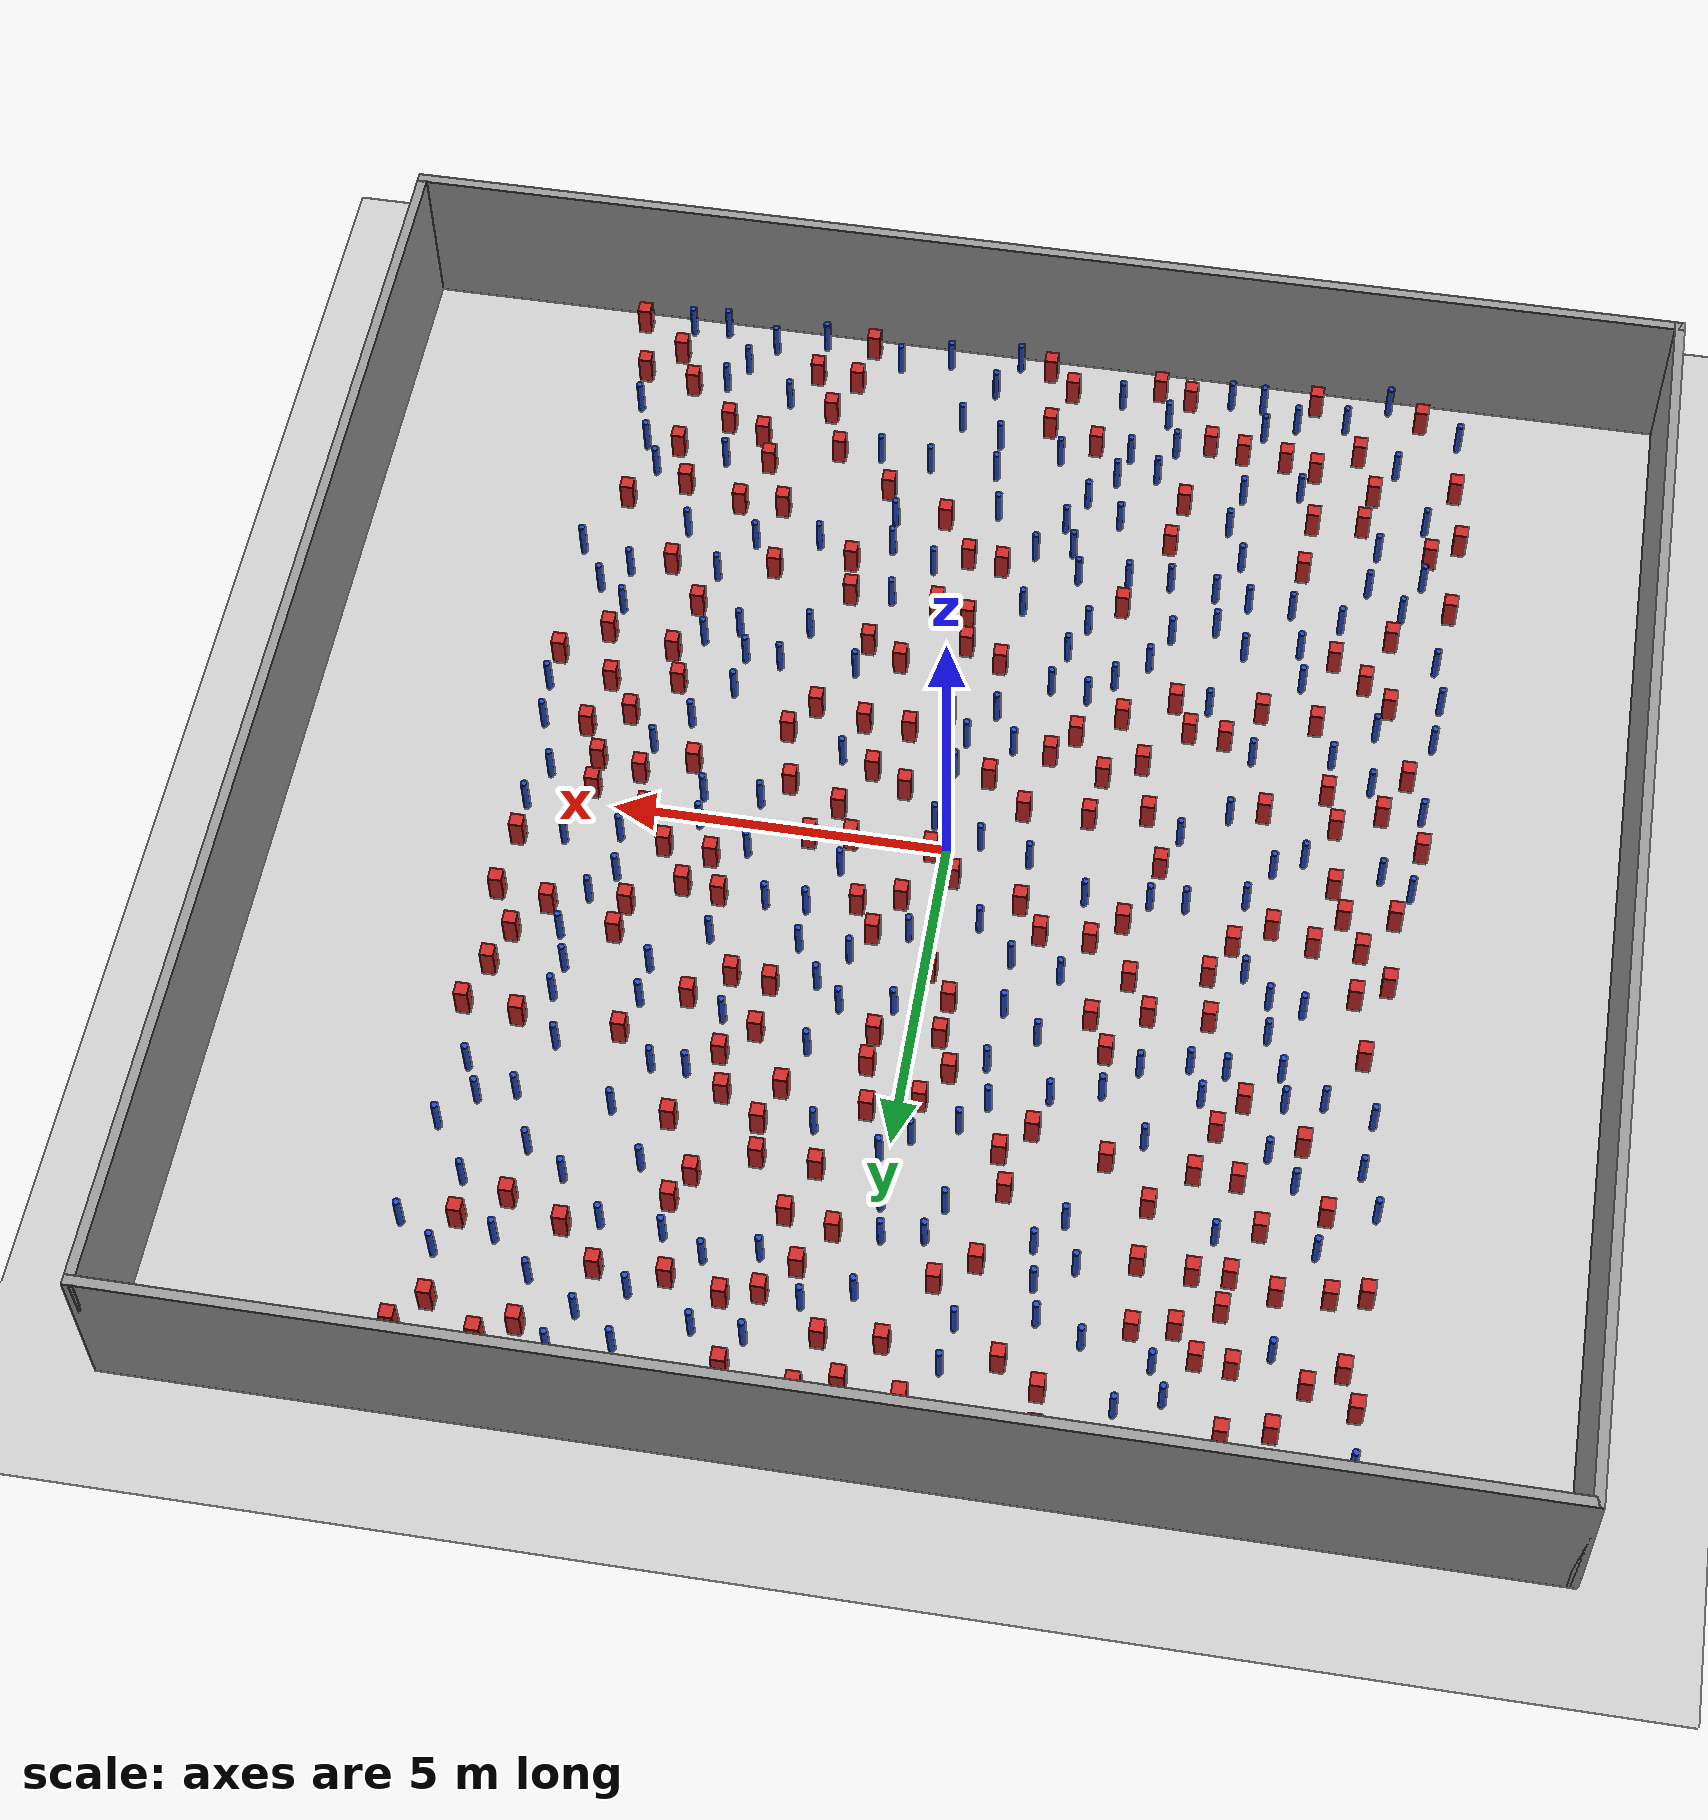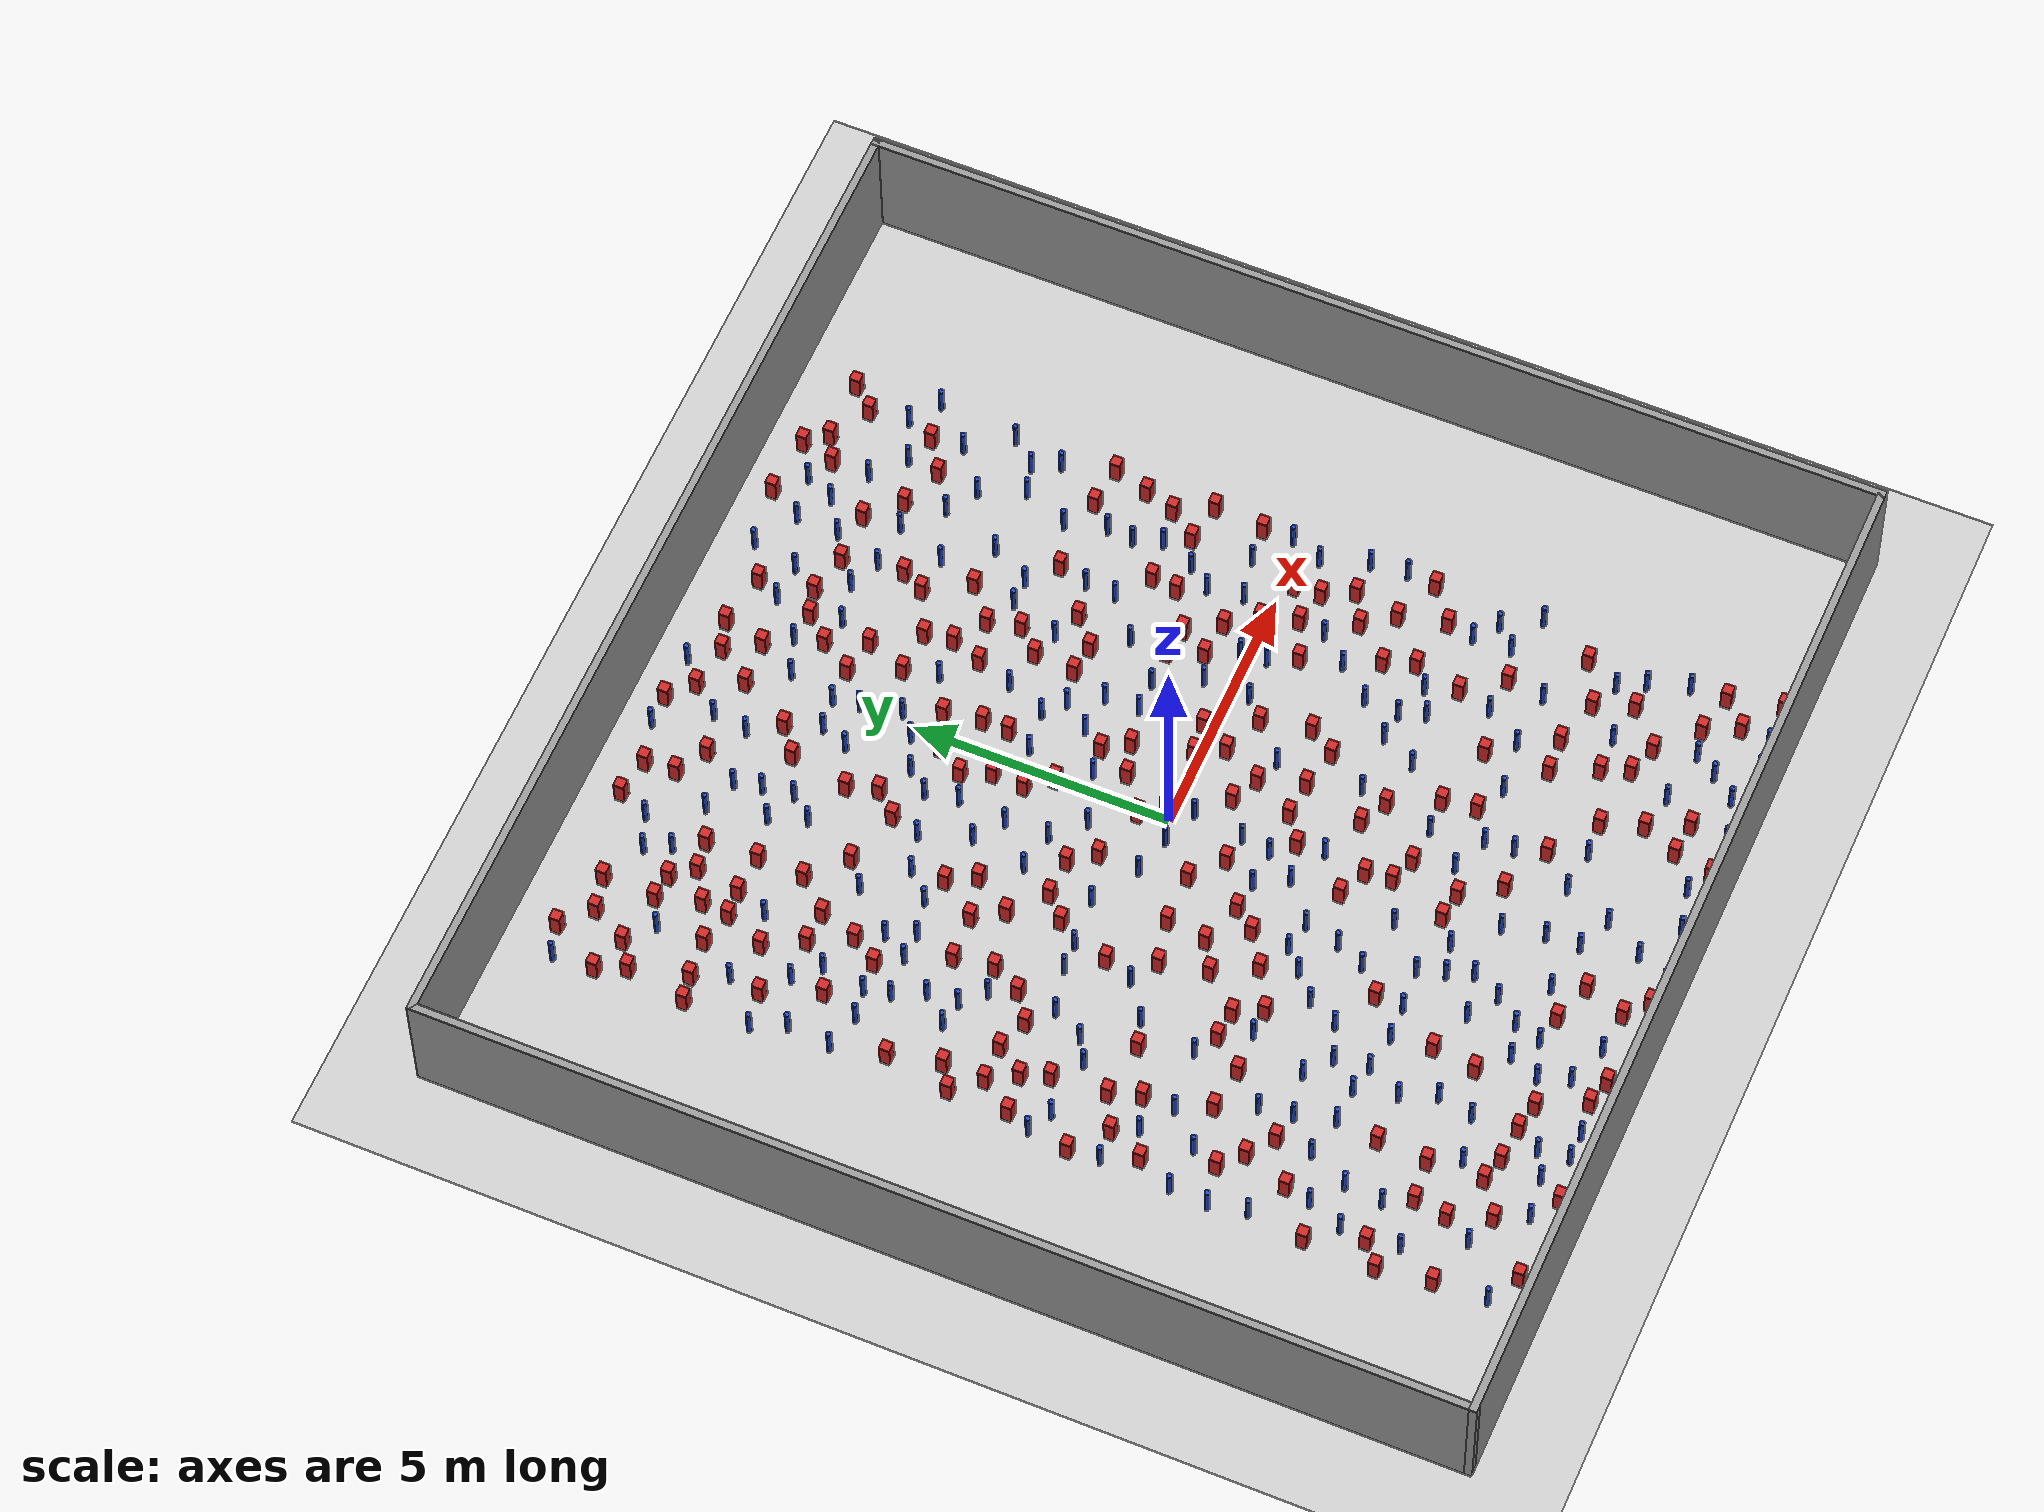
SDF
<sdf version="1.6">
 <world name="default">
  <light name="sun" type="directional">
   <pose>0 0 1000 0 -0 0</pose>
   <diffuse>0.8 0.8 0.8 1</diffuse>
   <specular>0.1 0.1 0.1 1</specular>
   <attenuation>
    <range>1000</range>
    <constant>0.9</constant>
    <linear>0.01</linear>
    <quadratic>0.001</quadratic>
   </attenuation>
   <direction>-0.5 0.5 -1</direction>
  </light>
  <model name="ground_plane">
   <static>1</static>
   <link name="link">
    <collision name="collision">
     <geometry><plane><normal>0 0 1</normal><size>100 100</size></plane></geometry>
     <surface><friction><ode><mu>100</mu><mu2>50</mu2></ode></friction></surface>
    </collision>
    <visual name="visual">
     <cast_shadows>0</cast_shadows>
     <geometry><plane><normal>0 0 1</normal><size>100 100</size></plane></geometry>
     <material>
      <ambient>1.0 1.0 1.0 1.0</ambient>
      <diffuse>0.8 0.8 0.8 1.0</diffuse>
      <specular>0.01 0.01 0.01 1.000000</specular>
     </material>
    </visual>
   </link>
  </model>
  <gravity>0 0 -9.8</gravity>
  <magnetic_field>6e-06 2.3e-05 -4.2e-05</magnetic_field>
  <atmosphere type="adiabatic"/>
  <physics name="default_physics" default="0" type="ode">
   <max_step_size>0.001</max_step_size>
   <real_time_factor>1</real_time_factor>
   <real_time_update_rate>1000</real_time_update_rate>
  </physics>
  <scene><ambient>0.4 0.4 0.4 1</ambient><background>0.7 0.7 0.7 1</background><shadows>1</shadows></scene>
  <spherical_coordinates>
   <surface_model>EARTH_WGS84</surface_model>
   <latitude_deg>0</latitude_deg>
   <longitude_deg>0</longitude_deg>
   <elevation>0</elevation>
   <heading_deg>0</heading_deg>
  </spherical_coordinates>
  <plugin name="gazebo_occupancy_map" filename="libgazebo_2Dmap_plugin.so">
   <map_resolution>0.05</map_resolution>
   <map_topic>generated_map</map_topic>
   <map_height>0.01</map_height>
   <map_size_x>50</map_size_x>
   <map_size_y>50</map_size_y>
  </plugin>
  <model name="NamedLocations">
   <static>true</static>
   <link name="DefaultStart"><pose>8.5 0 0 0 0 3.14</pose></link>
  </model>
  <model name="20x20_walls">
   <pose>0.044518 0.176112 0 0 -0 0</pose>
   <link name="Wall_1">
    <collision name="Wall_1_Collision">
     <geometry><box><size>20 0.15 2.5</size></box></geometry>
     <pose>0 0 1.25 0 -0 0</pose>
    </collision>
    <visual name="Wall_1_Visual">
     <pose>0 0 1.25 0 -0 0</pose>
     <geometry><box><size>20 0.15 2.5</size></box></geometry>
     <material>
      <script><uri>file://media/materials/scripts/gazebo.material</uri><name>Gazebo/Grey</name></script>
      <ambient>0.976471 0.992157 1 1</ambient>
     </material>
     <meta><layer>0</layer></meta>
    </visual>
    <pose>0 9.925 0 0 -0 0</pose>
   </link>
   <link name="Wall_3">
    <collision name="Wall_3_Collision">
     <geometry><box><size>20 0.15 2.5</size></box></geometry>
     <pose>0 0 1.25 0 -0 0</pose>
    </collision>
    <visual name="Wall_3_Visual">
     <pose>0 0 1.25 0 -0 0</pose>
     <geometry><box><size>20 0.15 2.5</size></box></geometry>
     <material>
      <script><uri>file://media/materials/scripts/gazebo.material</uri><name>Gazebo/Grey</name></script>
      <ambient>0.976471 0.992157 1 1</ambient>
     </material>
     <meta><layer>0</layer></meta>
    </visual>
    <pose>9.925 0 0 0 0 -1.5708</pose>
   </link>
   <link name="Wall_4">
    <collision name="Wall_4_Collision">
     <geometry><box><size>20 0.15 2.5</size></box></geometry>
     <pose>0 0 1.25 0 -0 0</pose>
    </collision>
    <visual name="Wall_4_Visual">
     <pose>0 0 1.25 0 -0 0</pose>
     <geometry><box><size>20 0.15 2.5</size></box></geometry>
     <material>
      <script><uri>file://media/materials/scripts/gazebo.material</uri><name>Gazebo/Grey</name></script>
      <ambient>0.976471 0.992157 1 1</ambient>
     </material>
     <meta><layer>0</layer></meta>
    </visual>
    <pose>0 -9.925 0 0 -0 3.14159</pose>
   </link>
   <link name="Wall_5">
    <collision name="Wall_5_Collision">
     <geometry><box><size>20 0.15 2.5</size></box></geometry>
     <pose>0 0 1.25 0 -0 0</pose>
    </collision>
    <visual name="Wall_5_Visual">
     <pose>0 0 1.25 0 -0 0</pose>
     <geometry><box><size>20 0.15 2.5</size></box></geometry>
     <material>
      <script><uri>file://media/materials/scripts/gazebo.material</uri><name>Gazebo/Grey</name></script>
      <ambient>0.976471 0.992157 1 1</ambient>
     </material>
     <meta><layer>0</layer></meta>
    </visual>
    <pose>-9.925 0 0 0 -0 1.5708</pose>
   </link>
   <static>1</static>
  </model>
  <model name="square_post_obstacle0">
   <static>true</static>
   <pose>-6.19125140931 1.70404252229 8.22691968438e-08 7.2212513382e-06 -7.54495500217e-07 2.29674213826e-05</pose>
   <link name="link">
    <pose>0 0 0.25 0 -0 0</pose>
    <inertial>
     <mass>100</mass>
     <inertia>
      <ixx>0.166667</ixx>
      <ixy>0</ixy>
      <ixz>0</ixz>
      <iyy>0.166667</iyy>
      <iyz>0</iyz>
      <izz>0.166667</izz>
     </inertia>
    </inertial>
    <collision name="collision"><geometry><box><size>.2 .2 .5</size></box></geometry></collision>
    <visual name="visual">
     <geometry><box><size>.2 .2 .5</size></box></geometry>
     <material>
      <script><name>Gazebo/Red</name><uri>file://media/materials/scripts/gazebo.material</uri></script>
     </material>
    </visual>
   </link>
  </model>
  <model name="square_post_obstacle1">
   <static>true</static>
   <pose>-6.63309455178 0.268396611212 8.22691968438e-08 7.2212513382e-06 -7.54495500217e-07 2.29674213826e-05</pose>
   <link name="link">
    <pose>0 0 0.25 0 -0 0</pose>
    <inertial>
     <mass>100</mass>
     <inertia>
      <ixx>0.166667</ixx>
      <ixy>0</ixy>
      <ixz>0</ixz>
      <iyy>0.166667</iyy>
      <iyz>0</iyz>
      <izz>0.166667</izz>
     </inertia>
    </inertial>
    <collision name="collision"><geometry><box><size>.2 .2 .5</size></box></geometry></collision>
    <visual name="visual">
     <geometry><box><size>.2 .2 .5</size></box></geometry>
     <material>
      <script><name>Gazebo/Red</name><uri>file://media/materials/scripts/gazebo.material</uri></script>
     </material>
    </visual>
   </link>
  </model>
  <model name="pole_obstacle0">
   <static>true</static>
   <pose>3.38088649552 5.95492401007 2.88873142074e-08 -9.90536689859e-09 4.60219948989e-07 -1.20965994961e-07</pose>
   <link name="link">
    <pose>0 0 0.3 0 -0 0</pose>
    <inertial>
     <mass>1</mass>
     <inertia><ixx>0.145833</ixx><ixy>0</ixy><ixz>0</ixz><iyy>0.145833</iyy><iyz>0</iyz><izz>0.125</izz></inertia>
    </inertial>
    <collision name="collision">
     <geometry><cylinder><radius>0.05</radius><length>.6</length></cylinder></geometry>
    </collision>
    <visual name="visual">
     <geometry><cylinder><radius>0.05</radius><length>.6</length></cylinder></geometry>
     <material>
      <script><name>Gazebo/Blue</name><uri>file://media/materials/scripts/gazebo.material</uri></script>
     </material>
    </visual>
   </link>
  </model>
  <model name="square_post_obstacle2">
   <static>true</static>
   <pose>4.48256671773 -2.31838774069 8.22691968438e-08 7.2212513382e-06 -7.54495500217e-07 2.29674213826e-05</pose>
   <link name="link">
    <pose>0 0 0.25 0 -0 0</pose>
    <inertial>
     <mass>100</mass>
     <inertia>
      <ixx>0.166667</ixx>
      <ixy>0</ixy>
      <ixz>0</ixz>
      <iyy>0.166667</iyy>
      <iyz>0</iyz>
      <izz>0.166667</izz>
     </inertia>
    </inertial>
    <collision name="collision"><geometry><box><size>.2 .2 .5</size></box></geometry></collision>
    <visual name="visual">
     <geometry><box><size>.2 .2 .5</size></box></geometry>
     <material>
      <script><name>Gazebo/Red</name><uri>file://media/materials/scripts/gazebo.material</uri></script>
     </material>
    </visual>
   </link>
  </model>
  <model name="pole_obstacle1">
   <static>true</static>
   <pose>4.70910394843 1.24014191663 2.88873142074e-08 -9.90536689445e-09 4.60219948999e-07 -1.20965994956e-07</pose>
   <link name="link">
    <pose>0 0 0.3 0 -0 0</pose>
    <inertial>
     <mass>1</mass>
     <inertia><ixx>0.145833</ixx><ixy>0</ixy><ixz>0</ixz><iyy>0.145833</iyy><iyz>0</iyz><izz>0.125</izz></inertia>
    </inertial>
    <collision name="collision">
     <geometry><cylinder><radius>0.05</radius><length>.6</length></cylinder></geometry>
    </collision>
    <visual name="visual">
     <geometry><cylinder><radius>0.05</radius><length>.6</length></cylinder></geometry>
     <material>
      <script><name>Gazebo/Blue</name><uri>file://media/materials/scripts/gazebo.material</uri></script>
     </material>
    </visual>
   </link>
  </model>
  <model name="square_post_obstacle3">
   <static>true</static>
   <pose>-4.35094908174 1.06992404259 8.22691968438e-08 7.2212513382e-06 -7.54495500217e-07 2.29674213826e-05</pose>
   <link name="link">
    <pose>0 0 0.25 0 -0 0</pose>
    <inertial>
     <mass>100</mass>
     <inertia>
      <ixx>0.166667</ixx>
      <ixy>0</ixy>
      <ixz>0</ixz>
      <iyy>0.166667</iyy>
      <iyz>0</iyz>
      <izz>0.166667</izz>
     </inertia>
    </inertial>
    <collision name="collision"><geometry><box><size>.2 .2 .5</size></box></geometry></collision>
    <visual name="visual">
     <geometry><box><size>.2 .2 .5</size></box></geometry>
     <material>
      <script><name>Gazebo/Red</name><uri>file://media/materials/scripts/gazebo.material</uri></script>
     </material>
    </visual>
   </link>
  </model>
  <model name="pole_obstacle2">
   <static>true</static>
   <pose>1.10299102913 4.98660373761 2.88873142074e-08 -9.90536689852e-09 4.60219948989e-07 -1.2096599496e-07</pose>
   <link name="link">
    <pose>0 0 0.3 0 -0 0</pose>
    <inertial>
     <mass>1</mass>
     <inertia><ixx>0.145833</ixx><ixy>0</ixy><ixz>0</ixz><iyy>0.145833</iyy><iyz>0</iyz><izz>0.125</izz></inertia>
    </inertial>
    <collision name="collision">
     <geometry><cylinder><radius>0.05</radius><length>.6</length></cylinder></geometry>
    </collision>
    <visual name="visual">
     <geometry><cylinder><radius>0.05</radius><length>.6</length></cylinder></geometry>
     <material>
      <script><name>Gazebo/Blue</name><uri>file://media/materials/scripts/gazebo.material</uri></script>
     </material>
    </visual>
   </link>
  </model>
  <model name="pole_obstacle3">
   <static>true</static>
   <pose>2.84458978488 -5.32492261194 2.88873142074e-08 -9.90536689859e-09 4.60219948989e-07 -1.20965994961e-07</pose>
   <link name="link">
    <pose>0 0 0.3 0 -0 0</pose>
    <inertial>
     <mass>1</mass>
     <inertia><ixx>0.145833</ixx><ixy>0</ixy><ixz>0</ixz><iyy>0.145833</iyy><iyz>0</iyz><izz>0.125</izz></inertia>
    </inertial>
    <collision name="collision">
     <geometry><cylinder><radius>0.05</radius><length>.6</length></cylinder></geometry>
    </collision>
    <visual name="visual">
     <geometry><cylinder><radius>0.05</radius><length>.6</length></cylinder></geometry>
     <material>
      <script><name>Gazebo/Blue</name><uri>file://media/materials/scripts/gazebo.material</uri></script>
     </material>
    </visual>
   </link>
  </model>
  <model name="square_post_obstacle4">
   <static>true</static>
   <pose>-4.0653938068 1.63940919941 8.22691968438e-08 7.2212513382e-06 -7.54495500217e-07 2.29674213826e-05</pose>
   <link name="link">
    <pose>0 0 0.25 0 -0 0</pose>
    <inertial>
     <mass>100</mass>
     <inertia>
      <ixx>0.166667</ixx>
      <ixy>0</ixy>
      <ixz>0</ixz>
      <iyy>0.166667</iyy>
      <iyz>0</iyz>
      <izz>0.166667</izz>
     </inertia>
    </inertial>
    <collision name="collision"><geometry><box><size>.2 .2 .5</size></box></geometry></collision>
    <visual name="visual">
     <geometry><box><size>.2 .2 .5</size></box></geometry>
     <material>
      <script><name>Gazebo/Red</name><uri>file://media/materials/scripts/gazebo.material</uri></script>
     </material>
    </visual>
   </link>
  </model>
  <model name="square_post_obstacle5">
   <static>true</static>
   <pose>0.511136152608 -5.36481793861 8.22691968438e-08 7.2212513382e-06 -7.54495500217e-07 2.29674213826e-05</pose>
   <link name="link">
    <pose>0 0 0.25 0 -0 0</pose>
    <inertial>
     <mass>100</mass>
     <inertia>
      <ixx>0.166667</ixx>
      <ixy>0</ixy>
      <ixz>0</ixz>
      <iyy>0.166667</iyy>
      <iyz>0</iyz>
      <izz>0.166667</izz>
     </inertia>
    </inertial>
    <collision name="collision"><geometry><box><size>.2 .2 .5</size></box></geometry></collision>
    <visual name="visual">
     <geometry><box><size>.2 .2 .5</size></box></geometry>
     <material>
      <script><name>Gazebo/Red</name><uri>file://media/materials/scripts/gazebo.material</uri></script>
     </material>
    </visual>
   </link>
  </model>
  <model name="square_post_obstacle6">
   <static>true</static>
   <pose>2.81641735757 -8.63394709874 8.22691968438e-08 7.22125133819e-06 -7.54495500217e-07 2.29674213826e-05</pose>
   <link name="link">
    <pose>0 0 0.25 0 -0 0</pose>
    <inertial>
     <mass>100</mass>
     <inertia>
      <ixx>0.166667</ixx>
      <ixy>0</ixy>
      <ixz>0</ixz>
      <iyy>0.166667</iyy>
      <iyz>0</iyz>
      <izz>0.166667</izz>
     </inertia>
    </inertial>
    <collision name="collision"><geometry><box><size>.2 .2 .5</size></box></geometry></collision>
    <visual name="visual">
     <geometry><box><size>.2 .2 .5</size></box></geometry>
     <material>
      <script><name>Gazebo/Red</name><uri>file://media/materials/scripts/gazebo.material</uri></script>
     </material>
    </visual>
   </link>
  </model>
  <model name="pole_obstacle4">
   <static>true</static>
   <pose>1.47778483085 2.62779666062 2.88873142074e-08 -9.90536689791e-09 4.6021994899e-07 -1.20965994959e-07</pose>
   <link name="link">
    <pose>0 0 0.3 0 -0 0</pose>
    <inertial>
     <mass>1</mass>
     <inertia><ixx>0.145833</ixx><ixy>0</ixy><ixz>0</ixz><iyy>0.145833</iyy><iyz>0</iyz><izz>0.125</izz></inertia>
    </inertial>
    <collision name="collision">
     <geometry><cylinder><radius>0.05</radius><length>.6</length></cylinder></geometry>
    </collision>
    <visual name="visual">
     <geometry><cylinder><radius>0.05</radius><length>.6</length></cylinder></geometry>
     <material>
      <script><name>Gazebo/Blue</name><uri>file://media/materials/scripts/gazebo.material</uri></script>
     </material>
    </visual>
   </link>
  </model>
  <model name="pole_obstacle5">
   <static>true</static>
   <pose>1.46848950987 8.38332093595 2.88873142074e-08 -9.90536690474e-09 4.60219948974e-07 -1.2096599497e-07</pose>
   <link name="link">
    <pose>0 0 0.3 0 -0 0</pose>
    <inertial>
     <mass>1</mass>
     <inertia><ixx>0.145833</ixx><ixy>0</ixy><ixz>0</ixz><iyy>0.145833</iyy><iyz>0</iyz><izz>0.125</izz></inertia>
    </inertial>
    <collision name="collision">
     <geometry><cylinder><radius>0.05</radius><length>.6</length></cylinder></geometry>
    </collision>
    <visual name="visual">
     <geometry><cylinder><radius>0.05</radius><length>.6</length></cylinder></geometry>
     <material>
      <script><name>Gazebo/Blue</name><uri>file://media/materials/scripts/gazebo.material</uri></script>
     </material>
    </visual>
   </link>
  </model>
  <model name="square_post_obstacle7">
   <static>true</static>
   <pose>-1.22613645058 9.38384493401 8.22691968438e-08 7.22125133819e-06 -7.54495500217e-07 2.29674213826e-05</pose>
   <link name="link">
    <pose>0 0 0.25 0 -0 0</pose>
    <inertial>
     <mass>100</mass>
     <inertia>
      <ixx>0.166667</ixx>
      <ixy>0</ixy>
      <ixz>0</ixz>
      <iyy>0.166667</iyy>
      <iyz>0</iyz>
      <izz>0.166667</izz>
     </inertia>
    </inertial>
    <collision name="collision"><geometry><box><size>.2 .2 .5</size></box></geometry></collision>
    <visual name="visual">
     <geometry><box><size>.2 .2 .5</size></box></geometry>
     <material>
      <script><name>Gazebo/Red</name><uri>file://media/materials/scripts/gazebo.material</uri></script>
     </material>
    </visual>
   </link>
  </model>
  <model name="square_post_obstacle8">
   <static>true</static>
   <pose>1.95207442491 -6.52803714667 8.22691968438e-08 7.2212513382e-06 -7.54495500217e-07 2.29674213826e-05</pose>
   <link name="link">
    <pose>0 0 0.25 0 -0 0</pose>
    <inertial>
     <mass>100</mass>
     <inertia>
      <ixx>0.166667</ixx>
      <ixy>0</ixy>
      <ixz>0</ixz>
      <iyy>0.166667</iyy>
      <iyz>0</iyz>
      <izz>0.166667</izz>
     </inertia>
    </inertial>
    <collision name="collision"><geometry><box><size>.2 .2 .5</size></box></geometry></collision>
    <visual name="visual">
     <geometry><box><size>.2 .2 .5</size></box></geometry>
     <material>
      <script><name>Gazebo/Red</name><uri>file://media/materials/scripts/gazebo.material</uri></script>
     </material>
    </visual>
   </link>
  </model>
  <model name="pole_obstacle6">
   <static>true</static>
   <pose>-6.03614184294 -3.01374664848 2.88873142074e-08 -9.90536690245e-09 4.6021994898e-07 -1.20965994966e-07</pose>
   <link name="link">
    <pose>0 0 0.3 0 -0 0</pose>
    <inertial>
     <mass>1</mass>
     <inertia><ixx>0.145833</ixx><ixy>0</ixy><ixz>0</ixz><iyy>0.145833</iyy><iyz>0</iyz><izz>0.125</izz></inertia>
    </inertial>
    <collision name="collision">
     <geometry><cylinder><radius>0.05</radius><length>.6</length></cylinder></geometry>
    </collision>
    <visual name="visual">
     <geometry><cylinder><radius>0.05</radius><length>.6</length></cylinder></geometry>
     <material>
      <script><name>Gazebo/Blue</name><uri>file://media/materials/scripts/gazebo.material</uri></script>
     </material>
    </visual>
   </link>
  </model>
  <model name="pole_obstacle7">
   <static>true</static>
   <pose>1.85947096066 1.37539737807 2.88873142074e-08 -9.90536689672e-09 4.60219948993e-07 -1.20965994959e-07</pose>
   <link name="link">
    <pose>0 0 0.3 0 -0 0</pose>
    <inertial>
     <mass>1</mass>
     <inertia><ixx>0.145833</ixx><ixy>0</ixy><ixz>0</ixz><iyy>0.145833</iyy><iyz>0</iyz><izz>0.125</izz></inertia>
    </inertial>
    <collision name="collision">
     <geometry><cylinder><radius>0.05</radius><length>.6</length></cylinder></geometry>
    </collision>
    <visual name="visual">
     <geometry><cylinder><radius>0.05</radius><length>.6</length></cylinder></geometry>
     <material>
      <script><name>Gazebo/Blue</name><uri>file://media/materials/scripts/gazebo.material</uri></script>
     </material>
    </visual>
   </link>
  </model>
  <model name="square_post_obstacle9">
   <static>true</static>
   <pose>-2.09843953088 -1.58954224777 8.22691968438e-08 7.2212513382e-06 -7.54495500217e-07 2.29674213826e-05</pose>
   <link name="link">
    <pose>0 0 0.25 0 -0 0</pose>
    <inertial>
     <mass>100</mass>
     <inertia>
      <ixx>0.166667</ixx>
      <ixy>0</ixy>
      <ixz>0</ixz>
      <iyy>0.166667</iyy>
      <iyz>0</iyz>
      <izz>0.166667</izz>
     </inertia>
    </inertial>
    <collision name="collision"><geometry><box><size>.2 .2 .5</size></box></geometry></collision>
    <visual name="visual">
     <geometry><box><size>.2 .2 .5</size></box></geometry>
     <material>
      <script><name>Gazebo/Red</name><uri>file://media/materials/scripts/gazebo.material</uri></script>
     </material>
    </visual>
   </link>
  </model>
  <model name="square_post_obstacle10">
   <static>true</static>
   <pose>-6.18987460027 -3.51102487603 8.22691968438e-08 7.2212513382e-06 -7.54495500217e-07 2.29674213826e-05</pose>
   <link name="link">
    <pose>0 0 0.25 0 -0 0</pose>
    <inertial>
     <mass>100</mass>
     <inertia>
      <ixx>0.166667</ixx>
      <ixy>0</ixy>
      <ixz>0</ixz>
      <iyy>0.166667</iyy>
      <iyz>0</iyz>
      <izz>0.166667</izz>
     </inertia>
    </inertial>
    <collision name="collision"><geometry><box><size>.2 .2 .5</size></box></geometry></collision>
    <visual name="visual">
     <geometry><box><size>.2 .2 .5</size></box></geometry>
     <material>
      <script><name>Gazebo/Red</name><uri>file://media/materials/scripts/gazebo.material</uri></script>
     </material>
    </visual>
   </link>
  </model>
  <model name="square_post_obstacle11">
   <static>true</static>
   <pose>-6.2019422107 0.900519539912 8.22691968438e-08 7.2212513382e-06 -7.54495500217e-07 2.29674213826e-05</pose>
   <link name="link">
    <pose>0 0 0.25 0 -0 0</pose>
    <inertial>
     <mass>100</mass>
     <inertia>
      <ixx>0.166667</ixx>
      <ixy>0</ixy>
      <ixz>0</ixz>
      <iyy>0.166667</iyy>
      <iyz>0</iyz>
      <izz>0.166667</izz>
     </inertia>
    </inertial>
    <collision name="collision"><geometry><box><size>.2 .2 .5</size></box></geometry></collision>
    <visual name="visual">
     <geometry><box><size>.2 .2 .5</size></box></geometry>
     <material>
      <script><name>Gazebo/Red</name><uri>file://media/materials/scripts/gazebo.material</uri></script>
     </material>
    </visual>
   </link>
  </model>
  <model name="square_post_obstacle12">
   <static>true</static>
   <pose>-6.54234163152 -6.48318330368 8.22691968438e-08 7.2212513382e-06 -7.54495500217e-07 2.29674213826e-05</pose>
   <link name="link">
    <pose>0 0 0.25 0 -0 0</pose>
    <inertial>
     <mass>100</mass>
     <inertia>
      <ixx>0.166667</ixx>
      <ixy>0</ixy>
      <ixz>0</ixz>
      <iyy>0.166667</iyy>
      <iyz>0</iyz>
      <izz>0.166667</izz>
     </inertia>
    </inertial>
    <collision name="collision"><geometry><box><size>.2 .2 .5</size></box></geometry></collision>
    <visual name="visual">
     <geometry><box><size>.2 .2 .5</size></box></geometry>
     <material>
      <script><name>Gazebo/Red</name><uri>file://media/materials/scripts/gazebo.material</uri></script>
     </material>
    </visual>
   </link>
  </model>
  <model name="square_post_obstacle13">
   <static>true</static>
   <pose>0.95175389864 5.64146808033 8.22691968438e-08 7.2212513382e-06 -7.54495500217e-07 2.29674213826e-05</pose>
   <link name="link">
    <pose>0 0 0.25 0 -0 0</pose>
    <inertial>
     <mass>100</mass>
     <inertia>
      <ixx>0.166667</ixx>
      <ixy>0</ixy>
      <ixz>0</ixz>
      <iyy>0.166667</iyy>
      <iyz>0</iyz>
      <izz>0.166667</izz>
     </inertia>
    </inertial>
    <collision name="collision"><geometry><box><size>.2 .2 .5</size></box></geometry></collision>
    <visual name="visual">
     <geometry><box><size>.2 .2 .5</size></box></geometry>
     <material>
      <script><name>Gazebo/Red</name><uri>file://media/materials/scripts/gazebo.material</uri></script>
     </material>
    </visual>
   </link>
  </model>
  <model name="pole_obstacle8">
   <static>true</static>
   <pose>-0.364076031964 -2.51130079487 2.88873142074e-08 -9.90536689663e-09 4.60219948993e-07 -1.20965994959e-07</pose>
   <link name="link">
    <pose>0 0 0.3 0 -0 0</pose>
    <inertial>
     <mass>1</mass>
     <inertia><ixx>0.145833</ixx><ixy>0</ixy><ixz>0</ixz><iyy>0.145833</iyy><iyz>0</iyz><izz>0.125</izz></inertia>
    </inertial>
    <collision name="collision">
     <geometry><cylinder><radius>0.05</radius><length>.6</length></cylinder></geometry>
    </collision>
    <visual name="visual">
     <geometry><cylinder><radius>0.05</radius><length>.6</length></cylinder></geometry>
     <material>
      <script><name>Gazebo/Blue</name><uri>file://media/materials/scripts/gazebo.material</uri></script>
     </material>
    </visual>
   </link>
  </model>
  <model name="square_post_obstacle14">
   <static>true</static>
   <pose>-4.28531719033 7.33323950146 8.22691968438e-08 7.2212513382e-06 -7.54495500217e-07 2.29674213826e-05</pose>
   <link name="link">
    <pose>0 0 0.25 0 -0 0</pose>
    <inertial>
     <mass>100</mass>
     <inertia>
      <ixx>0.166667</ixx>
      <ixy>0</ixy>
      <ixz>0</ixz>
      <iyy>0.166667</iyy>
      <iyz>0</iyz>
      <izz>0.166667</izz>
     </inertia>
    </inertial>
    <collision name="collision"><geometry><box><size>.2 .2 .5</size></box></geometry></collision>
    <visual name="visual">
     <geometry><box><size>.2 .2 .5</size></box></geometry>
     <material>
      <script><name>Gazebo/Red</name><uri>file://media/materials/scripts/gazebo.material</uri></script>
     </material>
    </visual>
   </link>
  </model>
  <model name="square_post_obstacle15">
   <static>true</static>
   <pose>-0.277370679803 -3.42844167066 8.22691968438e-08 7.2212513382e-06 -7.54495500217e-07 2.29674213826e-05</pose>
   <link name="link">
    <pose>0 0 0.25 0 -0 0</pose>
    <inertial>
     <mass>100</mass>
     <inertia>
      <ixx>0.166667</ixx>
      <ixy>0</ixy>
      <ixz>0</ixz>
      <iyy>0.166667</iyy>
      <iyz>0</iyz>
      <izz>0.166667</izz>
     </inertia>
    </inertial>
    <collision name="collision"><geometry><box><size>.2 .2 .5</size></box></geometry></collision>
    <visual name="visual">
     <geometry><box><size>.2 .2 .5</size></box></geometry>
     <material>
      <script><name>Gazebo/Red</name><uri>file://media/materials/scripts/gazebo.material</uri></script>
     </material>
    </visual>
   </link>
  </model>
  <model name="square_post_obstacle16">
   <static>true</static>
   <pose>0.509750937126 1.03052327592 8.22691968438e-08 7.2212513382e-06 -7.54495500217e-07 2.29674213826e-05</pose>
   <link name="link">
    <pose>0 0 0.25 0 -0 0</pose>
    <inertial>
     <mass>100</mass>
     <inertia>
      <ixx>0.166667</ixx>
      <ixy>0</ixy>
      <ixz>0</ixz>
      <iyy>0.166667</iyy>
      <iyz>0</iyz>
      <izz>0.166667</izz>
     </inertia>
    </inertial>
    <collision name="collision"><geometry><box><size>.2 .2 .5</size></box></geometry></collision>
    <visual name="visual">
     <geometry><box><size>.2 .2 .5</size></box></geometry>
     <material>
      <script><name>Gazebo/Red</name><uri>file://media/materials/scripts/gazebo.material</uri></script>
     </material>
    </visual>
   </link>
  </model>
  <model name="pole_obstacle9">
   <static>true</static>
   <pose>4.30141901712 -4.47266025773 2.88873142074e-08 -9.90536690842e-09 4.60219948965e-07 -1.20965994976e-07</pose>
   <link name="link">
    <pose>0 0 0.3 0 -0 0</pose>
    <inertial>
     <mass>1</mass>
     <inertia><ixx>0.145833</ixx><ixy>0</ixy><ixz>0</ixz><iyy>0.145833</iyy><iyz>0</iyz><izz>0.125</izz></inertia>
    </inertial>
    <collision name="collision">
     <geometry><cylinder><radius>0.05</radius><length>.6</length></cylinder></geometry>
    </collision>
    <visual name="visual">
     <geometry><cylinder><radius>0.05</radius><length>.6</length></cylinder></geometry>
     <material>
      <script><name>Gazebo/Blue</name><uri>file://media/materials/scripts/gazebo.material</uri></script>
     </material>
    </visual>
   </link>
  </model>
  <model name="square_post_obstacle17">
   <static>true</static>
   <pose>2.85667429622 -7.17951583488 8.22691968438e-08 7.2212513382e-06 -7.54495500217e-07 2.29674213826e-05</pose>
   <link name="link">
    <pose>0 0 0.25 0 -0 0</pose>
    <inertial>
     <mass>100</mass>
     <inertia>
      <ixx>0.166667</ixx>
      <ixy>0</ixy>
      <ixz>0</ixz>
      <iyy>0.166667</iyy>
      <iyz>0</iyz>
      <izz>0.166667</izz>
     </inertia>
    </inertial>
    <collision name="collision"><geometry><box><size>.2 .2 .5</size></box></geometry></collision>
    <visual name="visual">
     <geometry><box><size>.2 .2 .5</size></box></geometry>
     <material>
      <script><name>Gazebo/Red</name><uri>file://media/materials/scripts/gazebo.material</uri></script>
     </material>
    </visual>
   </link>
  </model>
  <model name="square_post_obstacle18">
   <static>true</static>
   <pose>-5.58500520957 6.61513116122 8.22691968438e-08 7.22125133819e-06 -7.54495500217e-07 2.29674213826e-05</pose>
   <link name="link">
    <pose>0 0 0.25 0 -0 0</pose>
    <inertial>
     <mass>100</mass>
     <inertia>
      <ixx>0.166667</ixx>
      <ixy>0</ixy>
      <ixz>0</ixz>
      <iyy>0.166667</iyy>
      <iyz>0</iyz>
      <izz>0.166667</izz>
     </inertia>
    </inertial>
    <collision name="collision"><geometry><box><size>.2 .2 .5</size></box></geometry></collision>
    <visual name="visual">
     <geometry><box><size>.2 .2 .5</size></box></geometry>
     <material>
      <script><name>Gazebo/Red</name><uri>file://media/materials/scripts/gazebo.material</uri></script>
     </material>
    </visual>
   </link>
  </model>
  <model name="pole_obstacle10">
   <static>true</static>
   <pose>-5.93792183759 3.5129405561 2.88873142074e-08 -9.90536690245e-09 4.6021994898e-07 -1.20965994966e-07</pose>
   <link name="link">
    <pose>0 0 0.3 0 -0 0</pose>
    <inertial>
     <mass>1</mass>
     <inertia><ixx>0.145833</ixx><ixy>0</ixy><ixz>0</ixz><iyy>0.145833</iyy><iyz>0</iyz><izz>0.125</izz></inertia>
    </inertial>
    <collision name="collision">
     <geometry><cylinder><radius>0.05</radius><length>.6</length></cylinder></geometry>
    </collision>
    <visual name="visual">
     <geometry><cylinder><radius>0.05</radius><length>.6</length></cylinder></geometry>
     <material>
      <script><name>Gazebo/Blue</name><uri>file://media/materials/scripts/gazebo.material</uri></script>
     </material>
    </visual>
   </link>
  </model>
  <model name="square_post_obstacle19">
   <static>true</static>
   <pose>2.67007542593 -9.38690693681 8.22691968438e-08 7.22125133819e-06 -7.54495500217e-07 2.29674213826e-05</pose>
   <link name="link">
    <pose>0 0 0.25 0 -0 0</pose>
    <inertial>
     <mass>100</mass>
     <inertia>
      <ixx>0.166667</ixx>
      <ixy>0</ixy>
      <ixz>0</ixz>
      <iyy>0.166667</iyy>
      <iyz>0</iyz>
      <izz>0.166667</izz>
     </inertia>
    </inertial>
    <collision name="collision"><geometry><box><size>.2 .2 .5</size></box></geometry></collision>
    <visual name="visual">
     <geometry><box><size>.2 .2 .5</size></box></geometry>
     <material>
      <script><name>Gazebo/Red</name><uri>file://media/materials/scripts/gazebo.material</uri></script>
     </material>
    </visual>
   </link>
  </model>
  <model name="pole_obstacle11">
   <static>true</static>
   <pose>-1.71149280971 -6.44326498525 2.88873142074e-08 -9.90536689852e-09 4.60219948989e-07 -1.2096599496e-07</pose>
   <link name="link">
    <pose>0 0 0.3 0 -0 0</pose>
    <inertial>
     <mass>1</mass>
     <inertia><ixx>0.145833</ixx><ixy>0</ixy><ixz>0</ixz><iyy>0.145833</iyy><iyz>0</iyz><izz>0.125</izz></inertia>
    </inertial>
    <collision name="collision">
     <geometry><cylinder><radius>0.05</radius><length>.6</length></cylinder></geometry>
    </collision>
    <visual name="visual">
     <geometry><cylinder><radius>0.05</radius><length>.6</length></cylinder></geometry>
     <material>
      <script><name>Gazebo/Blue</name><uri>file://media/materials/scripts/gazebo.material</uri></script>
     </material>
    </visual>
   </link>
  </model>
  <model name="square_post_obstacle20">
   <static>true</static>
   <pose>5.60389424884 3.84199440956 8.22691968438e-08 7.2212513382e-06 -7.54495500217e-07 2.29674213826e-05</pose>
   <link name="link">
    <pose>0 0 0.25 0 -0 0</pose>
    <inertial>
     <mass>100</mass>
     <inertia>
      <ixx>0.166667</ixx>
      <ixy>0</ixy>
      <ixz>0</ixz>
      <iyy>0.166667</iyy>
      <iyz>0</iyz>
      <izz>0.166667</izz>
     </inertia>
    </inertial>
    <collision name="collision"><geometry><box><size>.2 .2 .5</size></box></geometry></collision>
    <visual name="visual">
     <geometry><box><size>.2 .2 .5</size></box></geometry>
     <material>
      <script><name>Gazebo/Red</name><uri>file://media/materials/scripts/gazebo.material</uri></script>
     </material>
    </visual>
   </link>
  </model>
  <model name="pole_obstacle12">
   <static>true</static>
   <pose>-4.20994027742 3.70584274407 2.88873142074e-08 -9.90536690245e-09 4.6021994898e-07 -1.20965994966e-07</pose>
   <link name="link">
    <pose>0 0 0.3 0 -0 0</pose>
    <inertial>
     <mass>1</mass>
     <inertia><ixx>0.145833</ixx><ixy>0</ixy><ixz>0</ixz><iyy>0.145833</iyy><iyz>0</iyz><izz>0.125</izz></inertia>
    </inertial>
    <collision name="collision">
     <geometry><cylinder><radius>0.05</radius><length>.6</length></cylinder></geometry>
    </collision>
    <visual name="visual">
     <geometry><cylinder><radius>0.05</radius><length>.6</length></cylinder></geometry>
     <material>
      <script><name>Gazebo/Blue</name><uri>file://media/materials/scripts/gazebo.material</uri></script>
     </material>
    </visual>
   </link>
  </model>
  <model name="square_post_obstacle21">
   <static>true</static>
   <pose>-2.50041429818 -9.08207789205 8.22691968438e-08 7.22125133819e-06 -7.54495500217e-07 2.29674213826e-05</pose>
   <link name="link">
    <pose>0 0 0.25 0 -0 0</pose>
    <inertial>
     <mass>100</mass>
     <inertia>
      <ixx>0.166667</ixx>
      <ixy>0</ixy>
      <ixz>0</ixz>
      <iyy>0.166667</iyy>
      <iyz>0</iyz>
      <izz>0.166667</izz>
     </inertia>
    </inertial>
    <collision name="collision"><geometry><box><size>.2 .2 .5</size></box></geometry></collision>
    <visual name="visual">
     <geometry><box><size>.2 .2 .5</size></box></geometry>
     <material>
      <script><name>Gazebo/Red</name><uri>file://media/materials/scripts/gazebo.material</uri></script>
     </material>
    </visual>
   </link>
  </model>
  <model name="pole_obstacle13">
   <static>true</static>
   <pose>5.78583768149 6.56034018607 2.88873142074e-08 -9.90536690842e-09 4.60219948965e-07 -1.20965994976e-07</pose>
   <link name="link">
    <pose>0 0 0.3 0 -0 0</pose>
    <inertial>
     <mass>1</mass>
     <inertia><ixx>0.145833</ixx><ixy>0</ixy><ixz>0</ixz><iyy>0.145833</iyy><iyz>0</iyz><izz>0.125</izz></inertia>
    </inertial>
    <collision name="collision">
     <geometry><cylinder><radius>0.05</radius><length>.6</length></cylinder></geometry>
    </collision>
    <visual name="visual">
     <geometry><cylinder><radius>0.05</radius><length>.6</length></cylinder></geometry>
     <material>
      <script><name>Gazebo/Blue</name><uri>file://media/materials/scripts/gazebo.material</uri></script>
     </material>
    </visual>
   </link>
  </model>
  <model name="square_post_obstacle22">
   <static>true</static>
   <pose>3.46571762446 -8.69430635986 8.22691968438e-08 7.22125133819e-06 -7.54495500217e-07 2.29674213826e-05</pose>
   <link name="link">
    <pose>0 0 0.25 0 -0 0</pose>
    <inertial>
     <mass>100</mass>
     <inertia>
      <ixx>0.166667</ixx>
      <ixy>0</ixy>
      <ixz>0</ixz>
      <iyy>0.166667</iyy>
      <iyz>0</iyz>
      <izz>0.166667</izz>
     </inertia>
    </inertial>
    <collision name="collision"><geometry><box><size>.2 .2 .5</size></box></geometry></collision>
    <visual name="visual">
     <geometry><box><size>.2 .2 .5</size></box></geometry>
     <material>
      <script><name>Gazebo/Red</name><uri>file://media/materials/scripts/gazebo.material</uri></script>
     </material>
    </visual>
   </link>
  </model>
  <model name="pole_obstacle14">
   <static>true</static>
   <pose>-2.29876144259 6.96857675755 2.88873142074e-08 -9.90536689859e-09 4.60219948989e-07 -1.20965994961e-07</pose>
   <link name="link">
    <pose>0 0 0.3 0 -0 0</pose>
    <inertial>
     <mass>1</mass>
     <inertia><ixx>0.145833</ixx><ixy>0</ixy><ixz>0</ixz><iyy>0.145833</iyy><iyz>0</iyz><izz>0.125</izz></inertia>
    </inertial>
    <collision name="collision">
     <geometry><cylinder><radius>0.05</radius><length>.6</length></cylinder></geometry>
    </collision>
    <visual name="visual">
     <geometry><cylinder><radius>0.05</radius><length>.6</length></cylinder></geometry>
     <material>
      <script><name>Gazebo/Blue</name><uri>file://media/materials/scripts/gazebo.material</uri></script>
     </material>
    </visual>
   </link>
  </model>
  <model name="pole_obstacle15">
   <static>true</static>
   <pose>1.48284990694 0.625660362326 2.88873142074e-08 -9.90536689692e-09 4.60219948993e-07 -1.20965994958e-07</pose>
   <link name="link">
    <pose>0 0 0.3 0 -0 0</pose>
    <inertial>
     <mass>1</mass>
     <inertia><ixx>0.145833</ixx><ixy>0</ixy><ixz>0</ixz><iyy>0.145833</iyy><iyz>0</iyz><izz>0.125</izz></inertia>
    </inertial>
    <collision name="collision">
     <geometry><cylinder><radius>0.05</radius><length>.6</length></cylinder></geometry>
    </collision>
    <visual name="visual">
     <geometry><cylinder><radius>0.05</radius><length>.6</length></cylinder></geometry>
     <material>
      <script><name>Gazebo/Blue</name><uri>file://media/materials/scripts/gazebo.material</uri></script>
     </material>
    </visual>
   </link>
  </model>
  <model name="pole_obstacle16">
   <static>true</static>
   <pose>0.190259198719 -6.33694293951 2.88873142074e-08 -9.90536689711e-09 4.60219948992e-07 -1.2096599496e-07</pose>
   <link name="link">
    <pose>0 0 0.3 0 -0 0</pose>
    <inertial>
     <mass>1</mass>
     <inertia><ixx>0.145833</ixx><ixy>0</ixy><ixz>0</ixz><iyy>0.145833</iyy><iyz>0</iyz><izz>0.125</izz></inertia>
    </inertial>
    <collision name="collision">
     <geometry><cylinder><radius>0.05</radius><length>.6</length></cylinder></geometry>
    </collision>
    <visual name="visual">
     <geometry><cylinder><radius>0.05</radius><length>.6</length></cylinder></geometry>
     <material>
      <script><name>Gazebo/Blue</name><uri>file://media/materials/scripts/gazebo.material</uri></script>
     </material>
    </visual>
   </link>
  </model>
  <model name="square_post_obstacle23">
   <static>true</static>
   <pose>3.39282739825 0.729039512999 8.22691968438e-08 7.2212513382e-06 -7.54495500217e-07 2.29674213826e-05</pose>
   <link name="link">
    <pose>0 0 0.25 0 -0 0</pose>
    <inertial>
     <mass>100</mass>
     <inertia>
      <ixx>0.166667</ixx>
      <ixy>0</ixy>
      <ixz>0</ixz>
      <iyy>0.166667</iyy>
      <iyz>0</iyz>
      <izz>0.166667</izz>
     </inertia>
    </inertial>
    <collision name="collision"><geometry><box><size>.2 .2 .5</size></box></geometry></collision>
    <visual name="visual">
     <geometry><box><size>.2 .2 .5</size></box></geometry>
     <material>
      <script><name>Gazebo/Red</name><uri>file://media/materials/scripts/gazebo.material</uri></script>
     </material>
    </visual>
   </link>
  </model>
  <model name="pole_obstacle17">
   <static>true</static>
   <pose>-4.43029769642 -7.44711746223 2.88873142074e-08 -9.90536690842e-09 4.60219948965e-07 -1.20965994976e-07</pose>
   <link name="link">
    <pose>0 0 0.3 0 -0 0</pose>
    <inertial>
     <mass>1</mass>
     <inertia><ixx>0.145833</ixx><ixy>0</ixy><ixz>0</ixz><iyy>0.145833</iyy><iyz>0</iyz><izz>0.125</izz></inertia>
    </inertial>
    <collision name="collision">
     <geometry><cylinder><radius>0.05</radius><length>.6</length></cylinder></geometry>
    </collision>
    <visual name="visual">
     <geometry><cylinder><radius>0.05</radius><length>.6</length></cylinder></geometry>
     <material>
      <script><name>Gazebo/Blue</name><uri>file://media/materials/scripts/gazebo.material</uri></script>
     </material>
    </visual>
   </link>
  </model>
  <model name="square_post_obstacle24">
   <static>true</static>
   <pose>4.21383172551 -5.89049706894 8.22691968438e-08 7.2212513382e-06 -7.54495500217e-07 2.29674213826e-05</pose>
   <link name="link">
    <pose>0 0 0.25 0 -0 0</pose>
    <inertial>
     <mass>100</mass>
     <inertia>
      <ixx>0.166667</ixx>
      <ixy>0</ixy>
      <ixz>0</ixz>
      <iyy>0.166667</iyy>
      <iyz>0</iyz>
      <izz>0.166667</izz>
     </inertia>
    </inertial>
    <collision name="collision"><geometry><box><size>.2 .2 .5</size></box></geometry></collision>
    <visual name="visual">
     <geometry><box><size>.2 .2 .5</size></box></geometry>
     <material>
      <script><name>Gazebo/Red</name><uri>file://media/materials/scripts/gazebo.material</uri></script>
     </material>
    </visual>
   </link>
  </model>
  <model name="square_post_obstacle25">
   <static>true</static>
   <pose>-3.29495247302 2.44679450185 8.22691968438e-08 7.2212513382e-06 -7.54495500217e-07 2.29674213826e-05</pose>
   <link name="link">
    <pose>0 0 0.25 0 -0 0</pose>
    <inertial>
     <mass>100</mass>
     <inertia>
      <ixx>0.166667</ixx>
      <ixy>0</ixy>
      <ixz>0</ixz>
      <iyy>0.166667</iyy>
      <iyz>0</iyz>
      <izz>0.166667</izz>
     </inertia>
    </inertial>
    <collision name="collision"><geometry><box><size>.2 .2 .5</size></box></geometry></collision>
    <visual name="visual">
     <geometry><box><size>.2 .2 .5</size></box></geometry>
     <material>
      <script><name>Gazebo/Red</name><uri>file://media/materials/scripts/gazebo.material</uri></script>
     </material>
    </visual>
   </link>
  </model>
  <model name="square_post_obstacle26">
   <static>true</static>
   <pose>-1.96969947344 -4.80066524468 8.22691968438e-08 7.2212513382e-06 -7.54495500217e-07 2.29674213826e-05</pose>
   <link name="link">
    <pose>0 0 0.25 0 -0 0</pose>
    <inertial>
     <mass>100</mass>
     <inertia>
      <ixx>0.166667</ixx>
      <ixy>0</ixy>
      <ixz>0</ixz>
      <iyy>0.166667</iyy>
      <iyz>0</iyz>
      <izz>0.166667</izz>
     </inertia>
    </inertial>
    <collision name="collision"><geometry><box><size>.2 .2 .5</size></box></geometry></collision>
    <visual name="visual">
     <geometry><box><size>.2 .2 .5</size></box></geometry>
     <material>
      <script><name>Gazebo/Red</name><uri>file://media/materials/scripts/gazebo.material</uri></script>
     </material>
    </visual>
   </link>
  </model>
  <model name="square_post_obstacle27">
   <static>true</static>
   <pose>-0.446918486928 2.64767592623 8.22691968438e-08 7.2212513382e-06 -7.54495500217e-07 2.29674213826e-05</pose>
   <link name="link">
    <pose>0 0 0.25 0 -0 0</pose>
    <inertial>
     <mass>100</mass>
     <inertia>
      <ixx>0.166667</ixx>
      <ixy>0</ixy>
      <ixz>0</ixz>
      <iyy>0.166667</iyy>
      <iyz>0</iyz>
      <izz>0.166667</izz>
     </inertia>
    </inertial>
    <collision name="collision"><geometry><box><size>.2 .2 .5</size></box></geometry></collision>
    <visual name="visual">
     <geometry><box><size>.2 .2 .5</size></box></geometry>
     <material>
      <script><name>Gazebo/Red</name><uri>file://media/materials/scripts/gazebo.material</uri></script>
     </material>
    </visual>
   </link>
  </model>
  <model name="pole_obstacle18">
   <static>true</static>
   <pose>3.91504674664 2.71842902857 2.88873142074e-08 -9.90536690232e-09 4.6021994898e-07 -1.20965994968e-07</pose>
   <link name="link">
    <pose>0 0 0.3 0 -0 0</pose>
    <inertial>
     <mass>1</mass>
     <inertia><ixx>0.145833</ixx><ixy>0</ixy><ixz>0</ixz><iyy>0.145833</iyy><iyz>0</iyz><izz>0.125</izz></inertia>
    </inertial>
    <collision name="collision">
     <geometry><cylinder><radius>0.05</radius><length>.6</length></cylinder></geometry>
    </collision>
    <visual name="visual">
     <geometry><cylinder><radius>0.05</radius><length>.6</length></cylinder></geometry>
     <material>
      <script><name>Gazebo/Blue</name><uri>file://media/materials/scripts/gazebo.material</uri></script>
     </material>
    </visual>
   </link>
  </model>
  <model name="square_post_obstacle28">
   <static>true</static>
   <pose>-0.948833752845 7.14152866537 8.22691968438e-08 7.22125133819e-06 -7.54495500217e-07 2.29674213826e-05</pose>
   <link name="link">
    <pose>0 0 0.25 0 -0 0</pose>
    <inertial>
     <mass>100</mass>
     <inertia>
      <ixx>0.166667</ixx>
      <ixy>0</ixy>
      <ixz>0</ixz>
      <iyy>0.166667</iyy>
      <iyz>0</iyz>
      <izz>0.166667</izz>
     </inertia>
    </inertial>
    <collision name="collision"><geometry><box><size>.2 .2 .5</size></box></geometry></collision>
    <visual name="visual">
     <geometry><box><size>.2 .2 .5</size></box></geometry>
     <material>
      <script><name>Gazebo/Red</name><uri>file://media/materials/scripts/gazebo.material</uri></script>
     </material>
    </visual>
   </link>
  </model>
  <model name="pole_obstacle19">
   <static>true</static>
   <pose>-1.96526800572 1.98989048109 2.88873142074e-08 -9.90536689684e-09 4.60219948993e-07 -1.20965994958e-07</pose>
   <link name="link">
    <pose>0 0 0.3 0 -0 0</pose>
    <inertial>
     <mass>1</mass>
     <inertia><ixx>0.145833</ixx><ixy>0</ixy><ixz>0</ixz><iyy>0.145833</iyy><iyz>0</iyz><izz>0.125</izz></inertia>
    </inertial>
    <collision name="collision">
     <geometry><cylinder><radius>0.05</radius><length>.6</length></cylinder></geometry>
    </collision>
    <visual name="visual">
     <geometry><cylinder><radius>0.05</radius><length>.6</length></cylinder></geometry>
     <material>
      <script><name>Gazebo/Blue</name><uri>file://media/materials/scripts/gazebo.material</uri></script>
     </material>
    </visual>
   </link>
  </model>
  <model name="square_post_obstacle29">
   <static>true</static>
   <pose>2.33625067397 -2.19596236131 8.22691968438e-08 7.2212513382e-06 -7.54495500217e-07 2.29674213826e-05</pose>
   <link name="link">
    <pose>0 0 0.25 0 -0 0</pose>
    <inertial>
     <mass>100</mass>
     <inertia>
      <ixx>0.166667</ixx>
      <ixy>0</ixy>
      <ixz>0</ixz>
      <iyy>0.166667</iyy>
      <iyz>0</iyz>
      <izz>0.166667</izz>
     </inertia>
    </inertial>
    <collision name="collision"><geometry><box><size>.2 .2 .5</size></box></geometry></collision>
    <visual name="visual">
     <geometry><box><size>.2 .2 .5</size></box></geometry>
     <material>
      <script><name>Gazebo/Red</name><uri>file://media/materials/scripts/gazebo.material</uri></script>
     </material>
    </visual>
   </link>
  </model>
  <model name="square_post_obstacle30">
   <static>true</static>
   <pose>-6.58384823632 -2.22979460355 8.22691968438e-08 7.2212513382e-06 -7.54495500217e-07 2.29674213826e-05</pose>
   <link name="link">
    <pose>0 0 0.25 0 -0 0</pose>
    <inertial>
     <mass>100</mass>
     <inertia>
      <ixx>0.166667</ixx>
      <ixy>0</ixy>
      <ixz>0</ixz>
      <iyy>0.166667</iyy>
      <iyz>0</iyz>
      <izz>0.166667</izz>
     </inertia>
    </inertial>
    <collision name="collision"><geometry><box><size>.2 .2 .5</size></box></geometry></collision>
    <visual name="visual">
     <geometry><box><size>.2 .2 .5</size></box></geometry>
     <material>
      <script><name>Gazebo/Red</name><uri>file://media/materials/scripts/gazebo.material</uri></script>
     </material>
    </visual>
   </link>
  </model>
  <model name="pole_obstacle20">
   <static>true</static>
   <pose>-3.50856159253 4.51452221172 2.88873142074e-08 -9.90536692062e-09 4.60219948937e-07 -1.20965994985e-07</pose>
   <link name="link">
    <pose>0 0 0.3 0 -0 0</pose>
    <inertial>
     <mass>1</mass>
     <inertia><ixx>0.145833</ixx><ixy>0</ixy><ixz>0</ixz><iyy>0.145833</iyy><iyz>0</iyz><izz>0.125</izz></inertia>
    </inertial>
    <collision name="collision">
     <geometry><cylinder><radius>0.05</radius><length>.6</length></cylinder></geometry>
    </collision>
    <visual name="visual">
     <geometry><cylinder><radius>0.05</radius><length>.6</length></cylinder></geometry>
     <material>
      <script><name>Gazebo/Blue</name><uri>file://media/materials/scripts/gazebo.material</uri></script>
     </material>
    </visual>
   </link>
  </model>
  <model name="pole_obstacle21">
   <static>true</static>
   <pose>0.0107607865658 -1.9463137938 2.88873142074e-08 -9.90536689885e-09 4.60219948988e-07 -1.20965994962e-07</pose>
   <link name="link">
    <pose>0 0 0.3 0 -0 0</pose>
    <inertial>
     <mass>1</mass>
     <inertia><ixx>0.145833</ixx><ixy>0</ixy><ixz>0</ixz><iyy>0.145833</iyy><iyz>0</iyz><izz>0.125</izz></inertia>
    </inertial>
    <collision name="collision">
     <geometry><cylinder><radius>0.05</radius><length>.6</length></cylinder></geometry>
    </collision>
    <visual name="visual">
     <geometry><cylinder><radius>0.05</radius><length>.6</length></cylinder></geometry>
     <material>
      <script><name>Gazebo/Blue</name><uri>file://media/materials/scripts/gazebo.material</uri></script>
     </material>
    </visual>
   </link>
  </model>
  <model name="square_post_obstacle31">
   <static>true</static>
   <pose>-4.30403940408 -3.13342213198 8.22691968438e-08 7.2212513382e-06 -7.54495500217e-07 2.29674213826e-05</pose>
   <link name="link">
    <pose>0 0 0.25 0 -0 0</pose>
    <inertial>
     <mass>100</mass>
     <inertia>
      <ixx>0.166667</ixx>
      <ixy>0</ixy>
      <ixz>0</ixz>
      <iyy>0.166667</iyy>
      <iyz>0</iyz>
      <izz>0.166667</izz>
     </inertia>
    </inertial>
    <collision name="collision"><geometry><box><size>.2 .2 .5</size></box></geometry></collision>
    <visual name="visual">
     <geometry><box><size>.2 .2 .5</size></box></geometry>
     <material>
      <script><name>Gazebo/Red</name><uri>file://media/materials/scripts/gazebo.material</uri></script>
     </material>
    </visual>
   </link>
  </model>
  <model name="pole_obstacle22">
   <static>true</static>
   <pose>-6.81948418331 -4.3690585778 2.88873142074e-08 -9.90536690842e-09 4.60219948965e-07 -1.20965994976e-07</pose>
   <link name="link">
    <pose>0 0 0.3 0 -0 0</pose>
    <inertial>
     <mass>1</mass>
     <inertia><ixx>0.145833</ixx><ixy>0</ixy><ixz>0</ixz><iyy>0.145833</iyy><iyz>0</iyz><izz>0.125</izz></inertia>
    </inertial>
    <collision name="collision">
     <geometry><cylinder><radius>0.05</radius><length>.6</length></cylinder></geometry>
    </collision>
    <visual name="visual">
     <geometry><cylinder><radius>0.05</radius><length>.6</length></cylinder></geometry>
     <material>
      <script><name>Gazebo/Blue</name><uri>file://media/materials/scripts/gazebo.material</uri></script>
     </material>
    </visual>
   </link>
  </model>
  <model name="pole_obstacle23">
   <static>true</static>
   <pose>5.14635958631 7.3870239795 2.88873142074e-08 -9.90536690842e-09 4.60219948965e-07 -1.20965994976e-07</pose>
   <link name="link">
    <pose>0 0 0.3 0 -0 0</pose>
    <inertial>
     <mass>1</mass>
     <inertia><ixx>0.145833</ixx><ixy>0</ixy><ixz>0</ixz><iyy>0.145833</iyy><iyz>0</iyz><izz>0.125</izz></inertia>
    </inertial>
    <collision name="collision">
     <geometry><cylinder><radius>0.05</radius><length>.6</length></cylinder></geometry>
    </collision>
    <visual name="visual">
     <geometry><cylinder><radius>0.05</radius><length>.6</length></cylinder></geometry>
     <material>
      <script><name>Gazebo/Blue</name><uri>file://media/materials/scripts/gazebo.material</uri></script>
     </material>
    </visual>
   </link>
  </model>
  <model name="pole_obstacle24">
   <static>true</static>
   <pose>-6.78461669548 -8.85125705796 2.88873142074e-08 -9.9053668967e-09 4.60219948993e-07 -1.20965994957e-07</pose>
   <link name="link">
    <pose>0 0 0.3 0 -0 0</pose>
    <inertial>
     <mass>1</mass>
     <inertia><ixx>0.145833</ixx><ixy>0</ixy><ixz>0</ixz><iyy>0.145833</iyy><iyz>0</iyz><izz>0.125</izz></inertia>
    </inertial>
    <collision name="collision">
     <geometry><cylinder><radius>0.05</radius><length>.6</length></cylinder></geometry>
    </collision>
    <visual name="visual">
     <geometry><cylinder><radius>0.05</radius><length>.6</length></cylinder></geometry>
     <material>
      <script><name>Gazebo/Blue</name><uri>file://media/materials/scripts/gazebo.material</uri></script>
     </material>
    </visual>
   </link>
  </model>
  <model name="pole_obstacle25">
   <static>true</static>
   <pose>5.61476812269 -3.6230665425 2.88873142074e-08 -9.90536690245e-09 4.6021994898e-07 -1.20965994966e-07</pose>
   <link name="link">
    <pose>0 0 0.3 0 -0 0</pose>
    <inertial>
     <mass>1</mass>
     <inertia><ixx>0.145833</ixx><ixy>0</ixy><ixz>0</ixz><iyy>0.145833</iyy><iyz>0</iyz><izz>0.125</izz></inertia>
    </inertial>
    <collision name="collision">
     <geometry><cylinder><radius>0.05</radius><length>.6</length></cylinder></geometry>
    </collision>
    <visual name="visual">
     <geometry><cylinder><radius>0.05</radius><length>.6</length></cylinder></geometry>
     <material>
      <script><name>Gazebo/Blue</name><uri>file://media/materials/scripts/gazebo.material</uri></script>
     </material>
    </visual>
   </link>
  </model>
  <model name="pole_obstacle26">
   <static>true</static>
   <pose>6.13167573041 4.73643035613 2.88873142074e-08 -9.90536690842e-09 4.60219948965e-07 -1.20965994976e-07</pose>
   <link name="link">
    <pose>0 0 0.3 0 -0 0</pose>
    <inertial>
     <mass>1</mass>
     <inertia><ixx>0.145833</ixx><ixy>0</ixy><ixz>0</ixz><iyy>0.145833</iyy><iyz>0</iyz><izz>0.125</izz></inertia>
    </inertial>
    <collision name="collision">
     <geometry><cylinder><radius>0.05</radius><length>.6</length></cylinder></geometry>
    </collision>
    <visual name="visual">
     <geometry><cylinder><radius>0.05</radius><length>.6</length></cylinder></geometry>
     <material>
      <script><name>Gazebo/Blue</name><uri>file://media/materials/scripts/gazebo.material</uri></script>
     </material>
    </visual>
   </link>
  </model>
  <model name="pole_obstacle27">
   <static>true</static>
   <pose>-2.20261003958 -8.60993973966 2.88873142074e-08 -9.90536692318e-09 4.6021994893e-07 -1.20965994988e-07</pose>
   <link name="link">
    <pose>0 0 0.3 0 -0 0</pose>
    <inertial>
     <mass>1</mass>
     <inertia><ixx>0.145833</ixx><ixy>0</ixy><ixz>0</ixz><iyy>0.145833</iyy><iyz>0</iyz><izz>0.125</izz></inertia>
    </inertial>
    <collision name="collision">
     <geometry><cylinder><radius>0.05</radius><length>.6</length></cylinder></geometry>
    </collision>
    <visual name="visual">
     <geometry><cylinder><radius>0.05</radius><length>.6</length></cylinder></geometry>
     <material>
      <script><name>Gazebo/Blue</name><uri>file://media/materials/scripts/gazebo.material</uri></script>
     </material>
    </visual>
   </link>
  </model>
  <model name="square_post_obstacle32">
   <static>true</static>
   <pose>-2.92771861356 -8.20823176281 8.22691968438e-08 7.22125133819e-06 -7.54495500217e-07 2.29674213826e-05</pose>
   <link name="link">
    <pose>0 0 0.25 0 -0 0</pose>
    <inertial>
     <mass>100</mass>
     <inertia>
      <ixx>0.166667</ixx>
      <ixy>0</ixy>
      <ixz>0</ixz>
      <iyy>0.166667</iyy>
      <iyz>0</iyz>
      <izz>0.166667</izz>
     </inertia>
    </inertial>
    <collision name="collision"><geometry><box><size>.2 .2 .5</size></box></geometry></collision>
    <visual name="visual">
     <geometry><box><size>.2 .2 .5</size></box></geometry>
     <material>
      <script><name>Gazebo/Red</name><uri>file://media/materials/scripts/gazebo.material</uri></script>
     </material>
    </visual>
   </link>
  </model>
  <model name="square_post_obstacle33">
   <static>true</static>
   <pose>-3.69137346641 5.52263100463 8.22691968438e-08 7.2212513382e-06 -7.54495500217e-07 2.29674213826e-05</pose>
   <link name="link">
    <pose>0 0 0.25 0 -0 0</pose>
    <inertial>
     <mass>100</mass>
     <inertia>
      <ixx>0.166667</ixx>
      <ixy>0</ixy>
      <ixz>0</ixz>
      <iyy>0.166667</iyy>
      <iyz>0</iyz>
      <izz>0.166667</izz>
     </inertia>
    </inertial>
    <collision name="collision"><geometry><box><size>.2 .2 .5</size></box></geometry></collision>
    <visual name="visual">
     <geometry><box><size>.2 .2 .5</size></box></geometry>
     <material>
      <script><name>Gazebo/Red</name><uri>file://media/materials/scripts/gazebo.material</uri></script>
     </material>
    </visual>
   </link>
  </model>
  <model name="pole_obstacle28">
   <static>true</static>
   <pose>1.75358813247 -5.96166153707 2.88873142074e-08 -9.90536689852e-09 4.60219948989e-07 -1.2096599496e-07</pose>
   <link name="link">
    <pose>0 0 0.3 0 -0 0</pose>
    <inertial>
     <mass>1</mass>
     <inertia><ixx>0.145833</ixx><ixy>0</ixy><ixz>0</ixz><iyy>0.145833</iyy><iyz>0</iyz><izz>0.125</izz></inertia>
    </inertial>
    <collision name="collision">
     <geometry><cylinder><radius>0.05</radius><length>.6</length></cylinder></geometry>
    </collision>
    <visual name="visual">
     <geometry><cylinder><radius>0.05</radius><length>.6</length></cylinder></geometry>
     <material>
      <script><name>Gazebo/Blue</name><uri>file://media/materials/scripts/gazebo.material</uri></script>
     </material>
    </visual>
   </link>
  </model>
  <model name="pole_obstacle29">
   <static>true</static>
   <pose>1.42257281019 3.7378100286 2.88873142074e-08 -9.90536689791e-09 4.6021994899e-07 -1.20965994959e-07</pose>
   <link name="link">
    <pose>0 0 0.3 0 -0 0</pose>
    <inertial>
     <mass>1</mass>
     <inertia><ixx>0.145833</ixx><ixy>0</ixy><ixz>0</ixz><iyy>0.145833</iyy><iyz>0</iyz><izz>0.125</izz></inertia>
    </inertial>
    <collision name="collision">
     <geometry><cylinder><radius>0.05</radius><length>.6</length></cylinder></geometry>
    </collision>
    <visual name="visual">
     <geometry><cylinder><radius>0.05</radius><length>.6</length></cylinder></geometry>
     <material>
      <script><name>Gazebo/Blue</name><uri>file://media/materials/scripts/gazebo.material</uri></script>
     </material>
    </visual>
   </link>
  </model>
  <model name="square_post_obstacle34">
   <static>true</static>
   <pose>-1.93465508974 4.56798095345 8.22691968438e-08 7.2212513382e-06 -7.54495500217e-07 2.29674213826e-05</pose>
   <link name="link">
    <pose>0 0 0.25 0 -0 0</pose>
    <inertial>
     <mass>100</mass>
     <inertia>
      <ixx>0.166667</ixx>
      <ixy>0</ixy>
      <ixz>0</ixz>
      <iyy>0.166667</iyy>
      <iyz>0</iyz>
      <izz>0.166667</izz>
     </inertia>
    </inertial>
    <collision name="collision"><geometry><box><size>.2 .2 .5</size></box></geometry></collision>
    <visual name="visual">
     <geometry><box><size>.2 .2 .5</size></box></geometry>
     <material>
      <script><name>Gazebo/Red</name><uri>file://media/materials/scripts/gazebo.material</uri></script>
     </material>
    </visual>
   </link>
  </model>
  <model name="pole_obstacle30">
   <static>true</static>
   <pose>1.47866368526 7.08194506718 2.88873142074e-08 -9.90536689852e-09 4.60219948989e-07 -1.2096599496e-07</pose>
   <link name="link">
    <pose>0 0 0.3 0 -0 0</pose>
    <inertial>
     <mass>1</mass>
     <inertia><ixx>0.145833</ixx><ixy>0</ixy><ixz>0</ixz><iyy>0.145833</iyy><iyz>0</iyz><izz>0.125</izz></inertia>
    </inertial>
    <collision name="collision">
     <geometry><cylinder><radius>0.05</radius><length>.6</length></cylinder></geometry>
    </collision>
    <visual name="visual">
     <geometry><cylinder><radius>0.05</radius><length>.6</length></cylinder></geometry>
     <material>
      <script><name>Gazebo/Blue</name><uri>file://media/materials/scripts/gazebo.material</uri></script>
     </material>
    </visual>
   </link>
  </model>
  <model name="pole_obstacle31">
   <static>true</static>
   <pose>-3.54929513582 -7.25771155566 2.88873142074e-08 -9.90536689859e-09 4.60219948989e-07 -1.20965994961e-07</pose>
   <link name="link">
    <pose>0 0 0.3 0 -0 0</pose>
    <inertial>
     <mass>1</mass>
     <inertia><ixx>0.145833</ixx><ixy>0</ixy><ixz>0</ixz><iyy>0.145833</iyy><iyz>0</iyz><izz>0.125</izz></inertia>
    </inertial>
    <collision name="collision">
     <geometry><cylinder><radius>0.05</radius><length>.6</length></cylinder></geometry>
    </collision>
    <visual name="visual">
     <geometry><cylinder><radius>0.05</radius><length>.6</length></cylinder></geometry>
     <material>
      <script><name>Gazebo/Blue</name><uri>file://media/materials/scripts/gazebo.material</uri></script>
     </material>
    </visual>
   </link>
  </model>
  <model name="pole_obstacle32">
   <static>true</static>
   <pose>-2.64332495579 -5.35607502169 2.88873142074e-08 -9.90536689859e-09 4.60219948989e-07 -1.20965994961e-07</pose>
   <link name="link">
    <pose>0 0 0.3 0 -0 0</pose>
    <inertial>
     <mass>1</mass>
     <inertia><ixx>0.145833</ixx><ixy>0</ixy><ixz>0</ixz><iyy>0.145833</iyy><iyz>0</iyz><izz>0.125</izz></inertia>
    </inertial>
    <collision name="collision">
     <geometry><cylinder><radius>0.05</radius><length>.6</length></cylinder></geometry>
    </collision>
    <visual name="visual">
     <geometry><cylinder><radius>0.05</radius><length>.6</length></cylinder></geometry>
     <material>
      <script><name>Gazebo/Blue</name><uri>file://media/materials/scripts/gazebo.material</uri></script>
     </material>
    </visual>
   </link>
  </model>
  <model name="pole_obstacle33">
   <static>true</static>
   <pose>6.04326990845 -3.97925895484 2.88873142074e-08 -9.90536690067e-09 4.60219948984e-07 -1.20965994963e-07</pose>
   <link name="link">
    <pose>0 0 0.3 0 -0 0</pose>
    <inertial>
     <mass>1</mass>
     <inertia><ixx>0.145833</ixx><ixy>0</ixy><ixz>0</ixz><iyy>0.145833</iyy><iyz>0</iyz><izz>0.125</izz></inertia>
    </inertial>
    <collision name="collision">
     <geometry><cylinder><radius>0.05</radius><length>.6</length></cylinder></geometry>
    </collision>
    <visual name="visual">
     <geometry><cylinder><radius>0.05</radius><length>.6</length></cylinder></geometry>
     <material>
      <script><name>Gazebo/Blue</name><uri>file://media/materials/scripts/gazebo.material</uri></script>
     </material>
    </visual>
   </link>
  </model>
  <model name="square_post_obstacle35">
   <static>true</static>
   <pose>-1.99716401611 -0.812420465126 8.22691968438e-08 7.2212513382e-06 -7.54495500217e-07 2.29674213826e-05</pose>
   <link name="link">
    <pose>0 0 0.25 0 -0 0</pose>
    <inertial>
     <mass>100</mass>
     <inertia>
      <ixx>0.166667</ixx>
      <ixy>0</ixy>
      <ixz>0</ixz>
      <iyy>0.166667</iyy>
      <iyz>0</iyz>
      <izz>0.166667</izz>
     </inertia>
    </inertial>
    <collision name="collision"><geometry><box><size>.2 .2 .5</size></box></geometry></collision>
    <visual name="visual">
     <geometry><box><size>.2 .2 .5</size></box></geometry>
     <material>
      <script><name>Gazebo/Red</name><uri>file://media/materials/scripts/gazebo.material</uri></script>
     </material>
    </visual>
   </link>
  </model>
  <model name="pole_obstacle34">
   <static>true</static>
   <pose>-3.07428261585 0.529400504973 2.88873142074e-08 -9.90536689404e-09 4.60219949e-07 -1.20965994955e-07</pose>
   <link name="link">
    <pose>0 0 0.3 0 -0 0</pose>
    <inertial>
     <mass>1</mass>
     <inertia><ixx>0.145833</ixx><ixy>0</ixy><ixz>0</ixz><iyy>0.145833</iyy><iyz>0</iyz><izz>0.125</izz></inertia>
    </inertial>
    <collision name="collision">
     <geometry><cylinder><radius>0.05</radius><length>.6</length></cylinder></geometry>
    </collision>
    <visual name="visual">
     <geometry><cylinder><radius>0.05</radius><length>.6</length></cylinder></geometry>
     <material>
      <script><name>Gazebo/Blue</name><uri>file://media/materials/scripts/gazebo.material</uri></script>
     </material>
    </visual>
   </link>
  </model>
  <model name="pole_obstacle35">
   <static>true</static>
   <pose>-2.16761448942 -7.45671834868 2.88873142074e-08 -9.90536689859e-09 4.60219948989e-07 -1.20965994961e-07</pose>
   <link name="link">
    <pose>0 0 0.3 0 -0 0</pose>
    <inertial>
     <mass>1</mass>
     <inertia><ixx>0.145833</ixx><ixy>0</ixy><ixz>0</ixz><iyy>0.145833</iyy><iyz>0</iyz><izz>0.125</izz></inertia>
    </inertial>
    <collision name="collision">
     <geometry><cylinder><radius>0.05</radius><length>.6</length></cylinder></geometry>
    </collision>
    <visual name="visual">
     <geometry><cylinder><radius>0.05</radius><length>.6</length></cylinder></geometry>
     <material>
      <script><name>Gazebo/Blue</name><uri>file://media/materials/scripts/gazebo.material</uri></script>
     </material>
    </visual>
   </link>
  </model>
  <model name="pole_obstacle36">
   <static>true</static>
   <pose>-0.703754515859 -1.91389794776 2.88873142074e-08 -9.90536689855e-09 4.60219948989e-07 -1.20965994962e-07</pose>
   <link name="link">
    <pose>0 0 0.3 0 -0 0</pose>
    <inertial>
     <mass>1</mass>
     <inertia><ixx>0.145833</ixx><ixy>0</ixy><ixz>0</ixz><iyy>0.145833</iyy><iyz>0</iyz><izz>0.125</izz></inertia>
    </inertial>
    <collision name="collision">
     <geometry><cylinder><radius>0.05</radius><length>.6</length></cylinder></geometry>
    </collision>
    <visual name="visual">
     <geometry><cylinder><radius>0.05</radius><length>.6</length></cylinder></geometry>
     <material>
      <script><name>Gazebo/Blue</name><uri>file://media/materials/scripts/gazebo.material</uri></script>
     </material>
    </visual>
   </link>
  </model>
  <model name="square_post_obstacle36">
   <static>true</static>
   <pose>-3.81558791841 -2.54145775189 8.22691968438e-08 7.2212513382e-06 -7.54495500217e-07 2.29674213826e-05</pose>
   <link name="link">
    <pose>0 0 0.25 0 -0 0</pose>
    <inertial>
     <mass>100</mass>
     <inertia>
      <ixx>0.166667</ixx>
      <ixy>0</ixy>
      <ixz>0</ixz>
      <iyy>0.166667</iyy>
      <iyz>0</iyz>
      <izz>0.166667</izz>
     </inertia>
    </inertial>
    <collision name="collision"><geometry><box><size>.2 .2 .5</size></box></geometry></collision>
    <visual name="visual">
     <geometry><box><size>.2 .2 .5</size></box></geometry>
     <material>
      <script><name>Gazebo/Red</name><uri>file://media/materials/scripts/gazebo.material</uri></script>
     </material>
    </visual>
   </link>
  </model>
  <model name="square_post_obstacle37">
   <static>true</static>
   <pose>-5.26482047523 5.65616840763 8.22691968438e-08 7.22125133819e-06 -7.54495500217e-07 2.29674213826e-05</pose>
   <link name="link">
    <pose>0 0 0.25 0 -0 0</pose>
    <inertial>
     <mass>100</mass>
     <inertia>
      <ixx>0.166667</ixx>
      <ixy>0</ixy>
      <ixz>0</ixz>
      <iyy>0.166667</iyy>
      <iyz>0</iyz>
      <izz>0.166667</izz>
     </inertia>
    </inertial>
    <collision name="collision"><geometry><box><size>.2 .2 .5</size></box></geometry></collision>
    <visual name="visual">
     <geometry><box><size>.2 .2 .5</size></box></geometry>
     <material>
      <script><name>Gazebo/Red</name><uri>file://media/materials/scripts/gazebo.material</uri></script>
     </material>
    </visual>
   </link>
  </model>
  <model name="pole_obstacle37">
   <static>true</static>
   <pose>-2.10249139531 4.00649818927 2.88873142074e-08 -9.90536689848e-09 4.60219948989e-07 -1.20965994961e-07</pose>
   <link name="link">
    <pose>0 0 0.3 0 -0 0</pose>
    <inertial>
     <mass>1</mass>
     <inertia><ixx>0.145833</ixx><ixy>0</ixy><ixz>0</ixz><iyy>0.145833</iyy><iyz>0</iyz><izz>0.125</izz></inertia>
    </inertial>
    <collision name="collision">
     <geometry><cylinder><radius>0.05</radius><length>.6</length></cylinder></geometry>
    </collision>
    <visual name="visual">
     <geometry><cylinder><radius>0.05</radius><length>.6</length></cylinder></geometry>
     <material>
      <script><name>Gazebo/Blue</name><uri>file://media/materials/scripts/gazebo.material</uri></script>
     </material>
    </visual>
   </link>
  </model>
  <model name="pole_obstacle38">
   <static>true</static>
   <pose>-4.7848977582 -0.311679073867 2.88873142074e-08 -9.90536689981e-09 4.60219948986e-07 -1.20965994962e-07</pose>
   <link name="link">
    <pose>0 0 0.3 0 -0 0</pose>
    <inertial>
     <mass>1</mass>
     <inertia><ixx>0.145833</ixx><ixy>0</ixy><ixz>0</ixz><iyy>0.145833</iyy><iyz>0</iyz><izz>0.125</izz></inertia>
    </inertial>
    <collision name="collision">
     <geometry><cylinder><radius>0.05</radius><length>.6</length></cylinder></geometry>
    </collision>
    <visual name="visual">
     <geometry><cylinder><radius>0.05</radius><length>.6</length></cylinder></geometry>
     <material>
      <script><name>Gazebo/Blue</name><uri>file://media/materials/scripts/gazebo.material</uri></script>
     </material>
    </visual>
   </link>
  </model>
  <model name="square_post_obstacle38">
   <static>true</static>
   <pose>-1.47556987139 6.74915385455 8.22691968438e-08 7.2212513382e-06 -7.54495500217e-07 2.29674213826e-05</pose>
   <link name="link">
    <pose>0 0 0.25 0 -0 0</pose>
    <inertial>
     <mass>100</mass>
     <inertia>
      <ixx>0.166667</ixx>
      <ixy>0</ixy>
      <ixz>0</ixz>
      <iyy>0.166667</iyy>
      <iyz>0</iyz>
      <izz>0.166667</izz>
     </inertia>
    </inertial>
    <collision name="collision"><geometry><box><size>.2 .2 .5</size></box></geometry></collision>
    <visual name="visual">
     <geometry><box><size>.2 .2 .5</size></box></geometry>
     <material>
      <script><name>Gazebo/Red</name><uri>file://media/materials/scripts/gazebo.material</uri></script>
     </material>
    </visual>
   </link>
  </model>
  <model name="square_post_obstacle39">
   <static>true</static>
   <pose>-6.82402341208 -7.84306021628 8.22691968438e-08 7.22125133819e-06 -7.54495500217e-07 2.29674213826e-05</pose>
   <link name="link">
    <pose>0 0 0.25 0 -0 0</pose>
    <inertial>
     <mass>100</mass>
     <inertia>
      <ixx>0.166667</ixx>
      <ixy>0</ixy>
      <ixz>0</ixz>
      <iyy>0.166667</iyy>
      <iyz>0</iyz>
      <izz>0.166667</izz>
     </inertia>
    </inertial>
    <collision name="collision"><geometry><box><size>.2 .2 .5</size></box></geometry></collision>
    <visual name="visual">
     <geometry><box><size>.2 .2 .5</size></box></geometry>
     <material>
      <script><name>Gazebo/Red</name><uri>file://media/materials/scripts/gazebo.material</uri></script>
     </material>
    </visual>
   </link>
  </model>
  <model name="pole_obstacle39">
   <static>true</static>
   <pose>-4.54872128641 -5.11156442108 2.88873142074e-08 -9.90536690842e-09 4.60219948965e-07 -1.20965994976e-07</pose>
   <link name="link">
    <pose>0 0 0.3 0 -0 0</pose>
    <inertial>
     <mass>1</mass>
     <inertia><ixx>0.145833</ixx><ixy>0</ixy><ixz>0</ixz><iyy>0.145833</iyy><iyz>0</iyz><izz>0.125</izz></inertia>
    </inertial>
    <collision name="collision">
     <geometry><cylinder><radius>0.05</radius><length>.6</length></cylinder></geometry>
    </collision>
    <visual name="visual">
     <geometry><cylinder><radius>0.05</radius><length>.6</length></cylinder></geometry>
     <material>
      <script><name>Gazebo/Blue</name><uri>file://media/materials/scripts/gazebo.material</uri></script>
     </material>
    </visual>
   </link>
  </model>
  <model name="pole_obstacle40">
   <static>true</static>
   <pose>4.92237831998 -5.26978339736 2.88873142074e-08 -9.90536690842e-09 4.60219948965e-07 -1.20965994976e-07</pose>
   <link name="link">
    <pose>0 0 0.3 0 -0 0</pose>
    <inertial>
     <mass>1</mass>
     <inertia><ixx>0.145833</ixx><ixy>0</ixy><ixz>0</ixz><iyy>0.145833</iyy><iyz>0</iyz><izz>0.125</izz></inertia>
    </inertial>
    <collision name="collision">
     <geometry><cylinder><radius>0.05</radius><length>.6</length></cylinder></geometry>
    </collision>
    <visual name="visual">
     <geometry><cylinder><radius>0.05</radius><length>.6</length></cylinder></geometry>
     <material>
      <script><name>Gazebo/Blue</name><uri>file://media/materials/scripts/gazebo.material</uri></script>
     </material>
    </visual>
   </link>
  </model>
  <model name="pole_obstacle41">
   <static>true</static>
   <pose>-2.81740290666 3.80692403901 2.88873142074e-08 -9.90536690232e-09 4.6021994898e-07 -1.20965994968e-07</pose>
   <link name="link">
    <pose>0 0 0.3 0 -0 0</pose>
    <inertial>
     <mass>1</mass>
     <inertia><ixx>0.145833</ixx><ixy>0</ixy><ixz>0</ixz><iyy>0.145833</iyy><iyz>0</iyz><izz>0.125</izz></inertia>
    </inertial>
    <collision name="collision">
     <geometry><cylinder><radius>0.05</radius><length>.6</length></cylinder></geometry>
    </collision>
    <visual name="visual">
     <geometry><cylinder><radius>0.05</radius><length>.6</length></cylinder></geometry>
     <material>
      <script><name>Gazebo/Blue</name><uri>file://media/materials/scripts/gazebo.material</uri></script>
     </material>
    </visual>
   </link>
  </model>
  <model name="pole_obstacle42">
   <static>true</static>
   <pose>-4.25420104217 -2.27615675706 2.88873142074e-08 -9.90536690245e-09 4.6021994898e-07 -1.20965994966e-07</pose>
   <link name="link">
    <pose>0 0 0.3 0 -0 0</pose>
    <inertial>
     <mass>1</mass>
     <inertia><ixx>0.145833</ixx><ixy>0</ixy><ixz>0</ixz><iyy>0.145833</iyy><iyz>0</iyz><izz>0.125</izz></inertia>
    </inertial>
    <collision name="collision">
     <geometry><cylinder><radius>0.05</radius><length>.6</length></cylinder></geometry>
    </collision>
    <visual name="visual">
     <geometry><cylinder><radius>0.05</radius><length>.6</length></cylinder></geometry>
     <material>
      <script><name>Gazebo/Blue</name><uri>file://media/materials/scripts/gazebo.material</uri></script>
     </material>
    </visual>
   </link>
  </model>
  <model name="pole_obstacle43">
   <static>true</static>
   <pose>-6.88570336969 8.98308376058 2.88873142074e-08 -9.9053668967e-09 4.60219948993e-07 -1.20965994957e-07</pose>
   <link name="link">
    <pose>0 0 0.3 0 -0 0</pose>
    <inertial>
     <mass>1</mass>
     <inertia><ixx>0.145833</ixx><ixy>0</ixy><ixz>0</ixz><iyy>0.145833</iyy><iyz>0</iyz><izz>0.125</izz></inertia>
    </inertial>
    <collision name="collision">
     <geometry><cylinder><radius>0.05</radius><length>.6</length></cylinder></geometry>
    </collision>
    <visual name="visual">
     <geometry><cylinder><radius>0.05</radius><length>.6</length></cylinder></geometry>
     <material>
      <script><name>Gazebo/Blue</name><uri>file://media/materials/scripts/gazebo.material</uri></script>
     </material>
    </visual>
   </link>
  </model>
  <model name="square_post_obstacle40">
   <static>true</static>
   <pose>-4.48494366289 -9.29438645703 8.22691968438e-08 7.22125133819e-06 -7.54495500217e-07 2.29674213826e-05</pose>
   <link name="link">
    <pose>0 0 0.25 0 -0 0</pose>
    <inertial>
     <mass>100</mass>
     <inertia>
      <ixx>0.166667</ixx>
      <ixy>0</ixy>
      <ixz>0</ixz>
      <iyy>0.166667</iyy>
      <iyz>0</iyz>
      <izz>0.166667</izz>
     </inertia>
    </inertial>
    <collision name="collision"><geometry><box><size>.2 .2 .5</size></box></geometry></collision>
    <visual name="visual">
     <geometry><box><size>.2 .2 .5</size></box></geometry>
     <material>
      <script><name>Gazebo/Red</name><uri>file://media/materials/scripts/gazebo.material</uri></script>
     </material>
    </visual>
   </link>
  </model>
  <model name="square_post_obstacle41">
   <static>true</static>
   <pose>-4.87932527606 0.697408357818 8.22691968438e-08 7.2212513382e-06 -7.54495500217e-07 2.29674213826e-05</pose>
   <link name="link">
    <pose>0 0 0.25 0 -0 0</pose>
    <inertial>
     <mass>100</mass>
     <inertia>
      <ixx>0.166667</ixx>
      <ixy>0</ixy>
      <ixz>0</ixz>
      <iyy>0.166667</iyy>
      <iyz>0</iyz>
      <izz>0.166667</izz>
     </inertia>
    </inertial>
    <collision name="collision"><geometry><box><size>.2 .2 .5</size></box></geometry></collision>
    <visual name="visual">
     <geometry><box><size>.2 .2 .5</size></box></geometry>
     <material>
      <script><name>Gazebo/Red</name><uri>file://media/materials/scripts/gazebo.material</uri></script>
     </material>
    </visual>
   </link>
  </model>
  <model name="pole_obstacle44">
   <static>true</static>
   <pose>4.97521513268 4.19667120968 2.88873142074e-08 -9.90536690842e-09 4.60219948965e-07 -1.20965994976e-07</pose>
   <link name="link">
    <pose>0 0 0.3 0 -0 0</pose>
    <inertial>
     <mass>1</mass>
     <inertia><ixx>0.145833</ixx><ixy>0</ixy><ixz>0</ixz><iyy>0.145833</iyy><iyz>0</iyz><izz>0.125</izz></inertia>
    </inertial>
    <collision name="collision">
     <geometry><cylinder><radius>0.05</radius><length>.6</length></cylinder></geometry>
    </collision>
    <visual name="visual">
     <geometry><cylinder><radius>0.05</radius><length>.6</length></cylinder></geometry>
     <material>
      <script><name>Gazebo/Blue</name><uri>file://media/materials/scripts/gazebo.material</uri></script>
     </material>
    </visual>
   </link>
  </model>
  <model name="pole_obstacle45">
   <static>true</static>
   <pose>-6.21672664421 -5.28379203276 2.88873142074e-08 -9.90536690842e-09 4.60219948965e-07 -1.20965994976e-07</pose>
   <link name="link">
    <pose>0 0 0.3 0 -0 0</pose>
    <inertial>
     <mass>1</mass>
     <inertia><ixx>0.145833</ixx><ixy>0</ixy><ixz>0</ixz><iyy>0.145833</iyy><iyz>0</iyz><izz>0.125</izz></inertia>
    </inertial>
    <collision name="collision">
     <geometry><cylinder><radius>0.05</radius><length>.6</length></cylinder></geometry>
    </collision>
    <visual name="visual">
     <geometry><cylinder><radius>0.05</radius><length>.6</length></cylinder></geometry>
     <material>
      <script><name>Gazebo/Blue</name><uri>file://media/materials/scripts/gazebo.material</uri></script>
     </material>
    </visual>
   </link>
  </model>
  <model name="square_post_obstacle42">
   <static>true</static>
   <pose>-3.70595716237 7.43090711601 8.22691968438e-08 7.2212513382e-06 -7.54495500217e-07 2.29674213826e-05</pose>
   <link name="link">
    <pose>0 0 0.25 0 -0 0</pose>
    <inertial>
     <mass>100</mass>
     <inertia>
      <ixx>0.166667</ixx>
      <ixy>0</ixy>
      <ixz>0</ixz>
      <iyy>0.166667</iyy>
      <iyz>0</iyz>
      <izz>0.166667</izz>
     </inertia>
    </inertial>
    <collision name="collision"><geometry><box><size>.2 .2 .5</size></box></geometry></collision>
    <visual name="visual">
     <geometry><box><size>.2 .2 .5</size></box></geometry>
     <material>
      <script><name>Gazebo/Red</name><uri>file://media/materials/scripts/gazebo.material</uri></script>
     </material>
    </visual>
   </link>
  </model>
  <model name="square_post_obstacle43">
   <static>true</static>
   <pose>0.938892802857 7.19326686032 8.22691968438e-08 7.2212513382e-06 -7.54495500217e-07 2.29674213826e-05</pose>
   <link name="link">
    <pose>0 0 0.25 0 -0 0</pose>
    <inertial>
     <mass>100</mass>
     <inertia>
      <ixx>0.166667</ixx>
      <ixy>0</ixy>
      <ixz>0</ixz>
      <iyy>0.166667</iyy>
      <iyz>0</iyz>
      <izz>0.166667</izz>
     </inertia>
    </inertial>
    <collision name="collision"><geometry><box><size>.2 .2 .5</size></box></geometry></collision>
    <visual name="visual">
     <geometry><box><size>.2 .2 .5</size></box></geometry>
     <material>
      <script><name>Gazebo/Red</name><uri>file://media/materials/scripts/gazebo.material</uri></script>
     </material>
    </visual>
   </link>
  </model>
  <model name="square_post_obstacle44">
   <static>true</static>
   <pose>-4.87948430223 6.96443715144 8.22691968438e-08 7.2212513382e-06 -7.54495500217e-07 2.29674213826e-05</pose>
   <link name="link">
    <pose>0 0 0.25 0 -0 0</pose>
    <inertial>
     <mass>100</mass>
     <inertia>
      <ixx>0.166667</ixx>
      <ixy>0</ixy>
      <ixz>0</ixz>
      <iyy>0.166667</iyy>
      <iyz>0</iyz>
      <izz>0.166667</izz>
     </inertia>
    </inertial>
    <collision name="collision"><geometry><box><size>.2 .2 .5</size></box></geometry></collision>
    <visual name="visual">
     <geometry><box><size>.2 .2 .5</size></box></geometry>
     <material>
      <script><name>Gazebo/Red</name><uri>file://media/materials/scripts/gazebo.material</uri></script>
     </material>
    </visual>
   </link>
  </model>
  <model name="square_post_obstacle45">
   <static>true</static>
   <pose>1.41334979348 0.103219917894 8.22691968438e-08 7.2212513382e-06 -7.54495500217e-07 2.29674213826e-05</pose>
   <link name="link">
    <pose>0 0 0.25 0 -0 0</pose>
    <inertial>
     <mass>100</mass>
     <inertia>
      <ixx>0.166667</ixx>
      <ixy>0</ixy>
      <ixz>0</ixz>
      <iyy>0.166667</iyy>
      <iyz>0</iyz>
      <izz>0.166667</izz>
     </inertia>
    </inertial>
    <collision name="collision"><geometry><box><size>.2 .2 .5</size></box></geometry></collision>
    <visual name="visual">
     <geometry><box><size>.2 .2 .5</size></box></geometry>
     <material>
      <script><name>Gazebo/Red</name><uri>file://media/materials/scripts/gazebo.material</uri></script>
     </material>
    </visual>
   </link>
  </model>
  <model name="square_post_obstacle46">
   <static>true</static>
   <pose>6.37934067809 -2.59541258811 8.22691968438e-08 7.2212513382e-06 -7.54495500217e-07 2.29674213826e-05</pose>
   <link name="link">
    <pose>0 0 0.25 0 -0 0</pose>
    <inertial>
     <mass>100</mass>
     <inertia>
      <ixx>0.166667</ixx>
      <ixy>0</ixy>
      <ixz>0</ixz>
      <iyy>0.166667</iyy>
      <iyz>0</iyz>
      <izz>0.166667</izz>
     </inertia>
    </inertial>
    <collision name="collision"><geometry><box><size>.2 .2 .5</size></box></geometry></collision>
    <visual name="visual">
     <geometry><box><size>.2 .2 .5</size></box></geometry>
     <material>
      <script><name>Gazebo/Red</name><uri>file://media/materials/scripts/gazebo.material</uri></script>
     </material>
    </visual>
   </link>
  </model>
  <model name="square_post_obstacle47">
   <static>true</static>
   <pose>-5.13703138087 -3.02919296917 8.22691968438e-08 7.2212513382e-06 -7.54495500217e-07 2.29674213826e-05</pose>
   <link name="link">
    <pose>0 0 0.25 0 -0 0</pose>
    <inertial>
     <mass>100</mass>
     <inertia>
      <ixx>0.166667</ixx>
      <ixy>0</ixy>
      <ixz>0</ixz>
      <iyy>0.166667</iyy>
      <iyz>0</iyz>
      <izz>0.166667</izz>
     </inertia>
    </inertial>
    <collision name="collision"><geometry><box><size>.2 .2 .5</size></box></geometry></collision>
    <visual name="visual">
     <geometry><box><size>.2 .2 .5</size></box></geometry>
     <material>
      <script><name>Gazebo/Red</name><uri>file://media/materials/scripts/gazebo.material</uri></script>
     </material>
    </visual>
   </link>
  </model>
  <model name="square_post_obstacle48">
   <static>true</static>
   <pose>0.218462195405 0.130172918548 8.22691968438e-08 7.2212513382e-06 -7.54495500217e-07 2.29674213826e-05</pose>
   <link name="link">
    <pose>0 0 0.25 0 -0 0</pose>
    <inertial>
     <mass>100</mass>
     <inertia>
      <ixx>0.166667</ixx>
      <ixy>0</ixy>
      <ixz>0</ixz>
      <iyy>0.166667</iyy>
      <iyz>0</iyz>
      <izz>0.166667</izz>
     </inertia>
    </inertial>
    <collision name="collision"><geometry><box><size>.2 .2 .5</size></box></geometry></collision>
    <visual name="visual">
     <geometry><box><size>.2 .2 .5</size></box></geometry>
     <material>
      <script><name>Gazebo/Red</name><uri>file://media/materials/scripts/gazebo.material</uri></script>
     </material>
    </visual>
   </link>
  </model>
  <model name="pole_obstacle46">
   <static>true</static>
   <pose>-3.87610327983 -5.14061435724 2.88873142074e-08 -9.90536689859e-09 4.60219948989e-07 -1.20965994961e-07</pose>
   <link name="link">
    <pose>0 0 0.3 0 -0 0</pose>
    <inertial>
     <mass>1</mass>
     <inertia><ixx>0.145833</ixx><ixy>0</ixy><ixz>0</ixz><iyy>0.145833</iyy><iyz>0</iyz><izz>0.125</izz></inertia>
    </inertial>
    <collision name="collision">
     <geometry><cylinder><radius>0.05</radius><length>.6</length></cylinder></geometry>
    </collision>
    <visual name="visual">
     <geometry><cylinder><radius>0.05</radius><length>.6</length></cylinder></geometry>
     <material>
      <script><name>Gazebo/Blue</name><uri>file://media/materials/scripts/gazebo.material</uri></script>
     </material>
    </visual>
   </link>
  </model>
  <model name="pole_obstacle47">
   <static>true</static>
   <pose>5.88428137847 5.24185333775 2.88873142074e-08 -9.90536690842e-09 4.60219948965e-07 -1.20965994976e-07</pose>
   <link name="link">
    <pose>0 0 0.3 0 -0 0</pose>
    <inertial>
     <mass>1</mass>
     <inertia><ixx>0.145833</ixx><ixy>0</ixy><ixz>0</ixz><iyy>0.145833</iyy><iyz>0</iyz><izz>0.125</izz></inertia>
    </inertial>
    <collision name="collision">
     <geometry><cylinder><radius>0.05</radius><length>.6</length></cylinder></geometry>
    </collision>
    <visual name="visual">
     <geometry><cylinder><radius>0.05</radius><length>.6</length></cylinder></geometry>
     <material>
      <script><name>Gazebo/Blue</name><uri>file://media/materials/scripts/gazebo.material</uri></script>
     </material>
    </visual>
   </link>
  </model>
  <model name="pole_obstacle48">
   <static>true</static>
   <pose>3.7573932675 -3.46284838653 2.88873142074e-08 -9.90536690232e-09 4.6021994898e-07 -1.20965994968e-07</pose>
   <link name="link">
    <pose>0 0 0.3 0 -0 0</pose>
    <inertial>
     <mass>1</mass>
     <inertia><ixx>0.145833</ixx><ixy>0</ixy><ixz>0</ixz><iyy>0.145833</iyy><iyz>0</iyz><izz>0.125</izz></inertia>
    </inertial>
    <collision name="collision">
     <geometry><cylinder><radius>0.05</radius><length>.6</length></cylinder></geometry>
    </collision>
    <visual name="visual">
     <geometry><cylinder><radius>0.05</radius><length>.6</length></cylinder></geometry>
     <material>
      <script><name>Gazebo/Blue</name><uri>file://media/materials/scripts/gazebo.material</uri></script>
     </material>
    </visual>
   </link>
  </model>
  <model name="pole_obstacle49">
   <static>true</static>
   <pose>2.69447848397 -3.61214260773 2.88873142074e-08 -9.90536690232e-09 4.6021994898e-07 -1.20965994968e-07</pose>
   <link name="link">
    <pose>0 0 0.3 0 -0 0</pose>
    <inertial>
     <mass>1</mass>
     <inertia><ixx>0.145833</ixx><ixy>0</ixy><ixz>0</ixz><iyy>0.145833</iyy><iyz>0</iyz><izz>0.125</izz></inertia>
    </inertial>
    <collision name="collision">
     <geometry><cylinder><radius>0.05</radius><length>.6</length></cylinder></geometry>
    </collision>
    <visual name="visual">
     <geometry><cylinder><radius>0.05</radius><length>.6</length></cylinder></geometry>
     <material>
      <script><name>Gazebo/Blue</name><uri>file://media/materials/scripts/gazebo.material</uri></script>
     </material>
    </visual>
   </link>
  </model>
  <model name="pole_obstacle50">
   <static>true</static>
   <pose>3.68099340897 0.142534082404 2.88873142074e-08 -9.90536689314e-09 4.60219949002e-07 -1.20965994953e-07</pose>
   <link name="link">
    <pose>0 0 0.3 0 -0 0</pose>
    <inertial>
     <mass>1</mass>
     <inertia><ixx>0.145833</ixx><ixy>0</ixy><ixz>0</ixz><iyy>0.145833</iyy><iyz>0</iyz><izz>0.125</izz></inertia>
    </inertial>
    <collision name="collision">
     <geometry><cylinder><radius>0.05</radius><length>.6</length></cylinder></geometry>
    </collision>
    <visual name="visual">
     <geometry><cylinder><radius>0.05</radius><length>.6</length></cylinder></geometry>
     <material>
      <script><name>Gazebo/Blue</name><uri>file://media/materials/scripts/gazebo.material</uri></script>
     </material>
    </visual>
   </link>
  </model>
  <model name="square_post_obstacle49">
   <static>true</static>
   <pose>-2.24121809103 -2.69932398067 8.22691968438e-08 7.2212513382e-06 -7.54495500217e-07 2.29674213826e-05</pose>
   <link name="link">
    <pose>0 0 0.25 0 -0 0</pose>
    <inertial>
     <mass>100</mass>
     <inertia>
      <ixx>0.166667</ixx>
      <ixy>0</ixy>
      <ixz>0</ixz>
      <iyy>0.166667</iyy>
      <iyz>0</iyz>
      <izz>0.166667</izz>
     </inertia>
    </inertial>
    <collision name="collision"><geometry><box><size>.2 .2 .5</size></box></geometry></collision>
    <visual name="visual">
     <geometry><box><size>.2 .2 .5</size></box></geometry>
     <material>
      <script><name>Gazebo/Red</name><uri>file://media/materials/scripts/gazebo.material</uri></script>
     </material>
    </visual>
   </link>
  </model>
  <model name="square_post_obstacle50">
   <static>true</static>
   <pose>-6.9766743409 -6.82001009427 8.22691968438e-08 7.2212513382e-06 -7.54495500217e-07 2.29674213826e-05</pose>
   <link name="link">
    <pose>0 0 0.25 0 -0 0</pose>
    <inertial>
     <mass>100</mass>
     <inertia>
      <ixx>0.166667</ixx>
      <ixy>0</ixy>
      <ixz>0</ixz>
      <iyy>0.166667</iyy>
      <iyz>0</iyz>
      <izz>0.166667</izz>
     </inertia>
    </inertial>
    <collision name="collision"><geometry><box><size>.2 .2 .5</size></box></geometry></collision>
    <visual name="visual">
     <geometry><box><size>.2 .2 .5</size></box></geometry>
     <material>
      <script><name>Gazebo/Red</name><uri>file://media/materials/scripts/gazebo.material</uri></script>
     </material>
    </visual>
   </link>
  </model>
  <model name="square_post_obstacle51">
   <static>true</static>
   <pose>0.531060333218 3.87445394791 8.22691968438e-08 7.2212513382e-06 -7.54495500217e-07 2.29674213826e-05</pose>
   <link name="link">
    <pose>0 0 0.25 0 -0 0</pose>
    <inertial>
     <mass>100</mass>
     <inertia>
      <ixx>0.166667</ixx>
      <ixy>0</ixy>
      <ixz>0</ixz>
      <iyy>0.166667</iyy>
      <iyz>0</iyz>
      <izz>0.166667</izz>
     </inertia>
    </inertial>
    <collision name="collision"><geometry><box><size>.2 .2 .5</size></box></geometry></collision>
    <visual name="visual">
     <geometry><box><size>.2 .2 .5</size></box></geometry>
     <material>
      <script><name>Gazebo/Red</name><uri>file://media/materials/scripts/gazebo.material</uri></script>
     </material>
    </visual>
   </link>
  </model>
  <model name="square_post_obstacle52">
   <static>true</static>
   <pose>-6.10123151695 -4.78272322197 8.22691968438e-08 7.22125133819e-06 -7.54495500217e-07 2.29674213826e-05</pose>
   <link name="link">
    <pose>0 0 0.25 0 -0 0</pose>
    <inertial>
     <mass>100</mass>
     <inertia>
      <ixx>0.166667</ixx>
      <ixy>0</ixy>
      <ixz>0</ixz>
      <iyy>0.166667</iyy>
      <iyz>0</iyz>
      <izz>0.166667</izz>
     </inertia>
    </inertial>
    <collision name="collision"><geometry><box><size>.2 .2 .5</size></box></geometry></collision>
    <visual name="visual">
     <geometry><box><size>.2 .2 .5</size></box></geometry>
     <material>
      <script><name>Gazebo/Red</name><uri>file://media/materials/scripts/gazebo.material</uri></script>
     </material>
    </visual>
   </link>
  </model>
  <model name="square_post_obstacle53">
   <static>true</static>
   <pose>-5.61494459358 -1.19961313031 8.22691968438e-08 7.2212513382e-06 -7.54495500217e-07 2.29674213826e-05</pose>
   <link name="link">
    <pose>0 0 0.25 0 -0 0</pose>
    <inertial>
     <mass>100</mass>
     <inertia>
      <ixx>0.166667</ixx>
      <ixy>0</ixy>
      <ixz>0</ixz>
      <iyy>0.166667</iyy>
      <iyz>0</iyz>
      <izz>0.166667</izz>
     </inertia>
    </inertial>
    <collision name="collision"><geometry><box><size>.2 .2 .5</size></box></geometry></collision>
    <visual name="visual">
     <geometry><box><size>.2 .2 .5</size></box></geometry>
     <material>
      <script><name>Gazebo/Red</name><uri>file://media/materials/scripts/gazebo.material</uri></script>
     </material>
    </visual>
   </link>
  </model>
  <model name="pole_obstacle51">
   <static>true</static>
   <pose>1.88008636865 -2.97251965097 2.88873142074e-08 -9.90536689791e-09 4.6021994899e-07 -1.20965994959e-07</pose>
   <link name="link">
    <pose>0 0 0.3 0 -0 0</pose>
    <inertial>
     <mass>1</mass>
     <inertia><ixx>0.145833</ixx><ixy>0</ixy><ixz>0</ixz><iyy>0.145833</iyy><iyz>0</iyz><izz>0.125</izz></inertia>
    </inertial>
    <collision name="collision">
     <geometry><cylinder><radius>0.05</radius><length>.6</length></cylinder></geometry>
    </collision>
    <visual name="visual">
     <geometry><cylinder><radius>0.05</radius><length>.6</length></cylinder></geometry>
     <material>
      <script><name>Gazebo/Blue</name><uri>file://media/materials/scripts/gazebo.material</uri></script>
     </material>
    </visual>
   </link>
  </model>
  <model name="square_post_obstacle54">
   <static>true</static>
   <pose>-4.63407331907 -5.91861780797 8.22691968438e-08 7.22125133819e-06 -7.54495500217e-07 2.29674213826e-05</pose>
   <link name="link">
    <pose>0 0 0.25 0 -0 0</pose>
    <inertial>
     <mass>100</mass>
     <inertia>
      <ixx>0.166667</ixx>
      <ixy>0</ixy>
      <ixz>0</ixz>
      <iyy>0.166667</iyy>
      <iyz>0</iyz>
      <izz>0.166667</izz>
     </inertia>
    </inertial>
    <collision name="collision"><geometry><box><size>.2 .2 .5</size></box></geometry></collision>
    <visual name="visual">
     <geometry><box><size>.2 .2 .5</size></box></geometry>
     <material>
      <script><name>Gazebo/Red</name><uri>file://media/materials/scripts/gazebo.material</uri></script>
     </material>
    </visual>
   </link>
  </model>
  <model name="square_post_obstacle55">
   <static>true</static>
   <pose>-2.49396362604 2.63043787686 8.22691968438e-08 7.2212513382e-06 -7.54495500217e-07 2.29674213826e-05</pose>
   <link name="link">
    <pose>0 0 0.25 0 -0 0</pose>
    <inertial>
     <mass>100</mass>
     <inertia>
      <ixx>0.166667</ixx>
      <ixy>0</ixy>
      <ixz>0</ixz>
      <iyy>0.166667</iyy>
      <iyz>0</iyz>
      <izz>0.166667</izz>
     </inertia>
    </inertial>
    <collision name="collision"><geometry><box><size>.2 .2 .5</size></box></geometry></collision>
    <visual name="visual">
     <geometry><box><size>.2 .2 .5</size></box></geometry>
     <material>
      <script><name>Gazebo/Red</name><uri>file://media/materials/scripts/gazebo.material</uri></script>
     </material>
    </visual>
   </link>
  </model>
  <model name="pole_obstacle52">
   <static>true</static>
   <pose>-1.32729031812 7.73289662675 2.88873142074e-08 -9.90536689852e-09 4.60219948989e-07 -1.2096599496e-07</pose>
   <link name="link">
    <pose>0 0 0.3 0 -0 0</pose>
    <inertial>
     <mass>1</mass>
     <inertia><ixx>0.145833</ixx><ixy>0</ixy><ixz>0</ixz><iyy>0.145833</iyy><iyz>0</iyz><izz>0.125</izz></inertia>
    </inertial>
    <collision name="collision">
     <geometry><cylinder><radius>0.05</radius><length>.6</length></cylinder></geometry>
    </collision>
    <visual name="visual">
     <geometry><cylinder><radius>0.05</radius><length>.6</length></cylinder></geometry>
     <material>
      <script><name>Gazebo/Blue</name><uri>file://media/materials/scripts/gazebo.material</uri></script>
     </material>
    </visual>
   </link>
  </model>
  <model name="square_post_obstacle56">
   <static>true</static>
   <pose>-5.78827119376 -3.89910857255 8.22691968438e-08 7.2212513382e-06 -7.54495500217e-07 2.29674213826e-05</pose>
   <link name="link">
    <pose>0 0 0.25 0 -0 0</pose>
    <inertial>
     <mass>100</mass>
     <inertia>
      <ixx>0.166667</ixx>
      <ixy>0</ixy>
      <ixz>0</ixz>
      <iyy>0.166667</iyy>
      <iyz>0</iyz>
      <izz>0.166667</izz>
     </inertia>
    </inertial>
    <collision name="collision"><geometry><box><size>.2 .2 .5</size></box></geometry></collision>
    <visual name="visual">
     <geometry><box><size>.2 .2 .5</size></box></geometry>
     <material>
      <script><name>Gazebo/Red</name><uri>file://media/materials/scripts/gazebo.material</uri></script>
     </material>
    </visual>
   </link>
  </model>
  <model name="pole_obstacle53">
   <static>true</static>
   <pose>-1.54786105304 -7.29624297944 2.88873142074e-08 -9.90536689852e-09 4.60219948989e-07 -1.2096599496e-07</pose>
   <link name="link">
    <pose>0 0 0.3 0 -0 0</pose>
    <inertial>
     <mass>1</mass>
     <inertia><ixx>0.145833</ixx><ixy>0</ixy><ixz>0</ixz><iyy>0.145833</iyy><iyz>0</iyz><izz>0.125</izz></inertia>
    </inertial>
    <collision name="collision">
     <geometry><cylinder><radius>0.05</radius><length>.6</length></cylinder></geometry>
    </collision>
    <visual name="visual">
     <geometry><cylinder><radius>0.05</radius><length>.6</length></cylinder></geometry>
     <material>
      <script><name>Gazebo/Blue</name><uri>file://media/materials/scripts/gazebo.material</uri></script>
     </material>
    </visual>
   </link>
  </model>
  <model name="square_post_obstacle57">
   <static>true</static>
   <pose>5.38714447974 -0.7398988865 8.22691968438e-08 7.2212513382e-06 -7.54495500217e-07 2.29674213826e-05</pose>
   <link name="link">
    <pose>0 0 0.25 0 -0 0</pose>
    <inertial>
     <mass>100</mass>
     <inertia>
      <ixx>0.166667</ixx>
      <ixy>0</ixy>
      <ixz>0</ixz>
      <iyy>0.166667</iyy>
      <iyz>0</iyz>
      <izz>0.166667</izz>
     </inertia>
    </inertial>
    <collision name="collision"><geometry><box><size>.2 .2 .5</size></box></geometry></collision>
    <visual name="visual">
     <geometry><box><size>.2 .2 .5</size></box></geometry>
     <material>
      <script><name>Gazebo/Red</name><uri>file://media/materials/scripts/gazebo.material</uri></script>
     </material>
    </visual>
   </link>
  </model>
  <model name="pole_obstacle54">
   <static>true</static>
   <pose>-4.97482908398 1.95129842102 2.88873142074e-08 -9.90536689273e-09 4.60219949003e-07 -1.20965994953e-07</pose>
   <link name="link">
    <pose>0 0 0.3 0 -0 0</pose>
    <inertial>
     <mass>1</mass>
     <inertia><ixx>0.145833</ixx><ixy>0</ixy><ixz>0</ixz><iyy>0.145833</iyy><iyz>0</iyz><izz>0.125</izz></inertia>
    </inertial>
    <collision name="collision">
     <geometry><cylinder><radius>0.05</radius><length>.6</length></cylinder></geometry>
    </collision>
    <visual name="visual">
     <geometry><cylinder><radius>0.05</radius><length>.6</length></cylinder></geometry>
     <material>
      <script><name>Gazebo/Blue</name><uri>file://media/materials/scripts/gazebo.material</uri></script>
     </material>
    </visual>
   </link>
  </model>
  <model name="pole_obstacle55">
   <static>true</static>
   <pose>-1.14244295903 3.61015207801 2.88873142074e-08 -9.90536689791e-09 4.6021994899e-07 -1.20965994959e-07</pose>
   <link name="link">
    <pose>0 0 0.3 0 -0 0</pose>
    <inertial>
     <mass>1</mass>
     <inertia><ixx>0.145833</ixx><ixy>0</ixy><ixz>0</ixz><iyy>0.145833</iyy><iyz>0</iyz><izz>0.125</izz></inertia>
    </inertial>
    <collision name="collision">
     <geometry><cylinder><radius>0.05</radius><length>.6</length></cylinder></geometry>
    </collision>
    <visual name="visual">
     <geometry><cylinder><radius>0.05</radius><length>.6</length></cylinder></geometry>
     <material>
      <script><name>Gazebo/Blue</name><uri>file://media/materials/scripts/gazebo.material</uri></script>
     </material>
    </visual>
   </link>
  </model>
  <model name="square_post_obstacle58">
   <static>true</static>
   <pose>-5.43204470099 -1.7884518081 8.22691968438e-08 7.2212513382e-06 -7.54495500217e-07 2.29674213826e-05</pose>
   <link name="link">
    <pose>0 0 0.25 0 -0 0</pose>
    <inertial>
     <mass>100</mass>
     <inertia>
      <ixx>0.166667</ixx>
      <ixy>0</ixy>
      <ixz>0</ixz>
      <iyy>0.166667</iyy>
      <iyz>0</iyz>
      <izz>0.166667</izz>
     </inertia>
    </inertial>
    <collision name="collision"><geometry><box><size>.2 .2 .5</size></box></geometry></collision>
    <visual name="visual">
     <geometry><box><size>.2 .2 .5</size></box></geometry>
     <material>
      <script><name>Gazebo/Red</name><uri>file://media/materials/scripts/gazebo.material</uri></script>
     </material>
    </visual>
   </link>
  </model>
  <model name="square_post_obstacle59">
   <static>true</static>
   <pose>2.64501227558 6.01338427412 8.22691968438e-08 7.2212513382e-06 -7.54495500217e-07 2.29674213826e-05</pose>
   <link name="link">
    <pose>0 0 0.25 0 -0 0</pose>
    <inertial>
     <mass>100</mass>
     <inertia>
      <ixx>0.166667</ixx>
      <ixy>0</ixy>
      <ixz>0</ixz>
      <iyy>0.166667</iyy>
      <iyz>0</iyz>
      <izz>0.166667</izz>
     </inertia>
    </inertial>
    <collision name="collision"><geometry><box><size>.2 .2 .5</size></box></geometry></collision>
    <visual name="visual">
     <geometry><box><size>.2 .2 .5</size></box></geometry>
     <material>
      <script><name>Gazebo/Red</name><uri>file://media/materials/scripts/gazebo.material</uri></script>
     </material>
    </visual>
   </link>
  </model>
  <model name="square_post_obstacle60">
   <static>true</static>
   <pose>-2.7797643408 3.1667525672 8.22691968438e-08 7.2212513382e-06 -7.54495500217e-07 2.29674213826e-05</pose>
   <link name="link">
    <pose>0 0 0.25 0 -0 0</pose>
    <inertial>
     <mass>100</mass>
     <inertia>
      <ixx>0.166667</ixx>
      <ixy>0</ixy>
      <ixz>0</ixz>
      <iyy>0.166667</iyy>
      <iyz>0</iyz>
      <izz>0.166667</izz>
     </inertia>
    </inertial>
    <collision name="collision"><geometry><box><size>.2 .2 .5</size></box></geometry></collision>
    <visual name="visual">
     <geometry><box><size>.2 .2 .5</size></box></geometry>
     <material>
      <script><name>Gazebo/Red</name><uri>file://media/materials/scripts/gazebo.material</uri></script>
     </material>
    </visual>
   </link>
  </model>
  <model name="pole_obstacle56">
   <static>true</static>
   <pose>-6.64876103095 3.69773201304 2.88873142074e-08 -9.90536690245e-09 4.6021994898e-07 -1.20965994966e-07</pose>
   <link name="link">
    <pose>0 0 0.3 0 -0 0</pose>
    <inertial>
     <mass>1</mass>
     <inertia><ixx>0.145833</ixx><ixy>0</ixy><ixz>0</ixz><iyy>0.145833</iyy><iyz>0</iyz><izz>0.125</izz></inertia>
    </inertial>
    <collision name="collision">
     <geometry><cylinder><radius>0.05</radius><length>.6</length></cylinder></geometry>
    </collision>
    <visual name="visual">
     <geometry><cylinder><radius>0.05</radius><length>.6</length></cylinder></geometry>
     <material>
      <script><name>Gazebo/Blue</name><uri>file://media/materials/scripts/gazebo.material</uri></script>
     </material>
    </visual>
   </link>
  </model>
  <model name="pole_obstacle57">
   <static>true</static>
   <pose>5.18897466718 3.41056651322 2.88873142074e-08 -9.90536690245e-09 4.6021994898e-07 -1.20965994966e-07</pose>
   <link name="link">
    <pose>0 0 0.3 0 -0 0</pose>
    <inertial>
     <mass>1</mass>
     <inertia><ixx>0.145833</ixx><ixy>0</ixy><ixz>0</ixz><iyy>0.145833</iyy><iyz>0</iyz><izz>0.125</izz></inertia>
    </inertial>
    <collision name="collision">
     <geometry><cylinder><radius>0.05</radius><length>.6</length></cylinder></geometry>
    </collision>
    <visual name="visual">
     <geometry><cylinder><radius>0.05</radius><length>.6</length></cylinder></geometry>
     <material>
      <script><name>Gazebo/Blue</name><uri>file://media/materials/scripts/gazebo.material</uri></script>
     </material>
    </visual>
   </link>
  </model>
  <model name="square_post_obstacle61">
   <static>true</static>
   <pose>-3.45314343284 -8.11032036329 8.22691968438e-08 7.22125133819e-06 -7.54495500217e-07 2.29674213826e-05</pose>
   <link name="link">
    <pose>0 0 0.25 0 -0 0</pose>
    <inertial>
     <mass>100</mass>
     <inertia>
      <ixx>0.166667</ixx>
      <ixy>0</ixy>
      <ixz>0</ixz>
      <iyy>0.166667</iyy>
      <iyz>0</iyz>
      <izz>0.166667</izz>
     </inertia>
    </inertial>
    <collision name="collision"><geometry><box><size>.2 .2 .5</size></box></geometry></collision>
    <visual name="visual">
     <geometry><box><size>.2 .2 .5</size></box></geometry>
     <material>
      <script><name>Gazebo/Red</name><uri>file://media/materials/scripts/gazebo.material</uri></script>
     </material>
    </visual>
   </link>
  </model>
  <model name="pole_obstacle58">
   <static>true</static>
   <pose>-6.8231428834 -0.195083075286 2.88873142074e-08 -9.90536689378e-09 4.60219949e-07 -1.20965994955e-07</pose>
   <link name="link">
    <pose>0 0 0.3 0 -0 0</pose>
    <inertial>
     <mass>1</mass>
     <inertia><ixx>0.145833</ixx><ixy>0</ixy><ixz>0</ixz><iyy>0.145833</iyy><iyz>0</iyz><izz>0.125</izz></inertia>
    </inertial>
    <collision name="collision">
     <geometry><cylinder><radius>0.05</radius><length>.6</length></cylinder></geometry>
    </collision>
    <visual name="visual">
     <geometry><cylinder><radius>0.05</radius><length>.6</length></cylinder></geometry>
     <material>
      <script><name>Gazebo/Blue</name><uri>file://media/materials/scripts/gazebo.material</uri></script>
     </material>
    </visual>
   </link>
  </model>
  <model name="pole_obstacle59">
   <static>true</static>
   <pose>-5.63632501256 -9.43485162715 2.88873142074e-08 -9.9053668967e-09 4.60219948993e-07 -1.20965994957e-07</pose>
   <link name="link">
    <pose>0 0 0.3 0 -0 0</pose>
    <inertial>
     <mass>1</mass>
     <inertia><ixx>0.145833</ixx><ixy>0</ixy><ixz>0</ixz><iyy>0.145833</iyy><iyz>0</iyz><izz>0.125</izz></inertia>
    </inertial>
    <collision name="collision">
     <geometry><cylinder><radius>0.05</radius><length>.6</length></cylinder></geometry>
    </collision>
    <visual name="visual">
     <geometry><cylinder><radius>0.05</radius><length>.6</length></cylinder></geometry>
     <material>
      <script><name>Gazebo/Blue</name><uri>file://media/materials/scripts/gazebo.material</uri></script>
     </material>
    </visual>
   </link>
  </model>
  <model name="pole_obstacle60">
   <static>true</static>
   <pose>-5.22086560096 -0.567741362424 2.88873142074e-08 -9.90536689837e-09 4.60219948989e-07 -1.2096599496e-07</pose>
   <link name="link">
    <pose>0 0 0.3 0 -0 0</pose>
    <inertial>
     <mass>1</mass>
     <inertia><ixx>0.145833</ixx><ixy>0</ixy><ixz>0</ixz><iyy>0.145833</iyy><iyz>0</iyz><izz>0.125</izz></inertia>
    </inertial>
    <collision name="collision">
     <geometry><cylinder><radius>0.05</radius><length>.6</length></cylinder></geometry>
    </collision>
    <visual name="visual">
     <geometry><cylinder><radius>0.05</radius><length>.6</length></cylinder></geometry>
     <material>
      <script><name>Gazebo/Blue</name><uri>file://media/materials/scripts/gazebo.material</uri></script>
     </material>
    </visual>
   </link>
  </model>
  <model name="square_post_obstacle62">
   <static>true</static>
   <pose>4.10886648462 0.646720444745 8.22691968438e-08 7.2212513382e-06 -7.54495500217e-07 2.29674213826e-05</pose>
   <link name="link">
    <pose>0 0 0.25 0 -0 0</pose>
    <inertial>
     <mass>100</mass>
     <inertia>
      <ixx>0.166667</ixx>
      <ixy>0</ixy>
      <ixz>0</ixz>
      <iyy>0.166667</iyy>
      <iyz>0</iyz>
      <izz>0.166667</izz>
     </inertia>
    </inertial>
    <collision name="collision"><geometry><box><size>.2 .2 .5</size></box></geometry></collision>
    <visual name="visual">
     <geometry><box><size>.2 .2 .5</size></box></geometry>
     <material>
      <script><name>Gazebo/Red</name><uri>file://media/materials/scripts/gazebo.material</uri></script>
     </material>
    </visual>
   </link>
  </model>
  <model name="square_post_obstacle63">
   <static>true</static>
   <pose>-3.00205541975 -3.11161805181 8.22691968438e-08 7.2212513382e-06 -7.54495500217e-07 2.29674213826e-05</pose>
   <link name="link">
    <pose>0 0 0.25 0 -0 0</pose>
    <inertial>
     <mass>100</mass>
     <inertia>
      <ixx>0.166667</ixx>
      <ixy>0</ixy>
      <ixz>0</ixz>
      <iyy>0.166667</iyy>
      <iyz>0</iyz>
      <izz>0.166667</izz>
     </inertia>
    </inertial>
    <collision name="collision"><geometry><box><size>.2 .2 .5</size></box></geometry></collision>
    <visual name="visual">
     <geometry><box><size>.2 .2 .5</size></box></geometry>
     <material>
      <script><name>Gazebo/Red</name><uri>file://media/materials/scripts/gazebo.material</uri></script>
     </material>
    </visual>
   </link>
  </model>
  <model name="pole_obstacle61">
   <static>true</static>
   <pose>-5.3170056102 -4.949053731 2.88873142074e-08 -9.90536690842e-09 4.60219948965e-07 -1.20965994976e-07</pose>
   <link name="link">
    <pose>0 0 0.3 0 -0 0</pose>
    <inertial>
     <mass>1</mass>
     <inertia><ixx>0.145833</ixx><ixy>0</ixy><ixz>0</ixz><iyy>0.145833</iyy><iyz>0</iyz><izz>0.125</izz></inertia>
    </inertial>
    <collision name="collision">
     <geometry><cylinder><radius>0.05</radius><length>.6</length></cylinder></geometry>
    </collision>
    <visual name="visual">
     <geometry><cylinder><radius>0.05</radius><length>.6</length></cylinder></geometry>
     <material>
      <script><name>Gazebo/Blue</name><uri>file://media/materials/scripts/gazebo.material</uri></script>
     </material>
    </visual>
   </link>
  </model>
  <model name="pole_obstacle62">
   <static>true</static>
   <pose>-2.41062596657 7.48643490611 2.88873142074e-08 -9.90536689859e-09 4.60219948989e-07 -1.20965994961e-07</pose>
   <link name="link">
    <pose>0 0 0.3 0 -0 0</pose>
    <inertial>
     <mass>1</mass>
     <inertia><ixx>0.145833</ixx><ixy>0</ixy><ixz>0</ixz><iyy>0.145833</iyy><iyz>0</iyz><izz>0.125</izz></inertia>
    </inertial>
    <collision name="collision">
     <geometry><cylinder><radius>0.05</radius><length>.6</length></cylinder></geometry>
    </collision>
    <visual name="visual">
     <geometry><cylinder><radius>0.05</radius><length>.6</length></cylinder></geometry>
     <material>
      <script><name>Gazebo/Blue</name><uri>file://media/materials/scripts/gazebo.material</uri></script>
     </material>
    </visual>
   </link>
  </model>
  <model name="square_post_obstacle64">
   <static>true</static>
   <pose>5.02813966241 -4.55443018047 8.22691968438e-08 7.22125133819e-06 -7.54495500217e-07 2.29674213826e-05</pose>
   <link name="link">
    <pose>0 0 0.25 0 -0 0</pose>
    <inertial>
     <mass>100</mass>
     <inertia>
      <ixx>0.166667</ixx>
      <ixy>0</ixy>
      <ixz>0</ixz>
      <iyy>0.166667</iyy>
      <iyz>0</iyz>
      <izz>0.166667</izz>
     </inertia>
    </inertial>
    <collision name="collision"><geometry><box><size>.2 .2 .5</size></box></geometry></collision>
    <visual name="visual">
     <geometry><box><size>.2 .2 .5</size></box></geometry>
     <material>
      <script><name>Gazebo/Red</name><uri>file://media/materials/scripts/gazebo.material</uri></script>
     </material>
    </visual>
   </link>
  </model>
  <model name="square_post_obstacle65">
   <static>true</static>
   <pose>3.53477708132 -5.93521886542 8.22691968438e-08 7.2212513382e-06 -7.54495500217e-07 2.29674213826e-05</pose>
   <link name="link">
    <pose>0 0 0.25 0 -0 0</pose>
    <inertial>
     <mass>100</mass>
     <inertia>
      <ixx>0.166667</ixx>
      <ixy>0</ixy>
      <ixz>0</ixz>
      <iyy>0.166667</iyy>
      <iyz>0</iyz>
      <izz>0.166667</izz>
     </inertia>
    </inertial>
    <collision name="collision"><geometry><box><size>.2 .2 .5</size></box></geometry></collision>
    <visual name="visual">
     <geometry><box><size>.2 .2 .5</size></box></geometry>
     <material>
      <script><name>Gazebo/Red</name><uri>file://media/materials/scripts/gazebo.material</uri></script>
     </material>
    </visual>
   </link>
  </model>
  <model name="pole_obstacle63">
   <static>true</static>
   <pose>4.26575744871 -3.21891572533 2.88873142074e-08 -9.90536690245e-09 4.6021994898e-07 -1.20965994966e-07</pose>
   <link name="link">
    <pose>0 0 0.3 0 -0 0</pose>
    <inertial>
     <mass>1</mass>
     <inertia><ixx>0.145833</ixx><ixy>0</ixy><ixz>0</ixz><iyy>0.145833</iyy><iyz>0</iyz><izz>0.125</izz></inertia>
    </inertial>
    <collision name="collision">
     <geometry><cylinder><radius>0.05</radius><length>.6</length></cylinder></geometry>
    </collision>
    <visual name="visual">
     <geometry><cylinder><radius>0.05</radius><length>.6</length></cylinder></geometry>
     <material>
      <script><name>Gazebo/Blue</name><uri>file://media/materials/scripts/gazebo.material</uri></script>
     </material>
    </visual>
   </link>
  </model>
  <model name="square_post_obstacle66">
   <static>true</static>
   <pose>1.30578321288 -1.17248248201 8.22691968438e-08 7.2212513382e-06 -7.54495500217e-07 2.29674213826e-05</pose>
   <link name="link">
    <pose>0 0 0.25 0 -0 0</pose>
    <inertial>
     <mass>100</mass>
     <inertia>
      <ixx>0.166667</ixx>
      <ixy>0</ixy>
      <ixz>0</ixz>
      <iyy>0.166667</iyy>
      <iyz>0</iyz>
      <izz>0.166667</izz>
     </inertia>
    </inertial>
    <collision name="collision"><geometry><box><size>.2 .2 .5</size></box></geometry></collision>
    <visual name="visual">
     <geometry><box><size>.2 .2 .5</size></box></geometry>
     <material>
      <script><name>Gazebo/Red</name><uri>file://media/materials/scripts/gazebo.material</uri></script>
     </material>
    </visual>
   </link>
  </model>
  <model name="pole_obstacle64">
   <static>true</static>
   <pose>-4.04253034171 -1.16216814454 2.88873142074e-08 -9.9053668946e-09 4.60219948998e-07 -1.20965994956e-07</pose>
   <link name="link">
    <pose>0 0 0.3 0 -0 0</pose>
    <inertial>
     <mass>1</mass>
     <inertia><ixx>0.145833</ixx><ixy>0</ixy><ixz>0</ixz><iyy>0.145833</iyy><iyz>0</iyz><izz>0.125</izz></inertia>
    </inertial>
    <collision name="collision">
     <geometry><cylinder><radius>0.05</radius><length>.6</length></cylinder></geometry>
    </collision>
    <visual name="visual">
     <geometry><cylinder><radius>0.05</radius><length>.6</length></cylinder></geometry>
     <material>
      <script><name>Gazebo/Blue</name><uri>file://media/materials/scripts/gazebo.material</uri></script>
     </material>
    </visual>
   </link>
  </model>
  <model name="square_post_obstacle67">
   <static>true</static>
   <pose>3.11410594264 -7.94611886072 8.22691968438e-08 7.2212513382e-06 -7.54495500217e-07 2.29674213826e-05</pose>
   <link name="link">
    <pose>0 0 0.25 0 -0 0</pose>
    <inertial>
     <mass>100</mass>
     <inertia>
      <ixx>0.166667</ixx>
      <ixy>0</ixy>
      <ixz>0</ixz>
      <iyy>0.166667</iyy>
      <iyz>0</iyz>
      <izz>0.166667</izz>
     </inertia>
    </inertial>
    <collision name="collision"><geometry><box><size>.2 .2 .5</size></box></geometry></collision>
    <visual name="visual">
     <geometry><box><size>.2 .2 .5</size></box></geometry>
     <material>
      <script><name>Gazebo/Red</name><uri>file://media/materials/scripts/gazebo.material</uri></script>
     </material>
    </visual>
   </link>
  </model>
  <model name="pole_obstacle65">
   <static>true</static>
   <pose>-5.66418376491 -5.71986870633 2.88873142074e-08 -9.90536690842e-09 4.60219948965e-07 -1.20965994976e-07</pose>
   <link name="link">
    <pose>0 0 0.3 0 -0 0</pose>
    <inertial>
     <mass>1</mass>
     <inertia><ixx>0.145833</ixx><ixy>0</ixy><ixz>0</ixz><iyy>0.145833</iyy><iyz>0</iyz><izz>0.125</izz></inertia>
    </inertial>
    <collision name="collision">
     <geometry><cylinder><radius>0.05</radius><length>.6</length></cylinder></geometry>
    </collision>
    <visual name="visual">
     <geometry><cylinder><radius>0.05</radius><length>.6</length></cylinder></geometry>
     <material>
      <script><name>Gazebo/Blue</name><uri>file://media/materials/scripts/gazebo.material</uri></script>
     </material>
    </visual>
   </link>
  </model>
  <model name="square_post_obstacle68">
   <static>true</static>
   <pose>3.91148928923 -6.77768033033 8.22691968438e-08 7.2212513382e-06 -7.54495500217e-07 2.29674213826e-05</pose>
   <link name="link">
    <pose>0 0 0.25 0 -0 0</pose>
    <inertial>
     <mass>100</mass>
     <inertia>
      <ixx>0.166667</ixx>
      <ixy>0</ixy>
      <ixz>0</ixz>
      <iyy>0.166667</iyy>
      <iyz>0</iyz>
      <izz>0.166667</izz>
     </inertia>
    </inertial>
    <collision name="collision"><geometry><box><size>.2 .2 .5</size></box></geometry></collision>
    <visual name="visual">
     <geometry><box><size>.2 .2 .5</size></box></geometry>
     <material>
      <script><name>Gazebo/Red</name><uri>file://media/materials/scripts/gazebo.material</uri></script>
     </material>
    </visual>
   </link>
  </model>
  <model name="pole_obstacle66">
   <static>true</static>
   <pose>-0.915262878903 5.9514463079 2.88873142074e-08 -9.90536689661e-09 4.60219948993e-07 -1.20965994957e-07</pose>
   <link name="link">
    <pose>0 0 0.3 0 -0 0</pose>
    <inertial>
     <mass>1</mass>
     <inertia><ixx>0.145833</ixx><ixy>0</ixy><ixz>0</ixz><iyy>0.145833</iyy><iyz>0</iyz><izz>0.125</izz></inertia>
    </inertial>
    <collision name="collision">
     <geometry><cylinder><radius>0.05</radius><length>.6</length></cylinder></geometry>
    </collision>
    <visual name="visual">
     <geometry><cylinder><radius>0.05</radius><length>.6</length></cylinder></geometry>
     <material>
      <script><name>Gazebo/Blue</name><uri>file://media/materials/scripts/gazebo.material</uri></script>
     </material>
    </visual>
   </link>
  </model>
  <model name="square_post_obstacle69">
   <static>true</static>
   <pose>1.79964512608 5.58982391042 8.22691968438e-08 7.2212513382e-06 -7.54495500217e-07 2.29674213826e-05</pose>
   <link name="link">
    <pose>0 0 0.25 0 -0 0</pose>
    <inertial>
     <mass>100</mass>
     <inertia>
      <ixx>0.166667</ixx>
      <ixy>0</ixy>
      <ixz>0</ixz>
      <iyy>0.166667</iyy>
      <iyz>0</iyz>
      <izz>0.166667</izz>
     </inertia>
    </inertial>
    <collision name="collision"><geometry><box><size>.2 .2 .5</size></box></geometry></collision>
    <visual name="visual">
     <geometry><box><size>.2 .2 .5</size></box></geometry>
     <material>
      <script><name>Gazebo/Red</name><uri>file://media/materials/scripts/gazebo.material</uri></script>
     </material>
    </visual>
   </link>
  </model>
  <model name="square_post_obstacle70">
   <static>true</static>
   <pose>-2.65520622822 -1.90580715479 8.22691968438e-08 7.22125133819e-06 -7.54495500217e-07 2.29674213826e-05</pose>
   <link name="link">
    <pose>0 0 0.25 0 -0 0</pose>
    <inertial>
     <mass>100</mass>
     <inertia>
      <ixx>0.166667</ixx>
      <ixy>0</ixy>
      <ixz>0</ixz>
      <iyy>0.166667</iyy>
      <iyz>0</iyz>
      <izz>0.166667</izz>
     </inertia>
    </inertial>
    <collision name="collision"><geometry><box><size>.2 .2 .5</size></box></geometry></collision>
    <visual name="visual">
     <geometry><box><size>.2 .2 .5</size></box></geometry>
     <material>
      <script><name>Gazebo/Red</name><uri>file://media/materials/scripts/gazebo.material</uri></script>
     </material>
    </visual>
   </link>
  </model>
  <model name="pole_obstacle67">
   <static>true</static>
   <pose>-1.26069332447 -3.78941729132 2.88873142074e-08 -9.90536689791e-09 4.6021994899e-07 -1.20965994959e-07</pose>
   <link name="link">
    <pose>0 0 0.3 0 -0 0</pose>
    <inertial>
     <mass>1</mass>
     <inertia><ixx>0.145833</ixx><ixy>0</ixy><ixz>0</ixz><iyy>0.145833</iyy><iyz>0</iyz><izz>0.125</izz></inertia>
    </inertial>
    <collision name="collision">
     <geometry><cylinder><radius>0.05</radius><length>.6</length></cylinder></geometry>
    </collision>
    <visual name="visual">
     <geometry><cylinder><radius>0.05</radius><length>.6</length></cylinder></geometry>
     <material>
      <script><name>Gazebo/Blue</name><uri>file://media/materials/scripts/gazebo.material</uri></script>
     </material>
    </visual>
   </link>
  </model>
  <model name="square_post_obstacle71">
   <static>true</static>
   <pose>-0.167254333576 0.543579099523 8.22691968438e-08 7.22125133819e-06 -7.54495500217e-07 2.29674213826e-05</pose>
   <link name="link">
    <pose>0 0 0.25 0 -0 0</pose>
    <inertial>
     <mass>100</mass>
     <inertia>
      <ixx>0.166667</ixx>
      <ixy>0</ixy>
      <ixz>0</ixz>
      <iyy>0.166667</iyy>
      <iyz>0</iyz>
      <izz>0.166667</izz>
     </inertia>
    </inertial>
    <collision name="collision"><geometry><box><size>.2 .2 .5</size></box></geometry></collision>
    <visual name="visual">
     <geometry><box><size>.2 .2 .5</size></box></geometry>
     <material>
      <script><name>Gazebo/Red</name><uri>file://media/materials/scripts/gazebo.material</uri></script>
     </material>
    </visual>
   </link>
  </model>
  <model name="pole_obstacle68">
   <static>true</static>
   <pose>-4.45668218464 0.296480305213 2.88873142074e-08 -9.90536689883e-09 4.60219948988e-07 -1.20965994961e-07</pose>
   <link name="link">
    <pose>0 0 0.3 0 -0 0</pose>
    <inertial>
     <mass>1</mass>
     <inertia><ixx>0.145833</ixx><ixy>0</ixy><ixz>0</ixz><iyy>0.145833</iyy><iyz>0</iyz><izz>0.125</izz></inertia>
    </inertial>
    <collision name="collision">
     <geometry><cylinder><radius>0.05</radius><length>.6</length></cylinder></geometry>
    </collision>
    <visual name="visual">
     <geometry><cylinder><radius>0.05</radius><length>.6</length></cylinder></geometry>
     <material>
      <script><name>Gazebo/Blue</name><uri>file://media/materials/scripts/gazebo.material</uri></script>
     </material>
    </visual>
   </link>
  </model>
  <model name="square_post_obstacle72">
   <static>true</static>
   <pose>1.57362172727 -2.01986518862 8.22691968438e-08 7.2212513382e-06 -7.54495500217e-07 2.29674213826e-05</pose>
   <link name="link">
    <pose>0 0 0.25 0 -0 0</pose>
    <inertial>
     <mass>100</mass>
     <inertia>
      <ixx>0.166667</ixx>
      <ixy>0</ixy>
      <ixz>0</ixz>
      <iyy>0.166667</iyy>
      <iyz>0</iyz>
      <izz>0.166667</izz>
     </inertia>
    </inertial>
    <collision name="collision"><geometry><box><size>.2 .2 .5</size></box></geometry></collision>
    <visual name="visual">
     <geometry><box><size>.2 .2 .5</size></box></geometry>
     <material>
      <script><name>Gazebo/Red</name><uri>file://media/materials/scripts/gazebo.material</uri></script>
     </material>
    </visual>
   </link>
  </model>
  <model name="square_post_obstacle73">
   <static>true</static>
   <pose>4.55959793608 8.65913546967 8.22691968438e-08 7.22125133819e-06 -7.54495500217e-07 2.29674213826e-05</pose>
   <link name="link">
    <pose>0 0 0.25 0 -0 0</pose>
    <inertial>
     <mass>100</mass>
     <inertia>
      <ixx>0.166667</ixx>
      <ixy>0</ixy>
      <ixz>0</ixz>
      <iyy>0.166667</iyy>
      <iyz>0</iyz>
      <izz>0.166667</izz>
     </inertia>
    </inertial>
    <collision name="collision"><geometry><box><size>.2 .2 .5</size></box></geometry></collision>
    <visual name="visual">
     <geometry><box><size>.2 .2 .5</size></box></geometry>
     <material>
      <script><name>Gazebo/Red</name><uri>file://media/materials/scripts/gazebo.material</uri></script>
     </material>
    </visual>
   </link>
  </model>
  <model name="square_post_obstacle74">
   <static>true</static>
   <pose>-1.53128782521 5.00618645903 8.22691968438e-08 7.2212513382e-06 -7.54495500217e-07 2.29674213826e-05</pose>
   <link name="link">
    <pose>0 0 0.25 0 -0 0</pose>
    <inertial>
     <mass>100</mass>
     <inertia>
      <ixx>0.166667</ixx>
      <ixy>0</ixy>
      <ixz>0</ixz>
      <iyy>0.166667</iyy>
      <iyz>0</iyz>
      <izz>0.166667</izz>
     </inertia>
    </inertial>
    <collision name="collision"><geometry><box><size>.2 .2 .5</size></box></geometry></collision>
    <visual name="visual">
     <geometry><box><size>.2 .2 .5</size></box></geometry>
     <material>
      <script><name>Gazebo/Red</name><uri>file://media/materials/scripts/gazebo.material</uri></script>
     </material>
    </visual>
   </link>
  </model>
  <model name="square_post_obstacle75">
   <static>true</static>
   <pose>3.68525917704 7.64865767655 8.22691968438e-08 7.2212513382e-06 -7.54495500217e-07 2.29674213826e-05</pose>
   <link name="link">
    <pose>0 0 0.25 0 -0 0</pose>
    <inertial>
     <mass>100</mass>
     <inertia>
      <ixx>0.166667</ixx>
      <ixy>0</ixy>
      <ixz>0</ixz>
      <iyy>0.166667</iyy>
      <iyz>0</iyz>
      <izz>0.166667</izz>
     </inertia>
    </inertial>
    <collision name="collision"><geometry><box><size>.2 .2 .5</size></box></geometry></collision>
    <visual name="visual">
     <geometry><box><size>.2 .2 .5</size></box></geometry>
     <material>
      <script><name>Gazebo/Red</name><uri>file://media/materials/scripts/gazebo.material</uri></script>
     </material>
    </visual>
   </link>
  </model>
  <model name="pole_obstacle69">
   <static>true</static>
   <pose>3.05030731952 4.3581204059 2.88873142074e-08 -9.90536689859e-09 4.60219948989e-07 -1.20965994961e-07</pose>
   <link name="link">
    <pose>0 0 0.3 0 -0 0</pose>
    <inertial>
     <mass>1</mass>
     <inertia><ixx>0.145833</ixx><ixy>0</ixy><ixz>0</ixz><iyy>0.145833</iyy><iyz>0</iyz><izz>0.125</izz></inertia>
    </inertial>
    <collision name="collision">
     <geometry><cylinder><radius>0.05</radius><length>.6</length></cylinder></geometry>
    </collision>
    <visual name="visual">
     <geometry><cylinder><radius>0.05</radius><length>.6</length></cylinder></geometry>
     <material>
      <script><name>Gazebo/Blue</name><uri>file://media/materials/scripts/gazebo.material</uri></script>
     </material>
    </visual>
   </link>
  </model>
  <model name="pole_obstacle70">
   <static>true</static>
   <pose>-3.62546005484 8.66978898283 2.88873142074e-08 -9.90536692318e-09 4.6021994893e-07 -1.20965994988e-07</pose>
   <link name="link">
    <pose>0 0 0.3 0 -0 0</pose>
    <inertial>
     <mass>1</mass>
     <inertia><ixx>0.145833</ixx><ixy>0</ixy><ixz>0</ixz><iyy>0.145833</iyy><iyz>0</iyz><izz>0.125</izz></inertia>
    </inertial>
    <collision name="collision">
     <geometry><cylinder><radius>0.05</radius><length>.6</length></cylinder></geometry>
    </collision>
    <visual name="visual">
     <geometry><cylinder><radius>0.05</radius><length>.6</length></cylinder></geometry>
     <material>
      <script><name>Gazebo/Blue</name><uri>file://media/materials/scripts/gazebo.material</uri></script>
     </material>
    </visual>
   </link>
  </model>
  <model name="pole_obstacle71">
   <static>true</static>
   <pose>-3.44056912148 -4.59918820296 2.88873142074e-08 -9.90536689859e-09 4.60219948989e-07 -1.20965994961e-07</pose>
   <link name="link">
    <pose>0 0 0.3 0 -0 0</pose>
    <inertial>
     <mass>1</mass>
     <inertia><ixx>0.145833</ixx><ixy>0</ixy><ixz>0</ixz><iyy>0.145833</iyy><iyz>0</iyz><izz>0.125</izz></inertia>
    </inertial>
    <collision name="collision">
     <geometry><cylinder><radius>0.05</radius><length>.6</length></cylinder></geometry>
    </collision>
    <visual name="visual">
     <geometry><cylinder><radius>0.05</radius><length>.6</length></cylinder></geometry>
     <material>
      <script><name>Gazebo/Blue</name><uri>file://media/materials/scripts/gazebo.material</uri></script>
     </material>
    </visual>
   </link>
  </model>
  <model name="square_post_obstacle76">
   <static>true</static>
   <pose>-6.16246753141 -9.19455436475 8.22691968438e-08 7.22125133819e-06 -7.54495500217e-07 2.29674213826e-05</pose>
   <link name="link">
    <pose>0 0 0.25 0 -0 0</pose>
    <inertial>
     <mass>100</mass>
     <inertia>
      <ixx>0.166667</ixx>
      <ixy>0</ixy>
      <ixz>0</ixz>
      <iyy>0.166667</iyy>
      <iyz>0</iyz>
      <izz>0.166667</izz>
     </inertia>
    </inertial>
    <collision name="collision"><geometry><box><size>.2 .2 .5</size></box></geometry></collision>
    <visual name="visual">
     <geometry><box><size>.2 .2 .5</size></box></geometry>
     <material>
      <script><name>Gazebo/Red</name><uri>file://media/materials/scripts/gazebo.material</uri></script>
     </material>
    </visual>
   </link>
  </model>
  <model name="pole_obstacle72">
   <static>true</static>
   <pose>3.81916104366 -8.09444799313 2.88873142074e-08 -9.90536692318e-09 4.6021994893e-07 -1.20965994988e-07</pose>
   <link name="link">
    <pose>0 0 0.3 0 -0 0</pose>
    <inertial>
     <mass>1</mass>
     <inertia><ixx>0.145833</ixx><ixy>0</ixy><ixz>0</ixz><iyy>0.145833</iyy><iyz>0</iyz><izz>0.125</izz></inertia>
    </inertial>
    <collision name="collision">
     <geometry><cylinder><radius>0.05</radius><length>.6</length></cylinder></geometry>
    </collision>
    <visual name="visual">
     <geometry><cylinder><radius>0.05</radius><length>.6</length></cylinder></geometry>
     <material>
      <script><name>Gazebo/Blue</name><uri>file://media/materials/scripts/gazebo.material</uri></script>
     </material>
    </visual>
   </link>
  </model>
  <model name="pole_obstacle73">
   <static>true</static>
   <pose>-3.29417803908 3.34594245971 2.88873142074e-08 -9.90536690232e-09 4.6021994898e-07 -1.20965994968e-07</pose>
   <link name="link">
    <pose>0 0 0.3 0 -0 0</pose>
    <inertial>
     <mass>1</mass>
     <inertia><ixx>0.145833</ixx><ixy>0</ixy><ixz>0</ixz><iyy>0.145833</iyy><iyz>0</iyz><izz>0.125</izz></inertia>
    </inertial>
    <collision name="collision">
     <geometry><cylinder><radius>0.05</radius><length>.6</length></cylinder></geometry>
    </collision>
    <visual name="visual">
     <geometry><cylinder><radius>0.05</radius><length>.6</length></cylinder></geometry>
     <material>
      <script><name>Gazebo/Blue</name><uri>file://media/materials/scripts/gazebo.material</uri></script>
     </material>
    </visual>
   </link>
  </model>
  <model name="pole_obstacle74">
   <static>true</static>
   <pose>3.44195225583 -9.38317818951 2.88873142074e-08 -9.90536692318e-09 4.6021994893e-07 -1.20965994988e-07</pose>
   <link name="link">
    <pose>0 0 0.3 0 -0 0</pose>
    <inertial>
     <mass>1</mass>
     <inertia><ixx>0.145833</ixx><ixy>0</ixy><ixz>0</ixz><iyy>0.145833</iyy><iyz>0</iyz><izz>0.125</izz></inertia>
    </inertial>
    <collision name="collision">
     <geometry><cylinder><radius>0.05</radius><length>.6</length></cylinder></geometry>
    </collision>
    <visual name="visual">
     <geometry><cylinder><radius>0.05</radius><length>.6</length></cylinder></geometry>
     <material>
      <script><name>Gazebo/Blue</name><uri>file://media/materials/scripts/gazebo.material</uri></script>
     </material>
    </visual>
   </link>
  </model>
  <model name="pole_obstacle75">
   <static>true</static>
   <pose>-2.83647481616 6.62728271968 2.88873142074e-08 -9.90536689859e-09 4.60219948989e-07 -1.20965994961e-07</pose>
   <link name="link">
    <pose>0 0 0.3 0 -0 0</pose>
    <inertial>
     <mass>1</mass>
     <inertia><ixx>0.145833</ixx><ixy>0</ixy><ixz>0</ixz><iyy>0.145833</iyy><iyz>0</iyz><izz>0.125</izz></inertia>
    </inertial>
    <collision name="collision">
     <geometry><cylinder><radius>0.05</radius><length>.6</length></cylinder></geometry>
    </collision>
    <visual name="visual">
     <geometry><cylinder><radius>0.05</radius><length>.6</length></cylinder></geometry>
     <material>
      <script><name>Gazebo/Blue</name><uri>file://media/materials/scripts/gazebo.material</uri></script>
     </material>
    </visual>
   </link>
  </model>
  <model name="pole_obstacle76">
   <static>true</static>
   <pose>-5.02192679217 2.53633607673 2.88873142074e-08 -9.90536690245e-09 4.6021994898e-07 -1.20965994966e-07</pose>
   <link name="link">
    <pose>0 0 0.3 0 -0 0</pose>
    <inertial>
     <mass>1</mass>
     <inertia><ixx>0.145833</ixx><ixy>0</ixy><ixz>0</ixz><iyy>0.145833</iyy><iyz>0</iyz><izz>0.125</izz></inertia>
    </inertial>
    <collision name="collision">
     <geometry><cylinder><radius>0.05</radius><length>.6</length></cylinder></geometry>
    </collision>
    <visual name="visual">
     <geometry><cylinder><radius>0.05</radius><length>.6</length></cylinder></geometry>
     <material>
      <script><name>Gazebo/Blue</name><uri>file://media/materials/scripts/gazebo.material</uri></script>
     </material>
    </visual>
   </link>
  </model>
  <model name="pole_obstacle77">
   <static>true</static>
   <pose>-1.23392336589 0.0731168592612 2.88873142074e-08 -9.90536689717e-09 4.60219948992e-07 -1.20965994959e-07</pose>
   <link name="link">
    <pose>0 0 0.3 0 -0 0</pose>
    <inertial>
     <mass>1</mass>
     <inertia><ixx>0.145833</ixx><ixy>0</ixy><ixz>0</ixz><iyy>0.145833</iyy><iyz>0</iyz><izz>0.125</izz></inertia>
    </inertial>
    <collision name="collision">
     <geometry><cylinder><radius>0.05</radius><length>.6</length></cylinder></geometry>
    </collision>
    <visual name="visual">
     <geometry><cylinder><radius>0.05</radius><length>.6</length></cylinder></geometry>
     <material>
      <script><name>Gazebo/Blue</name><uri>file://media/materials/scripts/gazebo.material</uri></script>
     </material>
    </visual>
   </link>
  </model>
  <model name="pole_obstacle78">
   <static>true</static>
   <pose>2.200280439 8.34595612283 2.88873142074e-08 -9.90536692318e-09 4.6021994893e-07 -1.20965994988e-07</pose>
   <link name="link">
    <pose>0 0 0.3 0 -0 0</pose>
    <inertial>
     <mass>1</mass>
     <inertia><ixx>0.145833</ixx><ixy>0</ixy><ixz>0</ixz><iyy>0.145833</iyy><iyz>0</iyz><izz>0.125</izz></inertia>
    </inertial>
    <collision name="collision">
     <geometry><cylinder><radius>0.05</radius><length>.6</length></cylinder></geometry>
    </collision>
    <visual name="visual">
     <geometry><cylinder><radius>0.05</radius><length>.6</length></cylinder></geometry>
     <material>
      <script><name>Gazebo/Blue</name><uri>file://media/materials/scripts/gazebo.material</uri></script>
     </material>
    </visual>
   </link>
  </model>
  <model name="square_post_obstacle77">
   <static>true</static>
   <pose>-4.16965119717 2.39448129801 8.22691968438e-08 7.2212513382e-06 -7.54495500217e-07 2.29674213826e-05</pose>
   <link name="link">
    <pose>0 0 0.25 0 -0 0</pose>
    <inertial>
     <mass>100</mass>
     <inertia>
      <ixx>0.166667</ixx>
      <ixy>0</ixy>
      <ixz>0</ixz>
      <iyy>0.166667</iyy>
      <iyz>0</iyz>
      <izz>0.166667</izz>
     </inertia>
    </inertial>
    <collision name="collision"><geometry><box><size>.2 .2 .5</size></box></geometry></collision>
    <visual name="visual">
     <geometry><box><size>.2 .2 .5</size></box></geometry>
     <material>
      <script><name>Gazebo/Red</name><uri>file://media/materials/scripts/gazebo.material</uri></script>
     </material>
    </visual>
   </link>
  </model>
  <model name="pole_obstacle79">
   <static>true</static>
   <pose>-3.14485656601 -9.16529762449 2.88873142074e-08 -9.90536692318e-09 4.6021994893e-07 -1.20965994988e-07</pose>
   <link name="link">
    <pose>0 0 0.3 0 -0 0</pose>
    <inertial>
     <mass>1</mass>
     <inertia><ixx>0.145833</ixx><ixy>0</ixy><ixz>0</ixz><iyy>0.145833</iyy><iyz>0</iyz><izz>0.125</izz></inertia>
    </inertial>
    <collision name="collision">
     <geometry><cylinder><radius>0.05</radius><length>.6</length></cylinder></geometry>
    </collision>
    <visual name="visual">
     <geometry><cylinder><radius>0.05</radius><length>.6</length></cylinder></geometry>
     <material>
      <script><name>Gazebo/Blue</name><uri>file://media/materials/scripts/gazebo.material</uri></script>
     </material>
    </visual>
   </link>
  </model>
  <model name="square_post_obstacle78">
   <static>true</static>
   <pose>-4.25171875702 4.90870823354 8.22691968438e-08 7.2212513382e-06 -7.54495500217e-07 2.29674213826e-05</pose>
   <link name="link">
    <pose>0 0 0.25 0 -0 0</pose>
    <inertial>
     <mass>100</mass>
     <inertia>
      <ixx>0.166667</ixx>
      <ixy>0</ixy>
      <ixz>0</ixz>
      <iyy>0.166667</iyy>
      <iyz>0</iyz>
      <izz>0.166667</izz>
     </inertia>
    </inertial>
    <collision name="collision"><geometry><box><size>.2 .2 .5</size></box></geometry></collision>
    <visual name="visual">
     <geometry><box><size>.2 .2 .5</size></box></geometry>
     <material>
      <script><name>Gazebo/Red</name><uri>file://media/materials/scripts/gazebo.material</uri></script>
     </material>
    </visual>
   </link>
  </model>
  <model name="square_post_obstacle79">
   <static>true</static>
   <pose>-6.14588084051 5.27867057476 8.22691968438e-08 7.22125133819e-06 -7.54495500217e-07 2.29674213826e-05</pose>
   <link name="link">
    <pose>0 0 0.25 0 -0 0</pose>
    <inertial>
     <mass>100</mass>
     <inertia>
      <ixx>0.166667</ixx>
      <ixy>0</ixy>
      <ixz>0</ixz>
      <iyy>0.166667</iyy>
      <iyz>0</iyz>
      <izz>0.166667</izz>
     </inertia>
    </inertial>
    <collision name="collision"><geometry><box><size>.2 .2 .5</size></box></geometry></collision>
    <visual name="visual">
     <geometry><box><size>.2 .2 .5</size></box></geometry>
     <material>
      <script><name>Gazebo/Red</name><uri>file://media/materials/scripts/gazebo.material</uri></script>
     </material>
    </visual>
   </link>
  </model>
  <model name="pole_obstacle80">
   <static>true</static>
   <pose>-5.24514826787 4.45206650431 2.88873142074e-08 -9.90536690842e-09 4.60219948965e-07 -1.20965994976e-07</pose>
   <link name="link">
    <pose>0 0 0.3 0 -0 0</pose>
    <inertial>
     <mass>1</mass>
     <inertia><ixx>0.145833</ixx><ixy>0</ixy><ixz>0</ixz><iyy>0.145833</iyy><iyz>0</iyz><izz>0.125</izz></inertia>
    </inertial>
    <collision name="collision">
     <geometry><cylinder><radius>0.05</radius><length>.6</length></cylinder></geometry>
    </collision>
    <visual name="visual">
     <geometry><cylinder><radius>0.05</radius><length>.6</length></cylinder></geometry>
     <material>
      <script><name>Gazebo/Blue</name><uri>file://media/materials/scripts/gazebo.material</uri></script>
     </material>
    </visual>
   </link>
  </model>
  <model name="pole_obstacle81">
   <static>true</static>
   <pose>-1.78658468235 3.06299658884 2.88873142074e-08 -9.90536689791e-09 4.6021994899e-07 -1.20965994959e-07</pose>
   <link name="link">
    <pose>0 0 0.3 0 -0 0</pose>
    <inertial>
     <mass>1</mass>
     <inertia><ixx>0.145833</ixx><ixy>0</ixy><ixz>0</ixz><iyy>0.145833</iyy><iyz>0</iyz><izz>0.125</izz></inertia>
    </inertial>
    <collision name="collision">
     <geometry><cylinder><radius>0.05</radius><length>.6</length></cylinder></geometry>
    </collision>
    <visual name="visual">
     <geometry><cylinder><radius>0.05</radius><length>.6</length></cylinder></geometry>
     <material>
      <script><name>Gazebo/Blue</name><uri>file://media/materials/scripts/gazebo.material</uri></script>
     </material>
    </visual>
   </link>
  </model>
  <model name="pole_obstacle82">
   <static>true</static>
   <pose>2.88810577523 0.532815918404 2.88873142074e-08 -9.90536689404e-09 4.60219949e-07 -1.20965994955e-07</pose>
   <link name="link">
    <pose>0 0 0.3 0 -0 0</pose>
    <inertial>
     <mass>1</mass>
     <inertia><ixx>0.145833</ixx><ixy>0</ixy><ixz>0</ixz><iyy>0.145833</iyy><iyz>0</iyz><izz>0.125</izz></inertia>
    </inertial>
    <collision name="collision">
     <geometry><cylinder><radius>0.05</radius><length>.6</length></cylinder></geometry>
    </collision>
    <visual name="visual">
     <geometry><cylinder><radius>0.05</radius><length>.6</length></cylinder></geometry>
     <material>
      <script><name>Gazebo/Blue</name><uri>file://media/materials/scripts/gazebo.material</uri></script>
     </material>
    </visual>
   </link>
  </model>
  <model name="pole_obstacle83">
   <static>true</static>
   <pose>1.84749083711 2.039909047 2.88873142074e-08 -9.9053669019e-09 4.60219948981e-07 -1.20965994965e-07</pose>
   <link name="link">
    <pose>0 0 0.3 0 -0 0</pose>
    <inertial>
     <mass>1</mass>
     <inertia><ixx>0.145833</ixx><ixy>0</ixy><ixz>0</ixz><iyy>0.145833</iyy><iyz>0</iyz><izz>0.125</izz></inertia>
    </inertial>
    <collision name="collision">
     <geometry><cylinder><radius>0.05</radius><length>.6</length></cylinder></geometry>
    </collision>
    <visual name="visual">
     <geometry><cylinder><radius>0.05</radius><length>.6</length></cylinder></geometry>
     <material>
      <script><name>Gazebo/Blue</name><uri>file://media/materials/scripts/gazebo.material</uri></script>
     </material>
    </visual>
   </link>
  </model>
  <model name="pole_obstacle84">
   <static>true</static>
   <pose>-2.03863901074 -3.35161588642 2.88873142074e-08 -9.90536692171e-09 4.60219948934e-07 -1.20965994985e-07</pose>
   <link name="link">
    <pose>0 0 0.3 0 -0 0</pose>
    <inertial>
     <mass>1</mass>
     <inertia><ixx>0.145833</ixx><ixy>0</ixy><ixz>0</ixz><iyy>0.145833</iyy><iyz>0</iyz><izz>0.125</izz></inertia>
    </inertial>
    <collision name="collision">
     <geometry><cylinder><radius>0.05</radius><length>.6</length></cylinder></geometry>
    </collision>
    <visual name="visual">
     <geometry><cylinder><radius>0.05</radius><length>.6</length></cylinder></geometry>
     <material>
      <script><name>Gazebo/Blue</name><uri>file://media/materials/scripts/gazebo.material</uri></script>
     </material>
    </visual>
   </link>
  </model>
  <model name="pole_obstacle85">
   <static>true</static>
   <pose>2.46209064445 1.38160981831 2.88873142074e-08 -9.90536689395e-09 4.60219949e-07 -1.20965994953e-07</pose>
   <link name="link">
    <pose>0 0 0.3 0 -0 0</pose>
    <inertial>
     <mass>1</mass>
     <inertia><ixx>0.145833</ixx><ixy>0</ixy><ixz>0</ixz><iyy>0.145833</iyy><iyz>0</iyz><izz>0.125</izz></inertia>
    </inertial>
    <collision name="collision">
     <geometry><cylinder><radius>0.05</radius><length>.6</length></cylinder></geometry>
    </collision>
    <visual name="visual">
     <geometry><cylinder><radius>0.05</radius><length>.6</length></cylinder></geometry>
     <material>
      <script><name>Gazebo/Blue</name><uri>file://media/materials/scripts/gazebo.material</uri></script>
     </material>
    </visual>
   </link>
  </model>
  <model name="square_post_obstacle80">
   <static>true</static>
   <pose>-1.6926013516 5.59172345195 8.22691968438e-08 7.2212513382e-06 -7.54495500217e-07 2.29674213826e-05</pose>
   <link name="link">
    <pose>0 0 0.25 0 -0 0</pose>
    <inertial>
     <mass>100</mass>
     <inertia>
      <ixx>0.166667</ixx>
      <ixy>0</ixy>
      <ixz>0</ixz>
      <iyy>0.166667</iyy>
      <iyz>0</iyz>
      <izz>0.166667</izz>
     </inertia>
    </inertial>
    <collision name="collision"><geometry><box><size>.2 .2 .5</size></box></geometry></collision>
    <visual name="visual">
     <geometry><box><size>.2 .2 .5</size></box></geometry>
     <material>
      <script><name>Gazebo/Red</name><uri>file://media/materials/scripts/gazebo.material</uri></script>
     </material>
    </visual>
   </link>
  </model>
  <model name="pole_obstacle86">
   <static>true</static>
   <pose>4.79495675127 0.54372738592 2.88873142074e-08 -9.90536689326e-09 4.60219949001e-07 -1.20965994954e-07</pose>
   <link name="link">
    <pose>0 0 0.3 0 -0 0</pose>
    <inertial>
     <mass>1</mass>
     <inertia><ixx>0.145833</ixx><ixy>0</ixy><ixz>0</ixz><iyy>0.145833</iyy><iyz>0</iyz><izz>0.125</izz></inertia>
    </inertial>
    <collision name="collision">
     <geometry><cylinder><radius>0.05</radius><length>.6</length></cylinder></geometry>
    </collision>
    <visual name="visual">
     <geometry><cylinder><radius>0.05</radius><length>.6</length></cylinder></geometry>
     <material>
      <script><name>Gazebo/Blue</name><uri>file://media/materials/scripts/gazebo.material</uri></script>
     </material>
    </visual>
   </link>
  </model>
  <model name="pole_obstacle87">
   <static>true</static>
   <pose>4.23487923382 -9.17419889963 2.88873142074e-08 -9.9053668967e-09 4.60219948993e-07 -1.20965994957e-07</pose>
   <link name="link">
    <pose>0 0 0.3 0 -0 0</pose>
    <inertial>
     <mass>1</mass>
     <inertia><ixx>0.145833</ixx><ixy>0</ixy><ixz>0</ixz><iyy>0.145833</iyy><iyz>0</iyz><izz>0.125</izz></inertia>
    </inertial>
    <collision name="collision">
     <geometry><cylinder><radius>0.05</radius><length>.6</length></cylinder></geometry>
    </collision>
    <visual name="visual">
     <geometry><cylinder><radius>0.05</radius><length>.6</length></cylinder></geometry>
     <material>
      <script><name>Gazebo/Blue</name><uri>file://media/materials/scripts/gazebo.material</uri></script>
     </material>
    </visual>
   </link>
  </model>
  <model name="square_post_obstacle81">
   <static>true</static>
   <pose>-4.61421129042 7.75122520981 8.22691968438e-08 7.2212513382e-06 -7.54495500217e-07 2.29674213826e-05</pose>
   <link name="link">
    <pose>0 0 0.25 0 -0 0</pose>
    <inertial>
     <mass>100</mass>
     <inertia>
      <ixx>0.166667</ixx>
      <ixy>0</ixy>
      <ixz>0</ixz>
      <iyy>0.166667</iyy>
      <iyz>0</iyz>
      <izz>0.166667</izz>
     </inertia>
    </inertial>
    <collision name="collision"><geometry><box><size>.2 .2 .5</size></box></geometry></collision>
    <visual name="visual">
     <geometry><box><size>.2 .2 .5</size></box></geometry>
     <material>
      <script><name>Gazebo/Red</name><uri>file://media/materials/scripts/gazebo.material</uri></script>
     </material>
    </visual>
   </link>
  </model>
  <model name="pole_obstacle88">
   <static>true</static>
   <pose>3.93982172109 3.31167060398 2.88873142074e-08 -9.90536690232e-09 4.6021994898e-07 -1.20965994968e-07</pose>
   <link name="link">
    <pose>0 0 0.3 0 -0 0</pose>
    <inertial>
     <mass>1</mass>
     <inertia><ixx>0.145833</ixx><ixy>0</ixy><ixz>0</ixz><iyy>0.145833</iyy><iyz>0</iyz><izz>0.125</izz></inertia>
    </inertial>
    <collision name="collision">
     <geometry><cylinder><radius>0.05</radius><length>.6</length></cylinder></geometry>
    </collision>
    <visual name="visual">
     <geometry><cylinder><radius>0.05</radius><length>.6</length></cylinder></geometry>
     <material>
      <script><name>Gazebo/Blue</name><uri>file://media/materials/scripts/gazebo.material</uri></script>
     </material>
    </visual>
   </link>
  </model>
  <model name="pole_obstacle89">
   <static>true</static>
   <pose>-1.49728392917 -4.34476186395 2.88873142074e-08 -9.90536689852e-09 4.60219948989e-07 -1.2096599496e-07</pose>
   <link name="link">
    <pose>0 0 0.3 0 -0 0</pose>
    <inertial>
     <mass>1</mass>
     <inertia><ixx>0.145833</ixx><ixy>0</ixy><ixz>0</ixz><iyy>0.145833</iyy><iyz>0</iyz><izz>0.125</izz></inertia>
    </inertial>
    <collision name="collision">
     <geometry><cylinder><radius>0.05</radius><length>.6</length></cylinder></geometry>
    </collision>
    <visual name="visual">
     <geometry><cylinder><radius>0.05</radius><length>.6</length></cylinder></geometry>
     <material>
      <script><name>Gazebo/Blue</name><uri>file://media/materials/scripts/gazebo.material</uri></script>
     </material>
    </visual>
   </link>
  </model>
  <model name="square_post_obstacle82">
   <static>true</static>
   <pose>6.2535723111 8.92052852105 8.22691968438e-08 7.22125133819e-06 -7.54495500217e-07 2.29674213826e-05</pose>
   <link name="link">
    <pose>0 0 0.25 0 -0 0</pose>
    <inertial>
     <mass>100</mass>
     <inertia>
      <ixx>0.166667</ixx>
      <ixy>0</ixy>
      <ixz>0</ixz>
      <iyy>0.166667</iyy>
      <iyz>0</iyz>
      <izz>0.166667</izz>
     </inertia>
    </inertial>
    <collision name="collision"><geometry><box><size>.2 .2 .5</size></box></geometry></collision>
    <visual name="visual">
     <geometry><box><size>.2 .2 .5</size></box></geometry>
     <material>
      <script><name>Gazebo/Red</name><uri>file://media/materials/scripts/gazebo.material</uri></script>
     </material>
    </visual>
   </link>
  </model>
  <model name="pole_obstacle90">
   <static>true</static>
   <pose>-5.4745451224 2.03424634794 2.88873142074e-08 -9.90536689683e-09 4.60219948993e-07 -1.20965994957e-07</pose>
   <link name="link">
    <pose>0 0 0.3 0 -0 0</pose>
    <inertial>
     <mass>1</mass>
     <inertia><ixx>0.145833</ixx><ixy>0</ixy><ixz>0</ixz><iyy>0.145833</iyy><iyz>0</iyz><izz>0.125</izz></inertia>
    </inertial>
    <collision name="collision">
     <geometry><cylinder><radius>0.05</radius><length>.6</length></cylinder></geometry>
    </collision>
    <visual name="visual">
     <geometry><cylinder><radius>0.05</radius><length>.6</length></cylinder></geometry>
     <material>
      <script><name>Gazebo/Blue</name><uri>file://media/materials/scripts/gazebo.material</uri></script>
     </material>
    </visual>
   </link>
  </model>
  <model name="pole_obstacle91">
   <static>true</static>
   <pose>-4.04873072896 7.94515494292 2.88873142074e-08 -9.90536691069e-09 4.6021994896e-07 -1.20965994979e-07</pose>
   <link name="link">
    <pose>0 0 0.3 0 -0 0</pose>
    <inertial>
     <mass>1</mass>
     <inertia><ixx>0.145833</ixx><ixy>0</ixy><ixz>0</ixz><iyy>0.145833</iyy><iyz>0</iyz><izz>0.125</izz></inertia>
    </inertial>
    <collision name="collision">
     <geometry><cylinder><radius>0.05</radius><length>.6</length></cylinder></geometry>
    </collision>
    <visual name="visual">
     <geometry><cylinder><radius>0.05</radius><length>.6</length></cylinder></geometry>
     <material>
      <script><name>Gazebo/Blue</name><uri>file://media/materials/scripts/gazebo.material</uri></script>
     </material>
    </visual>
   </link>
  </model>
  <model name="pole_obstacle92">
   <static>true</static>
   <pose>5.94006798841 7.72018438921 2.88873142074e-08 -9.90536690842e-09 4.60219948965e-07 -1.20965994976e-07</pose>
   <link name="link">
    <pose>0 0 0.3 0 -0 0</pose>
    <inertial>
     <mass>1</mass>
     <inertia><ixx>0.145833</ixx><ixy>0</ixy><ixz>0</ixz><iyy>0.145833</iyy><iyz>0</iyz><izz>0.125</izz></inertia>
    </inertial>
    <collision name="collision">
     <geometry><cylinder><radius>0.05</radius><length>.6</length></cylinder></geometry>
    </collision>
    <visual name="visual">
     <geometry><cylinder><radius>0.05</radius><length>.6</length></cylinder></geometry>
     <material>
      <script><name>Gazebo/Blue</name><uri>file://media/materials/scripts/gazebo.material</uri></script>
     </material>
    </visual>
   </link>
  </model>
  <model name="pole_obstacle93">
   <static>true</static>
   <pose>5.02648648349 1.67899417795 2.88873142074e-08 -9.90536689445e-09 4.60219948999e-07 -1.20965994956e-07</pose>
   <link name="link">
    <pose>0 0 0.3 0 -0 0</pose>
    <inertial>
     <mass>1</mass>
     <inertia><ixx>0.145833</ixx><ixy>0</ixy><ixz>0</ixz><iyy>0.145833</iyy><iyz>0</iyz><izz>0.125</izz></inertia>
    </inertial>
    <collision name="collision">
     <geometry><cylinder><radius>0.05</radius><length>.6</length></cylinder></geometry>
    </collision>
    <visual name="visual">
     <geometry><cylinder><radius>0.05</radius><length>.6</length></cylinder></geometry>
     <material>
      <script><name>Gazebo/Blue</name><uri>file://media/materials/scripts/gazebo.material</uri></script>
     </material>
    </visual>
   </link>
  </model>
  <model name="pole_obstacle94">
   <static>true</static>
   <pose>0.374153041678 -7.7684381649 2.88873142074e-08 -9.90536689683e-09 4.60219948993e-07 -1.20965994957e-07</pose>
   <link name="link">
    <pose>0 0 0.3 0 -0 0</pose>
    <inertial>
     <mass>1</mass>
     <inertia><ixx>0.145833</ixx><ixy>0</ixy><ixz>0</ixz><iyy>0.145833</iyy><iyz>0</iyz><izz>0.125</izz></inertia>
    </inertial>
    <collision name="collision">
     <geometry><cylinder><radius>0.05</radius><length>.6</length></cylinder></geometry>
    </collision>
    <visual name="visual">
     <geometry><cylinder><radius>0.05</radius><length>.6</length></cylinder></geometry>
     <material>
      <script><name>Gazebo/Blue</name><uri>file://media/materials/scripts/gazebo.material</uri></script>
     </material>
    </visual>
   </link>
  </model>
  <model name="square_post_obstacle83">
   <static>true</static>
   <pose>-4.54144174964 -1.3199623727 8.22691968438e-08 7.2212513382e-06 -7.54495500217e-07 2.29674213826e-05</pose>
   <link name="link">
    <pose>0 0 0.25 0 -0 0</pose>
    <inertial>
     <mass>100</mass>
     <inertia>
      <ixx>0.166667</ixx>
      <ixy>0</ixy>
      <ixz>0</ixz>
      <iyy>0.166667</iyy>
      <iyz>0</iyz>
      <izz>0.166667</izz>
     </inertia>
    </inertial>
    <collision name="collision"><geometry><box><size>.2 .2 .5</size></box></geometry></collision>
    <visual name="visual">
     <geometry><box><size>.2 .2 .5</size></box></geometry>
     <material>
      <script><name>Gazebo/Red</name><uri>file://media/materials/scripts/gazebo.material</uri></script>
     </material>
    </visual>
   </link>
  </model>
  <model name="pole_obstacle95">
   <static>true</static>
   <pose>0.603857188693 -8.80176054059 2.88873142074e-08 -9.90536690779e-09 4.60219948967e-07 -1.20965994975e-07</pose>
   <link name="link">
    <pose>0 0 0.3 0 -0 0</pose>
    <inertial>
     <mass>1</mass>
     <inertia><ixx>0.145833</ixx><ixy>0</ixy><ixz>0</ixz><iyy>0.145833</iyy><iyz>0</iyz><izz>0.125</izz></inertia>
    </inertial>
    <collision name="collision">
     <geometry><cylinder><radius>0.05</radius><length>.6</length></cylinder></geometry>
    </collision>
    <visual name="visual">
     <geometry><cylinder><radius>0.05</radius><length>.6</length></cylinder></geometry>
     <material>
      <script><name>Gazebo/Blue</name><uri>file://media/materials/scripts/gazebo.material</uri></script>
     </material>
    </visual>
   </link>
  </model>
  <model name="pole_obstacle96">
   <static>true</static>
   <pose>-3.91584412427 -4.2058986377 2.88873142074e-08 -9.90536689859e-09 4.60219948989e-07 -1.20965994961e-07</pose>
   <link name="link">
    <pose>0 0 0.3 0 -0 0</pose>
    <inertial>
     <mass>1</mass>
     <inertia><ixx>0.145833</ixx><ixy>0</ixy><ixz>0</ixz><iyy>0.145833</iyy><iyz>0</iyz><izz>0.125</izz></inertia>
    </inertial>
    <collision name="collision">
     <geometry><cylinder><radius>0.05</radius><length>.6</length></cylinder></geometry>
    </collision>
    <visual name="visual">
     <geometry><cylinder><radius>0.05</radius><length>.6</length></cylinder></geometry>
     <material>
      <script><name>Gazebo/Blue</name><uri>file://media/materials/scripts/gazebo.material</uri></script>
     </material>
    </visual>
   </link>
  </model>
  <model name="square_post_obstacle84">
   <static>true</static>
   <pose>-0.365849559244 -8.18689786068 8.22691968438e-08 7.22125133819e-06 -7.54495500217e-07 2.29674213826e-05</pose>
   <link name="link">
    <pose>0 0 0.25 0 -0 0</pose>
    <inertial>
     <mass>100</mass>
     <inertia>
      <ixx>0.166667</ixx>
      <ixy>0</ixy>
      <ixz>0</ixz>
      <iyy>0.166667</iyy>
      <iyz>0</iyz>
      <izz>0.166667</izz>
     </inertia>
    </inertial>
    <collision name="collision"><geometry><box><size>.2 .2 .5</size></box></geometry></collision>
    <visual name="visual">
     <geometry><box><size>.2 .2 .5</size></box></geometry>
     <material>
      <script><name>Gazebo/Red</name><uri>file://media/materials/scripts/gazebo.material</uri></script>
     </material>
    </visual>
   </link>
  </model>
  <model name="square_post_obstacle85">
   <static>true</static>
   <pose>-6.27210156979 -1.53431571749 8.22691968438e-08 7.2212513382e-06 -7.54495500217e-07 2.29674213826e-05</pose>
   <link name="link">
    <pose>0 0 0.25 0 -0 0</pose>
    <inertial>
     <mass>100</mass>
     <inertia>
      <ixx>0.166667</ixx>
      <ixy>0</ixy>
      <ixz>0</ixz>
      <iyy>0.166667</iyy>
      <iyz>0</iyz>
      <izz>0.166667</izz>
     </inertia>
    </inertial>
    <collision name="collision"><geometry><box><size>.2 .2 .5</size></box></geometry></collision>
    <visual name="visual">
     <geometry><box><size>.2 .2 .5</size></box></geometry>
     <material>
      <script><name>Gazebo/Red</name><uri>file://media/materials/scripts/gazebo.material</uri></script>
     </material>
    </visual>
   </link>
  </model>
  <model name="square_post_obstacle86">
   <static>true</static>
   <pose>2.70845389974 2.7022897072 8.22691968438e-08 7.2212513382e-06 -7.54495500217e-07 2.29674213826e-05</pose>
   <link name="link">
    <pose>0 0 0.25 0 -0 0</pose>
    <inertial>
     <mass>100</mass>
     <inertia>
      <ixx>0.166667</ixx>
      <ixy>0</ixy>
      <ixz>0</ixz>
      <iyy>0.166667</iyy>
      <iyz>0</iyz>
      <izz>0.166667</izz>
     </inertia>
    </inertial>
    <collision name="collision"><geometry><box><size>.2 .2 .5</size></box></geometry></collision>
    <visual name="visual">
     <geometry><box><size>.2 .2 .5</size></box></geometry>
     <material>
      <script><name>Gazebo/Red</name><uri>file://media/materials/scripts/gazebo.material</uri></script>
     </material>
    </visual>
   </link>
  </model>
  <model name="square_post_obstacle87">
   <static>true</static>
   <pose>1.66176385393 4.43725755081 8.22691968438e-08 7.2212513382e-06 -7.54495500217e-07 2.29674213826e-05</pose>
   <link name="link">
    <pose>0 0 0.25 0 -0 0</pose>
    <inertial>
     <mass>100</mass>
     <inertia>
      <ixx>0.166667</ixx>
      <ixy>0</ixy>
      <ixz>0</ixz>
      <iyy>0.166667</iyy>
      <iyz>0</iyz>
      <izz>0.166667</izz>
     </inertia>
    </inertial>
    <collision name="collision"><geometry><box><size>.2 .2 .5</size></box></geometry></collision>
    <visual name="visual">
     <geometry><box><size>.2 .2 .5</size></box></geometry>
     <material>
      <script><name>Gazebo/Red</name><uri>file://media/materials/scripts/gazebo.material</uri></script>
     </material>
    </visual>
   </link>
  </model>
  <model name="pole_obstacle97">
   <static>true</static>
   <pose>5.13372845619 2.89532559758 2.88873142074e-08 -9.90536690245e-09 4.6021994898e-07 -1.20965994966e-07</pose>
   <link name="link">
    <pose>0 0 0.3 0 -0 0</pose>
    <inertial>
     <mass>1</mass>
     <inertia><ixx>0.145833</ixx><ixy>0</ixy><ixz>0</ixz><iyy>0.145833</iyy><iyz>0</iyz><izz>0.125</izz></inertia>
    </inertial>
    <collision name="collision">
     <geometry><cylinder><radius>0.05</radius><length>.6</length></cylinder></geometry>
    </collision>
    <visual name="visual">
     <geometry><cylinder><radius>0.05</radius><length>.6</length></cylinder></geometry>
     <material>
      <script><name>Gazebo/Blue</name><uri>file://media/materials/scripts/gazebo.material</uri></script>
     </material>
    </visual>
   </link>
  </model>
  <model name="pole_obstacle98">
   <static>true</static>
   <pose>1.02524683179 -8.05044631468 2.88873142074e-08 -9.90536690572e-09 4.60219948972e-07 -1.20965994971e-07</pose>
   <link name="link">
    <pose>0 0 0.3 0 -0 0</pose>
    <inertial>
     <mass>1</mass>
     <inertia><ixx>0.145833</ixx><ixy>0</ixy><ixz>0</ixz><iyy>0.145833</iyy><iyz>0</iyz><izz>0.125</izz></inertia>
    </inertial>
    <collision name="collision">
     <geometry><cylinder><radius>0.05</radius><length>.6</length></cylinder></geometry>
    </collision>
    <visual name="visual">
     <geometry><cylinder><radius>0.05</radius><length>.6</length></cylinder></geometry>
     <material>
      <script><name>Gazebo/Blue</name><uri>file://media/materials/scripts/gazebo.material</uri></script>
     </material>
    </visual>
   </link>
  </model>
  <model name="pole_obstacle99">
   <static>true</static>
   <pose>2.19051698126 -7.21258978251 2.88873142074e-08 -9.90536689859e-09 4.60219948989e-07 -1.20965994961e-07</pose>
   <link name="link">
    <pose>0 0 0.3 0 -0 0</pose>
    <inertial>
     <mass>1</mass>
     <inertia><ixx>0.145833</ixx><ixy>0</ixy><ixz>0</ixz><iyy>0.145833</iyy><iyz>0</iyz><izz>0.125</izz></inertia>
    </inertial>
    <collision name="collision">
     <geometry><cylinder><radius>0.05</radius><length>.6</length></cylinder></geometry>
    </collision>
    <visual name="visual">
     <geometry><cylinder><radius>0.05</radius><length>.6</length></cylinder></geometry>
     <material>
      <script><name>Gazebo/Blue</name><uri>file://media/materials/scripts/gazebo.material</uri></script>
     </material>
    </visual>
   </link>
  </model>
  <model name="pole_obstacle100">
   <static>true</static>
   <pose>-4.51058255801 3.20443330489 2.88873142074e-08 -9.90536690245e-09 4.6021994898e-07 -1.20965994966e-07</pose>
   <link name="link">
    <pose>0 0 0.3 0 -0 0</pose>
    <inertial>
     <mass>1</mass>
     <inertia><ixx>0.145833</ixx><ixy>0</ixy><ixz>0</ixz><iyy>0.145833</iyy><iyz>0</iyz><izz>0.125</izz></inertia>
    </inertial>
    <collision name="collision">
     <geometry><cylinder><radius>0.05</radius><length>.6</length></cylinder></geometry>
    </collision>
    <visual name="visual">
     <geometry><cylinder><radius>0.05</radius><length>.6</length></cylinder></geometry>
     <material>
      <script><name>Gazebo/Blue</name><uri>file://media/materials/scripts/gazebo.material</uri></script>
     </material>
    </visual>
   </link>
  </model>
  <model name="square_post_obstacle88">
   <static>true</static>
   <pose>-5.74382862756 8.66205579958 8.22691968438e-08 7.22125133819e-06 -7.54495500217e-07 2.29674213826e-05</pose>
   <link name="link">
    <pose>0 0 0.25 0 -0 0</pose>
    <inertial>
     <mass>100</mass>
     <inertia>
      <ixx>0.166667</ixx>
      <ixy>0</ixy>
      <ixz>0</ixz>
      <iyy>0.166667</iyy>
      <iyz>0</iyz>
      <izz>0.166667</izz>
     </inertia>
    </inertial>
    <collision name="collision"><geometry><box><size>.2 .2 .5</size></box></geometry></collision>
    <visual name="visual">
     <geometry><box><size>.2 .2 .5</size></box></geometry>
     <material>
      <script><name>Gazebo/Red</name><uri>file://media/materials/scripts/gazebo.material</uri></script>
     </material>
    </visual>
   </link>
  </model>
  <model name="pole_obstacle101">
   <static>true</static>
   <pose>-4.25760830377 8.41995692485 2.88873142074e-08 -9.9053668967e-09 4.60219948993e-07 -1.20965994957e-07</pose>
   <link name="link">
    <pose>0 0 0.3 0 -0 0</pose>
    <inertial>
     <mass>1</mass>
     <inertia><ixx>0.145833</ixx><ixy>0</ixy><ixz>0</ixz><iyy>0.145833</iyy><iyz>0</iyz><izz>0.125</izz></inertia>
    </inertial>
    <collision name="collision">
     <geometry><cylinder><radius>0.05</radius><length>.6</length></cylinder></geometry>
    </collision>
    <visual name="visual">
     <geometry><cylinder><radius>0.05</radius><length>.6</length></cylinder></geometry>
     <material>
      <script><name>Gazebo/Blue</name><uri>file://media/materials/scripts/gazebo.material</uri></script>
     </material>
    </visual>
   </link>
  </model>
  <model name="square_post_obstacle89">
   <static>true</static>
   <pose>5.49666820926 -2.20263131603 8.22691968438e-08 7.2212513382e-06 -7.54495500217e-07 2.29674213826e-05</pose>
   <link name="link">
    <pose>0 0 0.25 0 -0 0</pose>
    <inertial>
     <mass>100</mass>
     <inertia>
      <ixx>0.166667</ixx>
      <ixy>0</ixy>
      <ixz>0</ixz>
      <iyy>0.166667</iyy>
      <iyz>0</iyz>
      <izz>0.166667</izz>
     </inertia>
    </inertial>
    <collision name="collision"><geometry><box><size>.2 .2 .5</size></box></geometry></collision>
    <visual name="visual">
     <geometry><box><size>.2 .2 .5</size></box></geometry>
     <material>
      <script><name>Gazebo/Red</name><uri>file://media/materials/scripts/gazebo.material</uri></script>
     </material>
    </visual>
   </link>
  </model>
  <model name="square_post_obstacle90">
   <static>true</static>
   <pose>4.68475058015 -2.89849199616 8.22691968438e-08 7.2212513382e-06 -7.54495500217e-07 2.29674213826e-05</pose>
   <link name="link">
    <pose>0 0 0.25 0 -0 0</pose>
    <inertial>
     <mass>100</mass>
     <inertia>
      <ixx>0.166667</ixx>
      <ixy>0</ixy>
      <ixz>0</ixz>
      <iyy>0.166667</iyy>
      <iyz>0</iyz>
      <izz>0.166667</izz>
     </inertia>
    </inertial>
    <collision name="collision"><geometry><box><size>.2 .2 .5</size></box></geometry></collision>
    <visual name="visual">
     <geometry><box><size>.2 .2 .5</size></box></geometry>
     <material>
      <script><name>Gazebo/Red</name><uri>file://media/materials/scripts/gazebo.material</uri></script>
     </material>
    </visual>
   </link>
  </model>
  <model name="pole_obstacle102">
   <static>true</static>
   <pose>1.39863404991 -9.30623319482 2.88873142074e-08 -9.90536690474e-09 4.60219948974e-07 -1.2096599497e-07</pose>
   <link name="link">
    <pose>0 0 0.3 0 -0 0</pose>
    <inertial>
     <mass>1</mass>
     <inertia><ixx>0.145833</ixx><ixy>0</ixy><ixz>0</ixz><iyy>0.145833</iyy><iyz>0</iyz><izz>0.125</izz></inertia>
    </inertial>
    <collision name="collision">
     <geometry><cylinder><radius>0.05</radius><length>.6</length></cylinder></geometry>
    </collision>
    <visual name="visual">
     <geometry><cylinder><radius>0.05</radius><length>.6</length></cylinder></geometry>
     <material>
      <script><name>Gazebo/Blue</name><uri>file://media/materials/scripts/gazebo.material</uri></script>
     </material>
    </visual>
   </link>
  </model>
  <model name="square_post_obstacle91">
   <static>true</static>
   <pose>-3.36120687217 9.26845364239 8.22691968438e-08 7.2212513382e-06 -7.54495500217e-07 2.29674213826e-05</pose>
   <link name="link">
    <pose>0 0 0.25 0 -0 0</pose>
    <inertial>
     <mass>100</mass>
     <inertia>
      <ixx>0.166667</ixx>
      <ixy>0</ixy>
      <ixz>0</ixz>
      <iyy>0.166667</iyy>
      <iyz>0</iyz>
      <izz>0.166667</izz>
     </inertia>
    </inertial>
    <collision name="collision"><geometry><box><size>.2 .2 .5</size></box></geometry></collision>
    <visual name="visual">
     <geometry><box><size>.2 .2 .5</size></box></geometry>
     <material>
      <script><name>Gazebo/Red</name><uri>file://media/materials/scripts/gazebo.material</uri></script>
     </material>
    </visual>
   </link>
  </model>
  <model name="pole_obstacle103">
   <static>true</static>
   <pose>-4.57757891631 1.54824669296 2.88873142074e-08 -9.90536689445e-09 4.60219948999e-07 -1.20965994956e-07</pose>
   <link name="link">
    <pose>0 0 0.3 0 -0 0</pose>
    <inertial>
     <mass>1</mass>
     <inertia><ixx>0.145833</ixx><ixy>0</ixy><ixz>0</ixz><iyy>0.145833</iyy><iyz>0</iyz><izz>0.125</izz></inertia>
    </inertial>
    <collision name="collision">
     <geometry><cylinder><radius>0.05</radius><length>.6</length></cylinder></geometry>
    </collision>
    <visual name="visual">
     <geometry><cylinder><radius>0.05</radius><length>.6</length></cylinder></geometry>
     <material>
      <script><name>Gazebo/Blue</name><uri>file://media/materials/scripts/gazebo.material</uri></script>
     </material>
    </visual>
   </link>
  </model>
  <model name="pole_obstacle104">
   <static>true</static>
   <pose>-3.65628820962 -9.15833575908 2.88873142074e-08 -9.9053668994e-09 4.60219948987e-07 -1.20965994963e-07</pose>
   <link name="link">
    <pose>0 0 0.3 0 -0 0</pose>
    <inertial>
     <mass>1</mass>
     <inertia><ixx>0.145833</ixx><ixy>0</ixy><ixz>0</ixz><iyy>0.145833</iyy><iyz>0</iyz><izz>0.125</izz></inertia>
    </inertial>
    <collision name="collision">
     <geometry><cylinder><radius>0.05</radius><length>.6</length></cylinder></geometry>
    </collision>
    <visual name="visual">
     <geometry><cylinder><radius>0.05</radius><length>.6</length></cylinder></geometry>
     <material>
      <script><name>Gazebo/Blue</name><uri>file://media/materials/scripts/gazebo.material</uri></script>
     </material>
    </visual>
   </link>
  </model>
  <model name="square_post_obstacle92">
   <static>true</static>
   <pose>-2.54078903342 -6.12866605151 8.22691968438e-08 7.2212513382e-06 -7.54495500217e-07 2.29674213826e-05</pose>
   <link name="link">
    <pose>0 0 0.25 0 -0 0</pose>
    <inertial>
     <mass>100</mass>
     <inertia>
      <ixx>0.166667</ixx>
      <ixy>0</ixy>
      <ixz>0</ixz>
      <iyy>0.166667</iyy>
      <iyz>0</iyz>
      <izz>0.166667</izz>
     </inertia>
    </inertial>
    <collision name="collision"><geometry><box><size>.2 .2 .5</size></box></geometry></collision>
    <visual name="visual">
     <geometry><box><size>.2 .2 .5</size></box></geometry>
     <material>
      <script><name>Gazebo/Red</name><uri>file://media/materials/scripts/gazebo.material</uri></script>
     </material>
    </visual>
   </link>
  </model>
  <model name="square_post_obstacle93">
   <static>true</static>
   <pose>-1.27123248153 -1.85635105431 8.22691968438e-08 7.2212513382e-06 -7.54495500217e-07 2.29674213826e-05</pose>
   <link name="link">
    <pose>0 0 0.25 0 -0 0</pose>
    <inertial>
     <mass>100</mass>
     <inertia>
      <ixx>0.166667</ixx>
      <ixy>0</ixy>
      <ixz>0</ixz>
      <iyy>0.166667</iyy>
      <iyz>0</iyz>
      <izz>0.166667</izz>
     </inertia>
    </inertial>
    <collision name="collision"><geometry><box><size>.2 .2 .5</size></box></geometry></collision>
    <visual name="visual">
     <geometry><box><size>.2 .2 .5</size></box></geometry>
     <material>
      <script><name>Gazebo/Red</name><uri>file://media/materials/scripts/gazebo.material</uri></script>
     </material>
    </visual>
   </link>
  </model>
  <model name="pole_obstacle105">
   <static>true</static>
   <pose>-3.06179852335 7.73640630714 2.88873142074e-08 -9.90536689859e-09 4.60219948989e-07 -1.20965994961e-07</pose>
   <link name="link">
    <pose>0 0 0.3 0 -0 0</pose>
    <inertial>
     <mass>1</mass>
     <inertia><ixx>0.145833</ixx><ixy>0</ixy><ixz>0</ixz><iyy>0.145833</iyy><iyz>0</iyz><izz>0.125</izz></inertia>
    </inertial>
    <collision name="collision">
     <geometry><cylinder><radius>0.05</radius><length>.6</length></cylinder></geometry>
    </collision>
    <visual name="visual">
     <geometry><cylinder><radius>0.05</radius><length>.6</length></cylinder></geometry>
     <material>
      <script><name>Gazebo/Blue</name><uri>file://media/materials/scripts/gazebo.material</uri></script>
     </material>
    </visual>
   </link>
  </model>
  <model name="pole_obstacle106">
   <static>true</static>
   <pose>0.342612914123 -7.13017407084 2.88873142074e-08 -9.90536689683e-09 4.60219948993e-07 -1.20965994957e-07</pose>
   <link name="link">
    <pose>0 0 0.3 0 -0 0</pose>
    <inertial>
     <mass>1</mass>
     <inertia><ixx>0.145833</ixx><ixy>0</ixy><ixz>0</ixz><iyy>0.145833</iyy><iyz>0</iyz><izz>0.125</izz></inertia>
    </inertial>
    <collision name="collision">
     <geometry><cylinder><radius>0.05</radius><length>.6</length></cylinder></geometry>
    </collision>
    <visual name="visual">
     <geometry><cylinder><radius>0.05</radius><length>.6</length></cylinder></geometry>
     <material>
      <script><name>Gazebo/Blue</name><uri>file://media/materials/scripts/gazebo.material</uri></script>
     </material>
    </visual>
   </link>
  </model>
  <model name="square_post_obstacle94">
   <static>true</static>
   <pose>-4.87295712702 4.93101206737 8.22691968438e-08 7.2212513382e-06 -7.54495500217e-07 2.29674213826e-05</pose>
   <link name="link">
    <pose>0 0 0.25 0 -0 0</pose>
    <inertial>
     <mass>100</mass>
     <inertia>
      <ixx>0.166667</ixx>
      <ixy>0</ixy>
      <ixz>0</ixz>
      <iyy>0.166667</iyy>
      <iyz>0</iyz>
      <izz>0.166667</izz>
     </inertia>
    </inertial>
    <collision name="collision"><geometry><box><size>.2 .2 .5</size></box></geometry></collision>
    <visual name="visual">
     <geometry><box><size>.2 .2 .5</size></box></geometry>
     <material>
      <script><name>Gazebo/Red</name><uri>file://media/materials/scripts/gazebo.material</uri></script>
     </material>
    </visual>
   </link>
  </model>
  <model name="pole_obstacle107">
   <static>true</static>
   <pose>-3.40589468066 -6.58210970235 2.88873142074e-08 -9.90536689859e-09 4.60219948989e-07 -1.20965994961e-07</pose>
   <link name="link">
    <pose>0 0 0.3 0 -0 0</pose>
    <inertial>
     <mass>1</mass>
     <inertia><ixx>0.145833</ixx><ixy>0</ixy><ixz>0</ixz><iyy>0.145833</iyy><iyz>0</iyz><izz>0.125</izz></inertia>
    </inertial>
    <collision name="collision">
     <geometry><cylinder><radius>0.05</radius><length>.6</length></cylinder></geometry>
    </collision>
    <visual name="visual">
     <geometry><cylinder><radius>0.05</radius><length>.6</length></cylinder></geometry>
     <material>
      <script><name>Gazebo/Blue</name><uri>file://media/materials/scripts/gazebo.material</uri></script>
     </material>
    </visual>
   </link>
  </model>
  <model name="square_post_obstacle95">
   <static>true</static>
   <pose>5.08554293708 6.75795700899 8.22691968438e-08 7.2212513382e-06 -7.54495500217e-07 2.29674213826e-05</pose>
   <link name="link">
    <pose>0 0 0.25 0 -0 0</pose>
    <inertial>
     <mass>100</mass>
     <inertia>
      <ixx>0.166667</ixx>
      <ixy>0</ixy>
      <ixz>0</ixz>
      <iyy>0.166667</iyy>
      <iyz>0</iyz>
      <izz>0.166667</izz>
     </inertia>
    </inertial>
    <collision name="collision"><geometry><box><size>.2 .2 .5</size></box></geometry></collision>
    <visual name="visual">
     <geometry><box><size>.2 .2 .5</size></box></geometry>
     <material>
      <script><name>Gazebo/Red</name><uri>file://media/materials/scripts/gazebo.material</uri></script>
     </material>
    </visual>
   </link>
  </model>
  <model name="pole_obstacle108">
   <static>true</static>
   <pose>-1.22564152234 1.83128122896 2.88873142074e-08 -9.90536689672e-09 4.60219948993e-07 -1.20965994959e-07</pose>
   <link name="link">
    <pose>0 0 0.3 0 -0 0</pose>
    <inertial>
     <mass>1</mass>
     <inertia><ixx>0.145833</ixx><ixy>0</ixy><ixz>0</ixz><iyy>0.145833</iyy><iyz>0</iyz><izz>0.125</izz></inertia>
    </inertial>
    <collision name="collision">
     <geometry><cylinder><radius>0.05</radius><length>.6</length></cylinder></geometry>
    </collision>
    <visual name="visual">
     <geometry><cylinder><radius>0.05</radius><length>.6</length></cylinder></geometry>
     <material>
      <script><name>Gazebo/Blue</name><uri>file://media/materials/scripts/gazebo.material</uri></script>
     </material>
    </visual>
   </link>
  </model>
  <model name="square_post_obstacle96">
   <static>true</static>
   <pose>-5.45955927406 -6.95230581535 8.22691968438e-08 7.22125133819e-06 -7.54495500217e-07 2.29674213826e-05</pose>
   <link name="link">
    <pose>0 0 0.25 0 -0 0</pose>
    <inertial>
     <mass>100</mass>
     <inertia>
      <ixx>0.166667</ixx>
      <ixy>0</ixy>
      <ixz>0</ixz>
      <iyy>0.166667</iyy>
      <iyz>0</iyz>
      <izz>0.166667</izz>
     </inertia>
    </inertial>
    <collision name="collision"><geometry><box><size>.2 .2 .5</size></box></geometry></collision>
    <visual name="visual">
     <geometry><box><size>.2 .2 .5</size></box></geometry>
     <material>
      <script><name>Gazebo/Red</name><uri>file://media/materials/scripts/gazebo.material</uri></script>
     </material>
    </visual>
   </link>
  </model>
  <model name="pole_obstacle109">
   <static>true</static>
   <pose>1.09319935428 2.10861999602 2.88873142074e-08 -9.90536689791e-09 4.6021994899e-07 -1.20965994959e-07</pose>
   <link name="link">
    <pose>0 0 0.3 0 -0 0</pose>
    <inertial>
     <mass>1</mass>
     <inertia><ixx>0.145833</ixx><ixy>0</ixy><ixz>0</ixz><iyy>0.145833</iyy><iyz>0</iyz><izz>0.125</izz></inertia>
    </inertial>
    <collision name="collision">
     <geometry><cylinder><radius>0.05</radius><length>.6</length></cylinder></geometry>
    </collision>
    <visual name="visual">
     <geometry><cylinder><radius>0.05</radius><length>.6</length></cylinder></geometry>
     <material>
      <script><name>Gazebo/Blue</name><uri>file://media/materials/scripts/gazebo.material</uri></script>
     </material>
    </visual>
   </link>
  </model>
  <model name="square_post_obstacle97">
   <static>true</static>
   <pose>5.07850528544 -1.62864170728 8.22691968438e-08 7.2212513382e-06 -7.54495500217e-07 2.29674213826e-05</pose>
   <link name="link">
    <pose>0 0 0.25 0 -0 0</pose>
    <inertial>
     <mass>100</mass>
     <inertia>
      <ixx>0.166667</ixx>
      <ixy>0</ixy>
      <ixz>0</ixz>
      <iyy>0.166667</iyy>
      <iyz>0</iyz>
      <izz>0.166667</izz>
     </inertia>
    </inertial>
    <collision name="collision"><geometry><box><size>.2 .2 .5</size></box></geometry></collision>
    <visual name="visual">
     <geometry><box><size>.2 .2 .5</size></box></geometry>
     <material>
      <script><name>Gazebo/Red</name><uri>file://media/materials/scripts/gazebo.material</uri></script>
     </material>
    </visual>
   </link>
  </model>
  <model name="square_post_obstacle98">
   <static>true</static>
   <pose>-5.26355370903 -8.35688550272 8.22691968438e-08 7.22125133819e-06 -7.54495500217e-07 2.29674213826e-05</pose>
   <link name="link">
    <pose>0 0 0.25 0 -0 0</pose>
    <inertial>
     <mass>100</mass>
     <inertia>
      <ixx>0.166667</ixx>
      <ixy>0</ixy>
      <ixz>0</ixz>
      <iyy>0.166667</iyy>
      <iyz>0</iyz>
      <izz>0.166667</izz>
     </inertia>
    </inertial>
    <collision name="collision"><geometry><box><size>.2 .2 .5</size></box></geometry></collision>
    <visual name="visual">
     <geometry><box><size>.2 .2 .5</size></box></geometry>
     <material>
      <script><name>Gazebo/Red</name><uri>file://media/materials/scripts/gazebo.material</uri></script>
     </material>
    </visual>
   </link>
  </model>
  <model name="pole_obstacle110">
   <static>true</static>
   <pose>-1.22897921114 8.4169871043 2.88873142074e-08 -9.90536690474e-09 4.60219948974e-07 -1.2096599497e-07</pose>
   <link name="link">
    <pose>0 0 0.3 0 -0 0</pose>
    <inertial>
     <mass>1</mass>
     <inertia><ixx>0.145833</ixx><ixy>0</ixy><ixz>0</ixz><iyy>0.145833</iyy><iyz>0</iyz><izz>0.125</izz></inertia>
    </inertial>
    <collision name="collision">
     <geometry><cylinder><radius>0.05</radius><length>.6</length></cylinder></geometry>
    </collision>
    <visual name="visual">
     <geometry><cylinder><radius>0.05</radius><length>.6</length></cylinder></geometry>
     <material>
      <script><name>Gazebo/Blue</name><uri>file://media/materials/scripts/gazebo.material</uri></script>
     </material>
    </visual>
   </link>
  </model>
  <model name="pole_obstacle111">
   <static>true</static>
   <pose>-5.87239887462 -8.12727913785 2.88873142074e-08 -9.9053668967e-09 4.60219948993e-07 -1.20965994957e-07</pose>
   <link name="link">
    <pose>0 0 0.3 0 -0 0</pose>
    <inertial>
     <mass>1</mass>
     <inertia><ixx>0.145833</ixx><ixy>0</ixy><ixz>0</ixz><iyy>0.145833</iyy><iyz>0</iyz><izz>0.125</izz></inertia>
    </inertial>
    <collision name="collision">
     <geometry><cylinder><radius>0.05</radius><length>.6</length></cylinder></geometry>
    </collision>
    <visual name="visual">
     <geometry><cylinder><radius>0.05</radius><length>.6</length></cylinder></geometry>
     <material>
      <script><name>Gazebo/Blue</name><uri>file://media/materials/scripts/gazebo.material</uri></script>
     </material>
    </visual>
   </link>
  </model>
  <model name="pole_obstacle112">
   <static>true</static>
   <pose>-3.99052406782 3.182832755 2.88873142074e-08 -9.90536692414e-09 4.60219948928e-07 -1.20965994989e-07</pose>
   <link name="link">
    <pose>0 0 0.3 0 -0 0</pose>
    <inertial>
     <mass>1</mass>
     <inertia><ixx>0.145833</ixx><ixy>0</ixy><ixz>0</ixz><iyy>0.145833</iyy><iyz>0</iyz><izz>0.125</izz></inertia>
    </inertial>
    <collision name="collision">
     <geometry><cylinder><radius>0.05</radius><length>.6</length></cylinder></geometry>
    </collision>
    <visual name="visual">
     <geometry><cylinder><radius>0.05</radius><length>.6</length></cylinder></geometry>
     <material>
      <script><name>Gazebo/Blue</name><uri>file://media/materials/scripts/gazebo.material</uri></script>
     </material>
    </visual>
   </link>
  </model>
  <model name="square_post_obstacle99">
   <static>true</static>
   <pose>-5.88717814803 0.367643921202 8.22691968438e-08 7.2212513382e-06 -7.54495500217e-07 2.29674213826e-05</pose>
   <link name="link">
    <pose>0 0 0.25 0 -0 0</pose>
    <inertial>
     <mass>100</mass>
     <inertia>
      <ixx>0.166667</ixx>
      <ixy>0</ixy>
      <ixz>0</ixz>
      <iyy>0.166667</iyy>
      <iyz>0</iyz>
      <izz>0.166667</izz>
     </inertia>
    </inertial>
    <collision name="collision"><geometry><box><size>.2 .2 .5</size></box></geometry></collision>
    <visual name="visual">
     <geometry><box><size>.2 .2 .5</size></box></geometry>
     <material>
      <script><name>Gazebo/Red</name><uri>file://media/materials/scripts/gazebo.material</uri></script>
     </material>
    </visual>
   </link>
  </model>
  <model name="pole_obstacle113">
   <static>true</static>
   <pose>-5.66300407917 4.88617456569 2.88873142074e-08 -9.90536690842e-09 4.60219948965e-07 -1.20965994976e-07</pose>
   <link name="link">
    <pose>0 0 0.3 0 -0 0</pose>
    <inertial>
     <mass>1</mass>
     <inertia><ixx>0.145833</ixx><ixy>0</ixy><ixz>0</ixz><iyy>0.145833</iyy><iyz>0</iyz><izz>0.125</izz></inertia>
    </inertial>
    <collision name="collision">
     <geometry><cylinder><radius>0.05</radius><length>.6</length></cylinder></geometry>
    </collision>
    <visual name="visual">
     <geometry><cylinder><radius>0.05</radius><length>.6</length></cylinder></geometry>
     <material>
      <script><name>Gazebo/Blue</name><uri>file://media/materials/scripts/gazebo.material</uri></script>
     </material>
    </visual>
   </link>
  </model>
  <model name="square_post_obstacle100">
   <static>true</static>
   <pose>5.58198037593 1.89903868807 8.22691968438e-08 7.2212513382e-06 -7.54495500217e-07 2.29674213826e-05</pose>
   <link name="link">
    <pose>0 0 0.25 0 -0 0</pose>
    <inertial>
     <mass>100</mass>
     <inertia>
      <ixx>0.166667</ixx>
      <ixy>0</ixy>
      <ixz>0</ixz>
      <iyy>0.166667</iyy>
      <iyz>0</iyz>
      <izz>0.166667</izz>
     </inertia>
    </inertial>
    <collision name="collision"><geometry><box><size>.2 .2 .5</size></box></geometry></collision>
    <visual name="visual">
     <geometry><box><size>.2 .2 .5</size></box></geometry>
     <material>
      <script><name>Gazebo/Red</name><uri>file://media/materials/scripts/gazebo.material</uri></script>
     </material>
    </visual>
   </link>
  </model>
  <model name="square_post_obstacle101">
   <static>true</static>
   <pose>6.4160098529 3.75522987881 8.22691968438e-08 7.2212513382e-06 -7.54495500217e-07 2.29674213826e-05</pose>
   <link name="link">
    <pose>0 0 0.25 0 -0 0</pose>
    <inertial>
     <mass>100</mass>
     <inertia>
      <ixx>0.166667</ixx>
      <ixy>0</ixy>
      <ixz>0</ixz>
      <iyy>0.166667</iyy>
      <iyz>0</iyz>
      <izz>0.166667</izz>
     </inertia>
    </inertial>
    <collision name="collision"><geometry><box><size>.2 .2 .5</size></box></geometry></collision>
    <visual name="visual">
     <geometry><box><size>.2 .2 .5</size></box></geometry>
     <material>
      <script><name>Gazebo/Red</name><uri>file://media/materials/scripts/gazebo.material</uri></script>
     </material>
    </visual>
   </link>
  </model>
  <model name="pole_obstacle114">
   <static>true</static>
   <pose>4.07547584275 8.92687675746 2.88873142074e-08 -9.9053668967e-09 4.60219948993e-07 -1.20965994957e-07</pose>
   <link name="link">
    <pose>0 0 0.3 0 -0 0</pose>
    <inertial>
     <mass>1</mass>
     <inertia><ixx>0.145833</ixx><ixy>0</ixy><ixz>0</ixz><iyy>0.145833</iyy><iyz>0</iyz><izz>0.125</izz></inertia>
    </inertial>
    <collision name="collision">
     <geometry><cylinder><radius>0.05</radius><length>.6</length></cylinder></geometry>
    </collision>
    <visual name="visual">
     <geometry><cylinder><radius>0.05</radius><length>.6</length></cylinder></geometry>
     <material>
      <script><name>Gazebo/Blue</name><uri>file://media/materials/scripts/gazebo.material</uri></script>
     </material>
    </visual>
   </link>
  </model>
  <model name="pole_obstacle115">
   <static>true</static>
   <pose>6.35290320452 -1.31811618138 2.88873142074e-08 -9.90536689445e-09 4.60219948999e-07 -1.20965994956e-07</pose>
   <link name="link">
    <pose>0 0 0.3 0 -0 0</pose>
    <inertial>
     <mass>1</mass>
     <inertia><ixx>0.145833</ixx><ixy>0</ixy><ixz>0</ixz><iyy>0.145833</iyy><iyz>0</iyz><izz>0.125</izz></inertia>
    </inertial>
    <collision name="collision">
     <geometry><cylinder><radius>0.05</radius><length>.6</length></cylinder></geometry>
    </collision>
    <visual name="visual">
     <geometry><cylinder><radius>0.05</radius><length>.6</length></cylinder></geometry>
     <material>
      <script><name>Gazebo/Blue</name><uri>file://media/materials/scripts/gazebo.material</uri></script>
     </material>
    </visual>
   </link>
  </model>
  <model name="square_post_obstacle102">
   <static>true</static>
   <pose>-4.13327046691 -8.05274304479 8.22691968438e-08 7.22125133819e-06 -7.54495500217e-07 2.29674213826e-05</pose>
   <link name="link">
    <pose>0 0 0.25 0 -0 0</pose>
    <inertial>
     <mass>100</mass>
     <inertia>
      <ixx>0.166667</ixx>
      <ixy>0</ixy>
      <ixz>0</ixz>
      <iyy>0.166667</iyy>
      <iyz>0</iyz>
      <izz>0.166667</izz>
     </inertia>
    </inertial>
    <collision name="collision"><geometry><box><size>.2 .2 .5</size></box></geometry></collision>
    <visual name="visual">
     <geometry><box><size>.2 .2 .5</size></box></geometry>
     <material>
      <script><name>Gazebo/Red</name><uri>file://media/materials/scripts/gazebo.material</uri></script>
     </material>
    </visual>
   </link>
  </model>
  <model name="pole_obstacle116">
   <static>true</static>
   <pose>3.75448452573 6.93231385805 2.88873142074e-08 -9.90536689859e-09 4.60219948989e-07 -1.20965994961e-07</pose>
   <link name="link">
    <pose>0 0 0.3 0 -0 0</pose>
    <inertial>
     <mass>1</mass>
     <inertia><ixx>0.145833</ixx><ixy>0</ixy><ixz>0</ixz><iyy>0.145833</iyy><iyz>0</iyz><izz>0.125</izz></inertia>
    </inertial>
    <collision name="collision">
     <geometry><cylinder><radius>0.05</radius><length>.6</length></cylinder></geometry>
    </collision>
    <visual name="visual">
     <geometry><cylinder><radius>0.05</radius><length>.6</length></cylinder></geometry>
     <material>
      <script><name>Gazebo/Blue</name><uri>file://media/materials/scripts/gazebo.material</uri></script>
     </material>
    </visual>
   </link>
  </model>
  <model name="pole_obstacle117">
   <static>true</static>
   <pose>-5.38297508252 3.60913502864 2.88873142074e-08 -9.90536690245e-09 4.6021994898e-07 -1.20965994966e-07</pose>
   <link name="link">
    <pose>0 0 0.3 0 -0 0</pose>
    <inertial>
     <mass>1</mass>
     <inertia><ixx>0.145833</ixx><ixy>0</ixy><ixz>0</ixz><iyy>0.145833</iyy><iyz>0</iyz><izz>0.125</izz></inertia>
    </inertial>
    <collision name="collision">
     <geometry><cylinder><radius>0.05</radius><length>.6</length></cylinder></geometry>
    </collision>
    <visual name="visual">
     <geometry><cylinder><radius>0.05</radius><length>.6</length></cylinder></geometry>
     <material>
      <script><name>Gazebo/Blue</name><uri>file://media/materials/scripts/gazebo.material</uri></script>
     </material>
    </visual>
   </link>
  </model>
  <model name="pole_obstacle118">
   <static>true</static>
   <pose>3.03494272129 -2.93056007065 2.88873142074e-08 -9.90536690232e-09 4.6021994898e-07 -1.20965994968e-07</pose>
   <link name="link">
    <pose>0 0 0.3 0 -0 0</pose>
    <inertial>
     <mass>1</mass>
     <inertia><ixx>0.145833</ixx><ixy>0</ixy><ixz>0</ixz><iyy>0.145833</iyy><iyz>0</iyz><izz>0.125</izz></inertia>
    </inertial>
    <collision name="collision">
     <geometry><cylinder><radius>0.05</radius><length>.6</length></cylinder></geometry>
    </collision>
    <visual name="visual">
     <geometry><cylinder><radius>0.05</radius><length>.6</length></cylinder></geometry>
     <material>
      <script><name>Gazebo/Blue</name><uri>file://media/materials/scripts/gazebo.material</uri></script>
     </material>
    </visual>
   </link>
  </model>
  <model name="square_post_obstacle103">
   <static>true</static>
   <pose>3.57993323454 9.41809294122 8.22691968438e-08 7.22125133819e-06 -7.54495500217e-07 2.29674213826e-05</pose>
   <link name="link">
    <pose>0 0 0.25 0 -0 0</pose>
    <inertial>
     <mass>100</mass>
     <inertia>
      <ixx>0.166667</ixx>
      <ixy>0</ixy>
      <ixz>0</ixz>
      <iyy>0.166667</iyy>
      <iyz>0</iyz>
      <izz>0.166667</izz>
     </inertia>
    </inertial>
    <collision name="collision"><geometry><box><size>.2 .2 .5</size></box></geometry></collision>
    <visual name="visual">
     <geometry><box><size>.2 .2 .5</size></box></geometry>
     <material>
      <script><name>Gazebo/Red</name><uri>file://media/materials/scripts/gazebo.material</uri></script>
     </material>
    </visual>
   </link>
  </model>
  <model name="square_post_obstacle104">
   <static>true</static>
   <pose>-3.14527571604 -0.116860269251 8.22691968438e-08 7.2212513382e-06 -7.54495500217e-07 2.29674213826e-05</pose>
   <link name="link">
    <pose>0 0 0.25 0 -0 0</pose>
    <inertial>
     <mass>100</mass>
     <inertia>
      <ixx>0.166667</ixx>
      <ixy>0</ixy>
      <ixz>0</ixz>
      <iyy>0.166667</iyy>
      <iyz>0</iyz>
      <izz>0.166667</izz>
     </inertia>
    </inertial>
    <collision name="collision"><geometry><box><size>.2 .2 .5</size></box></geometry></collision>
    <visual name="visual">
     <geometry><box><size>.2 .2 .5</size></box></geometry>
     <material>
      <script><name>Gazebo/Red</name><uri>file://media/materials/scripts/gazebo.material</uri></script>
     </material>
    </visual>
   </link>
  </model>
  <model name="square_post_obstacle105">
   <static>true</static>
   <pose>-3.65803280849 6.43457797557 8.22691968438e-08 7.2212513382e-06 -7.54495500217e-07 2.29674213826e-05</pose>
   <link name="link">
    <pose>0 0 0.25 0 -0 0</pose>
    <inertial>
     <mass>100</mass>
     <inertia>
      <ixx>0.166667</ixx>
      <ixy>0</ixy>
      <ixz>0</ixz>
      <iyy>0.166667</iyy>
      <iyz>0</iyz>
      <izz>0.166667</izz>
     </inertia>
    </inertial>
    <collision name="collision"><geometry><box><size>.2 .2 .5</size></box></geometry></collision>
    <visual name="visual">
     <geometry><box><size>.2 .2 .5</size></box></geometry>
     <material>
      <script><name>Gazebo/Red</name><uri>file://media/materials/scripts/gazebo.material</uri></script>
     </material>
    </visual>
   </link>
  </model>
  <model name="square_post_obstacle106">
   <static>true</static>
   <pose>0.0813641973204 8.83876345615 8.22691968438e-08 7.22125133819e-06 -7.54495500217e-07 2.29674213826e-05</pose>
   <link name="link">
    <pose>0 0 0.25 0 -0 0</pose>
    <inertial>
     <mass>100</mass>
     <inertia>
      <ixx>0.166667</ixx>
      <ixy>0</ixy>
      <ixz>0</ixz>
      <iyy>0.166667</iyy>
      <iyz>0</iyz>
      <izz>0.166667</izz>
     </inertia>
    </inertial>
    <collision name="collision"><geometry><box><size>.2 .2 .5</size></box></geometry></collision>
    <visual name="visual">
     <geometry><box><size>.2 .2 .5</size></box></geometry>
     <material>
      <script><name>Gazebo/Red</name><uri>file://media/materials/scripts/gazebo.material</uri></script>
     </material>
    </visual>
   </link>
  </model>
  <model name="square_post_obstacle107">
   <static>true</static>
   <pose>0.775431608934 -0.91039208798 8.22691968438e-08 7.22125133819e-06 -7.54495500217e-07 2.29674213826e-05</pose>
   <link name="link">
    <pose>0 0 0.25 0 -0 0</pose>
    <inertial>
     <mass>100</mass>
     <inertia>
      <ixx>0.166667</ixx>
      <ixy>0</ixy>
      <ixz>0</ixz>
      <iyy>0.166667</iyy>
      <iyz>0</iyz>
      <izz>0.166667</izz>
     </inertia>
    </inertial>
    <collision name="collision"><geometry><box><size>.2 .2 .5</size></box></geometry></collision>
    <visual name="visual">
     <geometry><box><size>.2 .2 .5</size></box></geometry>
     <material>
      <script><name>Gazebo/Red</name><uri>file://media/materials/scripts/gazebo.material</uri></script>
     </material>
    </visual>
   </link>
  </model>
  <model name="pole_obstacle119">
   <static>true</static>
   <pose>3.21026652588 8.76508350712 2.88873142074e-08 -9.90536692318e-09 4.6021994893e-07 -1.20965994988e-07</pose>
   <link name="link">
    <pose>0 0 0.3 0 -0 0</pose>
    <inertial>
     <mass>1</mass>
     <inertia><ixx>0.145833</ixx><ixy>0</ixy><ixz>0</ixz><iyy>0.145833</iyy><iyz>0</iyz><izz>0.125</izz></inertia>
    </inertial>
    <collision name="collision">
     <geometry><cylinder><radius>0.05</radius><length>.6</length></cylinder></geometry>
    </collision>
    <visual name="visual">
     <geometry><cylinder><radius>0.05</radius><length>.6</length></cylinder></geometry>
     <material>
      <script><name>Gazebo/Blue</name><uri>file://media/materials/scripts/gazebo.material</uri></script>
     </material>
    </visual>
   </link>
  </model>
  <model name="square_post_obstacle108">
   <static>true</static>
   <pose>3.13506172635 5.17868784558 8.22691968438e-08 7.2212513382e-06 -7.54495500217e-07 2.29674213826e-05</pose>
   <link name="link">
    <pose>0 0 0.25 0 -0 0</pose>
    <inertial>
     <mass>100</mass>
     <inertia>
      <ixx>0.166667</ixx>
      <ixy>0</ixy>
      <ixz>0</ixz>
      <iyy>0.166667</iyy>
      <iyz>0</iyz>
      <izz>0.166667</izz>
     </inertia>
    </inertial>
    <collision name="collision"><geometry><box><size>.2 .2 .5</size></box></geometry></collision>
    <visual name="visual">
     <geometry><box><size>.2 .2 .5</size></box></geometry>
     <material>
      <script><name>Gazebo/Red</name><uri>file://media/materials/scripts/gazebo.material</uri></script>
     </material>
    </visual>
   </link>
  </model>
  <model name="square_post_obstacle109">
   <static>true</static>
   <pose>-1.99635640504 8.19155130863 8.22691968438e-08 7.22125133819e-06 -7.54495500217e-07 2.29674213826e-05</pose>
   <link name="link">
    <pose>0 0 0.25 0 -0 0</pose>
    <inertial>
     <mass>100</mass>
     <inertia>
      <ixx>0.166667</ixx>
      <ixy>0</ixy>
      <ixz>0</ixz>
      <iyy>0.166667</iyy>
      <iyz>0</iyz>
      <izz>0.166667</izz>
     </inertia>
    </inertial>
    <collision name="collision"><geometry><box><size>.2 .2 .5</size></box></geometry></collision>
    <visual name="visual">
     <geometry><box><size>.2 .2 .5</size></box></geometry>
     <material>
      <script><name>Gazebo/Red</name><uri>file://media/materials/scripts/gazebo.material</uri></script>
     </material>
    </visual>
   </link>
  </model>
  <model name="square_post_obstacle110">
   <static>true</static>
   <pose>3.25560990237 3.15832452246 8.22691968438e-08 7.2212513382e-06 -7.54495500217e-07 2.29674213826e-05</pose>
   <link name="link">
    <pose>0 0 0.25 0 -0 0</pose>
    <inertial>
     <mass>100</mass>
     <inertia>
      <ixx>0.166667</ixx>
      <ixy>0</ixy>
      <ixz>0</ixz>
      <iyy>0.166667</iyy>
      <iyz>0</iyz>
      <izz>0.166667</izz>
     </inertia>
    </inertial>
    <collision name="collision"><geometry><box><size>.2 .2 .5</size></box></geometry></collision>
    <visual name="visual">
     <geometry><box><size>.2 .2 .5</size></box></geometry>
     <material>
      <script><name>Gazebo/Red</name><uri>file://media/materials/scripts/gazebo.material</uri></script>
     </material>
    </visual>
   </link>
  </model>
  <model name="square_post_obstacle111">
   <static>true</static>
   <pose>1.70246118494 8.84544357507 8.22691968438e-08 7.22125133819e-06 -7.54495500217e-07 2.29674213826e-05</pose>
   <link name="link">
    <pose>0 0 0.25 0 -0 0</pose>
    <inertial>
     <mass>100</mass>
     <inertia>
      <ixx>0.166667</ixx>
      <ixy>0</ixy>
      <ixz>0</ixz>
      <iyy>0.166667</iyy>
      <iyz>0</iyz>
      <izz>0.166667</izz>
     </inertia>
    </inertial>
    <collision name="collision"><geometry><box><size>.2 .2 .5</size></box></geometry></collision>
    <visual name="visual">
     <geometry><box><size>.2 .2 .5</size></box></geometry>
     <material>
      <script><name>Gazebo/Red</name><uri>file://media/materials/scripts/gazebo.material</uri></script>
     </material>
    </visual>
   </link>
  </model>
  <model name="pole_obstacle120">
   <static>true</static>
   <pose>-2.21814883015 6.38028919866 2.88873142074e-08 -9.90536689859e-09 4.60219948989e-07 -1.20965994961e-07</pose>
   <link name="link">
    <pose>0 0 0.3 0 -0 0</pose>
    <inertial>
     <mass>1</mass>
     <inertia><ixx>0.145833</ixx><ixy>0</ixy><ixz>0</ixz><iyy>0.145833</iyy><iyz>0</iyz><izz>0.125</izz></inertia>
    </inertial>
    <collision name="collision">
     <geometry><cylinder><radius>0.05</radius><length>.6</length></cylinder></geometry>
    </collision>
    <visual name="visual">
     <geometry><cylinder><radius>0.05</radius><length>.6</length></cylinder></geometry>
     <material>
      <script><name>Gazebo/Blue</name><uri>file://media/materials/scripts/gazebo.material</uri></script>
     </material>
    </visual>
   </link>
  </model>
  <model name="square_post_obstacle112">
   <static>true</static>
   <pose>-5.08086302646 8.81797150155 8.22691968438e-08 7.22125133819e-06 -7.54495500217e-07 2.29674213826e-05</pose>
   <link name="link">
    <pose>0 0 0.25 0 -0 0</pose>
    <inertial>
     <mass>100</mass>
     <inertia>
      <ixx>0.166667</ixx>
      <ixy>0</ixy>
      <ixz>0</ixz>
      <iyy>0.166667</iyy>
      <iyz>0</iyz>
      <izz>0.166667</izz>
     </inertia>
    </inertial>
    <collision name="collision"><geometry><box><size>.2 .2 .5</size></box></geometry></collision>
    <visual name="visual">
     <geometry><box><size>.2 .2 .5</size></box></geometry>
     <material>
      <script><name>Gazebo/Red</name><uri>file://media/materials/scripts/gazebo.material</uri></script>
     </material>
    </visual>
   </link>
  </model>
  <model name="pole_obstacle121">
   <static>true</static>
   <pose>5.60468850741 0.715431302196 2.88873142074e-08 -9.90536689837e-09 4.60219948989e-07 -1.2096599496e-07</pose>
   <link name="link">
    <pose>0 0 0.3 0 -0 0</pose>
    <inertial>
     <mass>1</mass>
     <inertia><ixx>0.145833</ixx><ixy>0</ixy><ixz>0</ixz><iyy>0.145833</iyy><iyz>0</iyz><izz>0.125</izz></inertia>
    </inertial>
    <collision name="collision">
     <geometry><cylinder><radius>0.05</radius><length>.6</length></cylinder></geometry>
    </collision>
    <visual name="visual">
     <geometry><cylinder><radius>0.05</radius><length>.6</length></cylinder></geometry>
     <material>
      <script><name>Gazebo/Blue</name><uri>file://media/materials/scripts/gazebo.material</uri></script>
     </material>
    </visual>
   </link>
  </model>
  <model name="pole_obstacle122">
   <static>true</static>
   <pose>-6.57448835343 4.53604188302 2.88873142074e-08 -9.90536690842e-09 4.60219948965e-07 -1.20965994976e-07</pose>
   <link name="link">
    <pose>0 0 0.3 0 -0 0</pose>
    <inertial>
     <mass>1</mass>
     <inertia><ixx>0.145833</ixx><ixy>0</ixy><ixz>0</ixz><iyy>0.145833</iyy><iyz>0</iyz><izz>0.125</izz></inertia>
    </inertial>
    <collision name="collision">
     <geometry><cylinder><radius>0.05</radius><length>.6</length></cylinder></geometry>
    </collision>
    <visual name="visual">
     <geometry><cylinder><radius>0.05</radius><length>.6</length></cylinder></geometry>
     <material>
      <script><name>Gazebo/Blue</name><uri>file://media/materials/scripts/gazebo.material</uri></script>
     </material>
    </visual>
   </link>
  </model>
  <model name="pole_obstacle123">
   <static>true</static>
   <pose>-2.12784033954 0.599900877274 2.88873142074e-08 -9.90536689285e-09 4.60219949002e-07 -1.20965994953e-07</pose>
   <link name="link">
    <pose>0 0 0.3 0 -0 0</pose>
    <inertial>
     <mass>1</mass>
     <inertia><ixx>0.145833</ixx><ixy>0</ixy><ixz>0</ixz><iyy>0.145833</iyy><iyz>0</iyz><izz>0.125</izz></inertia>
    </inertial>
    <collision name="collision">
     <geometry><cylinder><radius>0.05</radius><length>.6</length></cylinder></geometry>
    </collision>
    <visual name="visual">
     <geometry><cylinder><radius>0.05</radius><length>.6</length></cylinder></geometry>
     <material>
      <script><name>Gazebo/Blue</name><uri>file://media/materials/scripts/gazebo.material</uri></script>
     </material>
    </visual>
   </link>
  </model>
  <model name="pole_obstacle124">
   <static>true</static>
   <pose>0.243098920283 -0.389256481468 2.88873142074e-08 -9.90536689982e-09 4.60219948986e-07 -1.20965994962e-07</pose>
   <link name="link">
    <pose>0 0 0.3 0 -0 0</pose>
    <inertial>
     <mass>1</mass>
     <inertia><ixx>0.145833</ixx><ixy>0</ixy><ixz>0</ixz><iyy>0.145833</iyy><iyz>0</iyz><izz>0.125</izz></inertia>
    </inertial>
    <collision name="collision">
     <geometry><cylinder><radius>0.05</radius><length>.6</length></cylinder></geometry>
    </collision>
    <visual name="visual">
     <geometry><cylinder><radius>0.05</radius><length>.6</length></cylinder></geometry>
     <material>
      <script><name>Gazebo/Blue</name><uri>file://media/materials/scripts/gazebo.material</uri></script>
     </material>
    </visual>
   </link>
  </model>
  <model name="pole_obstacle125">
   <static>true</static>
   <pose>3.1519315099 2.09421471783 2.88873142074e-08 -9.90536690232e-09 4.6021994898e-07 -1.20965994968e-07</pose>
   <link name="link">
    <pose>0 0 0.3 0 -0 0</pose>
    <inertial>
     <mass>1</mass>
     <inertia><ixx>0.145833</ixx><ixy>0</ixy><ixz>0</ixz><iyy>0.145833</iyy><iyz>0</iyz><izz>0.125</izz></inertia>
    </inertial>
    <collision name="collision">
     <geometry><cylinder><radius>0.05</radius><length>.6</length></cylinder></geometry>
    </collision>
    <visual name="visual">
     <geometry><cylinder><radius>0.05</radius><length>.6</length></cylinder></geometry>
     <material>
      <script><name>Gazebo/Blue</name><uri>file://media/materials/scripts/gazebo.material</uri></script>
     </material>
    </visual>
   </link>
  </model>
  <model name="pole_obstacle126">
   <static>true</static>
   <pose>2.40459212481 9.25607514439 2.88873142074e-08 -9.90536692318e-09 4.6021994893e-07 -1.20965994988e-07</pose>
   <link name="link">
    <pose>0 0 0.3 0 -0 0</pose>
    <inertial>
     <mass>1</mass>
     <inertia><ixx>0.145833</ixx><ixy>0</ixy><ixz>0</ixz><iyy>0.145833</iyy><iyz>0</iyz><izz>0.125</izz></inertia>
    </inertial>
    <collision name="collision">
     <geometry><cylinder><radius>0.05</radius><length>.6</length></cylinder></geometry>
    </collision>
    <visual name="visual">
     <geometry><cylinder><radius>0.05</radius><length>.6</length></cylinder></geometry>
     <material>
      <script><name>Gazebo/Blue</name><uri>file://media/materials/scripts/gazebo.material</uri></script>
     </material>
    </visual>
   </link>
  </model>
  <model name="pole_obstacle127">
   <static>true</static>
   <pose>3.57678413798 -2.98056228149 2.88873142074e-08 -9.90536690232e-09 4.6021994898e-07 -1.20965994968e-07</pose>
   <link name="link">
    <pose>0 0 0.3 0 -0 0</pose>
    <inertial>
     <mass>1</mass>
     <inertia><ixx>0.145833</ixx><ixy>0</ixy><ixz>0</ixz><iyy>0.145833</iyy><iyz>0</iyz><izz>0.125</izz></inertia>
    </inertial>
    <collision name="collision">
     <geometry><cylinder><radius>0.05</radius><length>.6</length></cylinder></geometry>
    </collision>
    <visual name="visual">
     <geometry><cylinder><radius>0.05</radius><length>.6</length></cylinder></geometry>
     <material>
      <script><name>Gazebo/Blue</name><uri>file://media/materials/scripts/gazebo.material</uri></script>
     </material>
    </visual>
   </link>
  </model>
  <model name="square_post_obstacle113">
   <static>true</static>
   <pose>2.67826442993 -1.68225320262 8.22691968438e-08 7.2212513382e-06 -7.54495500217e-07 2.29674213826e-05</pose>
   <link name="link">
    <pose>0 0 0.25 0 -0 0</pose>
    <inertial>
     <mass>100</mass>
     <inertia>
      <ixx>0.166667</ixx>
      <ixy>0</ixy>
      <ixz>0</ixz>
      <iyy>0.166667</iyy>
      <iyz>0</iyz>
      <izz>0.166667</izz>
     </inertia>
    </inertial>
    <collision name="collision"><geometry><box><size>.2 .2 .5</size></box></geometry></collision>
    <visual name="visual">
     <geometry><box><size>.2 .2 .5</size></box></geometry>
     <material>
      <script><name>Gazebo/Red</name><uri>file://media/materials/scripts/gazebo.material</uri></script>
     </material>
    </visual>
   </link>
  </model>
  <model name="pole_obstacle128">
   <static>true</static>
   <pose>-1.2171803488 -5.26958344321 2.88873142074e-08 -9.90536689852e-09 4.60219948989e-07 -1.2096599496e-07</pose>
   <link name="link">
    <pose>0 0 0.3 0 -0 0</pose>
    <inertial>
     <mass>1</mass>
     <inertia><ixx>0.145833</ixx><ixy>0</ixy><ixz>0</ixz><iyy>0.145833</iyy><iyz>0</iyz><izz>0.125</izz></inertia>
    </inertial>
    <collision name="collision">
     <geometry><cylinder><radius>0.05</radius><length>.6</length></cylinder></geometry>
    </collision>
    <visual name="visual">
     <geometry><cylinder><radius>0.05</radius><length>.6</length></cylinder></geometry>
     <material>
      <script><name>Gazebo/Blue</name><uri>file://media/materials/scripts/gazebo.material</uri></script>
     </material>
    </visual>
   </link>
  </model>
  <model name="pole_obstacle129">
   <static>true</static>
   <pose>5.65396232284 -6.40262588213 2.88873142074e-08 -9.90536690842e-09 4.60219948965e-07 -1.20965994976e-07</pose>
   <link name="link">
    <pose>0 0 0.3 0 -0 0</pose>
    <inertial>
     <mass>1</mass>
     <inertia><ixx>0.145833</ixx><ixy>0</ixy><ixz>0</ixz><iyy>0.145833</iyy><iyz>0</iyz><izz>0.125</izz></inertia>
    </inertial>
    <collision name="collision">
     <geometry><cylinder><radius>0.05</radius><length>.6</length></cylinder></geometry>
    </collision>
    <visual name="visual">
     <geometry><cylinder><radius>0.05</radius><length>.6</length></cylinder></geometry>
     <material>
      <script><name>Gazebo/Blue</name><uri>file://media/materials/scripts/gazebo.material</uri></script>
     </material>
    </visual>
   </link>
  </model>
  <model name="square_post_obstacle114">
   <static>true</static>
   <pose>4.68883700587 -7.49297486902 8.22691968438e-08 7.2212513382e-06 -7.54495500217e-07 2.29674213826e-05</pose>
   <link name="link">
    <pose>0 0 0.25 0 -0 0</pose>
    <inertial>
     <mass>100</mass>
     <inertia>
      <ixx>0.166667</ixx>
      <ixy>0</ixy>
      <ixz>0</ixz>
      <iyy>0.166667</iyy>
      <iyz>0</iyz>
      <izz>0.166667</izz>
     </inertia>
    </inertial>
    <collision name="collision"><geometry><box><size>.2 .2 .5</size></box></geometry></collision>
    <visual name="visual">
     <geometry><box><size>.2 .2 .5</size></box></geometry>
     <material>
      <script><name>Gazebo/Red</name><uri>file://media/materials/scripts/gazebo.material</uri></script>
     </material>
    </visual>
   </link>
  </model>
  <model name="pole_obstacle130">
   <static>true</static>
   <pose>2.18601556092 -9.11193507051 2.88873142074e-08 -9.90536692318e-09 4.6021994893e-07 -1.20965994988e-07</pose>
   <link name="link">
    <pose>0 0 0.3 0 -0 0</pose>
    <inertial>
     <mass>1</mass>
     <inertia><ixx>0.145833</ixx><ixy>0</ixy><ixz>0</ixz><iyy>0.145833</iyy><iyz>0</iyz><izz>0.125</izz></inertia>
    </inertial>
    <collision name="collision">
     <geometry><cylinder><radius>0.05</radius><length>.6</length></cylinder></geometry>
    </collision>
    <visual name="visual">
     <geometry><cylinder><radius>0.05</radius><length>.6</length></cylinder></geometry>
     <material>
      <script><name>Gazebo/Blue</name><uri>file://media/materials/scripts/gazebo.material</uri></script>
     </material>
    </visual>
   </link>
  </model>
  <model name="pole_obstacle131">
   <static>true</static>
   <pose>1.71003131087 -5.40836904196 2.88873142074e-08 -9.90536689852e-09 4.60219948989e-07 -1.2096599496e-07</pose>
   <link name="link">
    <pose>0 0 0.3 0 -0 0</pose>
    <inertial>
     <mass>1</mass>
     <inertia><ixx>0.145833</ixx><ixy>0</ixy><ixz>0</ixz><iyy>0.145833</iyy><iyz>0</iyz><izz>0.125</izz></inertia>
    </inertial>
    <collision name="collision">
     <geometry><cylinder><radius>0.05</radius><length>.6</length></cylinder></geometry>
    </collision>
    <visual name="visual">
     <geometry><cylinder><radius>0.05</radius><length>.6</length></cylinder></geometry>
     <material>
      <script><name>Gazebo/Blue</name><uri>file://media/materials/scripts/gazebo.material</uri></script>
     </material>
    </visual>
   </link>
  </model>
  <model name="pole_obstacle132">
   <static>true</static>
   <pose>-1.06864184512 -5.78237142198 2.88873142074e-08 -9.90536689852e-09 4.60219948989e-07 -1.2096599496e-07</pose>
   <link name="link">
    <pose>0 0 0.3 0 -0 0</pose>
    <inertial>
     <mass>1</mass>
     <inertia><ixx>0.145833</ixx><ixy>0</ixy><ixz>0</ixz><iyy>0.145833</iyy><iyz>0</iyz><izz>0.125</izz></inertia>
    </inertial>
    <collision name="collision">
     <geometry><cylinder><radius>0.05</radius><length>.6</length></cylinder></geometry>
    </collision>
    <visual name="visual">
     <geometry><cylinder><radius>0.05</radius><length>.6</length></cylinder></geometry>
     <material>
      <script><name>Gazebo/Blue</name><uri>file://media/materials/scripts/gazebo.material</uri></script>
     </material>
    </visual>
   </link>
  </model>
  <model name="pole_obstacle133">
   <static>true</static>
   <pose>4.8772376044 -8.27486449773 2.88873142074e-08 -9.9053668967e-09 4.60219948993e-07 -1.20965994957e-07</pose>
   <link name="link">
    <pose>0 0 0.3 0 -0 0</pose>
    <inertial>
     <mass>1</mass>
     <inertia><ixx>0.145833</ixx><ixy>0</ixy><ixz>0</ixz><iyy>0.145833</iyy><iyz>0</iyz><izz>0.125</izz></inertia>
    </inertial>
    <collision name="collision">
     <geometry><cylinder><radius>0.05</radius><length>.6</length></cylinder></geometry>
    </collision>
    <visual name="visual">
     <geometry><cylinder><radius>0.05</radius><length>.6</length></cylinder></geometry>
     <material>
      <script><name>Gazebo/Blue</name><uri>file://media/materials/scripts/gazebo.material</uri></script>
     </material>
    </visual>
   </link>
  </model>
  <model name="square_post_obstacle115">
   <static>true</static>
   <pose>6.00321309069 2.45282853837 8.22691968438e-08 7.2212513382e-06 -7.54495500217e-07 2.29674213826e-05</pose>
   <link name="link">
    <pose>0 0 0.25 0 -0 0</pose>
    <inertial>
     <mass>100</mass>
     <inertia>
      <ixx>0.166667</ixx>
      <ixy>0</ixy>
      <ixz>0</ixz>
      <iyy>0.166667</iyy>
      <iyz>0</iyz>
      <izz>0.166667</izz>
     </inertia>
    </inertial>
    <collision name="collision"><geometry><box><size>.2 .2 .5</size></box></geometry></collision>
    <visual name="visual">
     <geometry><box><size>.2 .2 .5</size></box></geometry>
     <material>
      <script><name>Gazebo/Red</name><uri>file://media/materials/scripts/gazebo.material</uri></script>
     </material>
    </visual>
   </link>
  </model>
  <model name="pole_obstacle134">
   <static>true</static>
   <pose>-2.59572824076 5.93703128332 2.88873142074e-08 -9.90536689859e-09 4.60219948989e-07 -1.20965994961e-07</pose>
   <link name="link">
    <pose>0 0 0.3 0 -0 0</pose>
    <inertial>
     <mass>1</mass>
     <inertia><ixx>0.145833</ixx><ixy>0</ixy><ixz>0</ixz><iyy>0.145833</iyy><iyz>0</iyz><izz>0.125</izz></inertia>
    </inertial>
    <collision name="collision">
     <geometry><cylinder><radius>0.05</radius><length>.6</length></cylinder></geometry>
    </collision>
    <visual name="visual">
     <geometry><cylinder><radius>0.05</radius><length>.6</length></cylinder></geometry>
     <material>
      <script><name>Gazebo/Blue</name><uri>file://media/materials/scripts/gazebo.material</uri></script>
     </material>
    </visual>
   </link>
  </model>
  <model name="pole_obstacle135">
   <static>true</static>
   <pose>-6.06512467455 -1.9931777671 2.88873142074e-08 -9.90536689117e-09 4.60219949006e-07 -1.20965994949e-07</pose>
   <link name="link">
    <pose>0 0 0.3 0 -0 0</pose>
    <inertial>
     <mass>1</mass>
     <inertia><ixx>0.145833</ixx><ixy>0</ixy><ixz>0</ixz><iyy>0.145833</iyy><iyz>0</iyz><izz>0.125</izz></inertia>
    </inertial>
    <collision name="collision">
     <geometry><cylinder><radius>0.05</radius><length>.6</length></cylinder></geometry>
    </collision>
    <visual name="visual">
     <geometry><cylinder><radius>0.05</radius><length>.6</length></cylinder></geometry>
     <material>
      <script><name>Gazebo/Blue</name><uri>file://media/materials/scripts/gazebo.material</uri></script>
     </material>
    </visual>
   </link>
  </model>
  <model name="square_post_obstacle116">
   <static>true</static>
   <pose>-0.401625841867 8.16084311002 8.22691968438e-08 7.22125133819e-06 -7.54495500217e-07 2.29674213826e-05</pose>
   <link name="link">
    <pose>0 0 0.25 0 -0 0</pose>
    <inertial>
     <mass>100</mass>
     <inertia>
      <ixx>0.166667</ixx>
      <ixy>0</ixy>
      <ixz>0</ixz>
      <iyy>0.166667</iyy>
      <iyz>0</iyz>
      <izz>0.166667</izz>
     </inertia>
    </inertial>
    <collision name="collision"><geometry><box><size>.2 .2 .5</size></box></geometry></collision>
    <visual name="visual">
     <geometry><box><size>.2 .2 .5</size></box></geometry>
     <material>
      <script><name>Gazebo/Red</name><uri>file://media/materials/scripts/gazebo.material</uri></script>
     </material>
    </visual>
   </link>
  </model>
  <model name="square_post_obstacle117">
   <static>true</static>
   <pose>6.20522581185 -8.34641692814 8.22691968438e-08 7.2212513382e-06 -7.54495500217e-07 2.29674213826e-05</pose>
   <link name="link">
    <pose>0 0 0.25 0 -0 0</pose>
    <inertial>
     <mass>100</mass>
     <inertia>
      <ixx>0.166667</ixx>
      <ixy>0</ixy>
      <ixz>0</ixz>
      <iyy>0.166667</iyy>
      <iyz>0</iyz>
      <izz>0.166667</izz>
     </inertia>
    </inertial>
    <collision name="collision"><geometry><box><size>.2 .2 .5</size></box></geometry></collision>
    <visual name="visual">
     <geometry><box><size>.2 .2 .5</size></box></geometry>
     <material>
      <script><name>Gazebo/Red</name><uri>file://media/materials/scripts/gazebo.material</uri></script>
     </material>
    </visual>
   </link>
  </model>
  <model name="pole_obstacle136">
   <static>true</static>
   <pose>6.42782485548 -2.02409768433 2.88873142074e-08 -9.90536689749e-09 4.60219948991e-07 -1.20965994959e-07</pose>
   <link name="link">
    <pose>0 0 0.3 0 -0 0</pose>
    <inertial>
     <mass>1</mass>
     <inertia><ixx>0.145833</ixx><ixy>0</ixy><ixz>0</ixz><iyy>0.145833</iyy><iyz>0</iyz><izz>0.125</izz></inertia>
    </inertial>
    <collision name="collision">
     <geometry><cylinder><radius>0.05</radius><length>.6</length></cylinder></geometry>
    </collision>
    <visual name="visual">
     <geometry><cylinder><radius>0.05</radius><length>.6</length></cylinder></geometry>
     <material>
      <script><name>Gazebo/Blue</name><uri>file://media/materials/scripts/gazebo.material</uri></script>
     </material>
    </visual>
   </link>
  </model>
  <model name="square_post_obstacle118">
   <static>true</static>
   <pose>-4.68272961928 -6.87347469106 8.22691968438e-08 7.2212513382e-06 -7.54495500217e-07 2.29674213826e-05</pose>
   <link name="link">
    <pose>0 0 0.25 0 -0 0</pose>
    <inertial>
     <mass>100</mass>
     <inertia>
      <ixx>0.166667</ixx>
      <ixy>0</ixy>
      <ixz>0</ixz>
      <iyy>0.166667</iyy>
      <iyz>0</iyz>
      <izz>0.166667</izz>
     </inertia>
    </inertial>
    <collision name="collision"><geometry><box><size>.2 .2 .5</size></box></geometry></collision>
    <visual name="visual">
     <geometry><box><size>.2 .2 .5</size></box></geometry>
     <material>
      <script><name>Gazebo/Red</name><uri>file://media/materials/scripts/gazebo.material</uri></script>
     </material>
    </visual>
   </link>
  </model>
  <model name="pole_obstacle137">
   <static>true</static>
   <pose>4.59881558569 -8.70639237574 2.88873142074e-08 -9.9053668967e-09 4.60219948993e-07 -1.20965994957e-07</pose>
   <link name="link">
    <pose>0 0 0.3 0 -0 0</pose>
    <inertial>
     <mass>1</mass>
     <inertia><ixx>0.145833</ixx><ixy>0</ixy><ixz>0</ixz><iyy>0.145833</iyy><iyz>0</iyz><izz>0.125</izz></inertia>
    </inertial>
    <collision name="collision">
     <geometry><cylinder><radius>0.05</radius><length>.6</length></cylinder></geometry>
    </collision>
    <visual name="visual">
     <geometry><cylinder><radius>0.05</radius><length>.6</length></cylinder></geometry>
     <material>
      <script><name>Gazebo/Blue</name><uri>file://media/materials/scripts/gazebo.material</uri></script>
     </material>
    </visual>
   </link>
  </model>
  <model name="pole_obstacle138">
   <static>true</static>
   <pose>-1.81371086213 9.38525636269 2.88873142074e-08 -9.90536690474e-09 4.60219948974e-07 -1.2096599497e-07</pose>
   <link name="link">
    <pose>0 0 0.3 0 -0 0</pose>
    <inertial>
     <mass>1</mass>
     <inertia><ixx>0.145833</ixx><ixy>0</ixy><ixz>0</ixz><iyy>0.145833</iyy><iyz>0</iyz><izz>0.125</izz></inertia>
    </inertial>
    <collision name="collision">
     <geometry><cylinder><radius>0.05</radius><length>.6</length></cylinder></geometry>
    </collision>
    <visual name="visual">
     <geometry><cylinder><radius>0.05</radius><length>.6</length></cylinder></geometry>
     <material>
      <script><name>Gazebo/Blue</name><uri>file://media/materials/scripts/gazebo.material</uri></script>
     </material>
    </visual>
   </link>
  </model>
  <model name="square_post_obstacle119">
   <static>true</static>
   <pose>-5.71100444969 4.22335061404 8.22691968438e-08 7.22125133819e-06 -7.54495500217e-07 2.29674213826e-05</pose>
   <link name="link">
    <pose>0 0 0.25 0 -0 0</pose>
    <inertial>
     <mass>100</mass>
     <inertia>
      <ixx>0.166667</ixx>
      <ixy>0</ixy>
      <ixz>0</ixz>
      <iyy>0.166667</iyy>
      <iyz>0</iyz>
      <izz>0.166667</izz>
     </inertia>
    </inertial>
    <collision name="collision"><geometry><box><size>.2 .2 .5</size></box></geometry></collision>
    <visual name="visual">
     <geometry><box><size>.2 .2 .5</size></box></geometry>
     <material>
      <script><name>Gazebo/Red</name><uri>file://media/materials/scripts/gazebo.material</uri></script>
     </material>
    </visual>
   </link>
  </model>
  <model name="square_post_obstacle120">
   <static>true</static>
   <pose>-1.13800241491 -7.92329620913 8.22691968438e-08 7.2212513382e-06 -7.54495500217e-07 2.29674213826e-05</pose>
   <link name="link">
    <pose>0 0 0.25 0 -0 0</pose>
    <inertial>
     <mass>100</mass>
     <inertia>
      <ixx>0.166667</ixx>
      <ixy>0</ixy>
      <ixz>0</ixz>
      <iyy>0.166667</iyy>
      <iyz>0</iyz>
      <izz>0.166667</izz>
     </inertia>
    </inertial>
    <collision name="collision"><geometry><box><size>.2 .2 .5</size></box></geometry></collision>
    <visual name="visual">
     <geometry><box><size>.2 .2 .5</size></box></geometry>
     <material>
      <script><name>Gazebo/Red</name><uri>file://media/materials/scripts/gazebo.material</uri></script>
     </material>
    </visual>
   </link>
  </model>
  <model name="square_post_obstacle121">
   <static>true</static>
   <pose>-0.43152999291 -1.29964099208 8.22691968438e-08 7.2212513382e-06 -7.54495500217e-07 2.29674213826e-05</pose>
   <link name="link">
    <pose>0 0 0.25 0 -0 0</pose>
    <inertial>
     <mass>100</mass>
     <inertia>
      <ixx>0.166667</ixx>
      <ixy>0</ixy>
      <ixz>0</ixz>
      <iyy>0.166667</iyy>
      <iyz>0</iyz>
      <izz>0.166667</izz>
     </inertia>
    </inertial>
    <collision name="collision"><geometry><box><size>.2 .2 .5</size></box></geometry></collision>
    <visual name="visual">
     <geometry><box><size>.2 .2 .5</size></box></geometry>
     <material>
      <script><name>Gazebo/Red</name><uri>file://media/materials/scripts/gazebo.material</uri></script>
     </material>
    </visual>
   </link>
  </model>
  <model name="square_post_obstacle122">
   <static>true</static>
   <pose>5.38179890724 -6.88714911763 8.22691968438e-08 7.22125133819e-06 -7.54495500217e-07 2.29674213826e-05</pose>
   <link name="link">
    <pose>0 0 0.25 0 -0 0</pose>
    <inertial>
     <mass>100</mass>
     <inertia>
      <ixx>0.166667</ixx>
      <ixy>0</ixy>
      <ixz>0</ixz>
      <iyy>0.166667</iyy>
      <iyz>0</iyz>
      <izz>0.166667</izz>
     </inertia>
    </inertial>
    <collision name="collision"><geometry><box><size>.2 .2 .5</size></box></geometry></collision>
    <visual name="visual">
     <geometry><box><size>.2 .2 .5</size></box></geometry>
     <material>
      <script><name>Gazebo/Red</name><uri>file://media/materials/scripts/gazebo.material</uri></script>
     </material>
    </visual>
   </link>
  </model>
  <model name="pole_obstacle139">
   <static>true</static>
   <pose>-0.497465527601 -5.63603436309 2.88873142074e-08 -9.90536689758e-09 4.60219948991e-07 -1.20965994957e-07</pose>
   <link name="link">
    <pose>0 0 0.3 0 -0 0</pose>
    <inertial>
     <mass>1</mass>
     <inertia><ixx>0.145833</ixx><ixy>0</ixy><ixz>0</ixz><iyy>0.145833</iyy><iyz>0</iyz><izz>0.125</izz></inertia>
    </inertial>
    <collision name="collision">
     <geometry><cylinder><radius>0.05</radius><length>.6</length></cylinder></geometry>
    </collision>
    <visual name="visual">
     <geometry><cylinder><radius>0.05</radius><length>.6</length></cylinder></geometry>
     <material>
      <script><name>Gazebo/Blue</name><uri>file://media/materials/scripts/gazebo.material</uri></script>
     </material>
    </visual>
   </link>
  </model>
  <model name="square_post_obstacle123">
   <static>true</static>
   <pose>-6.9079015989 -0.980805059193 8.22691968438e-08 7.2212513382e-06 -7.54495500217e-07 2.29674213826e-05</pose>
   <link name="link">
    <pose>0 0 0.25 0 -0 0</pose>
    <inertial>
     <mass>100</mass>
     <inertia>
      <ixx>0.166667</ixx>
      <ixy>0</ixy>
      <ixz>0</ixz>
      <iyy>0.166667</iyy>
      <iyz>0</iyz>
      <izz>0.166667</izz>
     </inertia>
    </inertial>
    <collision name="collision"><geometry><box><size>.2 .2 .5</size></box></geometry></collision>
    <visual name="visual">
     <geometry><box><size>.2 .2 .5</size></box></geometry>
     <material>
      <script><name>Gazebo/Red</name><uri>file://media/materials/scripts/gazebo.material</uri></script>
     </material>
    </visual>
   </link>
  </model>
  <model name="square_post_obstacle124">
   <static>true</static>
   <pose>4.73186916265 9.31856514922 8.22691968438e-08 7.22125133819e-06 -7.54495500217e-07 2.29674213826e-05</pose>
   <link name="link">
    <pose>0 0 0.25 0 -0 0</pose>
    <inertial>
     <mass>100</mass>
     <inertia>
      <ixx>0.166667</ixx>
      <ixy>0</ixy>
      <ixz>0</ixz>
      <iyy>0.166667</iyy>
      <iyz>0</iyz>
      <izz>0.166667</izz>
     </inertia>
    </inertial>
    <collision name="collision"><geometry><box><size>.2 .2 .5</size></box></geometry></collision>
    <visual name="visual">
     <geometry><box><size>.2 .2 .5</size></box></geometry>
     <material>
      <script><name>Gazebo/Red</name><uri>file://media/materials/scripts/gazebo.material</uri></script>
     </material>
    </visual>
   </link>
  </model>
  <model name="square_post_obstacle125">
   <static>true</static>
   <pose>-2.58251400744 8.54363907187 8.22691968438e-08 7.22125133819e-06 -7.54495500217e-07 2.29674213826e-05</pose>
   <link name="link">
    <pose>0 0 0.25 0 -0 0</pose>
    <inertial>
     <mass>100</mass>
     <inertia>
      <ixx>0.166667</ixx>
      <ixy>0</ixy>
      <ixz>0</ixz>
      <iyy>0.166667</iyy>
      <iyz>0</iyz>
      <izz>0.166667</izz>
     </inertia>
    </inertial>
    <collision name="collision"><geometry><box><size>.2 .2 .5</size></box></geometry></collision>
    <visual name="visual">
     <geometry><box><size>.2 .2 .5</size></box></geometry>
     <material>
      <script><name>Gazebo/Red</name><uri>file://media/materials/scripts/gazebo.material</uri></script>
     </material>
    </visual>
   </link>
  </model>
  <model name="pole_obstacle140">
   <static>true</static>
   <pose>-2.78351343646 -4.35247186296 2.88873142074e-08 -9.90536689859e-09 4.60219948989e-07 -1.20965994961e-07</pose>
   <link name="link">
    <pose>0 0 0.3 0 -0 0</pose>
    <inertial>
     <mass>1</mass>
     <inertia><ixx>0.145833</ixx><ixy>0</ixy><ixz>0</ixz><iyy>0.145833</iyy><iyz>0</iyz><izz>0.125</izz></inertia>
    </inertial>
    <collision name="collision">
     <geometry><cylinder><radius>0.05</radius><length>.6</length></cylinder></geometry>
    </collision>
    <visual name="visual">
     <geometry><cylinder><radius>0.05</radius><length>.6</length></cylinder></geometry>
     <material>
      <script><name>Gazebo/Blue</name><uri>file://media/materials/scripts/gazebo.material</uri></script>
     </material>
    </visual>
   </link>
  </model>
  <model name="pole_obstacle141">
   <static>true</static>
   <pose>4.15556878637 -1.66498911561 2.88873142074e-08 -9.90536689445e-09 4.60219948999e-07 -1.20965994956e-07</pose>
   <link name="link">
    <pose>0 0 0.3 0 -0 0</pose>
    <inertial>
     <mass>1</mass>
     <inertia><ixx>0.145833</ixx><ixy>0</ixy><ixz>0</ixz><iyy>0.145833</iyy><iyz>0</iyz><izz>0.125</izz></inertia>
    </inertial>
    <collision name="collision">
     <geometry><cylinder><radius>0.05</radius><length>.6</length></cylinder></geometry>
    </collision>
    <visual name="visual">
     <geometry><cylinder><radius>0.05</radius><length>.6</length></cylinder></geometry>
     <material>
      <script><name>Gazebo/Blue</name><uri>file://media/materials/scripts/gazebo.material</uri></script>
     </material>
    </visual>
   </link>
  </model>
  <model name="square_post_obstacle126">
   <static>true</static>
   <pose>-6.84053708979 8.18629711681 8.22691968438e-08 7.22125133819e-06 -7.54495500217e-07 2.29674213826e-05</pose>
   <link name="link">
    <pose>0 0 0.25 0 -0 0</pose>
    <inertial>
     <mass>100</mass>
     <inertia>
      <ixx>0.166667</ixx>
      <ixy>0</ixy>
      <ixz>0</ixz>
      <iyy>0.166667</iyy>
      <iyz>0</iyz>
      <izz>0.166667</izz>
     </inertia>
    </inertial>
    <collision name="collision"><geometry><box><size>.2 .2 .5</size></box></geometry></collision>
    <visual name="visual">
     <geometry><box><size>.2 .2 .5</size></box></geometry>
     <material>
      <script><name>Gazebo/Red</name><uri>file://media/materials/scripts/gazebo.material</uri></script>
     </material>
    </visual>
   </link>
  </model>
  <model name="square_post_obstacle127">
   <static>true</static>
   <pose>-1.21755888274 0.851216286631 8.22691968438e-08 7.2212513382e-06 -7.54495500217e-07 2.29674213826e-05</pose>
   <link name="link">
    <pose>0 0 0.25 0 -0 0</pose>
    <inertial>
     <mass>100</mass>
     <inertia>
      <ixx>0.166667</ixx>
      <ixy>0</ixy>
      <ixz>0</ixz>
      <iyy>0.166667</iyy>
      <iyz>0</iyz>
      <izz>0.166667</izz>
     </inertia>
    </inertial>
    <collision name="collision"><geometry><box><size>.2 .2 .5</size></box></geometry></collision>
    <visual name="visual">
     <geometry><box><size>.2 .2 .5</size></box></geometry>
     <material>
      <script><name>Gazebo/Red</name><uri>file://media/materials/scripts/gazebo.material</uri></script>
     </material>
    </visual>
   </link>
  </model>
  <model name="square_post_obstacle128">
   <static>true</static>
   <pose>2.47648640576 4.64615010845 8.22691968438e-08 7.2212513382e-06 -7.54495500217e-07 2.29674213826e-05</pose>
   <link name="link">
    <pose>0 0 0.25 0 -0 0</pose>
    <inertial>
     <mass>100</mass>
     <inertia>
      <ixx>0.166667</ixx>
      <ixy>0</ixy>
      <ixz>0</ixz>
      <iyy>0.166667</iyy>
      <iyz>0</iyz>
      <izz>0.166667</izz>
     </inertia>
    </inertial>
    <collision name="collision"><geometry><box><size>.2 .2 .5</size></box></geometry></collision>
    <visual name="visual">
     <geometry><box><size>.2 .2 .5</size></box></geometry>
     <material>
      <script><name>Gazebo/Red</name><uri>file://media/materials/scripts/gazebo.material</uri></script>
     </material>
    </visual>
   </link>
  </model>
  <model name="square_post_obstacle129">
   <static>true</static>
   <pose>1.2456638371 6.426574555 8.22691968438e-08 7.2212513382e-06 -7.54495500217e-07 2.29674213826e-05</pose>
   <link name="link">
    <pose>0 0 0.25 0 -0 0</pose>
    <inertial>
     <mass>100</mass>
     <inertia>
      <ixx>0.166667</ixx>
      <ixy>0</ixy>
      <ixz>0</ixz>
      <iyy>0.166667</iyy>
      <iyz>0</iyz>
      <izz>0.166667</izz>
     </inertia>
    </inertial>
    <collision name="collision"><geometry><box><size>.2 .2 .5</size></box></geometry></collision>
    <visual name="visual">
     <geometry><box><size>.2 .2 .5</size></box></geometry>
     <material>
      <script><name>Gazebo/Red</name><uri>file://media/materials/scripts/gazebo.material</uri></script>
     </material>
    </visual>
   </link>
  </model>
  <model name="pole_obstacle142">
   <static>true</static>
   <pose>0.0997201835289 7.47872974371 2.88873142074e-08 -9.90536689742e-09 4.60219948992e-07 -1.2096599496e-07</pose>
   <link name="link">
    <pose>0 0 0.3 0 -0 0</pose>
    <inertial>
     <mass>1</mass>
     <inertia><ixx>0.145833</ixx><ixy>0</ixy><ixz>0</ixz><iyy>0.145833</iyy><iyz>0</iyz><izz>0.125</izz></inertia>
    </inertial>
    <collision name="collision">
     <geometry><cylinder><radius>0.05</radius><length>.6</length></cylinder></geometry>
    </collision>
    <visual name="visual">
     <geometry><cylinder><radius>0.05</radius><length>.6</length></cylinder></geometry>
     <material>
      <script><name>Gazebo/Blue</name><uri>file://media/materials/scripts/gazebo.material</uri></script>
     </material>
    </visual>
   </link>
  </model>
  <model name="square_post_obstacle130">
   <static>true</static>
   <pose>5.83912150346 8.47420436639 8.22691968438e-08 7.22125133819e-06 -7.54495500217e-07 2.29674213826e-05</pose>
   <link name="link">
    <pose>0 0 0.25 0 -0 0</pose>
    <inertial>
     <mass>100</mass>
     <inertia>
      <ixx>0.166667</ixx>
      <ixy>0</ixy>
      <ixz>0</ixz>
      <iyy>0.166667</iyy>
      <iyz>0</iyz>
      <izz>0.166667</izz>
     </inertia>
    </inertial>
    <collision name="collision"><geometry><box><size>.2 .2 .5</size></box></geometry></collision>
    <visual name="visual">
     <geometry><box><size>.2 .2 .5</size></box></geometry>
     <material>
      <script><name>Gazebo/Red</name><uri>file://media/materials/scripts/gazebo.material</uri></script>
     </material>
    </visual>
   </link>
  </model>
  <model name="square_post_obstacle131">
   <static>true</static>
   <pose>5.97041928038 -5.74588378746 8.22691968438e-08 7.22125133819e-06 -7.54495500217e-07 2.29674213826e-05</pose>
   <link name="link">
    <pose>0 0 0.25 0 -0 0</pose>
    <inertial>
     <mass>100</mass>
     <inertia>
      <ixx>0.166667</ixx>
      <ixy>0</ixy>
      <ixz>0</ixz>
      <iyy>0.166667</iyy>
      <iyz>0</iyz>
      <izz>0.166667</izz>
     </inertia>
    </inertial>
    <collision name="collision"><geometry><box><size>.2 .2 .5</size></box></geometry></collision>
    <visual name="visual">
     <geometry><box><size>.2 .2 .5</size></box></geometry>
     <material>
      <script><name>Gazebo/Red</name><uri>file://media/materials/scripts/gazebo.material</uri></script>
     </material>
    </visual>
   </link>
  </model>
  <model name="square_post_obstacle132">
   <static>true</static>
   <pose>3.45008633027 -4.72012096098 8.22691968438e-08 7.22125133819e-06 -7.54495500217e-07 2.29674213826e-05</pose>
   <link name="link">
    <pose>0 0 0.25 0 -0 0</pose>
    <inertial>
     <mass>100</mass>
     <inertia>
      <ixx>0.166667</ixx>
      <ixy>0</ixy>
      <ixz>0</ixz>
      <iyy>0.166667</iyy>
      <iyz>0</iyz>
      <izz>0.166667</izz>
     </inertia>
    </inertial>
    <collision name="collision"><geometry><box><size>.2 .2 .5</size></box></geometry></collision>
    <visual name="visual">
     <geometry><box><size>.2 .2 .5</size></box></geometry>
     <material>
      <script><name>Gazebo/Red</name><uri>file://media/materials/scripts/gazebo.material</uri></script>
     </material>
    </visual>
   </link>
  </model>
  <model name="pole_obstacle143">
   <static>true</static>
   <pose>-3.507214655 -3.09268190507 2.88873142074e-08 -9.90536689597e-09 4.60219948995e-07 -1.20965994957e-07</pose>
   <link name="link">
    <pose>0 0 0.3 0 -0 0</pose>
    <inertial>
     <mass>1</mass>
     <inertia><ixx>0.145833</ixx><ixy>0</ixy><ixz>0</ixz><iyy>0.145833</iyy><iyz>0</iyz><izz>0.125</izz></inertia>
    </inertial>
    <collision name="collision">
     <geometry><cylinder><radius>0.05</radius><length>.6</length></cylinder></geometry>
    </collision>
    <visual name="visual">
     <geometry><cylinder><radius>0.05</radius><length>.6</length></cylinder></geometry>
     <material>
      <script><name>Gazebo/Blue</name><uri>file://media/materials/scripts/gazebo.material</uri></script>
     </material>
    </visual>
   </link>
  </model>
  <model name="square_post_obstacle133">
   <static>true</static>
   <pose>2.13171599648 2.77237591949 8.22691968438e-08 7.2212513382e-06 -7.54495500217e-07 2.29674213826e-05</pose>
   <link name="link">
    <pose>0 0 0.25 0 -0 0</pose>
    <inertial>
     <mass>100</mass>
     <inertia>
      <ixx>0.166667</ixx>
      <ixy>0</ixy>
      <ixz>0</ixz>
      <iyy>0.166667</iyy>
      <iyz>0</iyz>
      <izz>0.166667</izz>
     </inertia>
    </inertial>
    <collision name="collision"><geometry><box><size>.2 .2 .5</size></box></geometry></collision>
    <visual name="visual">
     <geometry><box><size>.2 .2 .5</size></box></geometry>
     <material>
      <script><name>Gazebo/Red</name><uri>file://media/materials/scripts/gazebo.material</uri></script>
     </material>
    </visual>
   </link>
  </model>
  <model name="pole_obstacle144">
   <static>true</static>
   <pose>3.71615471972 -0.35876670175 2.88873142074e-08 -9.90536689307e-09 4.60219949002e-07 -1.20965994954e-07</pose>
   <link name="link">
    <pose>0 0 0.3 0 -0 0</pose>
    <inertial>
     <mass>1</mass>
     <inertia><ixx>0.145833</ixx><ixy>0</ixy><ixz>0</ixz><iyy>0.145833</iyy><iyz>0</iyz><izz>0.125</izz></inertia>
    </inertial>
    <collision name="collision">
     <geometry><cylinder><radius>0.05</radius><length>.6</length></cylinder></geometry>
    </collision>
    <visual name="visual">
     <geometry><cylinder><radius>0.05</radius><length>.6</length></cylinder></geometry>
     <material>
      <script><name>Gazebo/Blue</name><uri>file://media/materials/scripts/gazebo.material</uri></script>
     </material>
    </visual>
   </link>
  </model>
  <model name="square_post_obstacle134">
   <static>true</static>
   <pose>-4.8128992337 3.65385195868 8.22691968438e-08 7.2212513382e-06 -7.54495500217e-07 2.29674213826e-05</pose>
   <link name="link">
    <pose>0 0 0.25 0 -0 0</pose>
    <inertial>
     <mass>100</mass>
     <inertia>
      <ixx>0.166667</ixx>
      <ixy>0</ixy>
      <ixz>0</ixz>
      <iyy>0.166667</iyy>
      <iyz>0</iyz>
      <izz>0.166667</izz>
     </inertia>
    </inertial>
    <collision name="collision"><geometry><box><size>.2 .2 .5</size></box></geometry></collision>
    <visual name="visual">
     <geometry><box><size>.2 .2 .5</size></box></geometry>
     <material>
      <script><name>Gazebo/Red</name><uri>file://media/materials/scripts/gazebo.material</uri></script>
     </material>
    </visual>
   </link>
  </model>
  <model name="square_post_obstacle135">
   <static>true</static>
   <pose>-2.84834673764 -1.00102148463 8.22691968438e-08 7.2212513382e-06 -7.54495500217e-07 2.29674213826e-05</pose>
   <link name="link">
    <pose>0 0 0.25 0 -0 0</pose>
    <inertial>
     <mass>100</mass>
     <inertia>
      <ixx>0.166667</ixx>
      <ixy>0</ixy>
      <ixz>0</ixz>
      <iyy>0.166667</iyy>
      <iyz>0</iyz>
      <izz>0.166667</izz>
     </inertia>
    </inertial>
    <collision name="collision"><geometry><box><size>.2 .2 .5</size></box></geometry></collision>
    <visual name="visual">
     <geometry><box><size>.2 .2 .5</size></box></geometry>
     <material>
      <script><name>Gazebo/Red</name><uri>file://media/materials/scripts/gazebo.material</uri></script>
     </material>
    </visual>
   </link>
  </model>
  <model name="pole_obstacle145">
   <static>true</static>
   <pose>6.05438125255 -0.430873144843 2.88873142074e-08 -9.90536689981e-09 4.60219948986e-07 -1.20965994962e-07</pose>
   <link name="link">
    <pose>0 0 0.3 0 -0 0</pose>
    <inertial>
     <mass>1</mass>
     <inertia><ixx>0.145833</ixx><ixy>0</ixy><ixz>0</ixz><iyy>0.145833</iyy><iyz>0</iyz><izz>0.125</izz></inertia>
    </inertial>
    <collision name="collision">
     <geometry><cylinder><radius>0.05</radius><length>.6</length></cylinder></geometry>
    </collision>
    <visual name="visual">
     <geometry><cylinder><radius>0.05</radius><length>.6</length></cylinder></geometry>
     <material>
      <script><name>Gazebo/Blue</name><uri>file://media/materials/scripts/gazebo.material</uri></script>
     </material>
    </visual>
   </link>
  </model>
  <model name="square_post_obstacle136">
   <static>true</static>
   <pose>1.68652116118 -0.417912485185 8.22691968438e-08 7.2212513382e-06 -7.54495500217e-07 2.29674213826e-05</pose>
   <link name="link">
    <pose>0 0 0.25 0 -0 0</pose>
    <inertial>
     <mass>100</mass>
     <inertia>
      <ixx>0.166667</ixx>
      <ixy>0</ixy>
      <ixz>0</ixz>
      <iyy>0.166667</iyy>
      <iyz>0</iyz>
      <izz>0.166667</izz>
     </inertia>
    </inertial>
    <collision name="collision"><geometry><box><size>.2 .2 .5</size></box></geometry></collision>
    <visual name="visual">
     <geometry><box><size>.2 .2 .5</size></box></geometry>
     <material>
      <script><name>Gazebo/Red</name><uri>file://media/materials/scripts/gazebo.material</uri></script>
     </material>
    </visual>
   </link>
  </model>
  <model name="pole_obstacle146">
   <static>true</static>
   <pose>-1.24694327063 2.66727653391 2.88873142074e-08 -9.90536689791e-09 4.6021994899e-07 -1.20965994959e-07</pose>
   <link name="link">
    <pose>0 0 0.3 0 -0 0</pose>
    <inertial>
     <mass>1</mass>
     <inertia><ixx>0.145833</ixx><ixy>0</ixy><ixz>0</ixz><iyy>0.145833</iyy><iyz>0</iyz><izz>0.125</izz></inertia>
    </inertial>
    <collision name="collision">
     <geometry><cylinder><radius>0.05</radius><length>.6</length></cylinder></geometry>
    </collision>
    <visual name="visual">
     <geometry><cylinder><radius>0.05</radius><length>.6</length></cylinder></geometry>
     <material>
      <script><name>Gazebo/Blue</name><uri>file://media/materials/scripts/gazebo.material</uri></script>
     </material>
    </visual>
   </link>
  </model>
  <model name="pole_obstacle147">
   <static>true</static>
   <pose>1.02085726198 -5.11455249653 2.88873142074e-08 -9.90536689905e-09 4.60219948988e-07 -1.20965994961e-07</pose>
   <link name="link">
    <pose>0 0 0.3 0 -0 0</pose>
    <inertial>
     <mass>1</mass>
     <inertia><ixx>0.145833</ixx><ixy>0</ixy><ixz>0</ixz><iyy>0.145833</iyy><iyz>0</iyz><izz>0.125</izz></inertia>
    </inertial>
    <collision name="collision">
     <geometry><cylinder><radius>0.05</radius><length>.6</length></cylinder></geometry>
    </collision>
    <visual name="visual">
     <geometry><cylinder><radius>0.05</radius><length>.6</length></cylinder></geometry>
     <material>
      <script><name>Gazebo/Blue</name><uri>file://media/materials/scripts/gazebo.material</uri></script>
     </material>
    </visual>
   </link>
  </model>
  <model name="pole_obstacle148">
   <static>true</static>
   <pose>-0.460141931765 -4.54205533004 2.88873142074e-08 -9.90536689758e-09 4.60219948991e-07 -1.20965994957e-07</pose>
   <link name="link">
    <pose>0 0 0.3 0 -0 0</pose>
    <inertial>
     <mass>1</mass>
     <inertia><ixx>0.145833</ixx><ixy>0</ixy><ixz>0</ixz><iyy>0.145833</iyy><iyz>0</iyz><izz>0.125</izz></inertia>
    </inertial>
    <collision name="collision">
     <geometry><cylinder><radius>0.05</radius><length>.6</length></cylinder></geometry>
    </collision>
    <visual name="visual">
     <geometry><cylinder><radius>0.05</radius><length>.6</length></cylinder></geometry>
     <material>
      <script><name>Gazebo/Blue</name><uri>file://media/materials/scripts/gazebo.material</uri></script>
     </material>
    </visual>
   </link>
  </model>
  <model name="square_post_obstacle137">
   <static>true</static>
   <pose>2.68470598316 7.63084147873 8.22691968438e-08 7.2212513382e-06 -7.54495500217e-07 2.29674213826e-05</pose>
   <link name="link">
    <pose>0 0 0.25 0 -0 0</pose>
    <inertial>
     <mass>100</mass>
     <inertia>
      <ixx>0.166667</ixx>
      <ixy>0</ixy>
      <ixz>0</ixz>
      <iyy>0.166667</iyy>
      <iyz>0</iyz>
      <izz>0.166667</izz>
     </inertia>
    </inertial>
    <collision name="collision"><geometry><box><size>.2 .2 .5</size></box></geometry></collision>
    <visual name="visual">
     <geometry><box><size>.2 .2 .5</size></box></geometry>
     <material>
      <script><name>Gazebo/Red</name><uri>file://media/materials/scripts/gazebo.material</uri></script>
     </material>
    </visual>
   </link>
  </model>
  <model name="square_post_obstacle138">
   <static>true</static>
   <pose>-5.56598584068 -7.59242991901 8.22691968438e-08 7.22125133819e-06 -7.54495500217e-07 2.29674213826e-05</pose>
   <link name="link">
    <pose>0 0 0.25 0 -0 0</pose>
    <inertial>
     <mass>100</mass>
     <inertia>
      <ixx>0.166667</ixx>
      <ixy>0</ixy>
      <ixz>0</ixz>
      <iyy>0.166667</iyy>
      <iyz>0</iyz>
      <izz>0.166667</izz>
     </inertia>
    </inertial>
    <collision name="collision"><geometry><box><size>.2 .2 .5</size></box></geometry></collision>
    <visual name="visual">
     <geometry><box><size>.2 .2 .5</size></box></geometry>
     <material>
      <script><name>Gazebo/Red</name><uri>file://media/materials/scripts/gazebo.material</uri></script>
     </material>
    </visual>
   </link>
  </model>
  <model name="square_post_obstacle139">
   <static>true</static>
   <pose>-5.11305532077 7.79508929462 8.22691968438e-08 7.2212513382e-06 -7.54495500217e-07 2.29674213826e-05</pose>
   <link name="link">
    <pose>0 0 0.25 0 -0 0</pose>
    <inertial>
     <mass>100</mass>
     <inertia>
      <ixx>0.166667</ixx>
      <ixy>0</ixy>
      <ixz>0</ixz>
      <iyy>0.166667</iyy>
      <iyz>0</iyz>
      <izz>0.166667</izz>
     </inertia>
    </inertial>
    <collision name="collision"><geometry><box><size>.2 .2 .5</size></box></geometry></collision>
    <visual name="visual">
     <geometry><box><size>.2 .2 .5</size></box></geometry>
     <material>
      <script><name>Gazebo/Red</name><uri>file://media/materials/scripts/gazebo.material</uri></script>
     </material>
    </visual>
   </link>
  </model>
  <model name="square_post_obstacle140">
   <static>true</static>
   <pose>-0.63766805176 3.81917064872 8.22691968438e-08 7.2212513382e-06 -7.54495500217e-07 2.29674213826e-05</pose>
   <link name="link">
    <pose>0 0 0.25 0 -0 0</pose>
    <inertial>
     <mass>100</mass>
     <inertia>
      <ixx>0.166667</ixx>
      <ixy>0</ixy>
      <ixz>0</ixz>
      <iyy>0.166667</iyy>
      <iyz>0</iyz>
      <izz>0.166667</izz>
     </inertia>
    </inertial>
    <collision name="collision"><geometry><box><size>.2 .2 .5</size></box></geometry></collision>
    <visual name="visual">
     <geometry><box><size>.2 .2 .5</size></box></geometry>
     <material>
      <script><name>Gazebo/Red</name><uri>file://media/materials/scripts/gazebo.material</uri></script>
     </material>
    </visual>
   </link>
  </model>
  <model name="pole_obstacle149">
   <static>true</static>
   <pose>-1.99207195513 -5.32788761831 2.88873142074e-08 -9.90536689721e-09 4.60219948992e-07 -1.20965994958e-07</pose>
   <link name="link">
    <pose>0 0 0.3 0 -0 0</pose>
    <inertial>
     <mass>1</mass>
     <inertia><ixx>0.145833</ixx><ixy>0</ixy><ixz>0</ixz><iyy>0.145833</iyy><iyz>0</iyz><izz>0.125</izz></inertia>
    </inertial>
    <collision name="collision">
     <geometry><cylinder><radius>0.05</radius><length>.6</length></cylinder></geometry>
    </collision>
    <visual name="visual">
     <geometry><cylinder><radius>0.05</radius><length>.6</length></cylinder></geometry>
     <material>
      <script><name>Gazebo/Blue</name><uri>file://media/materials/scripts/gazebo.material</uri></script>
     </material>
    </visual>
   </link>
  </model>
  <model name="pole_obstacle150">
   <static>true</static>
   <pose>5.90653131435 -6.90154987834 2.88873142074e-08 -9.90536690842e-09 4.60219948965e-07 -1.20965994976e-07</pose>
   <link name="link">
    <pose>0 0 0.3 0 -0 0</pose>
    <inertial>
     <mass>1</mass>
     <inertia><ixx>0.145833</ixx><ixy>0</ixy><ixz>0</ixz><iyy>0.145833</iyy><iyz>0</iyz><izz>0.125</izz></inertia>
    </inertial>
    <collision name="collision">
     <geometry><cylinder><radius>0.05</radius><length>.6</length></cylinder></geometry>
    </collision>
    <visual name="visual">
     <geometry><cylinder><radius>0.05</radius><length>.6</length></cylinder></geometry>
     <material>
      <script><name>Gazebo/Blue</name><uri>file://media/materials/scripts/gazebo.material</uri></script>
     </material>
    </visual>
   </link>
  </model>
  <model name="pole_obstacle151">
   <static>true</static>
   <pose>-1.42972059044 -8.89858362574 2.88873142074e-08 -9.90536690474e-09 4.60219948974e-07 -1.2096599497e-07</pose>
   <link name="link">
    <pose>0 0 0.3 0 -0 0</pose>
    <inertial>
     <mass>1</mass>
     <inertia><ixx>0.145833</ixx><ixy>0</ixy><ixz>0</ixz><iyy>0.145833</iyy><iyz>0</iyz><izz>0.125</izz></inertia>
    </inertial>
    <collision name="collision">
     <geometry><cylinder><radius>0.05</radius><length>.6</length></cylinder></geometry>
    </collision>
    <visual name="visual">
     <geometry><cylinder><radius>0.05</radius><length>.6</length></cylinder></geometry>
     <material>
      <script><name>Gazebo/Blue</name><uri>file://media/materials/scripts/gazebo.material</uri></script>
     </material>
    </visual>
   </link>
  </model>
  <model name="square_post_obstacle141">
   <static>true</static>
   <pose>0.279209833764 -3.68343171948 8.22691968438e-08 7.22125133819e-06 -7.54495500217e-07 2.29674213826e-05</pose>
   <link name="link">
    <pose>0 0 0.25 0 -0 0</pose>
    <inertial>
     <mass>100</mass>
     <inertia>
      <ixx>0.166667</ixx>
      <ixy>0</ixy>
      <ixz>0</ixz>
      <iyy>0.166667</iyy>
      <iyz>0</iyz>
      <izz>0.166667</izz>
     </inertia>
    </inertial>
    <collision name="collision"><geometry><box><size>.2 .2 .5</size></box></geometry></collision>
    <visual name="visual">
     <geometry><box><size>.2 .2 .5</size></box></geometry>
     <material>
      <script><name>Gazebo/Red</name><uri>file://media/materials/scripts/gazebo.material</uri></script>
     </material>
    </visual>
   </link>
  </model>
  <model name="pole_obstacle152">
   <static>true</static>
   <pose>-0.274061539564 4.94331912583 2.88873142074e-08 -9.90536689618e-09 4.60219948994e-07 -1.20965994956e-07</pose>
   <link name="link">
    <pose>0 0 0.3 0 -0 0</pose>
    <inertial>
     <mass>1</mass>
     <inertia><ixx>0.145833</ixx><ixy>0</ixy><ixz>0</ixz><iyy>0.145833</iyy><iyz>0</iyz><izz>0.125</izz></inertia>
    </inertial>
    <collision name="collision">
     <geometry><cylinder><radius>0.05</radius><length>.6</length></cylinder></geometry>
    </collision>
    <visual name="visual">
     <geometry><cylinder><radius>0.05</radius><length>.6</length></cylinder></geometry>
     <material>
      <script><name>Gazebo/Blue</name><uri>file://media/materials/scripts/gazebo.material</uri></script>
     </material>
    </visual>
   </link>
  </model>
  <model name="pole_obstacle153">
   <static>true</static>
   <pose>-0.0300622368494 6.05876144259 2.88873142074e-08 -9.90536689599e-09 4.60219948995e-07 -1.20965994958e-07</pose>
   <link name="link">
    <pose>0 0 0.3 0 -0 0</pose>
    <inertial>
     <mass>1</mass>
     <inertia><ixx>0.145833</ixx><ixy>0</ixy><ixz>0</ixz><iyy>0.145833</iyy><iyz>0</iyz><izz>0.125</izz></inertia>
    </inertial>
    <collision name="collision">
     <geometry><cylinder><radius>0.05</radius><length>.6</length></cylinder></geometry>
    </collision>
    <visual name="visual">
     <geometry><cylinder><radius>0.05</radius><length>.6</length></cylinder></geometry>
     <material>
      <script><name>Gazebo/Blue</name><uri>file://media/materials/scripts/gazebo.material</uri></script>
     </material>
    </visual>
   </link>
  </model>
  <model name="square_post_obstacle142">
   <static>true</static>
   <pose>0.413356632766 4.60096449332 8.22691968438e-08 7.2212513382e-06 -7.54495500217e-07 2.29674213826e-05</pose>
   <link name="link">
    <pose>0 0 0.25 0 -0 0</pose>
    <inertial>
     <mass>100</mass>
     <inertia>
      <ixx>0.166667</ixx>
      <ixy>0</ixy>
      <ixz>0</ixz>
      <iyy>0.166667</iyy>
      <iyz>0</iyz>
      <izz>0.166667</izz>
     </inertia>
    </inertial>
    <collision name="collision"><geometry><box><size>.2 .2 .5</size></box></geometry></collision>
    <visual name="visual">
     <geometry><box><size>.2 .2 .5</size></box></geometry>
     <material>
      <script><name>Gazebo/Red</name><uri>file://media/materials/scripts/gazebo.material</uri></script>
     </material>
    </visual>
   </link>
  </model>
  <model name="square_post_obstacle143">
   <static>true</static>
   <pose>2.29493867659 -5.03975454313 8.22691968438e-08 7.22125133819e-06 -7.54495500217e-07 2.29674213826e-05</pose>
   <link name="link">
    <pose>0 0 0.25 0 -0 0</pose>
    <inertial>
     <mass>100</mass>
     <inertia>
      <ixx>0.166667</ixx>
      <ixy>0</ixy>
      <ixz>0</ixz>
      <iyy>0.166667</iyy>
      <iyz>0</iyz>
      <izz>0.166667</izz>
     </inertia>
    </inertial>
    <collision name="collision"><geometry><box><size>.2 .2 .5</size></box></geometry></collision>
    <visual name="visual">
     <geometry><box><size>.2 .2 .5</size></box></geometry>
     <material>
      <script><name>Gazebo/Red</name><uri>file://media/materials/scripts/gazebo.material</uri></script>
     </material>
    </visual>
   </link>
  </model>
  <model name="pole_obstacle154">
   <static>true</static>
   <pose>-0.888896333264 -6.25416585446 2.88873142074e-08 -9.90536689661e-09 4.60219948993e-07 -1.20965994957e-07</pose>
   <link name="link">
    <pose>0 0 0.3 0 -0 0</pose>
    <inertial>
     <mass>1</mass>
     <inertia><ixx>0.145833</ixx><ixy>0</ixy><ixz>0</ixz><iyy>0.145833</iyy><iyz>0</iyz><izz>0.125</izz></inertia>
    </inertial>
    <collision name="collision">
     <geometry><cylinder><radius>0.05</radius><length>.6</length></cylinder></geometry>
    </collision>
    <visual name="visual">
     <geometry><cylinder><radius>0.05</radius><length>.6</length></cylinder></geometry>
     <material>
      <script><name>Gazebo/Blue</name><uri>file://media/materials/scripts/gazebo.material</uri></script>
     </material>
    </visual>
   </link>
  </model>
  <model name="square_post_obstacle144">
   <static>true</static>
   <pose>2.62752429421 4.01897842473 8.22691968438e-08 7.22125133819e-06 -7.54495500217e-07 2.29674213826e-05</pose>
   <link name="link">
    <pose>0 0 0.25 0 -0 0</pose>
    <inertial>
     <mass>100</mass>
     <inertia>
      <ixx>0.166667</ixx>
      <ixy>0</ixy>
      <ixz>0</ixz>
      <iyy>0.166667</iyy>
      <iyz>0</iyz>
      <izz>0.166667</izz>
     </inertia>
    </inertial>
    <collision name="collision"><geometry><box><size>.2 .2 .5</size></box></geometry></collision>
    <visual name="visual">
     <geometry><box><size>.2 .2 .5</size></box></geometry>
     <material>
      <script><name>Gazebo/Red</name><uri>file://media/materials/scripts/gazebo.material</uri></script>
     </material>
    </visual>
   </link>
  </model>
  <model name="pole_obstacle155">
   <static>true</static>
   <pose>4.55095674075 7.92322340636 2.88873142074e-08 -9.90536690842e-09 4.60219948965e-07 -1.20965994976e-07</pose>
   <link name="link">
    <pose>0 0 0.3 0 -0 0</pose>
    <inertial>
     <mass>1</mass>
     <inertia><ixx>0.145833</ixx><ixy>0</ixy><ixz>0</ixz><iyy>0.145833</iyy><iyz>0</iyz><izz>0.125</izz></inertia>
    </inertial>
    <collision name="collision">
     <geometry><cylinder><radius>0.05</radius><length>.6</length></cylinder></geometry>
    </collision>
    <visual name="visual">
     <geometry><cylinder><radius>0.05</radius><length>.6</length></cylinder></geometry>
     <material>
      <script><name>Gazebo/Blue</name><uri>file://media/materials/scripts/gazebo.material</uri></script>
     </material>
    </visual>
   </link>
  </model>
  <model name="square_post_obstacle145">
   <static>true</static>
   <pose>0.844350015091 -4.37289674065 8.22691968438e-08 7.22125133819e-06 -7.54495500217e-07 2.29674213826e-05</pose>
   <link name="link">
    <pose>0 0 0.25 0 -0 0</pose>
    <inertial>
     <mass>100</mass>
     <inertia>
      <ixx>0.166667</ixx>
      <ixy>0</ixy>
      <ixz>0</ixz>
      <iyy>0.166667</iyy>
      <iyz>0</iyz>
      <izz>0.166667</izz>
     </inertia>
    </inertial>
    <collision name="collision"><geometry><box><size>.2 .2 .5</size></box></geometry></collision>
    <visual name="visual">
     <geometry><box><size>.2 .2 .5</size></box></geometry>
     <material>
      <script><name>Gazebo/Red</name><uri>file://media/materials/scripts/gazebo.material</uri></script>
     </material>
    </visual>
   </link>
  </model>
  <model name="square_post_obstacle146">
   <static>true</static>
   <pose>-6.81907401774 6.44800648294 8.22691968438e-08 7.2212513382e-06 -7.54495500217e-07 2.29674213826e-05</pose>
   <link name="link">
    <pose>0 0 0.25 0 -0 0</pose>
    <inertial>
     <mass>100</mass>
     <inertia>
      <ixx>0.166667</ixx>
      <ixy>0</ixy>
      <ixz>0</ixz>
      <iyy>0.166667</iyy>
      <iyz>0</iyz>
      <izz>0.166667</izz>
     </inertia>
    </inertial>
    <collision name="collision"><geometry><box><size>.2 .2 .5</size></box></geometry></collision>
    <visual name="visual">
     <geometry><box><size>.2 .2 .5</size></box></geometry>
     <material>
      <script><name>Gazebo/Red</name><uri>file://media/materials/scripts/gazebo.material</uri></script>
     </material>
    </visual>
   </link>
  </model>
  <model name="pole_obstacle156">
   <static>true</static>
   <pose>-1.25870103262 4.24269810645 2.88873142074e-08 -9.90536689852e-09 4.60219948989e-07 -1.2096599496e-07</pose>
   <link name="link">
    <pose>0 0 0.3 0 -0 0</pose>
    <inertial>
     <mass>1</mass>
     <inertia><ixx>0.145833</ixx><ixy>0</ixy><ixz>0</ixz><iyy>0.145833</iyy><iyz>0</iyz><izz>0.125</izz></inertia>
    </inertial>
    <collision name="collision">
     <geometry><cylinder><radius>0.05</radius><length>.6</length></cylinder></geometry>
    </collision>
    <visual name="visual">
     <geometry><cylinder><radius>0.05</radius><length>.6</length></cylinder></geometry>
     <material>
      <script><name>Gazebo/Blue</name><uri>file://media/materials/scripts/gazebo.material</uri></script>
     </material>
    </visual>
   </link>
  </model>
  <model name="square_post_obstacle147">
   <static>true</static>
   <pose>-1.60125913782 -2.27886097595 8.22691968438e-08 7.2212513382e-06 -7.54495500217e-07 2.29674213826e-05</pose>
   <link name="link">
    <pose>0 0 0.25 0 -0 0</pose>
    <inertial>
     <mass>100</mass>
     <inertia>
      <ixx>0.166667</ixx>
      <ixy>0</ixy>
      <ixz>0</ixz>
      <iyy>0.166667</iyy>
      <iyz>0</iyz>
      <izz>0.166667</izz>
     </inertia>
    </inertial>
    <collision name="collision"><geometry><box><size>.2 .2 .5</size></box></geometry></collision>
    <visual name="visual">
     <geometry><box><size>.2 .2 .5</size></box></geometry>
     <material>
      <script><name>Gazebo/Red</name><uri>file://media/materials/scripts/gazebo.material</uri></script>
     </material>
    </visual>
   </link>
  </model>
  <model name="square_post_obstacle148">
   <static>true</static>
   <pose>2.02430912068 0.173733210992 8.22691968438e-08 7.2212513382e-06 -7.54495500217e-07 2.29674213826e-05</pose>
   <link name="link">
    <pose>0 0 0.25 0 -0 0</pose>
    <inertial>
     <mass>100</mass>
     <inertia>
      <ixx>0.166667</ixx>
      <ixy>0</ixy>
      <ixz>0</ixz>
      <iyy>0.166667</iyy>
      <iyz>0</iyz>
      <izz>0.166667</izz>
     </inertia>
    </inertial>
    <collision name="collision"><geometry><box><size>.2 .2 .5</size></box></geometry></collision>
    <visual name="visual">
     <geometry><box><size>.2 .2 .5</size></box></geometry>
     <material>
      <script><name>Gazebo/Red</name><uri>file://media/materials/scripts/gazebo.material</uri></script>
     </material>
    </visual>
   </link>
  </model>
  <model name="square_post_obstacle149">
   <static>true</static>
   <pose>1.2261760169 -3.22014730043 8.22691968438e-08 7.2212513382e-06 -7.54495500217e-07 2.29674213826e-05</pose>
   <link name="link">
    <pose>0 0 0.25 0 -0 0</pose>
    <inertial>
     <mass>100</mass>
     <inertia>
      <ixx>0.166667</ixx>
      <ixy>0</ixy>
      <ixz>0</ixz>
      <iyy>0.166667</iyy>
      <iyz>0</iyz>
      <izz>0.166667</izz>
     </inertia>
    </inertial>
    <collision name="collision"><geometry><box><size>.2 .2 .5</size></box></geometry></collision>
    <visual name="visual">
     <geometry><box><size>.2 .2 .5</size></box></geometry>
     <material>
      <script><name>Gazebo/Red</name><uri>file://media/materials/scripts/gazebo.material</uri></script>
     </material>
    </visual>
   </link>
  </model>
  <model name="square_post_obstacle150">
   <static>true</static>
   <pose>6.36851767852 1.76621751565 8.22691968438e-08 7.2212513382e-06 -7.54495500217e-07 2.29674213826e-05</pose>
   <link name="link">
    <pose>0 0 0.25 0 -0 0</pose>
    <inertial>
     <mass>100</mass>
     <inertia>
      <ixx>0.166667</ixx>
      <ixy>0</ixy>
      <ixz>0</ixz>
      <iyy>0.166667</iyy>
      <iyz>0</iyz>
      <izz>0.166667</izz>
     </inertia>
    </inertial>
    <collision name="collision"><geometry><box><size>.2 .2 .5</size></box></geometry></collision>
    <visual name="visual">
     <geometry><box><size>.2 .2 .5</size></box></geometry>
     <material>
      <script><name>Gazebo/Red</name><uri>file://media/materials/scripts/gazebo.material</uri></script>
     </material>
    </visual>
   </link>
  </model>
  <model name="square_post_obstacle151">
   <static>true</static>
   <pose>1.89209022832 7.82005135885 8.22691968438e-08 7.2212513382e-06 -7.54495500217e-07 2.29674213826e-05</pose>
   <link name="link">
    <pose>0 0 0.25 0 -0 0</pose>
    <inertial>
     <mass>100</mass>
     <inertia>
      <ixx>0.166667</ixx>
      <ixy>0</ixy>
      <ixz>0</ixz>
      <iyy>0.166667</iyy>
      <iyz>0</iyz>
      <izz>0.166667</izz>
     </inertia>
    </inertial>
    <collision name="collision"><geometry><box><size>.2 .2 .5</size></box></geometry></collision>
    <visual name="visual">
     <geometry><box><size>.2 .2 .5</size></box></geometry>
     <material>
      <script><name>Gazebo/Red</name><uri>file://media/materials/scripts/gazebo.material</uri></script>
     </material>
    </visual>
   </link>
  </model>
  <model name="pole_obstacle157">
   <static>true</static>
   <pose>-4.75333206683 -4.37839723559 2.88873142074e-08 -9.90536690842e-09 4.60219948965e-07 -1.20965994976e-07</pose>
   <link name="link">
    <pose>0 0 0.3 0 -0 0</pose>
    <inertial>
     <mass>1</mass>
     <inertia><ixx>0.145833</ixx><ixy>0</ixy><ixz>0</ixz><iyy>0.145833</iyy><iyz>0</iyz><izz>0.125</izz></inertia>
    </inertial>
    <collision name="collision">
     <geometry><cylinder><radius>0.05</radius><length>.6</length></cylinder></geometry>
    </collision>
    <visual name="visual">
     <geometry><cylinder><radius>0.05</radius><length>.6</length></cylinder></geometry>
     <material>
      <script><name>Gazebo/Blue</name><uri>file://media/materials/scripts/gazebo.material</uri></script>
     </material>
    </visual>
   </link>
  </model>
  <model name="pole_obstacle158">
   <static>true</static>
   <pose>4.62315359669 -1.11203984856 2.88873142074e-08 -9.90536689445e-09 4.60219948999e-07 -1.20965994956e-07</pose>
   <link name="link">
    <pose>0 0 0.3 0 -0 0</pose>
    <inertial>
     <mass>1</mass>
     <inertia><ixx>0.145833</ixx><ixy>0</ixy><ixz>0</ixz><iyy>0.145833</iyy><iyz>0</iyz><izz>0.125</izz></inertia>
    </inertial>
    <collision name="collision">
     <geometry><cylinder><radius>0.05</radius><length>.6</length></cylinder></geometry>
    </collision>
    <visual name="visual">
     <geometry><cylinder><radius>0.05</radius><length>.6</length></cylinder></geometry>
     <material>
      <script><name>Gazebo/Blue</name><uri>file://media/materials/scripts/gazebo.material</uri></script>
     </material>
    </visual>
   </link>
  </model>
  <model name="pole_obstacle159">
   <static>true</static>
   <pose>3.80726948114 8.35055178526 2.88873142074e-08 -9.90536692318e-09 4.6021994893e-07 -1.20965994988e-07</pose>
   <link name="link">
    <pose>0 0 0.3 0 -0 0</pose>
    <inertial>
     <mass>1</mass>
     <inertia><ixx>0.145833</ixx><ixy>0</ixy><ixz>0</ixz><iyy>0.145833</iyy><iyz>0</iyz><izz>0.125</izz></inertia>
    </inertial>
    <collision name="collision">
     <geometry><cylinder><radius>0.05</radius><length>.6</length></cylinder></geometry>
    </collision>
    <visual name="visual">
     <geometry><cylinder><radius>0.05</radius><length>.6</length></cylinder></geometry>
     <material>
      <script><name>Gazebo/Blue</name><uri>file://media/materials/scripts/gazebo.material</uri></script>
     </material>
    </visual>
   </link>
  </model>
  <model name="square_post_obstacle152">
   <static>true</static>
   <pose>0.88075053101 -1.97303056883 8.22691968438e-08 7.2212513382e-06 -7.54495500217e-07 2.29674213826e-05</pose>
   <link name="link">
    <pose>0 0 0.25 0 -0 0</pose>
    <inertial>
     <mass>100</mass>
     <inertia>
      <ixx>0.166667</ixx>
      <ixy>0</ixy>
      <ixz>0</ixz>
      <iyy>0.166667</iyy>
      <iyz>0</iyz>
      <izz>0.166667</izz>
     </inertia>
    </inertial>
    <collision name="collision"><geometry><box><size>.2 .2 .5</size></box></geometry></collision>
    <visual name="visual">
     <geometry><box><size>.2 .2 .5</size></box></geometry>
     <material>
      <script><name>Gazebo/Red</name><uri>file://media/materials/scripts/gazebo.material</uri></script>
     </material>
    </visual>
   </link>
  </model>
  <model name="square_post_obstacle153">
   <static>true</static>
   <pose>5.0624187827 8.919789665 8.22691968438e-08 7.22125133819e-06 -7.54495500217e-07 2.29674213826e-05</pose>
   <link name="link">
    <pose>0 0 0.25 0 -0 0</pose>
    <inertial>
     <mass>100</mass>
     <inertia>
      <ixx>0.166667</ixx>
      <ixy>0</ixy>
      <ixz>0</ixz>
      <iyy>0.166667</iyy>
      <iyz>0</iyz>
      <izz>0.166667</izz>
     </inertia>
    </inertial>
    <collision name="collision"><geometry><box><size>.2 .2 .5</size></box></geometry></collision>
    <visual name="visual">
     <geometry><box><size>.2 .2 .5</size></box></geometry>
     <material>
      <script><name>Gazebo/Red</name><uri>file://media/materials/scripts/gazebo.material</uri></script>
     </material>
    </visual>
   </link>
  </model>
  <model name="pole_obstacle160">
   <static>true</static>
   <pose>4.99743004519 5.9352025164 2.88873142074e-08 -9.90536690842e-09 4.60219948965e-07 -1.20965994976e-07</pose>
   <link name="link">
    <pose>0 0 0.3 0 -0 0</pose>
    <inertial>
     <mass>1</mass>
     <inertia><ixx>0.145833</ixx><ixy>0</ixy><ixz>0</ixz><iyy>0.145833</iyy><iyz>0</iyz><izz>0.125</izz></inertia>
    </inertial>
    <collision name="collision">
     <geometry><cylinder><radius>0.05</radius><length>.6</length></cylinder></geometry>
    </collision>
    <visual name="visual">
     <geometry><cylinder><radius>0.05</radius><length>.6</length></cylinder></geometry>
     <material>
      <script><name>Gazebo/Blue</name><uri>file://media/materials/scripts/gazebo.material</uri></script>
     </material>
    </visual>
   </link>
  </model>
  <model name="pole_obstacle161">
   <static>true</static>
   <pose>6.4968401971 7.31665546907 2.88873142074e-08 -9.90536690842e-09 4.60219948965e-07 -1.20965994976e-07</pose>
   <link name="link">
    <pose>0 0 0.3 0 -0 0</pose>
    <inertial>
     <mass>1</mass>
     <inertia><ixx>0.145833</ixx><ixy>0</ixy><ixz>0</ixz><iyy>0.145833</iyy><iyz>0</iyz><izz>0.125</izz></inertia>
    </inertial>
    <collision name="collision">
     <geometry><cylinder><radius>0.05</radius><length>.6</length></cylinder></geometry>
    </collision>
    <visual name="visual">
     <geometry><cylinder><radius>0.05</radius><length>.6</length></cylinder></geometry>
     <material>
      <script><name>Gazebo/Blue</name><uri>file://media/materials/scripts/gazebo.material</uri></script>
     </material>
    </visual>
   </link>
  </model>
  <model name="pole_obstacle162">
   <static>true</static>
   <pose>3.82896558437 -5.18830114008 2.88873142074e-08 -9.90536689859e-09 4.60219948989e-07 -1.20965994961e-07</pose>
   <link name="link">
    <pose>0 0 0.3 0 -0 0</pose>
    <inertial>
     <mass>1</mass>
     <inertia><ixx>0.145833</ixx><ixy>0</ixy><ixz>0</ixz><iyy>0.145833</iyy><iyz>0</iyz><izz>0.125</izz></inertia>
    </inertial>
    <collision name="collision">
     <geometry><cylinder><radius>0.05</radius><length>.6</length></cylinder></geometry>
    </collision>
    <visual name="visual">
     <geometry><cylinder><radius>0.05</radius><length>.6</length></cylinder></geometry>
     <material>
      <script><name>Gazebo/Blue</name><uri>file://media/materials/scripts/gazebo.material</uri></script>
     </material>
    </visual>
   </link>
  </model>
  <model name="square_post_obstacle154">
   <static>true</static>
   <pose>0.548162527311 6.57254299517 8.22691968438e-08 7.2212513382e-06 -7.54495500217e-07 2.29674213826e-05</pose>
   <link name="link">
    <pose>0 0 0.25 0 -0 0</pose>
    <inertial>
     <mass>100</mass>
     <inertia>
      <ixx>0.166667</ixx>
      <ixy>0</ixy>
      <ixz>0</ixz>
      <iyy>0.166667</iyy>
      <iyz>0</iyz>
      <izz>0.166667</izz>
     </inertia>
    </inertial>
    <collision name="collision"><geometry><box><size>.2 .2 .5</size></box></geometry></collision>
    <visual name="visual">
     <geometry><box><size>.2 .2 .5</size></box></geometry>
     <material>
      <script><name>Gazebo/Red</name><uri>file://media/materials/scripts/gazebo.material</uri></script>
     </material>
    </visual>
   </link>
  </model>
  <model name="pole_obstacle163">
   <static>true</static>
   <pose>1.56030782968 -4.41502017997 2.88873142074e-08 -9.90536689852e-09 4.60219948989e-07 -1.2096599496e-07</pose>
   <link name="link">
    <pose>0 0 0.3 0 -0 0</pose>
    <inertial>
     <mass>1</mass>
     <inertia><ixx>0.145833</ixx><ixy>0</ixy><ixz>0</ixz><iyy>0.145833</iyy><iyz>0</iyz><izz>0.125</izz></inertia>
    </inertial>
    <collision name="collision">
     <geometry><cylinder><radius>0.05</radius><length>.6</length></cylinder></geometry>
    </collision>
    <visual name="visual">
     <geometry><cylinder><radius>0.05</radius><length>.6</length></cylinder></geometry>
     <material>
      <script><name>Gazebo/Blue</name><uri>file://media/materials/scripts/gazebo.material</uri></script>
     </material>
    </visual>
   </link>
  </model>
  <model name="square_post_obstacle155">
   <static>true</static>
   <pose>5.72083118737 7.17320606396 8.22691968438e-08 7.2212513382e-06 -7.54495500217e-07 2.29674213826e-05</pose>
   <link name="link">
    <pose>0 0 0.25 0 -0 0</pose>
    <inertial>
     <mass>100</mass>
     <inertia>
      <ixx>0.166667</ixx>
      <ixy>0</ixy>
      <ixz>0</ixz>
      <iyy>0.166667</iyy>
      <iyz>0</iyz>
      <izz>0.166667</izz>
     </inertia>
    </inertial>
    <collision name="collision"><geometry><box><size>.2 .2 .5</size></box></geometry></collision>
    <visual name="visual">
     <geometry><box><size>.2 .2 .5</size></box></geometry>
     <material>
      <script><name>Gazebo/Red</name><uri>file://media/materials/scripts/gazebo.material</uri></script>
     </material>
    </visual>
   </link>
  </model>
  <model name="square_post_obstacle156">
   <static>true</static>
   <pose>0.467368828867 8.21593056862 8.22691968438e-08 7.22125133819e-06 -7.54495500217e-07 2.29674213826e-05</pose>
   <link name="link">
    <pose>0 0 0.25 0 -0 0</pose>
    <inertial>
     <mass>100</mass>
     <inertia>
      <ixx>0.166667</ixx>
      <ixy>0</ixy>
      <ixz>0</ixz>
      <iyy>0.166667</iyy>
      <iyz>0</iyz>
      <izz>0.166667</izz>
     </inertia>
    </inertial>
    <collision name="collision"><geometry><box><size>.2 .2 .5</size></box></geometry></collision>
    <visual name="visual">
     <geometry><box><size>.2 .2 .5</size></box></geometry>
     <material>
      <script><name>Gazebo/Red</name><uri>file://media/materials/scripts/gazebo.material</uri></script>
     </material>
    </visual>
   </link>
  </model>
  <model name="square_post_obstacle157">
   <static>true</static>
   <pose>4.26265603066 7.06932677295 8.22691968438e-08 7.2212513382e-06 -7.54495500217e-07 2.29674213826e-05</pose>
   <link name="link">
    <pose>0 0 0.25 0 -0 0</pose>
    <inertial>
     <mass>100</mass>
     <inertia>
      <ixx>0.166667</ixx>
      <ixy>0</ixy>
      <ixz>0</ixz>
      <iyy>0.166667</iyy>
      <iyz>0</iyz>
      <izz>0.166667</izz>
     </inertia>
    </inertial>
    <collision name="collision"><geometry><box><size>.2 .2 .5</size></box></geometry></collision>
    <visual name="visual">
     <geometry><box><size>.2 .2 .5</size></box></geometry>
     <material>
      <script><name>Gazebo/Red</name><uri>file://media/materials/scripts/gazebo.material</uri></script>
     </material>
    </visual>
   </link>
  </model>
  <model name="pole_obstacle164">
   <static>true</static>
   <pose>-1.69792039172 -7.8091564161 2.88873142074e-08 -9.90536689852e-09 4.60219948989e-07 -1.2096599496e-07</pose>
   <link name="link">
    <pose>0 0 0.3 0 -0 0</pose>
    <inertial>
     <mass>1</mass>
     <inertia><ixx>0.145833</ixx><ixy>0</ixy><ixz>0</ixz><iyy>0.145833</iyy><iyz>0</iyz><izz>0.125</izz></inertia>
    </inertial>
    <collision name="collision">
     <geometry><cylinder><radius>0.05</radius><length>.6</length></cylinder></geometry>
    </collision>
    <visual name="visual">
     <geometry><cylinder><radius>0.05</radius><length>.6</length></cylinder></geometry>
     <material>
      <script><name>Gazebo/Blue</name><uri>file://media/materials/scripts/gazebo.material</uri></script>
     </material>
    </visual>
   </link>
  </model>
  <model name="pole_obstacle165">
   <static>true</static>
   <pose>5.34564958857 5.08819883248 2.88873142074e-08 -9.90536690842e-09 4.60219948965e-07 -1.20965994976e-07</pose>
   <link name="link">
    <pose>0 0 0.3 0 -0 0</pose>
    <inertial>
     <mass>1</mass>
     <inertia><ixx>0.145833</ixx><ixy>0</ixy><ixz>0</ixz><iyy>0.145833</iyy><iyz>0</iyz><izz>0.125</izz></inertia>
    </inertial>
    <collision name="collision">
     <geometry><cylinder><radius>0.05</radius><length>.6</length></cylinder></geometry>
    </collision>
    <visual name="visual">
     <geometry><cylinder><radius>0.05</radius><length>.6</length></cylinder></geometry>
     <material>
      <script><name>Gazebo/Blue</name><uri>file://media/materials/scripts/gazebo.material</uri></script>
     </material>
    </visual>
   </link>
  </model>
  <model name="pole_obstacle166">
   <static>true</static>
   <pose>-3.35183591759 -5.24943112029 2.88873142074e-08 -9.90536689859e-09 4.60219948989e-07 -1.20965994961e-07</pose>
   <link name="link">
    <pose>0 0 0.3 0 -0 0</pose>
    <inertial>
     <mass>1</mass>
     <inertia><ixx>0.145833</ixx><ixy>0</ixy><ixz>0</ixz><iyy>0.145833</iyy><iyz>0</iyz><izz>0.125</izz></inertia>
    </inertial>
    <collision name="collision">
     <geometry><cylinder><radius>0.05</radius><length>.6</length></cylinder></geometry>
    </collision>
    <visual name="visual">
     <geometry><cylinder><radius>0.05</radius><length>.6</length></cylinder></geometry>
     <material>
      <script><name>Gazebo/Blue</name><uri>file://media/materials/scripts/gazebo.material</uri></script>
     </material>
    </visual>
   </link>
  </model>
  <model name="square_post_obstacle158">
   <static>true</static>
   <pose>5.71588561896 -3.10525028999 8.22691968438e-08 7.2212513382e-06 -7.54495500217e-07 2.29674213826e-05</pose>
   <link name="link">
    <pose>0 0 0.25 0 -0 0</pose>
    <inertial>
     <mass>100</mass>
     <inertia>
      <ixx>0.166667</ixx>
      <ixy>0</ixy>
      <ixz>0</ixz>
      <iyy>0.166667</iyy>
      <iyz>0</iyz>
      <izz>0.166667</izz>
     </inertia>
    </inertial>
    <collision name="collision"><geometry><box><size>.2 .2 .5</size></box></geometry></collision>
    <visual name="visual">
     <geometry><box><size>.2 .2 .5</size></box></geometry>
     <material>
      <script><name>Gazebo/Red</name><uri>file://media/materials/scripts/gazebo.material</uri></script>
     </material>
    </visual>
   </link>
  </model>
  <model name="square_post_obstacle159">
   <static>true</static>
   <pose>-0.21367799988 -9.34393863416 8.22691968438e-08 7.22125133819e-06 -7.54495500217e-07 2.29674213826e-05</pose>
   <link name="link">
    <pose>0 0 0.25 0 -0 0</pose>
    <inertial>
     <mass>100</mass>
     <inertia>
      <ixx>0.166667</ixx>
      <ixy>0</ixy>
      <ixz>0</ixz>
      <iyy>0.166667</iyy>
      <iyz>0</iyz>
      <izz>0.166667</izz>
     </inertia>
    </inertial>
    <collision name="collision"><geometry><box><size>.2 .2 .5</size></box></geometry></collision>
    <visual name="visual">
     <geometry><box><size>.2 .2 .5</size></box></geometry>
     <material>
      <script><name>Gazebo/Red</name><uri>file://media/materials/scripts/gazebo.material</uri></script>
     </material>
    </visual>
   </link>
  </model>
  <model name="pole_obstacle167">
   <static>true</static>
   <pose>-4.22971615664 -8.82957905479 2.88873142074e-08 -9.9053668967e-09 4.60219948993e-07 -1.20965994957e-07</pose>
   <link name="link">
    <pose>0 0 0.3 0 -0 0</pose>
    <inertial>
     <mass>1</mass>
     <inertia><ixx>0.145833</ixx><ixy>0</ixy><ixz>0</ixz><iyy>0.145833</iyy><iyz>0</iyz><izz>0.125</izz></inertia>
    </inertial>
    <collision name="collision">
     <geometry><cylinder><radius>0.05</radius><length>.6</length></cylinder></geometry>
    </collision>
    <visual name="visual">
     <geometry><cylinder><radius>0.05</radius><length>.6</length></cylinder></geometry>
     <material>
      <script><name>Gazebo/Blue</name><uri>file://media/materials/scripts/gazebo.material</uri></script>
     </material>
    </visual>
   </link>
  </model>
  <model name="square_post_obstacle160">
   <static>true</static>
   <pose>-0.0887474940083 2.18878850441 8.22691968438e-08 7.22125133819e-06 -7.54495500217e-07 2.29674213826e-05</pose>
   <link name="link">
    <pose>0 0 0.25 0 -0 0</pose>
    <inertial>
     <mass>100</mass>
     <inertia>
      <ixx>0.166667</ixx>
      <ixy>0</ixy>
      <ixz>0</ixz>
      <iyy>0.166667</iyy>
      <iyz>0</iyz>
      <izz>0.166667</izz>
     </inertia>
    </inertial>
    <collision name="collision"><geometry><box><size>.2 .2 .5</size></box></geometry></collision>
    <visual name="visual">
     <geometry><box><size>.2 .2 .5</size></box></geometry>
     <material>
      <script><name>Gazebo/Red</name><uri>file://media/materials/scripts/gazebo.material</uri></script>
     </material>
    </visual>
   </link>
  </model>
  <model name="pole_obstacle168">
   <static>true</static>
   <pose>0.303430598897 1.6145533965 2.88873142074e-08 -9.90536689905e-09 4.60219948988e-07 -1.2096599496e-07</pose>
   <link name="link">
    <pose>0 0 0.3 0 -0 0</pose>
    <inertial>
     <mass>1</mass>
     <inertia><ixx>0.145833</ixx><ixy>0</ixy><ixz>0</ixz><iyy>0.145833</iyy><iyz>0</iyz><izz>0.125</izz></inertia>
    </inertial>
    <collision name="collision">
     <geometry><cylinder><radius>0.05</radius><length>.6</length></cylinder></geometry>
    </collision>
    <visual name="visual">
     <geometry><cylinder><radius>0.05</radius><length>.6</length></cylinder></geometry>
     <material>
      <script><name>Gazebo/Blue</name><uri>file://media/materials/scripts/gazebo.material</uri></script>
     </material>
    </visual>
   </link>
  </model>
  <model name="pole_obstacle169">
   <static>true</static>
   <pose>2.70995373998 3.39726237616 2.88873142074e-08 -9.90536690232e-09 4.6021994898e-07 -1.20965994968e-07</pose>
   <link name="link">
    <pose>0 0 0.3 0 -0 0</pose>
    <inertial>
     <mass>1</mass>
     <inertia><ixx>0.145833</ixx><ixy>0</ixy><ixz>0</ixz><iyy>0.145833</iyy><iyz>0</iyz><izz>0.125</izz></inertia>
    </inertial>
    <collision name="collision">
     <geometry><cylinder><radius>0.05</radius><length>.6</length></cylinder></geometry>
    </collision>
    <visual name="visual">
     <geometry><cylinder><radius>0.05</radius><length>.6</length></cylinder></geometry>
     <material>
      <script><name>Gazebo/Blue</name><uri>file://media/materials/scripts/gazebo.material</uri></script>
     </material>
    </visual>
   </link>
  </model>
  <model name="pole_obstacle170">
   <static>true</static>
   <pose>-6.47914463335 -5.96207187109 2.88873142074e-08 -9.90536690842e-09 4.60219948965e-07 -1.20965994976e-07</pose>
   <link name="link">
    <pose>0 0 0.3 0 -0 0</pose>
    <inertial>
     <mass>1</mass>
     <inertia><ixx>0.145833</ixx><ixy>0</ixy><ixz>0</ixz><iyy>0.145833</iyy><iyz>0</iyz><izz>0.125</izz></inertia>
    </inertial>
    <collision name="collision">
     <geometry><cylinder><radius>0.05</radius><length>.6</length></cylinder></geometry>
    </collision>
    <visual name="visual">
     <geometry><cylinder><radius>0.05</radius><length>.6</length></cylinder></geometry>
     <material>
      <script><name>Gazebo/Blue</name><uri>file://media/materials/scripts/gazebo.material</uri></script>
     </material>
    </visual>
   </link>
  </model>
  <model name="square_post_obstacle161">
   <static>true</static>
   <pose>5.36143452934 -0.221169874388 8.22691968438e-08 7.2212513382e-06 -7.54495500217e-07 2.29674213826e-05</pose>
   <link name="link">
    <pose>0 0 0.25 0 -0 0</pose>
    <inertial>
     <mass>100</mass>
     <inertia>
      <ixx>0.166667</ixx>
      <ixy>0</ixy>
      <ixz>0</ixz>
      <iyy>0.166667</iyy>
      <iyz>0</iyz>
      <izz>0.166667</izz>
     </inertia>
    </inertial>
    <collision name="collision"><geometry><box><size>.2 .2 .5</size></box></geometry></collision>
    <visual name="visual">
     <geometry><box><size>.2 .2 .5</size></box></geometry>
     <material>
      <script><name>Gazebo/Red</name><uri>file://media/materials/scripts/gazebo.material</uri></script>
     </material>
    </visual>
   </link>
  </model>
  <model name="pole_obstacle171">
   <static>true</static>
   <pose>-3.36810441104 -0.677993489538 2.88873142074e-08 -9.90536689285e-09 4.60219949002e-07 -1.20965994953e-07</pose>
   <link name="link">
    <pose>0 0 0.3 0 -0 0</pose>
    <inertial>
     <mass>1</mass>
     <inertia><ixx>0.145833</ixx><ixy>0</ixy><ixz>0</ixz><iyy>0.145833</iyy><iyz>0</iyz><izz>0.125</izz></inertia>
    </inertial>
    <collision name="collision">
     <geometry><cylinder><radius>0.05</radius><length>.6</length></cylinder></geometry>
    </collision>
    <visual name="visual">
     <geometry><cylinder><radius>0.05</radius><length>.6</length></cylinder></geometry>
     <material>
      <script><name>Gazebo/Blue</name><uri>file://media/materials/scripts/gazebo.material</uri></script>
     </material>
    </visual>
   </link>
  </model>
  <model name="square_post_obstacle162">
   <static>true</static>
   <pose>-6.32196877314 6.54531737398 8.22691968438e-08 7.22125133819e-06 -7.54495500217e-07 2.29674213826e-05</pose>
   <link name="link">
    <pose>0 0 0.25 0 -0 0</pose>
    <inertial>
     <mass>100</mass>
     <inertia>
      <ixx>0.166667</ixx>
      <ixy>0</ixy>
      <ixz>0</ixz>
      <iyy>0.166667</iyy>
      <iyz>0</iyz>
      <izz>0.166667</izz>
     </inertia>
    </inertial>
    <collision name="collision"><geometry><box><size>.2 .2 .5</size></box></geometry></collision>
    <visual name="visual">
     <geometry><box><size>.2 .2 .5</size></box></geometry>
     <material>
      <script><name>Gazebo/Red</name><uri>file://media/materials/scripts/gazebo.material</uri></script>
     </material>
    </visual>
   </link>
  </model>
  <model name="pole_obstacle172">
   <static>true</static>
   <pose>-4.66137164831 5.85325348947 2.88873142074e-08 -9.90536690842e-09 4.60219948965e-07 -1.20965994976e-07</pose>
   <link name="link">
    <pose>0 0 0.3 0 -0 0</pose>
    <inertial>
     <mass>1</mass>
     <inertia><ixx>0.145833</ixx><ixy>0</ixy><ixz>0</ixz><iyy>0.145833</iyy><iyz>0</iyz><izz>0.125</izz></inertia>
    </inertial>
    <collision name="collision">
     <geometry><cylinder><radius>0.05</radius><length>.6</length></cylinder></geometry>
    </collision>
    <visual name="visual">
     <geometry><cylinder><radius>0.05</radius><length>.6</length></cylinder></geometry>
     <material>
      <script><name>Gazebo/Blue</name><uri>file://media/materials/scripts/gazebo.material</uri></script>
     </material>
    </visual>
   </link>
  </model>
  <model name="square_post_obstacle163">
   <static>true</static>
   <pose>5.39768020949 -8.16950852891 8.22691968438e-08 7.2212513382e-06 -7.54495500217e-07 2.29674213826e-05</pose>
   <link name="link">
    <pose>0 0 0.25 0 -0 0</pose>
    <inertial>
     <mass>100</mass>
     <inertia>
      <ixx>0.166667</ixx>
      <ixy>0</ixy>
      <ixz>0</ixz>
      <iyy>0.166667</iyy>
      <iyz>0</iyz>
      <izz>0.166667</izz>
     </inertia>
    </inertial>
    <collision name="collision"><geometry><box><size>.2 .2 .5</size></box></geometry></collision>
    <visual name="visual">
     <geometry><box><size>.2 .2 .5</size></box></geometry>
     <material>
      <script><name>Gazebo/Red</name><uri>file://media/materials/scripts/gazebo.material</uri></script>
     </material>
    </visual>
   </link>
  </model>
  <model name="pole_obstacle173">
   <static>true</static>
   <pose>2.25024998386 7.25552421115 2.88873142074e-08 -9.90536689859e-09 4.60219948989e-07 -1.20965994961e-07</pose>
   <link name="link">
    <pose>0 0 0.3 0 -0 0</pose>
    <inertial>
     <mass>1</mass>
     <inertia><ixx>0.145833</ixx><ixy>0</ixy><ixz>0</ixz><iyy>0.145833</iyy><iyz>0</iyz><izz>0.125</izz></inertia>
    </inertial>
    <collision name="collision">
     <geometry><cylinder><radius>0.05</radius><length>.6</length></cylinder></geometry>
    </collision>
    <visual name="visual">
     <geometry><cylinder><radius>0.05</radius><length>.6</length></cylinder></geometry>
     <material>
      <script><name>Gazebo/Blue</name><uri>file://media/materials/scripts/gazebo.material</uri></script>
     </material>
    </visual>
   </link>
  </model>
  <model name="pole_obstacle174">
   <static>true</static>
   <pose>3.97011448453 5.12423207666 2.88873142074e-08 -9.90536690327e-09 4.60219948978e-07 -1.20965994969e-07</pose>
   <link name="link">
    <pose>0 0 0.3 0 -0 0</pose>
    <inertial>
     <mass>1</mass>
     <inertia><ixx>0.145833</ixx><ixy>0</ixy><ixz>0</ixz><iyy>0.145833</iyy><iyz>0</iyz><izz>0.125</izz></inertia>
    </inertial>
    <collision name="collision">
     <geometry><cylinder><radius>0.05</radius><length>.6</length></cylinder></geometry>
    </collision>
    <visual name="visual">
     <geometry><cylinder><radius>0.05</radius><length>.6</length></cylinder></geometry>
     <material>
      <script><name>Gazebo/Blue</name><uri>file://media/materials/scripts/gazebo.material</uri></script>
     </material>
    </visual>
   </link>
  </model>
  <model name="square_post_obstacle164">
   <static>true</static>
   <pose>4.50314122307 0.0824091465995 8.22691968438e-08 7.2212513382e-06 -7.54495500217e-07 2.29674213826e-05</pose>
   <link name="link">
    <pose>0 0 0.25 0 -0 0</pose>
    <inertial>
     <mass>100</mass>
     <inertia>
      <ixx>0.166667</ixx>
      <ixy>0</ixy>
      <ixz>0</ixz>
      <iyy>0.166667</iyy>
      <iyz>0</iyz>
      <izz>0.166667</izz>
     </inertia>
    </inertial>
    <collision name="collision"><geometry><box><size>.2 .2 .5</size></box></geometry></collision>
    <visual name="visual">
     <geometry><box><size>.2 .2 .5</size></box></geometry>
     <material>
      <script><name>Gazebo/Red</name><uri>file://media/materials/scripts/gazebo.material</uri></script>
     </material>
    </visual>
   </link>
  </model>
  <model name="pole_obstacle175">
   <static>true</static>
   <pose>1.0971287201 2.96953172808 2.88873142074e-08 -9.90536689791e-09 4.6021994899e-07 -1.20965994959e-07</pose>
   <link name="link">
    <pose>0 0 0.3 0 -0 0</pose>
    <inertial>
     <mass>1</mass>
     <inertia><ixx>0.145833</ixx><ixy>0</ixy><ixz>0</ixz><iyy>0.145833</iyy><iyz>0</iyz><izz>0.125</izz></inertia>
    </inertial>
    <collision name="collision">
     <geometry><cylinder><radius>0.05</radius><length>.6</length></cylinder></geometry>
    </collision>
    <visual name="visual">
     <geometry><cylinder><radius>0.05</radius><length>.6</length></cylinder></geometry>
     <material>
      <script><name>Gazebo/Blue</name><uri>file://media/materials/scripts/gazebo.material</uri></script>
     </material>
    </visual>
   </link>
  </model>
  <model name="pole_obstacle176">
   <static>true</static>
   <pose>6.45782698042 -4.67842040624 2.88873142074e-08 -9.90536690842e-09 4.60219948965e-07 -1.20965994976e-07</pose>
   <link name="link">
    <pose>0 0 0.3 0 -0 0</pose>
    <inertial>
     <mass>1</mass>
     <inertia><ixx>0.145833</ixx><ixy>0</ixy><ixz>0</ixz><iyy>0.145833</iyy><iyz>0</iyz><izz>0.125</izz></inertia>
    </inertial>
    <collision name="collision">
     <geometry><cylinder><radius>0.05</radius><length>.6</length></cylinder></geometry>
    </collision>
    <visual name="visual">
     <geometry><cylinder><radius>0.05</radius><length>.6</length></cylinder></geometry>
     <material>
      <script><name>Gazebo/Blue</name><uri>file://media/materials/scripts/gazebo.material</uri></script>
     </material>
    </visual>
   </link>
  </model>
  <model name="square_post_obstacle165">
   <static>true</static>
   <pose>3.70641250822 1.28781084 8.22691968438e-08 7.2212513382e-06 -7.54495500217e-07 2.29674213826e-05</pose>
   <link name="link">
    <pose>0 0 0.25 0 -0 0</pose>
    <inertial>
     <mass>100</mass>
     <inertia>
      <ixx>0.166667</ixx>
      <ixy>0</ixy>
      <ixz>0</ixz>
      <iyy>0.166667</iyy>
      <iyz>0</iyz>
      <izz>0.166667</izz>
     </inertia>
    </inertial>
    <collision name="collision"><geometry><box><size>.2 .2 .5</size></box></geometry></collision>
    <visual name="visual">
     <geometry><box><size>.2 .2 .5</size></box></geometry>
     <material>
      <script><name>Gazebo/Red</name><uri>file://media/materials/scripts/gazebo.material</uri></script>
     </material>
    </visual>
   </link>
  </model>
  <model name="pole_obstacle177">
   <static>true</static>
   <pose>6.15651056488 -7.65861871904 2.88873142074e-08 -9.90536690842e-09 4.60219948965e-07 -1.20965994976e-07</pose>
   <link name="link">
    <pose>0 0 0.3 0 -0 0</pose>
    <inertial>
     <mass>1</mass>
     <inertia><ixx>0.145833</ixx><ixy>0</ixy><ixz>0</ixz><iyy>0.145833</iyy><iyz>0</iyz><izz>0.125</izz></inertia>
    </inertial>
    <collision name="collision">
     <geometry><cylinder><radius>0.05</radius><length>.6</length></cylinder></geometry>
    </collision>
    <visual name="visual">
     <geometry><cylinder><radius>0.05</radius><length>.6</length></cylinder></geometry>
     <material>
      <script><name>Gazebo/Blue</name><uri>file://media/materials/scripts/gazebo.material</uri></script>
     </material>
    </visual>
   </link>
  </model>
  <model name="square_post_obstacle166">
   <static>true</static>
   <pose>3.96744492593 -0.894966709876 8.22691968438e-08 7.2212513382e-06 -7.54495500217e-07 2.29674213826e-05</pose>
   <link name="link">
    <pose>0 0 0.25 0 -0 0</pose>
    <inertial>
     <mass>100</mass>
     <inertia>
      <ixx>0.166667</ixx>
      <ixy>0</ixy>
      <ixz>0</ixz>
      <iyy>0.166667</iyy>
      <iyz>0</iyz>
      <izz>0.166667</izz>
     </inertia>
    </inertial>
    <collision name="collision"><geometry><box><size>.2 .2 .5</size></box></geometry></collision>
    <visual name="visual">
     <geometry><box><size>.2 .2 .5</size></box></geometry>
     <material>
      <script><name>Gazebo/Red</name><uri>file://media/materials/scripts/gazebo.material</uri></script>
     </material>
    </visual>
   </link>
  </model>
  <model name="square_post_obstacle167">
   <static>true</static>
   <pose>5.7054955282 -8.81515063219 8.22691968438e-08 7.22125133819e-06 -7.54495500217e-07 2.29674213826e-05</pose>
   <link name="link">
    <pose>0 0 0.25 0 -0 0</pose>
    <inertial>
     <mass>100</mass>
     <inertia>
      <ixx>0.166667</ixx>
      <ixy>0</ixy>
      <ixz>0</ixz>
      <iyy>0.166667</iyy>
      <iyz>0</iyz>
      <izz>0.166667</izz>
     </inertia>
    </inertial>
    <collision name="collision"><geometry><box><size>.2 .2 .5</size></box></geometry></collision>
    <visual name="visual">
     <geometry><box><size>.2 .2 .5</size></box></geometry>
     <material>
      <script><name>Gazebo/Red</name><uri>file://media/materials/scripts/gazebo.material</uri></script>
     </material>
    </visual>
   </link>
  </model>
  <model name="square_post_obstacle168">
   <static>true</static>
   <pose>4.47345745524 -3.81770902476 8.22691968438e-08 7.2212513382e-06 -7.54495500217e-07 2.29674213826e-05</pose>
   <link name="link">
    <pose>0 0 0.25 0 -0 0</pose>
    <inertial>
     <mass>100</mass>
     <inertia>
      <ixx>0.166667</ixx>
      <ixy>0</ixy>
      <ixz>0</ixz>
      <iyy>0.166667</iyy>
      <iyz>0</iyz>
      <izz>0.166667</izz>
     </inertia>
    </inertial>
    <collision name="collision"><geometry><box><size>.2 .2 .5</size></box></geometry></collision>
    <visual name="visual">
     <geometry><box><size>.2 .2 .5</size></box></geometry>
     <material>
      <script><name>Gazebo/Red</name><uri>file://media/materials/scripts/gazebo.material</uri></script>
     </material>
    </visual>
   </link>
  </model>
  <model name="pole_obstacle178">
   <static>true</static>
   <pose>5.31190927713 2.35344213634 2.88873142074e-08 -9.90536690245e-09 4.6021994898e-07 -1.20965994966e-07</pose>
   <link name="link">
    <pose>0 0 0.3 0 -0 0</pose>
    <inertial>
     <mass>1</mass>
     <inertia><ixx>0.145833</ixx><ixy>0</ixy><ixz>0</ixz><iyy>0.145833</iyy><iyz>0</iyz><izz>0.125</izz></inertia>
    </inertial>
    <collision name="collision">
     <geometry><cylinder><radius>0.05</radius><length>.6</length></cylinder></geometry>
    </collision>
    <visual name="visual">
     <geometry><cylinder><radius>0.05</radius><length>.6</length></cylinder></geometry>
     <material>
      <script><name>Gazebo/Blue</name><uri>file://media/materials/scripts/gazebo.material</uri></script>
     </material>
    </visual>
   </link>
  </model>
  <model name="square_post_obstacle169">
   <static>true</static>
   <pose>4.52607801896 2.24142619134 8.22691968438e-08 7.2212513382e-06 -7.54495500217e-07 2.29674213826e-05</pose>
   <link name="link">
    <pose>0 0 0.25 0 -0 0</pose>
    <inertial>
     <mass>100</mass>
     <inertia>
      <ixx>0.166667</ixx>
      <ixy>0</ixy>
      <ixz>0</ixz>
      <iyy>0.166667</iyy>
      <iyz>0</iyz>
      <izz>0.166667</izz>
     </inertia>
    </inertial>
    <collision name="collision"><geometry><box><size>.2 .2 .5</size></box></geometry></collision>
    <visual name="visual">
     <geometry><box><size>.2 .2 .5</size></box></geometry>
     <material>
      <script><name>Gazebo/Red</name><uri>file://media/materials/scripts/gazebo.material</uri></script>
     </material>
    </visual>
   </link>
  </model>
  <model name="pole_obstacle179">
   <static>true</static>
   <pose>6.33344059226 5.74004611774 2.88873142074e-08 -9.90536690842e-09 4.60219948965e-07 -1.20965994976e-07</pose>
   <link name="link">
    <pose>0 0 0.3 0 -0 0</pose>
    <inertial>
     <mass>1</mass>
     <inertia><ixx>0.145833</ixx><ixy>0</ixy><ixz>0</ixz><iyy>0.145833</iyy><iyz>0</iyz><izz>0.125</izz></inertia>
    </inertial>
    <collision name="collision">
     <geometry><cylinder><radius>0.05</radius><length>.6</length></cylinder></geometry>
    </collision>
    <visual name="visual">
     <geometry><cylinder><radius>0.05</radius><length>.6</length></cylinder></geometry>
     <material>
      <script><name>Gazebo/Blue</name><uri>file://media/materials/scripts/gazebo.material</uri></script>
     </material>
    </visual>
   </link>
  </model>
  <model name="pole_obstacle180">
   <static>true</static>
   <pose>-0.912426500691 4.66432625615 2.88873142074e-08 -9.90536689661e-09 4.60219948993e-07 -1.20965994957e-07</pose>
   <link name="link">
    <pose>0 0 0.3 0 -0 0</pose>
    <inertial>
     <mass>1</mass>
     <inertia><ixx>0.145833</ixx><ixy>0</ixy><ixz>0</ixz><iyy>0.145833</iyy><iyz>0</iyz><izz>0.125</izz></inertia>
    </inertial>
    <collision name="collision">
     <geometry><cylinder><radius>0.05</radius><length>.6</length></cylinder></geometry>
    </collision>
    <visual name="visual">
     <geometry><cylinder><radius>0.05</radius><length>.6</length></cylinder></geometry>
     <material>
      <script><name>Gazebo/Blue</name><uri>file://media/materials/scripts/gazebo.material</uri></script>
     </material>
    </visual>
   </link>
  </model>
  <model name="pole_obstacle181">
   <static>true</static>
   <pose>-0.610609693325 -7.60298244722 2.88873142074e-08 -9.90536689661e-09 4.60219948993e-07 -1.20965994957e-07</pose>
   <link name="link">
    <pose>0 0 0.3 0 -0 0</pose>
    <inertial>
     <mass>1</mass>
     <inertia><ixx>0.145833</ixx><ixy>0</ixy><ixz>0</ixz><iyy>0.145833</iyy><iyz>0</iyz><izz>0.125</izz></inertia>
    </inertial>
    <collision name="collision">
     <geometry><cylinder><radius>0.05</radius><length>.6</length></cylinder></geometry>
    </collision>
    <visual name="visual">
     <geometry><cylinder><radius>0.05</radius><length>.6</length></cylinder></geometry>
     <material>
      <script><name>Gazebo/Blue</name><uri>file://media/materials/scripts/gazebo.material</uri></script>
     </material>
    </visual>
   </link>
  </model>
  <model name="square_post_obstacle170">
   <static>true</static>
   <pose>-2.94965324862 1.89932544511 8.22691968438e-08 7.2212513382e-06 -7.54495500217e-07 2.29674213826e-05</pose>
   <link name="link">
    <pose>0 0 0.25 0 -0 0</pose>
    <inertial>
     <mass>100</mass>
     <inertia>
      <ixx>0.166667</ixx>
      <ixy>0</ixy>
      <ixz>0</ixz>
      <iyy>0.166667</iyy>
      <iyz>0</iyz>
      <izz>0.166667</izz>
     </inertia>
    </inertial>
    <collision name="collision"><geometry><box><size>.2 .2 .5</size></box></geometry></collision>
    <visual name="visual">
     <geometry><box><size>.2 .2 .5</size></box></geometry>
     <material>
      <script><name>Gazebo/Red</name><uri>file://media/materials/scripts/gazebo.material</uri></script>
     </material>
    </visual>
   </link>
  </model>
  <model name="pole_obstacle182">
   <static>true</static>
   <pose>-3.6764188549 -5.92348032031 2.88873142074e-08 -9.90536689859e-09 4.60219948989e-07 -1.20965994961e-07</pose>
   <link name="link">
    <pose>0 0 0.3 0 -0 0</pose>
    <inertial>
     <mass>1</mass>
     <inertia><ixx>0.145833</ixx><ixy>0</ixy><ixz>0</ixz><iyy>0.145833</iyy><iyz>0</iyz><izz>0.125</izz></inertia>
    </inertial>
    <collision name="collision">
     <geometry><cylinder><radius>0.05</radius><length>.6</length></cylinder></geometry>
    </collision>
    <visual name="visual">
     <geometry><cylinder><radius>0.05</radius><length>.6</length></cylinder></geometry>
     <material>
      <script><name>Gazebo/Blue</name><uri>file://media/materials/scripts/gazebo.material</uri></script>
     </material>
    </visual>
   </link>
  </model>
  <model name="square_post_obstacle171">
   <static>true</static>
   <pose>0.660435019244 9.03088005792 8.22691968438e-08 7.22125133819e-06 -7.54495500217e-07 2.29674213826e-05</pose>
   <link name="link">
    <pose>0 0 0.25 0 -0 0</pose>
    <inertial>
     <mass>100</mass>
     <inertia>
      <ixx>0.166667</ixx>
      <ixy>0</ixy>
      <ixz>0</ixz>
      <iyy>0.166667</iyy>
      <iyz>0</iyz>
      <izz>0.166667</izz>
     </inertia>
    </inertial>
    <collision name="collision"><geometry><box><size>.2 .2 .5</size></box></geometry></collision>
    <visual name="visual">
     <geometry><box><size>.2 .2 .5</size></box></geometry>
     <material>
      <script><name>Gazebo/Red</name><uri>file://media/materials/scripts/gazebo.material</uri></script>
     </material>
    </visual>
   </link>
  </model>
  <model name="pole_obstacle183">
   <static>true</static>
   <pose>0.797473026183 7.74024729841 2.88873142074e-08 -9.90536689661e-09 4.60219948993e-07 -1.20965994957e-07</pose>
   <link name="link">
    <pose>0 0 0.3 0 -0 0</pose>
    <inertial>
     <mass>1</mass>
     <inertia><ixx>0.145833</ixx><ixy>0</ixy><ixz>0</ixz><iyy>0.145833</iyy><iyz>0</iyz><izz>0.125</izz></inertia>
    </inertial>
    <collision name="collision">
     <geometry><cylinder><radius>0.05</radius><length>.6</length></cylinder></geometry>
    </collision>
    <visual name="visual">
     <geometry><cylinder><radius>0.05</radius><length>.6</length></cylinder></geometry>
     <material>
      <script><name>Gazebo/Blue</name><uri>file://media/materials/scripts/gazebo.material</uri></script>
     </material>
    </visual>
   </link>
  </model>
  <model name="square_post_obstacle172">
   <static>true</static>
   <pose>4.72015497427 -0.594179449403 8.22691968438e-08 7.2212513382e-06 -7.54495500217e-07 2.29674213826e-05</pose>
   <link name="link">
    <pose>0 0 0.25 0 -0 0</pose>
    <inertial>
     <mass>100</mass>
     <inertia>
      <ixx>0.166667</ixx>
      <ixy>0</ixy>
      <ixz>0</ixz>
      <iyy>0.166667</iyy>
      <iyz>0</iyz>
      <izz>0.166667</izz>
     </inertia>
    </inertial>
    <collision name="collision"><geometry><box><size>.2 .2 .5</size></box></geometry></collision>
    <visual name="visual">
     <geometry><box><size>.2 .2 .5</size></box></geometry>
     <material>
      <script><name>Gazebo/Red</name><uri>file://media/materials/scripts/gazebo.material</uri></script>
     </material>
    </visual>
   </link>
  </model>
  <model name="pole_obstacle184">
   <static>true</static>
   <pose>1.39172639809 -7.12476379553 2.88873142074e-08 -9.90536689852e-09 4.60219948989e-07 -1.2096599496e-07</pose>
   <link name="link">
    <pose>0 0 0.3 0 -0 0</pose>
    <inertial>
     <mass>1</mass>
     <inertia><ixx>0.145833</ixx><ixy>0</ixy><ixz>0</ixz><iyy>0.145833</iyy><iyz>0</iyz><izz>0.125</izz></inertia>
    </inertial>
    <collision name="collision">
     <geometry><cylinder><radius>0.05</radius><length>.6</length></cylinder></geometry>
    </collision>
    <visual name="visual">
     <geometry><cylinder><radius>0.05</radius><length>.6</length></cylinder></geometry>
     <material>
      <script><name>Gazebo/Blue</name><uri>file://media/materials/scripts/gazebo.material</uri></script>
     </material>
    </visual>
   </link>
  </model>
  <model name="pole_obstacle185">
   <static>true</static>
   <pose>4.41443672898 6.30574111714 2.88873142074e-08 -9.90536690842e-09 4.60219948965e-07 -1.20965994976e-07</pose>
   <link name="link">
    <pose>0 0 0.3 0 -0 0</pose>
    <inertial>
     <mass>1</mass>
     <inertia><ixx>0.145833</ixx><ixy>0</ixy><ixz>0</ixz><iyy>0.145833</iyy><iyz>0</iyz><izz>0.125</izz></inertia>
    </inertial>
    <collision name="collision">
     <geometry><cylinder><radius>0.05</radius><length>.6</length></cylinder></geometry>
    </collision>
    <visual name="visual">
     <geometry><cylinder><radius>0.05</radius><length>.6</length></cylinder></geometry>
     <material>
      <script><name>Gazebo/Blue</name><uri>file://media/materials/scripts/gazebo.material</uri></script>
     </material>
    </visual>
   </link>
  </model>
  <model name="pole_obstacle186">
   <static>true</static>
   <pose>-0.479612592554 -0.12882486183 2.88873142074e-08 -9.90536689887e-09 4.60219948988e-07 -1.20965994961e-07</pose>
   <link name="link">
    <pose>0 0 0.3 0 -0 0</pose>
    <inertial>
     <mass>1</mass>
     <inertia><ixx>0.145833</ixx><ixy>0</ixy><ixz>0</ixz><iyy>0.145833</iyy><iyz>0</iyz><izz>0.125</izz></inertia>
    </inertial>
    <collision name="collision">
     <geometry><cylinder><radius>0.05</radius><length>.6</length></cylinder></geometry>
    </collision>
    <visual name="visual">
     <geometry><cylinder><radius>0.05</radius><length>.6</length></cylinder></geometry>
     <material>
      <script><name>Gazebo/Blue</name><uri>file://media/materials/scripts/gazebo.material</uri></script>
     </material>
    </visual>
   </link>
  </model>
  <model name="pole_obstacle187">
   <static>true</static>
   <pose>-0.682642159844 1.29241283506 2.88873142074e-08 -9.90536689855e-09 4.60219948989e-07 -1.20965994962e-07</pose>
   <link name="link">
    <pose>0 0 0.3 0 -0 0</pose>
    <inertial>
     <mass>1</mass>
     <inertia><ixx>0.145833</ixx><ixy>0</ixy><ixz>0</ixz><iyy>0.145833</iyy><iyz>0</iyz><izz>0.125</izz></inertia>
    </inertial>
    <collision name="collision">
     <geometry><cylinder><radius>0.05</radius><length>.6</length></cylinder></geometry>
    </collision>
    <visual name="visual">
     <geometry><cylinder><radius>0.05</radius><length>.6</length></cylinder></geometry>
     <material>
      <script><name>Gazebo/Blue</name><uri>file://media/materials/scripts/gazebo.material</uri></script>
     </material>
    </visual>
   </link>
  </model>
  <model name="square_post_obstacle173">
   <static>true</static>
   <pose>1.76138588818 -3.49033050574 8.22691968438e-08 7.2212513382e-06 -7.54495500217e-07 2.29674213826e-05</pose>
   <link name="link">
    <pose>0 0 0.25 0 -0 0</pose>
    <inertial>
     <mass>100</mass>
     <inertia>
      <ixx>0.166667</ixx>
      <ixy>0</ixy>
      <ixz>0</ixz>
      <iyy>0.166667</iyy>
      <iyz>0</iyz>
      <izz>0.166667</izz>
     </inertia>
    </inertial>
    <collision name="collision"><geometry><box><size>.2 .2 .5</size></box></geometry></collision>
    <visual name="visual">
     <geometry><box><size>.2 .2 .5</size></box></geometry>
     <material>
      <script><name>Gazebo/Red</name><uri>file://media/materials/scripts/gazebo.material</uri></script>
     </material>
    </visual>
   </link>
  </model>
  <model name="square_post_obstacle174">
   <static>true</static>
   <pose>-6.64521048473 1.422365987 8.22691968438e-08 7.2212513382e-06 -7.54495500217e-07 2.29674213826e-05</pose>
   <link name="link">
    <pose>0 0 0.25 0 -0 0</pose>
    <inertial>
     <mass>100</mass>
     <inertia>
      <ixx>0.166667</ixx>
      <ixy>0</ixy>
      <ixz>0</ixz>
      <iyy>0.166667</iyy>
      <iyz>0</iyz>
      <izz>0.166667</izz>
     </inertia>
    </inertial>
    <collision name="collision"><geometry><box><size>.2 .2 .5</size></box></geometry></collision>
    <visual name="visual">
     <geometry><box><size>.2 .2 .5</size></box></geometry>
     <material>
      <script><name>Gazebo/Red</name><uri>file://media/materials/scripts/gazebo.material</uri></script>
     </material>
    </visual>
   </link>
  </model>
  <model name="square_post_obstacle175">
   <static>true</static>
   <pose>2.47607517403 -0.741083312117 8.22691968438e-08 7.2212513382e-06 -7.54495500217e-07 2.29674213826e-05</pose>
   <link name="link">
    <pose>0 0 0.25 0 -0 0</pose>
    <inertial>
     <mass>100</mass>
     <inertia>
      <ixx>0.166667</ixx>
      <ixy>0</ixy>
      <ixz>0</ixz>
      <iyy>0.166667</iyy>
      <iyz>0</iyz>
      <izz>0.166667</izz>
     </inertia>
    </inertial>
    <collision name="collision"><geometry><box><size>.2 .2 .5</size></box></geometry></collision>
    <visual name="visual">
     <geometry><box><size>.2 .2 .5</size></box></geometry>
     <material>
      <script><name>Gazebo/Red</name><uri>file://media/materials/scripts/gazebo.material</uri></script>
     </material>
    </visual>
   </link>
  </model>
  <model name="square_post_obstacle176">
   <static>true</static>
   <pose>-4.6186545898 -7.92555626885 8.22691968438e-08 7.2212513382e-06 -7.54495500217e-07 2.29674213826e-05</pose>
   <link name="link">
    <pose>0 0 0.25 0 -0 0</pose>
    <inertial>
     <mass>100</mass>
     <inertia>
      <ixx>0.166667</ixx>
      <ixy>0</ixy>
      <ixz>0</ixz>
      <iyy>0.166667</iyy>
      <iyz>0</iyz>
      <izz>0.166667</izz>
     </inertia>
    </inertial>
    <collision name="collision"><geometry><box><size>.2 .2 .5</size></box></geometry></collision>
    <visual name="visual">
     <geometry><box><size>.2 .2 .5</size></box></geometry>
     <material>
      <script><name>Gazebo/Red</name><uri>file://media/materials/scripts/gazebo.material</uri></script>
     </material>
    </visual>
   </link>
  </model>
  <model name="square_post_obstacle177">
   <static>true</static>
   <pose>-6.28006615346 9.16887096984 8.22691968438e-08 7.22125133819e-06 -7.54495500217e-07 2.29674213826e-05</pose>
   <link name="link">
    <pose>0 0 0.25 0 -0 0</pose>
    <inertial>
     <mass>100</mass>
     <inertia>
      <ixx>0.166667</ixx>
      <ixy>0</ixy>
      <ixz>0</ixz>
      <iyy>0.166667</iyy>
      <iyz>0</iyz>
      <izz>0.166667</izz>
     </inertia>
    </inertial>
    <collision name="collision"><geometry><box><size>.2 .2 .5</size></box></geometry></collision>
    <visual name="visual">
     <geometry><box><size>.2 .2 .5</size></box></geometry>
     <material>
      <script><name>Gazebo/Red</name><uri>file://media/materials/scripts/gazebo.material</uri></script>
     </material>
    </visual>
   </link>
  </model>
  <model name="square_post_obstacle178">
   <static>true</static>
   <pose>-4.47878367635 4.17231275943 8.22691968438e-08 7.2212513382e-06 -7.54495500217e-07 2.29674213826e-05</pose>
   <link name="link">
    <pose>0 0 0.25 0 -0 0</pose>
    <inertial>
     <mass>100</mass>
     <inertia>
      <ixx>0.166667</ixx>
      <ixy>0</ixy>
      <ixz>0</ixz>
      <iyy>0.166667</iyy>
      <iyz>0</iyz>
      <izz>0.166667</izz>
     </inertia>
    </inertial>
    <collision name="collision"><geometry><box><size>.2 .2 .5</size></box></geometry></collision>
    <visual name="visual">
     <geometry><box><size>.2 .2 .5</size></box></geometry>
     <material>
      <script><name>Gazebo/Red</name><uri>file://media/materials/scripts/gazebo.material</uri></script>
     </material>
    </visual>
   </link>
  </model>
  <model name="square_post_obstacle179">
   <static>true</static>
   <pose>1.88305810428 5.04197941595 8.22691968438e-08 7.2212513382e-06 -7.54495500217e-07 2.29674213826e-05</pose>
   <link name="link">
    <pose>0 0 0.25 0 -0 0</pose>
    <inertial>
     <mass>100</mass>
     <inertia>
      <ixx>0.166667</ixx>
      <ixy>0</ixy>
      <ixz>0</ixz>
      <iyy>0.166667</iyy>
      <iyz>0</iyz>
      <izz>0.166667</izz>
     </inertia>
    </inertial>
    <collision name="collision"><geometry><box><size>.2 .2 .5</size></box></geometry></collision>
    <visual name="visual">
     <geometry><box><size>.2 .2 .5</size></box></geometry>
     <material>
      <script><name>Gazebo/Red</name><uri>file://media/materials/scripts/gazebo.material</uri></script>
     </material>
    </visual>
   </link>
  </model>
  <model name="square_post_obstacle180">
   <static>true</static>
   <pose>-4.42133946837 6.4765052068 8.22691968438e-08 7.22125133819e-06 -7.54495500217e-07 2.29674213826e-05</pose>
   <link name="link">
    <pose>0 0 0.25 0 -0 0</pose>
    <inertial>
     <mass>100</mass>
     <inertia>
      <ixx>0.166667</ixx>
      <ixy>0</ixy>
      <ixz>0</ixz>
      <iyy>0.166667</iyy>
      <iyz>0</iyz>
      <izz>0.166667</izz>
     </inertia>
    </inertial>
    <collision name="collision"><geometry><box><size>.2 .2 .5</size></box></geometry></collision>
    <visual name="visual">
     <geometry><box><size>.2 .2 .5</size></box></geometry>
     <material>
      <script><name>Gazebo/Red</name><uri>file://media/materials/scripts/gazebo.material</uri></script>
     </material>
    </visual>
   </link>
  </model>
  <model name="square_post_obstacle181">
   <static>true</static>
   <pose>-5.50099403829 0.909530204043 8.22691968438e-08 7.2212513382e-06 -7.54495500217e-07 2.29674213826e-05</pose>
   <link name="link">
    <pose>0 0 0.25 0 -0 0</pose>
    <inertial>
     <mass>100</mass>
     <inertia>
      <ixx>0.166667</ixx>
      <ixy>0</ixy>
      <ixz>0</ixz>
      <iyy>0.166667</iyy>
      <iyz>0</iyz>
      <izz>0.166667</izz>
     </inertia>
    </inertial>
    <collision name="collision"><geometry><box><size>.2 .2 .5</size></box></geometry></collision>
    <visual name="visual">
     <geometry><box><size>.2 .2 .5</size></box></geometry>
     <material>
      <script><name>Gazebo/Red</name><uri>file://media/materials/scripts/gazebo.material</uri></script>
     </material>
    </visual>
   </link>
  </model>
  <model name="square_post_obstacle182">
   <static>true</static>
   <pose>4.10315495994 -7.297308555 8.22691968438e-08 7.2212513382e-06 -7.54495500217e-07 2.29674213826e-05</pose>
   <link name="link">
    <pose>0 0 0.25 0 -0 0</pose>
    <inertial>
     <mass>100</mass>
     <inertia>
      <ixx>0.166667</ixx>
      <ixy>0</ixy>
      <ixz>0</ixz>
      <iyy>0.166667</iyy>
      <iyz>0</iyz>
      <izz>0.166667</izz>
     </inertia>
    </inertial>
    <collision name="collision"><geometry><box><size>.2 .2 .5</size></box></geometry></collision>
    <visual name="visual">
     <geometry><box><size>.2 .2 .5</size></box></geometry>
     <material>
      <script><name>Gazebo/Red</name><uri>file://media/materials/scripts/gazebo.material</uri></script>
     </material>
    </visual>
   </link>
  </model>
  <model name="square_post_obstacle183">
   <static>true</static>
   <pose>-1.02372067678 -0.797669958689 8.22691968438e-08 7.22125133819e-06 -7.54495500217e-07 2.29674213826e-05</pose>
   <link name="link">
    <pose>0 0 0.25 0 -0 0</pose>
    <inertial>
     <mass>100</mass>
     <inertia>
      <ixx>0.166667</ixx>
      <ixy>0</ixy>
      <ixz>0</ixz>
      <iyy>0.166667</iyy>
      <iyz>0</iyz>
      <izz>0.166667</izz>
     </inertia>
    </inertial>
    <collision name="collision"><geometry><box><size>.2 .2 .5</size></box></geometry></collision>
    <visual name="visual">
     <geometry><box><size>.2 .2 .5</size></box></geometry>
     <material>
      <script><name>Gazebo/Red</name><uri>file://media/materials/scripts/gazebo.material</uri></script>
     </material>
    </visual>
   </link>
  </model>
  <model name="square_post_obstacle184">
   <static>true</static>
   <pose>0.982181815553 -6.08419855115 8.22691968438e-08 7.22125133819e-06 -7.54495500217e-07 2.29674213826e-05</pose>
   <link name="link">
    <pose>0 0 0.25 0 -0 0</pose>
    <inertial>
     <mass>100</mass>
     <inertia>
      <ixx>0.166667</ixx>
      <ixy>0</ixy>
      <ixz>0</ixz>
      <iyy>0.166667</iyy>
      <iyz>0</iyz>
      <izz>0.166667</izz>
     </inertia>
    </inertial>
    <collision name="collision"><geometry><box><size>.2 .2 .5</size></box></geometry></collision>
    <visual name="visual">
     <geometry><box><size>.2 .2 .5</size></box></geometry>
     <material>
      <script><name>Gazebo/Red</name><uri>file://media/materials/scripts/gazebo.material</uri></script>
     </material>
    </visual>
   </link>
  </model>
  <model name="square_post_obstacle185">
   <static>true</static>
   <pose>0.516034162001 3.36219640676 8.22691968438e-08 7.2212513382e-06 -7.54495500217e-07 2.29674213826e-05</pose>
   <link name="link">
    <pose>0 0 0.25 0 -0 0</pose>
    <inertial>
     <mass>100</mass>
     <inertia>
      <ixx>0.166667</ixx>
      <ixy>0</ixy>
      <ixz>0</ixz>
      <iyy>0.166667</iyy>
      <iyz>0</iyz>
      <izz>0.166667</izz>
     </inertia>
    </inertial>
    <collision name="collision"><geometry><box><size>.2 .2 .5</size></box></geometry></collision>
    <visual name="visual">
     <geometry><box><size>.2 .2 .5</size></box></geometry>
     <material>
      <script><name>Gazebo/Red</name><uri>file://media/materials/scripts/gazebo.material</uri></script>
     </material>
    </visual>
   </link>
  </model>
  <model name="square_post_obstacle186">
   <static>true</static>
   <pose>-2.65598623325 -6.96663195961 8.22691968438e-08 7.2212513382e-06 -7.54495500217e-07 2.29674213826e-05</pose>
   <link name="link">
    <pose>0 0 0.25 0 -0 0</pose>
    <inertial>
     <mass>100</mass>
     <inertia>
      <ixx>0.166667</ixx>
      <ixy>0</ixy>
      <ixz>0</ixz>
      <iyy>0.166667</iyy>
      <iyz>0</iyz>
      <izz>0.166667</izz>
     </inertia>
    </inertial>
    <collision name="collision"><geometry><box><size>.2 .2 .5</size></box></geometry></collision>
    <visual name="visual">
     <geometry><box><size>.2 .2 .5</size></box></geometry>
     <material>
      <script><name>Gazebo/Red</name><uri>file://media/materials/scripts/gazebo.material</uri></script>
     </material>
    </visual>
   </link>
  </model>
  <model name="square_post_obstacle187">
   <static>true</static>
   <pose>-0.418273008849 3.26277262276 8.22691968438e-08 7.2212513382e-06 -7.54495500217e-07 2.29674213826e-05</pose>
   <link name="link">
    <pose>0 0 0.25 0 -0 0</pose>
    <inertial>
     <mass>100</mass>
     <inertia>
      <ixx>0.166667</ixx>
      <ixy>0</ixy>
      <ixz>0</ixz>
      <iyy>0.166667</iyy>
      <iyz>0</iyz>
      <izz>0.166667</izz>
     </inertia>
    </inertial>
    <collision name="collision"><geometry><box><size>.2 .2 .5</size></box></geometry></collision>
    <visual name="visual">
     <geometry><box><size>.2 .2 .5</size></box></geometry>
     <material>
      <script><name>Gazebo/Red</name><uri>file://media/materials/scripts/gazebo.material</uri></script>
     </material>
    </visual>
   </link>
  </model>
  <model name="square_post_obstacle188">
   <static>true</static>
   <pose>-6.9385055603 -5.45355180541 8.22691968438e-08 7.22125133819e-06 -7.54495500217e-07 2.29674213826e-05</pose>
   <link name="link">
    <pose>0 0 0.25 0 -0 0</pose>
    <inertial>
     <mass>100</mass>
     <inertia>
      <ixx>0.166667</ixx>
      <ixy>0</ixy>
      <ixz>0</ixz>
      <iyy>0.166667</iyy>
      <iyz>0</iyz>
      <izz>0.166667</izz>
     </inertia>
    </inertial>
    <collision name="collision"><geometry><box><size>.2 .2 .5</size></box></geometry></collision>
    <visual name="visual">
     <geometry><box><size>.2 .2 .5</size></box></geometry>
     <material>
      <script><name>Gazebo/Red</name><uri>file://media/materials/scripts/gazebo.material</uri></script>
     </material>
    </visual>
   </link>
  </model>
  <model name="square_post_obstacle189">
   <static>true</static>
   <pose>-2.73332279124 0.934470282962 8.22691968438e-08 7.2212513382e-06 -7.54495500217e-07 2.29674213826e-05</pose>
   <link name="link">
    <pose>0 0 0.25 0 -0 0</pose>
    <inertial>
     <mass>100</mass>
     <inertia>
      <ixx>0.166667</ixx>
      <ixy>0</ixy>
      <ixz>0</ixz>
      <iyy>0.166667</iyy>
      <iyz>0</iyz>
      <izz>0.166667</izz>
     </inertia>
    </inertial>
    <collision name="collision"><geometry><box><size>.2 .2 .5</size></box></geometry></collision>
    <visual name="visual">
     <geometry><box><size>.2 .2 .5</size></box></geometry>
     <material>
      <script><name>Gazebo/Red</name><uri>file://media/materials/scripts/gazebo.material</uri></script>
     </material>
    </visual>
   </link>
  </model>
  <model name="square_post_obstacle190">
   <static>true</static>
   <pose>5.68201955252 -1.31730687503 8.22691968438e-08 7.2212513382e-06 -7.54495500217e-07 2.29674213826e-05</pose>
   <link name="link">
    <pose>0 0 0.25 0 -0 0</pose>
    <inertial>
     <mass>100</mass>
     <inertia>
      <ixx>0.166667</ixx>
      <ixy>0</ixy>
      <ixz>0</ixz>
      <iyy>0.166667</iyy>
      <iyz>0</iyz>
      <izz>0.166667</izz>
     </inertia>
    </inertial>
    <collision name="collision"><geometry><box><size>.2 .2 .5</size></box></geometry></collision>
    <visual name="visual">
     <geometry><box><size>.2 .2 .5</size></box></geometry>
     <material>
      <script><name>Gazebo/Red</name><uri>file://media/materials/scripts/gazebo.material</uri></script>
     </material>
    </visual>
   </link>
  </model>
  <model name="square_post_obstacle191">
   <static>true</static>
   <pose>0.826568687405 1.68189443587 8.22691968438e-08 7.2212513382e-06 -7.54495500217e-07 2.29674213826e-05</pose>
   <link name="link">
    <pose>0 0 0.25 0 -0 0</pose>
    <inertial>
     <mass>100</mass>
     <inertia>
      <ixx>0.166667</ixx>
      <ixy>0</ixy>
      <ixz>0</ixz>
      <iyy>0.166667</iyy>
      <iyz>0</iyz>
      <izz>0.166667</izz>
     </inertia>
    </inertial>
    <collision name="collision"><geometry><box><size>.2 .2 .5</size></box></geometry></collision>
    <visual name="visual">
     <geometry><box><size>.2 .2 .5</size></box></geometry>
     <material>
      <script><name>Gazebo/Red</name><uri>file://media/materials/scripts/gazebo.material</uri></script>
     </material>
    </visual>
   </link>
  </model>
  <model name="square_post_obstacle192">
   <static>true</static>
   <pose>-4.93480395636 6.43541038001 8.22691968438e-08 7.2212513382e-06 -7.54495500217e-07 2.29674213826e-05</pose>
   <link name="link">
    <pose>0 0 0.25 0 -0 0</pose>
    <inertial>
     <mass>100</mass>
     <inertia>
      <ixx>0.166667</ixx>
      <ixy>0</ixy>
      <ixz>0</ixz>
      <iyy>0.166667</iyy>
      <iyz>0</iyz>
      <izz>0.166667</izz>
     </inertia>
    </inertial>
    <collision name="collision"><geometry><box><size>.2 .2 .5</size></box></geometry></collision>
    <visual name="visual">
     <geometry><box><size>.2 .2 .5</size></box></geometry>
     <material>
      <script><name>Gazebo/Red</name><uri>file://media/materials/scripts/gazebo.material</uri></script>
     </material>
    </visual>
   </link>
  </model>
  <model name="square_post_obstacle193">
   <static>true</static>
   <pose>-6.61449311306 7.63047046359 8.22691968438e-08 7.2212513382e-06 -7.54495500217e-07 2.29674213826e-05</pose>
   <link name="link">
    <pose>0 0 0.25 0 -0 0</pose>
    <inertial>
     <mass>100</mass>
     <inertia>
      <ixx>0.166667</ixx>
      <ixy>0</ixy>
      <ixz>0</ixz>
      <iyy>0.166667</iyy>
      <iyz>0</iyz>
      <izz>0.166667</izz>
     </inertia>
    </inertial>
    <collision name="collision"><geometry><box><size>.2 .2 .5</size></box></geometry></collision>
    <visual name="visual">
     <geometry><box><size>.2 .2 .5</size></box></geometry>
     <material>
      <script><name>Gazebo/Red</name><uri>file://media/materials/scripts/gazebo.material</uri></script>
     </material>
    </visual>
   </link>
  </model>
  <model name="square_post_obstacle194">
   <static>true</static>
   <pose>3.15325661246 1.37361826493 8.22691968438e-08 7.2212513382e-06 -7.54495500217e-07 2.29674213826e-05</pose>
   <link name="link">
    <pose>0 0 0.25 0 -0 0</pose>
    <inertial>
     <mass>100</mass>
     <inertia>
      <ixx>0.166667</ixx>
      <ixy>0</ixy>
      <ixz>0</ixz>
      <iyy>0.166667</iyy>
      <iyz>0</iyz>
      <izz>0.166667</izz>
     </inertia>
    </inertial>
    <collision name="collision"><geometry><box><size>.2 .2 .5</size></box></geometry></collision>
    <visual name="visual">
     <geometry><box><size>.2 .2 .5</size></box></geometry>
     <material>
      <script><name>Gazebo/Red</name><uri>file://media/materials/scripts/gazebo.material</uri></script>
     </material>
    </visual>
   </link>
  </model>
  <model name="square_post_obstacle195">
   <static>true</static>
   <pose>2.19592193387 -4.39449512975 8.22691968438e-08 7.2212513382e-06 -7.54495500217e-07 2.29674213826e-05</pose>
   <link name="link">
    <pose>0 0 0.25 0 -0 0</pose>
    <inertial>
     <mass>100</mass>
     <inertia>
      <ixx>0.166667</ixx>
      <ixy>0</ixy>
      <ixz>0</ixz>
      <iyy>0.166667</iyy>
      <iyz>0</iyz>
      <izz>0.166667</izz>
     </inertia>
    </inertial>
    <collision name="collision"><geometry><box><size>.2 .2 .5</size></box></geometry></collision>
    <visual name="visual">
     <geometry><box><size>.2 .2 .5</size></box></geometry>
     <material>
      <script><name>Gazebo/Red</name><uri>file://media/materials/scripts/gazebo.material</uri></script>
     </material>
    </visual>
   </link>
  </model>
  <model name="square_post_obstacle196">
   <static>true</static>
   <pose>-0.29700847825 4.33745732224 8.22691968438e-08 7.2212513382e-06 -7.54495500217e-07 2.29674213826e-05</pose>
   <link name="link">
    <pose>0 0 0.25 0 -0 0</pose>
    <inertial>
     <mass>100</mass>
     <inertia>
      <ixx>0.166667</ixx>
      <ixy>0</ixy>
      <ixz>0</ixz>
      <iyy>0.166667</iyy>
      <iyz>0</iyz>
      <izz>0.166667</izz>
     </inertia>
    </inertial>
    <collision name="collision"><geometry><box><size>.2 .2 .5</size></box></geometry></collision>
    <visual name="visual">
     <geometry><box><size>.2 .2 .5</size></box></geometry>
     <material>
      <script><name>Gazebo/Red</name><uri>file://media/materials/scripts/gazebo.material</uri></script>
     </material>
    </visual>
   </link>
  </model>
  <model name="square_post_obstacle197">
   <static>true</static>
   <pose>2.87075930694 6.4595918759 8.22691968438e-08 7.2212513382e-06 -7.54495500217e-07 2.29674213826e-05</pose>
   <link name="link">
    <pose>0 0 0.25 0 -0 0</pose>
    <inertial>
     <mass>100</mass>
     <inertia>
      <ixx>0.166667</ixx>
      <ixy>0</ixy>
      <ixz>0</ixz>
      <iyy>0.166667</iyy>
      <iyz>0</iyz>
      <izz>0.166667</izz>
     </inertia>
    </inertial>
    <collision name="collision"><geometry><box><size>.2 .2 .5</size></box></geometry></collision>
    <visual name="visual">
     <geometry><box><size>.2 .2 .5</size></box></geometry>
     <material>
      <script><name>Gazebo/Red</name><uri>file://media/materials/scripts/gazebo.material</uri></script>
     </material>
    </visual>
   </link>
  </model>
  <model name="square_post_obstacle198">
   <static>true</static>
   <pose>1.37457181134 7.67210475594 8.22691968438e-08 7.2212513382e-06 -7.54495500217e-07 2.29674213826e-05</pose>
   <link name="link">
    <pose>0 0 0.25 0 -0 0</pose>
    <inertial>
     <mass>100</mass>
     <inertia>
      <ixx>0.166667</ixx>
      <ixy>0</ixy>
      <ixz>0</ixz>
      <iyy>0.166667</iyy>
      <iyz>0</iyz>
      <izz>0.166667</izz>
     </inertia>
    </inertial>
    <collision name="collision"><geometry><box><size>.2 .2 .5</size></box></geometry></collision>
    <visual name="visual">
     <geometry><box><size>.2 .2 .5</size></box></geometry>
     <material>
      <script><name>Gazebo/Red</name><uri>file://media/materials/scripts/gazebo.material</uri></script>
     </material>
    </visual>
   </link>
  </model>
  <model name="square_post_obstacle199">
   <static>true</static>
   <pose>-1.99961944012 -9.2121920868 8.22691968438e-08 7.22125133819e-06 -7.54495500217e-07 2.29674213826e-05</pose>
   <link name="link">
    <pose>0 0 0.25 0 -0 0</pose>
    <inertial>
     <mass>100</mass>
     <inertia>
      <ixx>0.166667</ixx>
      <ixy>0</ixy>
      <ixz>0</ixz>
      <iyy>0.166667</iyy>
      <iyz>0</iyz>
      <izz>0.166667</izz>
     </inertia>
    </inertial>
    <collision name="collision"><geometry><box><size>.2 .2 .5</size></box></geometry></collision>
    <visual name="visual">
     <geometry><box><size>.2 .2 .5</size></box></geometry>
     <material>
      <script><name>Gazebo/Red</name><uri>file://media/materials/scripts/gazebo.material</uri></script>
     </material>
    </visual>
   </link>
  </model>
  <model name="square_post_obstacle200">
   <static>true</static>
   <pose>-6.13634376765 7.95193996899 8.22691968438e-08 7.22125133819e-06 -7.54495500217e-07 2.29674213826e-05</pose>
   <link name="link">
    <pose>0 0 0.25 0 -0 0</pose>
    <inertial>
     <mass>100</mass>
     <inertia>
      <ixx>0.166667</ixx>
      <ixy>0</ixy>
      <ixz>0</ixz>
      <iyy>0.166667</iyy>
      <iyz>0</iyz>
      <izz>0.166667</izz>
     </inertia>
    </inertial>
    <collision name="collision"><geometry><box><size>.2 .2 .5</size></box></geometry></collision>
    <visual name="visual">
     <geometry><box><size>.2 .2 .5</size></box></geometry>
     <material>
      <script><name>Gazebo/Red</name><uri>file://media/materials/scripts/gazebo.material</uri></script>
     </material>
    </visual>
   </link>
  </model>
  <model name="pole_obstacle188">
   <static>true</static>
   <pose>-0.11582776972 6.56193014735 2.88873142074e-08 -9.90536689911e-09 4.60219948987e-07 -1.20965994962e-07</pose>
   <link name="link">
    <pose>0 0 0.3 0 -0 0</pose>
    <inertial>
     <mass>1</mass>
     <inertia><ixx>0.145833</ixx><ixy>0</ixy><ixz>0</ixz><iyy>0.145833</iyy><iyz>0</iyz><izz>0.125</izz></inertia>
    </inertial>
    <collision name="collision">
     <geometry><cylinder><radius>0.05</radius><length>.6</length></cylinder></geometry>
    </collision>
    <visual name="visual">
     <geometry><cylinder><radius>0.05</radius><length>.6</length></cylinder></geometry>
     <material>
      <script><name>Gazebo/Blue</name><uri>file://media/materials/scripts/gazebo.material</uri></script>
     </material>
    </visual>
   </link>
  </model>
  <model name="pole_obstacle189">
   <static>true</static>
   <pose>2.86040928381 6.98847974065 2.88873142074e-08 -9.90536689859e-09 4.60219948989e-07 -1.20965994961e-07</pose>
   <link name="link">
    <pose>0 0 0.3 0 -0 0</pose>
    <inertial>
     <mass>1</mass>
     <inertia><ixx>0.145833</ixx><ixy>0</ixy><ixz>0</ixz><iyy>0.145833</iyy><iyz>0</iyz><izz>0.125</izz></inertia>
    </inertial>
    <collision name="collision">
     <geometry><cylinder><radius>0.05</radius><length>.6</length></cylinder></geometry>
    </collision>
    <visual name="visual">
     <geometry><cylinder><radius>0.05</radius><length>.6</length></cylinder></geometry>
     <material>
      <script><name>Gazebo/Blue</name><uri>file://media/materials/scripts/gazebo.material</uri></script>
     </material>
    </visual>
   </link>
  </model>
  <model name="pole_obstacle190">
   <static>true</static>
   <pose>0.397717135062 -2.85857431804 2.88873142074e-08 -9.90536689663e-09 4.60219948993e-07 -1.20965994959e-07</pose>
   <link name="link">
    <pose>0 0 0.3 0 -0 0</pose>
    <inertial>
     <mass>1</mass>
     <inertia><ixx>0.145833</ixx><ixy>0</ixy><ixz>0</ixz><iyy>0.145833</iyy><iyz>0</iyz><izz>0.125</izz></inertia>
    </inertial>
    <collision name="collision">
     <geometry><cylinder><radius>0.05</radius><length>.6</length></cylinder></geometry>
    </collision>
    <visual name="visual">
     <geometry><cylinder><radius>0.05</radius><length>.6</length></cylinder></geometry>
     <material>
      <script><name>Gazebo/Blue</name><uri>file://media/materials/scripts/gazebo.material</uri></script>
     </material>
    </visual>
   </link>
  </model>
  <model name="pole_obstacle191">
   <static>true</static>
   <pose>-5.43748025746 -2.39872853328 2.88873142074e-08 -9.90536690245e-09 4.6021994898e-07 -1.20965994966e-07</pose>
   <link name="link">
    <pose>0 0 0.3 0 -0 0</pose>
    <inertial>
     <mass>1</mass>
     <inertia><ixx>0.145833</ixx><ixy>0</ixy><ixz>0</ixz><iyy>0.145833</iyy><iyz>0</iyz><izz>0.125</izz></inertia>
    </inertial>
    <collision name="collision">
     <geometry><cylinder><radius>0.05</radius><length>.6</length></cylinder></geometry>
    </collision>
    <visual name="visual">
     <geometry><cylinder><radius>0.05</radius><length>.6</length></cylinder></geometry>
     <material>
      <script><name>Gazebo/Blue</name><uri>file://media/materials/scripts/gazebo.material</uri></script>
     </material>
    </visual>
   </link>
  </model>
  <model name="pole_obstacle192">
   <static>true</static>
   <pose>3.56125488435 4.36119049291 2.88873142074e-08 -9.90536689859e-09 4.60219948989e-07 -1.20965994961e-07</pose>
   <link name="link">
    <pose>0 0 0.3 0 -0 0</pose>
    <inertial>
     <mass>1</mass>
     <inertia><ixx>0.145833</ixx><ixy>0</ixy><ixz>0</ixz><iyy>0.145833</iyy><iyz>0</iyz><izz>0.125</izz></inertia>
    </inertial>
    <collision name="collision">
     <geometry><cylinder><radius>0.05</radius><length>.6</length></cylinder></geometry>
    </collision>
    <visual name="visual">
     <geometry><cylinder><radius>0.05</radius><length>.6</length></cylinder></geometry>
     <material>
      <script><name>Gazebo/Blue</name><uri>file://media/materials/scripts/gazebo.material</uri></script>
     </material>
    </visual>
   </link>
  </model>
  <model name="pole_obstacle193">
   <static>true</static>
   <pose>5.62908425294 -9.36973738225 2.88873142074e-08 -9.9053668967e-09 4.60219948993e-07 -1.20965994957e-07</pose>
   <link name="link">
    <pose>0 0 0.3 0 -0 0</pose>
    <inertial>
     <mass>1</mass>
     <inertia><ixx>0.145833</ixx><ixy>0</ixy><ixz>0</ixz><iyy>0.145833</iyy><iyz>0</iyz><izz>0.125</izz></inertia>
    </inertial>
    <collision name="collision">
     <geometry><cylinder><radius>0.05</radius><length>.6</length></cylinder></geometry>
    </collision>
    <visual name="visual">
     <geometry><cylinder><radius>0.05</radius><length>.6</length></cylinder></geometry>
     <material>
      <script><name>Gazebo/Blue</name><uri>file://media/materials/scripts/gazebo.material</uri></script>
     </material>
    </visual>
   </link>
  </model>
  <model name="pole_obstacle194">
   <static>true</static>
   <pose>-6.06772730826 5.88958941044 2.88873142074e-08 -9.90536690842e-09 4.60219948965e-07 -1.20965994976e-07</pose>
   <link name="link">
    <pose>0 0 0.3 0 -0 0</pose>
    <inertial>
     <mass>1</mass>
     <inertia><ixx>0.145833</ixx><ixy>0</ixy><ixz>0</ixz><iyy>0.145833</iyy><iyz>0</iyz><izz>0.125</izz></inertia>
    </inertial>
    <collision name="collision">
     <geometry><cylinder><radius>0.05</radius><length>.6</length></cylinder></geometry>
    </collision>
    <visual name="visual">
     <geometry><cylinder><radius>0.05</radius><length>.6</length></cylinder></geometry>
     <material>
      <script><name>Gazebo/Blue</name><uri>file://media/materials/scripts/gazebo.material</uri></script>
     </material>
    </visual>
   </link>
  </model>
  <model name="pole_obstacle195">
   <static>true</static>
   <pose>0.10062151639 -1.37588835033 2.88873142074e-08 -9.90536689982e-09 4.60219948986e-07 -1.20965994964e-07</pose>
   <link name="link">
    <pose>0 0 0.3 0 -0 0</pose>
    <inertial>
     <mass>1</mass>
     <inertia><ixx>0.145833</ixx><ixy>0</ixy><ixz>0</ixz><iyy>0.145833</iyy><iyz>0</iyz><izz>0.125</izz></inertia>
    </inertial>
    <collision name="collision">
     <geometry><cylinder><radius>0.05</radius><length>.6</length></cylinder></geometry>
    </collision>
    <visual name="visual">
     <geometry><cylinder><radius>0.05</radius><length>.6</length></cylinder></geometry>
     <material>
      <script><name>Gazebo/Blue</name><uri>file://media/materials/scripts/gazebo.material</uri></script>
     </material>
    </visual>
   </link>
  </model>
  <model name="pole_obstacle196">
   <static>true</static>
   <pose>-6.42440552551 -7.07164603876 2.88873142074e-08 -9.90536690842e-09 4.60219948965e-07 -1.20965994976e-07</pose>
   <link name="link">
    <pose>0 0 0.3 0 -0 0</pose>
    <inertial>
     <mass>1</mass>
     <inertia><ixx>0.145833</ixx><ixy>0</ixy><ixz>0</ixz><iyy>0.145833</iyy><iyz>0</iyz><izz>0.125</izz></inertia>
    </inertial>
    <collision name="collision">
     <geometry><cylinder><radius>0.05</radius><length>.6</length></cylinder></geometry>
    </collision>
    <visual name="visual">
     <geometry><cylinder><radius>0.05</radius><length>.6</length></cylinder></geometry>
     <material>
      <script><name>Gazebo/Blue</name><uri>file://media/materials/scripts/gazebo.material</uri></script>
     </material>
    </visual>
   </link>
  </model>
  <model name="pole_obstacle197">
   <static>true</static>
   <pose>-4.84821274833 -3.74488000451 2.88873142074e-08 -9.90536690245e-09 4.6021994898e-07 -1.20965994966e-07</pose>
   <link name="link">
    <pose>0 0 0.3 0 -0 0</pose>
    <inertial>
     <mass>1</mass>
     <inertia><ixx>0.145833</ixx><ixy>0</ixy><ixz>0</ixz><iyy>0.145833</iyy><iyz>0</iyz><izz>0.125</izz></inertia>
    </inertial>
    <collision name="collision">
     <geometry><cylinder><radius>0.05</radius><length>.6</length></cylinder></geometry>
    </collision>
    <visual name="visual">
     <geometry><cylinder><radius>0.05</radius><length>.6</length></cylinder></geometry>
     <material>
      <script><name>Gazebo/Blue</name><uri>file://media/materials/scripts/gazebo.material</uri></script>
     </material>
    </visual>
   </link>
  </model>
  <model name="pole_obstacle198">
   <static>true</static>
   <pose>0.315963025718 2.86845633072 2.88873142074e-08 -9.90536689663e-09 4.60219948993e-07 -1.20965994959e-07</pose>
   <link name="link">
    <pose>0 0 0.3 0 -0 0</pose>
    <inertial>
     <mass>1</mass>
     <inertia><ixx>0.145833</ixx><ixy>0</ixy><ixz>0</ixz><iyy>0.145833</iyy><iyz>0</iyz><izz>0.125</izz></inertia>
    </inertial>
    <collision name="collision">
     <geometry><cylinder><radius>0.05</radius><length>.6</length></cylinder></geometry>
    </collision>
    <visual name="visual">
     <geometry><cylinder><radius>0.05</radius><length>.6</length></cylinder></geometry>
     <material>
      <script><name>Gazebo/Blue</name><uri>file://media/materials/scripts/gazebo.material</uri></script>
     </material>
    </visual>
   </link>
  </model>
  <model name="pole_obstacle199">
   <static>true</static>
   <pose>-2.39568682427 -8.03585225441 2.88873142074e-08 -9.90536691401e-09 4.60219948952e-07 -1.20965994985e-07</pose>
   <link name="link">
    <pose>0 0 0.3 0 -0 0</pose>
    <inertial>
     <mass>1</mass>
     <inertia><ixx>0.145833</ixx><ixy>0</ixy><ixz>0</ixz><iyy>0.145833</iyy><iyz>0</iyz><izz>0.125</izz></inertia>
    </inertial>
    <collision name="collision">
     <geometry><cylinder><radius>0.05</radius><length>.6</length></cylinder></geometry>
    </collision>
    <visual name="visual">
     <geometry><cylinder><radius>0.05</radius><length>.6</length></cylinder></geometry>
     <material>
      <script><name>Gazebo/Blue</name><uri>file://media/materials/scripts/gazebo.material</uri></script>
     </material>
    </visual>
   </link>
  </model>
  <model name="pole_obstacle200">
   <static>true</static>
   <pose>-0.333092459405 9.3473348165 2.88873142074e-08 -9.90536691079e-09 4.6021994896e-07 -1.2096599498e-07</pose>
   <link name="link">
    <pose>0 0 0.3 0 -0 0</pose>
    <inertial>
     <mass>1</mass>
     <inertia><ixx>0.145833</ixx><ixy>0</ixy><ixz>0</ixz><iyy>0.145833</iyy><iyz>0</iyz><izz>0.125</izz></inertia>
    </inertial>
    <collision name="collision">
     <geometry><cylinder><radius>0.05</radius><length>.6</length></cylinder></geometry>
    </collision>
    <visual name="visual">
     <geometry><cylinder><radius>0.05</radius><length>.6</length></cylinder></geometry>
     <material>
      <script><name>Gazebo/Blue</name><uri>file://media/materials/scripts/gazebo.material</uri></script>
     </material>
    </visual>
   </link>
  </model>
  <model name="pole_obstacle201">
   <static>true</static>
   <pose>-6.8367673908 5.16902143035 2.88873142074e-08 -9.90536690842e-09 4.60219948965e-07 -1.20965994976e-07</pose>
   <link name="link">
    <pose>0 0 0.3 0 -0 0</pose>
    <inertial>
     <mass>1</mass>
     <inertia><ixx>0.145833</ixx><ixy>0</ixy><ixz>0</ixz><iyy>0.145833</iyy><iyz>0</iyz><izz>0.125</izz></inertia>
    </inertial>
    <collision name="collision">
     <geometry><cylinder><radius>0.05</radius><length>.6</length></cylinder></geometry>
    </collision>
    <visual name="visual">
     <geometry><cylinder><radius>0.05</radius><length>.6</length></cylinder></geometry>
     <material>
      <script><name>Gazebo/Blue</name><uri>file://media/materials/scripts/gazebo.material</uri></script>
     </material>
    </visual>
   </link>
  </model>
  <model name="pole_obstacle202">
   <static>true</static>
   <pose>-1.10597415342 -3.10894193676 2.88873142074e-08 -9.90536689791e-09 4.6021994899e-07 -1.20965994959e-07</pose>
   <link name="link">
    <pose>0 0 0.3 0 -0 0</pose>
    <inertial>
     <mass>1</mass>
     <inertia><ixx>0.145833</ixx><ixy>0</ixy><ixz>0</ixz><iyy>0.145833</iyy><iyz>0</iyz><izz>0.125</izz></inertia>
    </inertial>
    <collision name="collision">
     <geometry><cylinder><radius>0.05</radius><length>.6</length></cylinder></geometry>
    </collision>
    <visual name="visual">
     <geometry><cylinder><radius>0.05</radius><length>.6</length></cylinder></geometry>
     <material>
      <script><name>Gazebo/Blue</name><uri>file://media/materials/scripts/gazebo.material</uri></script>
     </material>
    </visual>
   </link>
  </model>
  <model name="pole_obstacle203">
   <static>true</static>
   <pose>-3.59563361615 0.502831722623 2.88873142074e-08 -9.90536689404e-09 4.60219949e-07 -1.20965994955e-07</pose>
   <link name="link">
    <pose>0 0 0.3 0 -0 0</pose>
    <inertial>
     <mass>1</mass>
     <inertia><ixx>0.145833</ixx><ixy>0</ixy><ixz>0</ixz><iyy>0.145833</iyy><iyz>0</iyz><izz>0.125</izz></inertia>
    </inertial>
    <collision name="collision">
     <geometry><cylinder><radius>0.05</radius><length>.6</length></cylinder></geometry>
    </collision>
    <visual name="visual">
     <geometry><cylinder><radius>0.05</radius><length>.6</length></cylinder></geometry>
     <material>
      <script><name>Gazebo/Blue</name><uri>file://media/materials/scripts/gazebo.material</uri></script>
     </material>
    </visual>
   </link>
  </model>
  <model name="pole_obstacle204">
   <static>true</static>
   <pose>3.62762436937 -2.30866205328 2.88873142074e-08 -9.90536690232e-09 4.6021994898e-07 -1.20965994968e-07</pose>
   <link name="link">
    <pose>0 0 0.3 0 -0 0</pose>
    <inertial>
     <mass>1</mass>
     <inertia><ixx>0.145833</ixx><ixy>0</ixy><ixz>0</ixz><iyy>0.145833</iyy><iyz>0</iyz><izz>0.125</izz></inertia>
    </inertial>
    <collision name="collision">
     <geometry><cylinder><radius>0.05</radius><length>.6</length></cylinder></geometry>
    </collision>
    <visual name="visual">
     <geometry><cylinder><radius>0.05</radius><length>.6</length></cylinder></geometry>
     <material>
      <script><name>Gazebo/Blue</name><uri>file://media/materials/scripts/gazebo.material</uri></script>
     </material>
    </visual>
   </link>
  </model>
  <model name="pole_obstacle205">
   <static>true</static>
   <pose>-1.6705681777 -3.00980100553 2.88873142074e-08 -9.90536689791e-09 4.6021994899e-07 -1.20965994959e-07</pose>
   <link name="link">
    <pose>0 0 0.3 0 -0 0</pose>
    <inertial>
     <mass>1</mass>
     <inertia><ixx>0.145833</ixx><ixy>0</ixy><ixz>0</ixz><iyy>0.145833</iyy><iyz>0</iyz><izz>0.125</izz></inertia>
    </inertial>
    <collision name="collision">
     <geometry><cylinder><radius>0.05</radius><length>.6</length></cylinder></geometry>
    </collision>
    <visual name="visual">
     <geometry><cylinder><radius>0.05</radius><length>.6</length></cylinder></geometry>
     <material>
      <script><name>Gazebo/Blue</name><uri>file://media/materials/scripts/gazebo.material</uri></script>
     </material>
    </visual>
   </link>
  </model>
  <model name="pole_obstacle206">
   <static>true</static>
   <pose>1.79555877002 -1.34904688886 2.88873142074e-08 -9.90536689672e-09 4.60219948993e-07 -1.20965994959e-07</pose>
   <link name="link">
    <pose>0 0 0.3 0 -0 0</pose>
    <inertial>
     <mass>1</mass>
     <inertia><ixx>0.145833</ixx><ixy>0</ixy><ixz>0</ixz><iyy>0.145833</iyy><iyz>0</iyz><izz>0.125</izz></inertia>
    </inertial>
    <collision name="collision">
     <geometry><cylinder><radius>0.05</radius><length>.6</length></cylinder></geometry>
    </collision>
    <visual name="visual">
     <geometry><cylinder><radius>0.05</radius><length>.6</length></cylinder></geometry>
     <material>
      <script><name>Gazebo/Blue</name><uri>file://media/materials/scripts/gazebo.material</uri></script>
     </material>
    </visual>
   </link>
  </model>
  <model name="pole_obstacle207">
   <static>true</static>
   <pose>-2.51563009995 -3.77145658419 2.88873142074e-08 -9.90536690232e-09 4.6021994898e-07 -1.20965994968e-07</pose>
   <link name="link">
    <pose>0 0 0.3 0 -0 0</pose>
    <inertial>
     <mass>1</mass>
     <inertia><ixx>0.145833</ixx><ixy>0</ixy><ixz>0</ixz><iyy>0.145833</iyy><iyz>0</iyz><izz>0.125</izz></inertia>
    </inertial>
    <collision name="collision">
     <geometry><cylinder><radius>0.05</radius><length>.6</length></cylinder></geometry>
    </collision>
    <visual name="visual">
     <geometry><cylinder><radius>0.05</radius><length>.6</length></cylinder></geometry>
     <material>
      <script><name>Gazebo/Blue</name><uri>file://media/materials/scripts/gazebo.material</uri></script>
     </material>
    </visual>
   </link>
  </model>
  <model name="pole_obstacle208">
   <static>true</static>
   <pose>-3.73824591114 -8.57579165487 2.88873142074e-08 -9.90536692318e-09 4.6021994893e-07 -1.20965994988e-07</pose>
   <link name="link">
    <pose>0 0 0.3 0 -0 0</pose>
    <inertial>
     <mass>1</mass>
     <inertia><ixx>0.145833</ixx><ixy>0</ixy><ixz>0</ixz><iyy>0.145833</iyy><iyz>0</iyz><izz>0.125</izz></inertia>
    </inertial>
    <collision name="collision">
     <geometry><cylinder><radius>0.05</radius><length>.6</length></cylinder></geometry>
    </collision>
    <visual name="visual">
     <geometry><cylinder><radius>0.05</radius><length>.6</length></cylinder></geometry>
     <material>
      <script><name>Gazebo/Blue</name><uri>file://media/materials/scripts/gazebo.material</uri></script>
     </material>
    </visual>
   </link>
  </model>
  <model name="pole_obstacle209">
   <static>true</static>
   <pose>2.85971071109 -0.37012291875 2.88873142074e-08 -9.90536689307e-09 4.60219949002e-07 -1.20965994954e-07</pose>
   <link name="link">
    <pose>0 0 0.3 0 -0 0</pose>
    <inertial>
     <mass>1</mass>
     <inertia><ixx>0.145833</ixx><ixy>0</ixy><ixz>0</ixz><iyy>0.145833</iyy><iyz>0</iyz><izz>0.125</izz></inertia>
    </inertial>
    <collision name="collision">
     <geometry><cylinder><radius>0.05</radius><length>.6</length></cylinder></geometry>
    </collision>
    <visual name="visual">
     <geometry><cylinder><radius>0.05</radius><length>.6</length></cylinder></geometry>
     <material>
      <script><name>Gazebo/Blue</name><uri>file://media/materials/scripts/gazebo.material</uri></script>
     </material>
    </visual>
   </link>
  </model>
  <model name="pole_obstacle210">
   <static>true</static>
   <pose>4.60368109826 -6.74977868543 2.88873142074e-08 -9.90536690842e-09 4.60219948965e-07 -1.20965994976e-07</pose>
   <link name="link">
    <pose>0 0 0.3 0 -0 0</pose>
    <inertial>
     <mass>1</mass>
     <inertia><ixx>0.145833</ixx><ixy>0</ixy><ixz>0</ixz><iyy>0.145833</iyy><iyz>0</iyz><izz>0.125</izz></inertia>
    </inertial>
    <collision name="collision">
     <geometry><cylinder><radius>0.05</radius><length>.6</length></cylinder></geometry>
    </collision>
    <visual name="visual">
     <geometry><cylinder><radius>0.05</radius><length>.6</length></cylinder></geometry>
     <material>
      <script><name>Gazebo/Blue</name><uri>file://media/materials/scripts/gazebo.material</uri></script>
     </material>
    </visual>
   </link>
  </model>
  <model name="pole_obstacle211">
   <static>true</static>
   <pose>6.29227926913 0.185579086717 2.88873142074e-08 -9.90536689378e-09 4.60219949e-07 -1.20965994955e-07</pose>
   <link name="link">
    <pose>0 0 0.3 0 -0 0</pose>
    <inertial>
     <mass>1</mass>
     <inertia><ixx>0.145833</ixx><ixy>0</ixy><ixz>0</ixz><iyy>0.145833</iyy><iyz>0</iyz><izz>0.125</izz></inertia>
    </inertial>
    <collision name="collision">
     <geometry><cylinder><radius>0.05</radius><length>.6</length></cylinder></geometry>
    </collision>
    <visual name="visual">
     <geometry><cylinder><radius>0.05</radius><length>.6</length></cylinder></geometry>
     <material>
      <script><name>Gazebo/Blue</name><uri>file://media/materials/scripts/gazebo.material</uri></script>
     </material>
    </visual>
   </link>
  </model>
  <model name="pole_obstacle212">
   <static>true</static>
   <pose>0.287727295123 -9.42127730083 2.88873142074e-08 -9.90536691191e-09 4.60219948957e-07 -1.20965994982e-07</pose>
   <link name="link">
    <pose>0 0 0.3 0 -0 0</pose>
    <inertial>
     <mass>1</mass>
     <inertia><ixx>0.145833</ixx><ixy>0</ixy><ixz>0</ixz><iyy>0.145833</iyy><iyz>0</iyz><izz>0.125</izz></inertia>
    </inertial>
    <collision name="collision">
     <geometry><cylinder><radius>0.05</radius><length>.6</length></cylinder></geometry>
    </collision>
    <visual name="visual">
     <geometry><cylinder><radius>0.05</radius><length>.6</length></cylinder></geometry>
     <material>
      <script><name>Gazebo/Blue</name><uri>file://media/materials/scripts/gazebo.material</uri></script>
     </material>
    </visual>
   </link>
  </model>
  <model name="pole_obstacle213">
   <static>true</static>
   <pose>0.125371708936 5.28068450918 2.88873142074e-08 -9.90536689843e-09 4.60219948989e-07 -1.20965994962e-07</pose>
   <link name="link">
    <pose>0 0 0.3 0 -0 0</pose>
    <inertial>
     <mass>1</mass>
     <inertia><ixx>0.145833</ixx><ixy>0</ixy><ixz>0</ixz><iyy>0.145833</iyy><iyz>0</iyz><izz>0.125</izz></inertia>
    </inertial>
    <collision name="collision">
     <geometry><cylinder><radius>0.05</radius><length>.6</length></cylinder></geometry>
    </collision>
    <visual name="visual">
     <geometry><cylinder><radius>0.05</radius><length>.6</length></cylinder></geometry>
     <material>
      <script><name>Gazebo/Blue</name><uri>file://media/materials/scripts/gazebo.material</uri></script>
     </material>
    </visual>
   </link>
  </model>
  <model name="pole_obstacle214">
   <static>true</static>
   <pose>-6.8627415283 -1.5825807273 2.88873142074e-08 -9.90536689445e-09 4.60219948999e-07 -1.20965994956e-07</pose>
   <link name="link">
    <pose>0 0 0.3 0 -0 0</pose>
    <inertial>
     <mass>1</mass>
     <inertia><ixx>0.145833</ixx><ixy>0</ixy><ixz>0</ixz><iyy>0.145833</iyy><iyz>0</iyz><izz>0.125</izz></inertia>
    </inertial>
    <collision name="collision">
     <geometry><cylinder><radius>0.05</radius><length>.6</length></cylinder></geometry>
    </collision>
    <visual name="visual">
     <geometry><cylinder><radius>0.05</radius><length>.6</length></cylinder></geometry>
     <material>
      <script><name>Gazebo/Blue</name><uri>file://media/materials/scripts/gazebo.material</uri></script>
     </material>
    </visual>
   </link>
  </model>
  <model name="pole_obstacle215">
   <static>true</static>
   <pose>5.06207046035 -9.41484615768 2.88873142074e-08 -9.9053668967e-09 4.60219948993e-07 -1.20965994957e-07</pose>
   <link name="link">
    <pose>0 0 0.3 0 -0 0</pose>
    <inertial>
     <mass>1</mass>
     <inertia><ixx>0.145833</ixx><ixy>0</ixy><ixz>0</ixz><iyy>0.145833</iyy><iyz>0</iyz><izz>0.125</izz></inertia>
    </inertial>
    <collision name="collision">
     <geometry><cylinder><radius>0.05</radius><length>.6</length></cylinder></geometry>
    </collision>
    <visual name="visual">
     <geometry><cylinder><radius>0.05</radius><length>.6</length></cylinder></geometry>
     <material>
      <script><name>Gazebo/Blue</name><uri>file://media/materials/scripts/gazebo.material</uri></script>
     </material>
    </visual>
   </link>
  </model>
  <model name="pole_obstacle216">
   <static>true</static>
   <pose>5.65057067896 -4.36061003242 2.88873142074e-08 -9.90536690842e-09 4.60219948965e-07 -1.20965994976e-07</pose>
   <link name="link">
    <pose>0 0 0.3 0 -0 0</pose>
    <inertial>
     <mass>1</mass>
     <inertia><ixx>0.145833</ixx><ixy>0</ixy><ixz>0</ixz><iyy>0.145833</iyy><iyz>0</iyz><izz>0.125</izz></inertia>
    </inertial>
    <collision name="collision">
     <geometry><cylinder><radius>0.05</radius><length>.6</length></cylinder></geometry>
    </collision>
    <visual name="visual">
     <geometry><cylinder><radius>0.05</radius><length>.6</length></cylinder></geometry>
     <material>
      <script><name>Gazebo/Blue</name><uri>file://media/materials/scripts/gazebo.material</uri></script>
     </material>
    </visual>
   </link>
  </model>
  <model name="pole_obstacle217">
   <static>true</static>
   <pose>-6.90475111052 -2.91802476893 2.88873142074e-08 -9.90536690245e-09 4.6021994898e-07 -1.20965994966e-07</pose>
   <link name="link">
    <pose>0 0 0.3 0 -0 0</pose>
    <inertial>
     <mass>1</mass>
     <inertia><ixx>0.145833</ixx><ixy>0</ixy><ixz>0</ixz><iyy>0.145833</iyy><iyz>0</iyz><izz>0.125</izz></inertia>
    </inertial>
    <collision name="collision">
     <geometry><cylinder><radius>0.05</radius><length>.6</length></cylinder></geometry>
    </collision>
    <visual name="visual">
     <geometry><cylinder><radius>0.05</radius><length>.6</length></cylinder></geometry>
     <material>
      <script><name>Gazebo/Blue</name><uri>file://media/materials/scripts/gazebo.material</uri></script>
     </material>
    </visual>
   </link>
  </model>
  <model name="pole_obstacle218">
   <static>true</static>
   <pose>-6.95189212256 -3.65294189548 2.88873142074e-08 -9.90536690245e-09 4.6021994898e-07 -1.20965994966e-07</pose>
   <link name="link">
    <pose>0 0 0.3 0 -0 0</pose>
    <inertial>
     <mass>1</mass>
     <inertia><ixx>0.145833</ixx><ixy>0</ixy><ixz>0</ixz><iyy>0.145833</iyy><iyz>0</iyz><izz>0.125</izz></inertia>
    </inertial>
    <collision name="collision">
     <geometry><cylinder><radius>0.05</radius><length>.6</length></cylinder></geometry>
    </collision>
    <visual name="visual">
     <geometry><cylinder><radius>0.05</radius><length>.6</length></cylinder></geometry>
     <material>
      <script><name>Gazebo/Blue</name><uri>file://media/materials/scripts/gazebo.material</uri></script>
     </material>
    </visual>
   </link>
  </model>
  <model name="pole_obstacle219">
   <static>true</static>
   <pose>-4.99855816403 -8.93832789332 2.88873142074e-08 -9.9053668967e-09 4.60219948993e-07 -1.20965994957e-07</pose>
   <link name="link">
    <pose>0 0 0.3 0 -0 0</pose>
    <inertial>
     <mass>1</mass>
     <inertia><ixx>0.145833</ixx><ixy>0</ixy><ixz>0</ixz><iyy>0.145833</iyy><iyz>0</iyz><izz>0.125</izz></inertia>
    </inertial>
    <collision name="collision">
     <geometry><cylinder><radius>0.05</radius><length>.6</length></cylinder></geometry>
    </collision>
    <visual name="visual">
     <geometry><cylinder><radius>0.05</radius><length>.6</length></cylinder></geometry>
     <material>
      <script><name>Gazebo/Blue</name><uri>file://media/materials/scripts/gazebo.material</uri></script>
     </material>
    </visual>
   </link>
  </model>
  <model name="pole_obstacle220">
   <static>true</static>
   <pose>-6.36559128039 -0.440392302783 2.88873142074e-08 -9.90536689981e-09 4.60219948986e-07 -1.20965994962e-07</pose>
   <link name="link">
    <pose>0 0 0.3 0 -0 0</pose>
    <inertial>
     <mass>1</mass>
     <inertia><ixx>0.145833</ixx><ixy>0</ixy><ixz>0</ixz><iyy>0.145833</iyy><iyz>0</iyz><izz>0.125</izz></inertia>
    </inertial>
    <collision name="collision">
     <geometry><cylinder><radius>0.05</radius><length>.6</length></cylinder></geometry>
    </collision>
    <visual name="visual">
     <geometry><cylinder><radius>0.05</radius><length>.6</length></cylinder></geometry>
     <material>
      <script><name>Gazebo/Blue</name><uri>file://media/materials/scripts/gazebo.material</uri></script>
     </material>
    </visual>
   </link>
  </model>
  <model name="pole_obstacle221">
   <static>true</static>
   <pose>-5.28893947802 3.11625856134 2.88873142074e-08 -9.90536690245e-09 4.6021994898e-07 -1.20965994966e-07</pose>
   <link name="link">
    <pose>0 0 0.3 0 -0 0</pose>
    <inertial>
     <mass>1</mass>
     <inertia><ixx>0.145833</ixx><ixy>0</ixy><ixz>0</ixz><iyy>0.145833</iyy><iyz>0</iyz><izz>0.125</izz></inertia>
    </inertial>
    <collision name="collision">
     <geometry><cylinder><radius>0.05</radius><length>.6</length></cylinder></geometry>
    </collision>
    <visual name="visual">
     <geometry><cylinder><radius>0.05</radius><length>.6</length></cylinder></geometry>
     <material>
      <script><name>Gazebo/Blue</name><uri>file://media/materials/scripts/gazebo.material</uri></script>
     </material>
    </visual>
   </link>
  </model>
  <model name="pole_obstacle222">
   <static>true</static>
   <pose>3.16572333445 7.92902513657 2.88873142074e-08 -9.90536689859e-09 4.60219948989e-07 -1.20965994961e-07</pose>
   <link name="link">
    <pose>0 0 0.3 0 -0 0</pose>
    <inertial>
     <mass>1</mass>
     <inertia><ixx>0.145833</ixx><ixy>0</ixy><ixz>0</ixz><iyy>0.145833</iyy><iyz>0</iyz><izz>0.125</izz></inertia>
    </inertial>
    <collision name="collision">
     <geometry><cylinder><radius>0.05</radius><length>.6</length></cylinder></geometry>
    </collision>
    <visual name="visual">
     <geometry><cylinder><radius>0.05</radius><length>.6</length></cylinder></geometry>
     <material>
      <script><name>Gazebo/Blue</name><uri>file://media/materials/scripts/gazebo.material</uri></script>
     </material>
    </visual>
   </link>
  </model>
  <model name="pole_obstacle223">
   <static>true</static>
   <pose>-5.63127435178 7.52063479921 2.88873142074e-08 -9.90536690842e-09 4.60219948965e-07 -1.20965994976e-07</pose>
   <link name="link">
    <pose>0 0 0.3 0 -0 0</pose>
    <inertial>
     <mass>1</mass>
     <inertia><ixx>0.145833</ixx><ixy>0</ixy><ixz>0</ixz><iyy>0.145833</iyy><iyz>0</iyz><izz>0.125</izz></inertia>
    </inertial>
    <collision name="collision">
     <geometry><cylinder><radius>0.05</radius><length>.6</length></cylinder></geometry>
    </collision>
    <visual name="visual">
     <geometry><cylinder><radius>0.05</radius><length>.6</length></cylinder></geometry>
     <material>
      <script><name>Gazebo/Blue</name><uri>file://media/materials/scripts/gazebo.material</uri></script>
     </material>
    </visual>
   </link>
  </model>
  <model name="pole_obstacle224">
   <static>true</static>
   <pose>-1.15738771996 -6.80899252856 2.88873142074e-08 -9.90536689852e-09 4.60219948989e-07 -1.2096599496e-07</pose>
   <link name="link">
    <pose>0 0 0.3 0 -0 0</pose>
    <inertial>
     <mass>1</mass>
     <inertia><ixx>0.145833</ixx><ixy>0</ixy><ixz>0</ixz><iyy>0.145833</iyy><iyz>0</iyz><izz>0.125</izz></inertia>
    </inertial>
    <collision name="collision">
     <geometry><cylinder><radius>0.05</radius><length>.6</length></cylinder></geometry>
    </collision>
    <visual name="visual">
     <geometry><cylinder><radius>0.05</radius><length>.6</length></cylinder></geometry>
     <material>
      <script><name>Gazebo/Blue</name><uri>file://media/materials/scripts/gazebo.material</uri></script>
     </material>
    </visual>
   </link>
  </model>
  <model name="pole_obstacle225">
   <static>true</static>
   <pose>-0.715724303987 6.48050490907 2.88873142074e-08 -9.90536689661e-09 4.60219948993e-07 -1.20965994957e-07</pose>
   <link name="link">
    <pose>0 0 0.3 0 -0 0</pose>
    <inertial>
     <mass>1</mass>
     <inertia><ixx>0.145833</ixx><ixy>0</ixy><ixz>0</ixz><iyy>0.145833</iyy><iyz>0</iyz><izz>0.125</izz></inertia>
    </inertial>
    <collision name="collision">
     <geometry><cylinder><radius>0.05</radius><length>.6</length></cylinder></geometry>
    </collision>
    <visual name="visual">
     <geometry><cylinder><radius>0.05</radius><length>.6</length></cylinder></geometry>
     <material>
      <script><name>Gazebo/Blue</name><uri>file://media/materials/scripts/gazebo.material</uri></script>
     </material>
    </visual>
   </link>
  </model>
  <model name="pole_obstacle226">
   <static>true</static>
   <pose>-5.73923221933 -6.4490187464 2.88873142074e-08 -9.90536690842e-09 4.60219948965e-07 -1.20965994976e-07</pose>
   <link name="link">
    <pose>0 0 0.3 0 -0 0</pose>
    <inertial>
     <mass>1</mass>
     <inertia><ixx>0.145833</ixx><ixy>0</ixy><ixz>0</ixz><iyy>0.145833</iyy><iyz>0</iyz><izz>0.125</izz></inertia>
    </inertial>
    <collision name="collision">
     <geometry><cylinder><radius>0.05</radius><length>.6</length></cylinder></geometry>
    </collision>
    <visual name="visual">
     <geometry><cylinder><radius>0.05</radius><length>.6</length></cylinder></geometry>
     <material>
      <script><name>Gazebo/Blue</name><uri>file://media/materials/scripts/gazebo.material</uri></script>
     </material>
    </visual>
   </link>
  </model>
  <model name="square_post_obstacle201">
   <static>true</static>
   <pose>-3.02277151032 4.89356977803 8.22691968438e-08 7.2212513382e-06 -7.54495500217e-07 2.29674213826e-05</pose>
   <link name="link">
    <pose>0 0 0.25 0 -0 0</pose>
    <inertial>
     <mass>100</mass>
     <inertia>
      <ixx>0.166667</ixx>
      <ixy>0</ixy>
      <ixz>0</ixz>
      <iyy>0.166667</iyy>
      <iyz>0</iyz>
      <izz>0.166667</izz>
     </inertia>
    </inertial>
    <collision name="collision"><geometry><box><size>.2 .2 .5</size></box></geometry></collision>
    <visual name="visual">
     <geometry><box><size>.2 .2 .5</size></box></geometry>
     <material>
      <script><name>Gazebo/Red</name><uri>file://media/materials/scripts/gazebo.material</uri></script>
     </material>
    </visual>
   </link>
  </model>
  <model name="square_post_obstacle202">
   <static>true</static>
   <pose>-6.41728565513 2.69655505369 8.22691968438e-08 7.2212513382e-06 -7.54495500217e-07 2.29674213826e-05</pose>
   <link name="link">
    <pose>0 0 0.25 0 -0 0</pose>
    <inertial>
     <mass>100</mass>
     <inertia>
      <ixx>0.166667</ixx>
      <ixy>0</ixy>
      <ixz>0</ixz>
      <iyy>0.166667</iyy>
      <iyz>0</iyz>
      <izz>0.166667</izz>
     </inertia>
    </inertial>
    <collision name="collision"><geometry><box><size>.2 .2 .5</size></box></geometry></collision>
    <visual name="visual">
     <geometry><box><size>.2 .2 .5</size></box></geometry>
     <material>
      <script><name>Gazebo/Red</name><uri>file://media/materials/scripts/gazebo.material</uri></script>
     </material>
    </visual>
   </link>
  </model>
  <model name="square_post_obstacle203">
   <static>true</static>
   <pose>-3.27200983681 -2.59462135661 8.22691968438e-08 7.2212513382e-06 -7.54495500217e-07 2.29674213826e-05</pose>
   <link name="link">
    <pose>0 0 0.25 0 -0 0</pose>
    <inertial>
     <mass>100</mass>
     <inertia>
      <ixx>0.166667</ixx>
      <ixy>0</ixy>
      <ixz>0</ixz>
      <iyy>0.166667</iyy>
      <iyz>0</iyz>
      <izz>0.166667</izz>
     </inertia>
    </inertial>
    <collision name="collision"><geometry><box><size>.2 .2 .5</size></box></geometry></collision>
    <visual name="visual">
     <geometry><box><size>.2 .2 .5</size></box></geometry>
     <material>
      <script><name>Gazebo/Red</name><uri>file://media/materials/scripts/gazebo.material</uri></script>
     </material>
    </visual>
   </link>
  </model>
  <model name="square_post_obstacle204">
   <static>true</static>
   <pose>1.13018322408 1.20956993979 8.22691968438e-08 7.2212513382e-06 -7.54495500217e-07 2.29674213826e-05</pose>
   <link name="link">
    <pose>0 0 0.25 0 -0 0</pose>
    <inertial>
     <mass>100</mass>
     <inertia>
      <ixx>0.166667</ixx>
      <ixy>0</ixy>
      <ixz>0</ixz>
      <iyy>0.166667</iyy>
      <iyz>0</iyz>
      <izz>0.166667</izz>
     </inertia>
    </inertial>
    <collision name="collision"><geometry><box><size>.2 .2 .5</size></box></geometry></collision>
    <visual name="visual">
     <geometry><box><size>.2 .2 .5</size></box></geometry>
     <material>
      <script><name>Gazebo/Red</name><uri>file://media/materials/scripts/gazebo.material</uri></script>
     </material>
    </visual>
   </link>
  </model>
  <model name="square_post_obstacle205">
   <static>true</static>
   <pose>-5.2875415096 -4.27030040119 8.22691968438e-08 7.2212513382e-06 -7.54495500217e-07 2.29674213826e-05</pose>
   <link name="link">
    <pose>0 0 0.25 0 -0 0</pose>
    <inertial>
     <mass>100</mass>
     <inertia>
      <ixx>0.166667</ixx>
      <ixy>0</ixy>
      <ixz>0</ixz>
      <iyy>0.166667</iyy>
      <iyz>0</iyz>
      <izz>0.166667</izz>
     </inertia>
    </inertial>
    <collision name="collision"><geometry><box><size>.2 .2 .5</size></box></geometry></collision>
    <visual name="visual">
     <geometry><box><size>.2 .2 .5</size></box></geometry>
     <material>
      <script><name>Gazebo/Red</name><uri>file://media/materials/scripts/gazebo.material</uri></script>
     </material>
    </visual>
   </link>
  </model>
  <model name="square_post_obstacle206">
   <static>true</static>
   <pose>2.19339219277 3.57032923973 8.22691968438e-08 7.2212513382e-06 -7.54495500217e-07 2.29674213826e-05</pose>
   <link name="link">
    <pose>0 0 0.25 0 -0 0</pose>
    <inertial>
     <mass>100</mass>
     <inertia>
      <ixx>0.166667</ixx>
      <ixy>0</ixy>
      <ixz>0</ixz>
      <iyy>0.166667</iyy>
      <iyz>0</iyz>
      <izz>0.166667</izz>
     </inertia>
    </inertial>
    <collision name="collision"><geometry><box><size>.2 .2 .5</size></box></geometry></collision>
    <visual name="visual">
     <geometry><box><size>.2 .2 .5</size></box></geometry>
     <material>
      <script><name>Gazebo/Red</name><uri>file://media/materials/scripts/gazebo.material</uri></script>
     </material>
    </visual>
   </link>
  </model>
  <model name="square_post_obstacle207">
   <static>true</static>
   <pose>-0.774756109226 8.96262620703 8.22691968438e-08 7.22125133819e-06 -7.54495500217e-07 2.29674213826e-05</pose>
   <link name="link">
    <pose>0 0 0.25 0 -0 0</pose>
    <inertial>
     <mass>100</mass>
     <inertia>
      <ixx>0.166667</ixx>
      <ixy>0</ixy>
      <ixz>0</ixz>
      <iyy>0.166667</iyy>
      <iyz>0</iyz>
      <izz>0.166667</izz>
     </inertia>
    </inertial>
    <collision name="collision"><geometry><box><size>.2 .2 .5</size></box></geometry></collision>
    <visual name="visual">
     <geometry><box><size>.2 .2 .5</size></box></geometry>
     <material>
      <script><name>Gazebo/Red</name><uri>file://media/materials/scripts/gazebo.material</uri></script>
     </material>
    </visual>
   </link>
  </model>
  <model name="square_post_obstacle208">
   <static>true</static>
   <pose>5.12301131561 -6.15215870385 8.22691968438e-08 7.22125133819e-06 -7.54495500217e-07 2.29674213826e-05</pose>
   <link name="link">
    <pose>0 0 0.25 0 -0 0</pose>
    <inertial>
     <mass>100</mass>
     <inertia>
      <ixx>0.166667</ixx>
      <ixy>0</ixy>
      <ixz>0</ixz>
      <iyy>0.166667</iyy>
      <iyz>0</iyz>
      <izz>0.166667</izz>
     </inertia>
    </inertial>
    <collision name="collision"><geometry><box><size>.2 .2 .5</size></box></geometry></collision>
    <visual name="visual">
     <geometry><box><size>.2 .2 .5</size></box></geometry>
     <material>
      <script><name>Gazebo/Red</name><uri>file://media/materials/scripts/gazebo.material</uri></script>
     </material>
    </visual>
   </link>
  </model>
  <model name="square_post_obstacle209">
   <static>true</static>
   <pose>0.345315703338 -4.18777463191 8.22691968438e-08 7.2212513382e-06 -7.54495500217e-07 2.29674213826e-05</pose>
   <link name="link">
    <pose>0 0 0.25 0 -0 0</pose>
    <inertial>
     <mass>100</mass>
     <inertia>
      <ixx>0.166667</ixx>
      <ixy>0</ixy>
      <ixz>0</ixz>
      <iyy>0.166667</iyy>
      <iyz>0</iyz>
      <izz>0.166667</izz>
     </inertia>
    </inertial>
    <collision name="collision"><geometry><box><size>.2 .2 .5</size></box></geometry></collision>
    <visual name="visual">
     <geometry><box><size>.2 .2 .5</size></box></geometry>
     <material>
      <script><name>Gazebo/Red</name><uri>file://media/materials/scripts/gazebo.material</uri></script>
     </material>
    </visual>
   </link>
  </model>
  <model name="square_post_obstacle210">
   <static>true</static>
   <pose>-1.57282172963 1.3251521237 8.22691968438e-08 7.2212513382e-06 -7.54495500217e-07 2.29674213826e-05</pose>
   <link name="link">
    <pose>0 0 0.25 0 -0 0</pose>
    <inertial>
     <mass>100</mass>
     <inertia>
      <ixx>0.166667</ixx>
      <ixy>0</ixy>
      <ixz>0</ixz>
      <iyy>0.166667</iyy>
      <iyz>0</iyz>
      <izz>0.166667</izz>
     </inertia>
    </inertial>
    <collision name="collision"><geometry><box><size>.2 .2 .5</size></box></geometry></collision>
    <visual name="visual">
     <geometry><box><size>.2 .2 .5</size></box></geometry>
     <material>
      <script><name>Gazebo/Red</name><uri>file://media/materials/scripts/gazebo.material</uri></script>
     </material>
    </visual>
   </link>
  </model>
  <model name="square_post_obstacle211">
   <static>true</static>
   <pose>-5.69836733743 -0.144796377022 8.22691968438e-08 7.2212513382e-06 -7.54495500217e-07 2.29674213826e-05</pose>
   <link name="link">
    <pose>0 0 0.25 0 -0 0</pose>
    <inertial>
     <mass>100</mass>
     <inertia>
      <ixx>0.166667</ixx>
      <ixy>0</ixy>
      <ixz>0</ixz>
      <iyy>0.166667</iyy>
      <iyz>0</iyz>
      <izz>0.166667</izz>
     </inertia>
    </inertial>
    <collision name="collision"><geometry><box><size>.2 .2 .5</size></box></geometry></collision>
    <visual name="visual">
     <geometry><box><size>.2 .2 .5</size></box></geometry>
     <material>
      <script><name>Gazebo/Red</name><uri>file://media/materials/scripts/gazebo.material</uri></script>
     </material>
    </visual>
   </link>
  </model>
  <model name="square_post_obstacle212">
   <static>true</static>
   <pose>-0.0247677641926 -5.29393691122 8.22691968438e-08 7.2212513382e-06 -7.54495500217e-07 2.29674213826e-05</pose>
   <link name="link">
    <pose>0 0 0.25 0 -0 0</pose>
    <inertial>
     <mass>100</mass>
     <inertia>
      <ixx>0.166667</ixx>
      <ixy>0</ixy>
      <ixz>0</ixz>
      <iyy>0.166667</iyy>
      <iyz>0</iyz>
      <izz>0.166667</izz>
     </inertia>
    </inertial>
    <collision name="collision"><geometry><box><size>.2 .2 .5</size></box></geometry></collision>
    <visual name="visual">
     <geometry><box><size>.2 .2 .5</size></box></geometry>
     <material>
      <script><name>Gazebo/Red</name><uri>file://media/materials/scripts/gazebo.material</uri></script>
     </material>
    </visual>
   </link>
  </model>
  <model name="square_post_obstacle213">
   <static>true</static>
   <pose>-0.621666826256 -8.97115079839 8.22691968438e-08 7.22125133819e-06 -7.54495500217e-07 2.29674213826e-05</pose>
   <link name="link">
    <pose>0 0 0.25 0 -0 0</pose>
    <inertial>
     <mass>100</mass>
     <inertia>
      <ixx>0.166667</ixx>
      <ixy>0</ixy>
      <ixz>0</ixz>
      <iyy>0.166667</iyy>
      <iyz>0</iyz>
      <izz>0.166667</izz>
     </inertia>
    </inertial>
    <collision name="collision"><geometry><box><size>.2 .2 .5</size></box></geometry></collision>
    <visual name="visual">
     <geometry><box><size>.2 .2 .5</size></box></geometry>
     <material>
      <script><name>Gazebo/Red</name><uri>file://media/materials/scripts/gazebo.material</uri></script>
     </material>
    </visual>
   </link>
  </model>
  <model name="square_post_obstacle214">
   <static>true</static>
   <pose>4.10452059555 3.88535603357 8.22691968438e-08 7.2212513382e-06 -7.54495500217e-07 2.29674213826e-05</pose>
   <link name="link">
    <pose>0 0 0.25 0 -0 0</pose>
    <inertial>
     <mass>100</mass>
     <inertia>
      <ixx>0.166667</ixx>
      <ixy>0</ixy>
      <ixz>0</ixz>
      <iyy>0.166667</iyy>
      <iyz>0</iyz>
      <izz>0.166667</izz>
     </inertia>
    </inertial>
    <collision name="collision"><geometry><box><size>.2 .2 .5</size></box></geometry></collision>
    <visual name="visual">
     <geometry><box><size>.2 .2 .5</size></box></geometry>
     <material>
      <script><name>Gazebo/Red</name><uri>file://media/materials/scripts/gazebo.material</uri></script>
     </material>
    </visual>
   </link>
  </model>
  <model name="square_post_obstacle215">
   <static>true</static>
   <pose>-2.62050588312 9.14282064154 8.22691968438e-08 7.22125133819e-06 -7.54495500217e-07 2.29674213826e-05</pose>
   <link name="link">
    <pose>0 0 0.25 0 -0 0</pose>
    <inertial>
     <mass>100</mass>
     <inertia>
      <ixx>0.166667</ixx>
      <ixy>0</ixy>
      <ixz>0</ixz>
      <iyy>0.166667</iyy>
      <iyz>0</iyz>
      <izz>0.166667</izz>
     </inertia>
    </inertial>
    <collision name="collision"><geometry><box><size>.2 .2 .5</size></box></geometry></collision>
    <visual name="visual">
     <geometry><box><size>.2 .2 .5</size></box></geometry>
     <material>
      <script><name>Gazebo/Red</name><uri>file://media/materials/scripts/gazebo.material</uri></script>
     </material>
    </visual>
   </link>
  </model>
  <model name="square_post_obstacle216">
   <static>true</static>
   <pose>6.19741903152 3.05465178468 8.22691968438e-08 7.2212513382e-06 -7.54495500217e-07 2.29674213826e-05</pose>
   <link name="link">
    <pose>0 0 0.25 0 -0 0</pose>
    <inertial>
     <mass>100</mass>
     <inertia>
      <ixx>0.166667</ixx>
      <ixy>0</ixy>
      <ixz>0</ixz>
      <iyy>0.166667</iyy>
      <iyz>0</iyz>
      <izz>0.166667</izz>
     </inertia>
    </inertial>
    <collision name="collision"><geometry><box><size>.2 .2 .5</size></box></geometry></collision>
    <visual name="visual">
     <geometry><box><size>.2 .2 .5</size></box></geometry>
     <material>
      <script><name>Gazebo/Red</name><uri>file://media/materials/scripts/gazebo.material</uri></script>
     </material>
    </visual>
   </link>
  </model>
  <model name="square_post_obstacle217">
   <static>true</static>
   <pose>-2.30595803627 1.33702169066 8.22691968438e-08 7.2212513382e-06 -7.54495500217e-07 2.29674213826e-05</pose>
   <link name="link">
    <pose>0 0 0.25 0 -0 0</pose>
    <inertial>
     <mass>100</mass>
     <inertia>
      <ixx>0.166667</ixx>
      <ixy>0</ixy>
      <ixz>0</ixz>
      <iyy>0.166667</iyy>
      <iyz>0</iyz>
      <izz>0.166667</izz>
     </inertia>
    </inertial>
    <collision name="collision"><geometry><box><size>.2 .2 .5</size></box></geometry></collision>
    <visual name="visual">
     <geometry><box><size>.2 .2 .5</size></box></geometry>
     <material>
      <script><name>Gazebo/Red</name><uri>file://media/materials/scripts/gazebo.material</uri></script>
     </material>
    </visual>
   </link>
  </model>
  <model name="square_post_obstacle218">
   <static>true</static>
   <pose>4.45920649912 1.73582531739 8.22691968438e-08 7.2212513382e-06 -7.54495500217e-07 2.29674213826e-05</pose>
   <link name="link">
    <pose>0 0 0.25 0 -0 0</pose>
    <inertial>
     <mass>100</mass>
     <inertia>
      <ixx>0.166667</ixx>
      <ixy>0</ixy>
      <ixz>0</ixz>
      <iyy>0.166667</iyy>
      <iyz>0</iyz>
      <izz>0.166667</izz>
     </inertia>
    </inertial>
    <collision name="collision"><geometry><box><size>.2 .2 .5</size></box></geometry></collision>
    <visual name="visual">
     <geometry><box><size>.2 .2 .5</size></box></geometry>
     <material>
      <script><name>Gazebo/Red</name><uri>file://media/materials/scripts/gazebo.material</uri></script>
     </material>
    </visual>
   </link>
  </model>
  <model name="square_post_obstacle219">
   <static>true</static>
   <pose>6.28164546744 0.776749171997 8.22691968438e-08 7.2212513382e-06 -7.54495500217e-07 2.29674213826e-05</pose>
   <link name="link">
    <pose>0 0 0.25 0 -0 0</pose>
    <inertial>
     <mass>100</mass>
     <inertia>
      <ixx>0.166667</ixx>
      <ixy>0</ixy>
      <ixz>0</ixz>
      <iyy>0.166667</iyy>
      <iyz>0</iyz>
      <izz>0.166667</izz>
     </inertia>
    </inertial>
    <collision name="collision"><geometry><box><size>.2 .2 .5</size></box></geometry></collision>
    <visual name="visual">
     <geometry><box><size>.2 .2 .5</size></box></geometry>
     <material>
      <script><name>Gazebo/Red</name><uri>file://media/materials/scripts/gazebo.material</uri></script>
     </material>
    </visual>
   </link>
  </model>
  <model name="square_post_obstacle220">
   <static>true</static>
   <pose>0.353581766463 -2.33756699689 8.22691968438e-08 7.2212513382e-06 -7.54495500217e-07 2.29674213826e-05</pose>
   <link name="link">
    <pose>0 0 0.25 0 -0 0</pose>
    <inertial>
     <mass>100</mass>
     <inertia>
      <ixx>0.166667</ixx>
      <ixy>0</ixy>
      <ixz>0</ixz>
      <iyy>0.166667</iyy>
      <iyz>0</iyz>
      <izz>0.166667</izz>
     </inertia>
    </inertial>
    <collision name="collision"><geometry><box><size>.2 .2 .5</size></box></geometry></collision>
    <visual name="visual">
     <geometry><box><size>.2 .2 .5</size></box></geometry>
     <material>
      <script><name>Gazebo/Red</name><uri>file://media/materials/scripts/gazebo.material</uri></script>
     </material>
    </visual>
   </link>
  </model>
  <model name="square_post_obstacle221">
   <static>true</static>
   <pose>6.42548465919 -9.36781987132 8.22691968438e-08 7.22125133819e-06 -7.54495500217e-07 2.29674213826e-05</pose>
   <link name="link">
    <pose>0 0 0.25 0 -0 0</pose>
    <inertial>
     <mass>100</mass>
     <inertia>
      <ixx>0.166667</ixx>
      <ixy>0</ixy>
      <ixz>0</ixz>
      <iyy>0.166667</iyy>
      <iyz>0</iyz>
      <izz>0.166667</izz>
     </inertia>
    </inertial>
    <collision name="collision"><geometry><box><size>.2 .2 .5</size></box></geometry></collision>
    <visual name="visual">
     <geometry><box><size>.2 .2 .5</size></box></geometry>
     <material>
      <script><name>Gazebo/Red</name><uri>file://media/materials/scripts/gazebo.material</uri></script>
     </material>
    </visual>
   </link>
  </model>
 </world>
</sdf>
